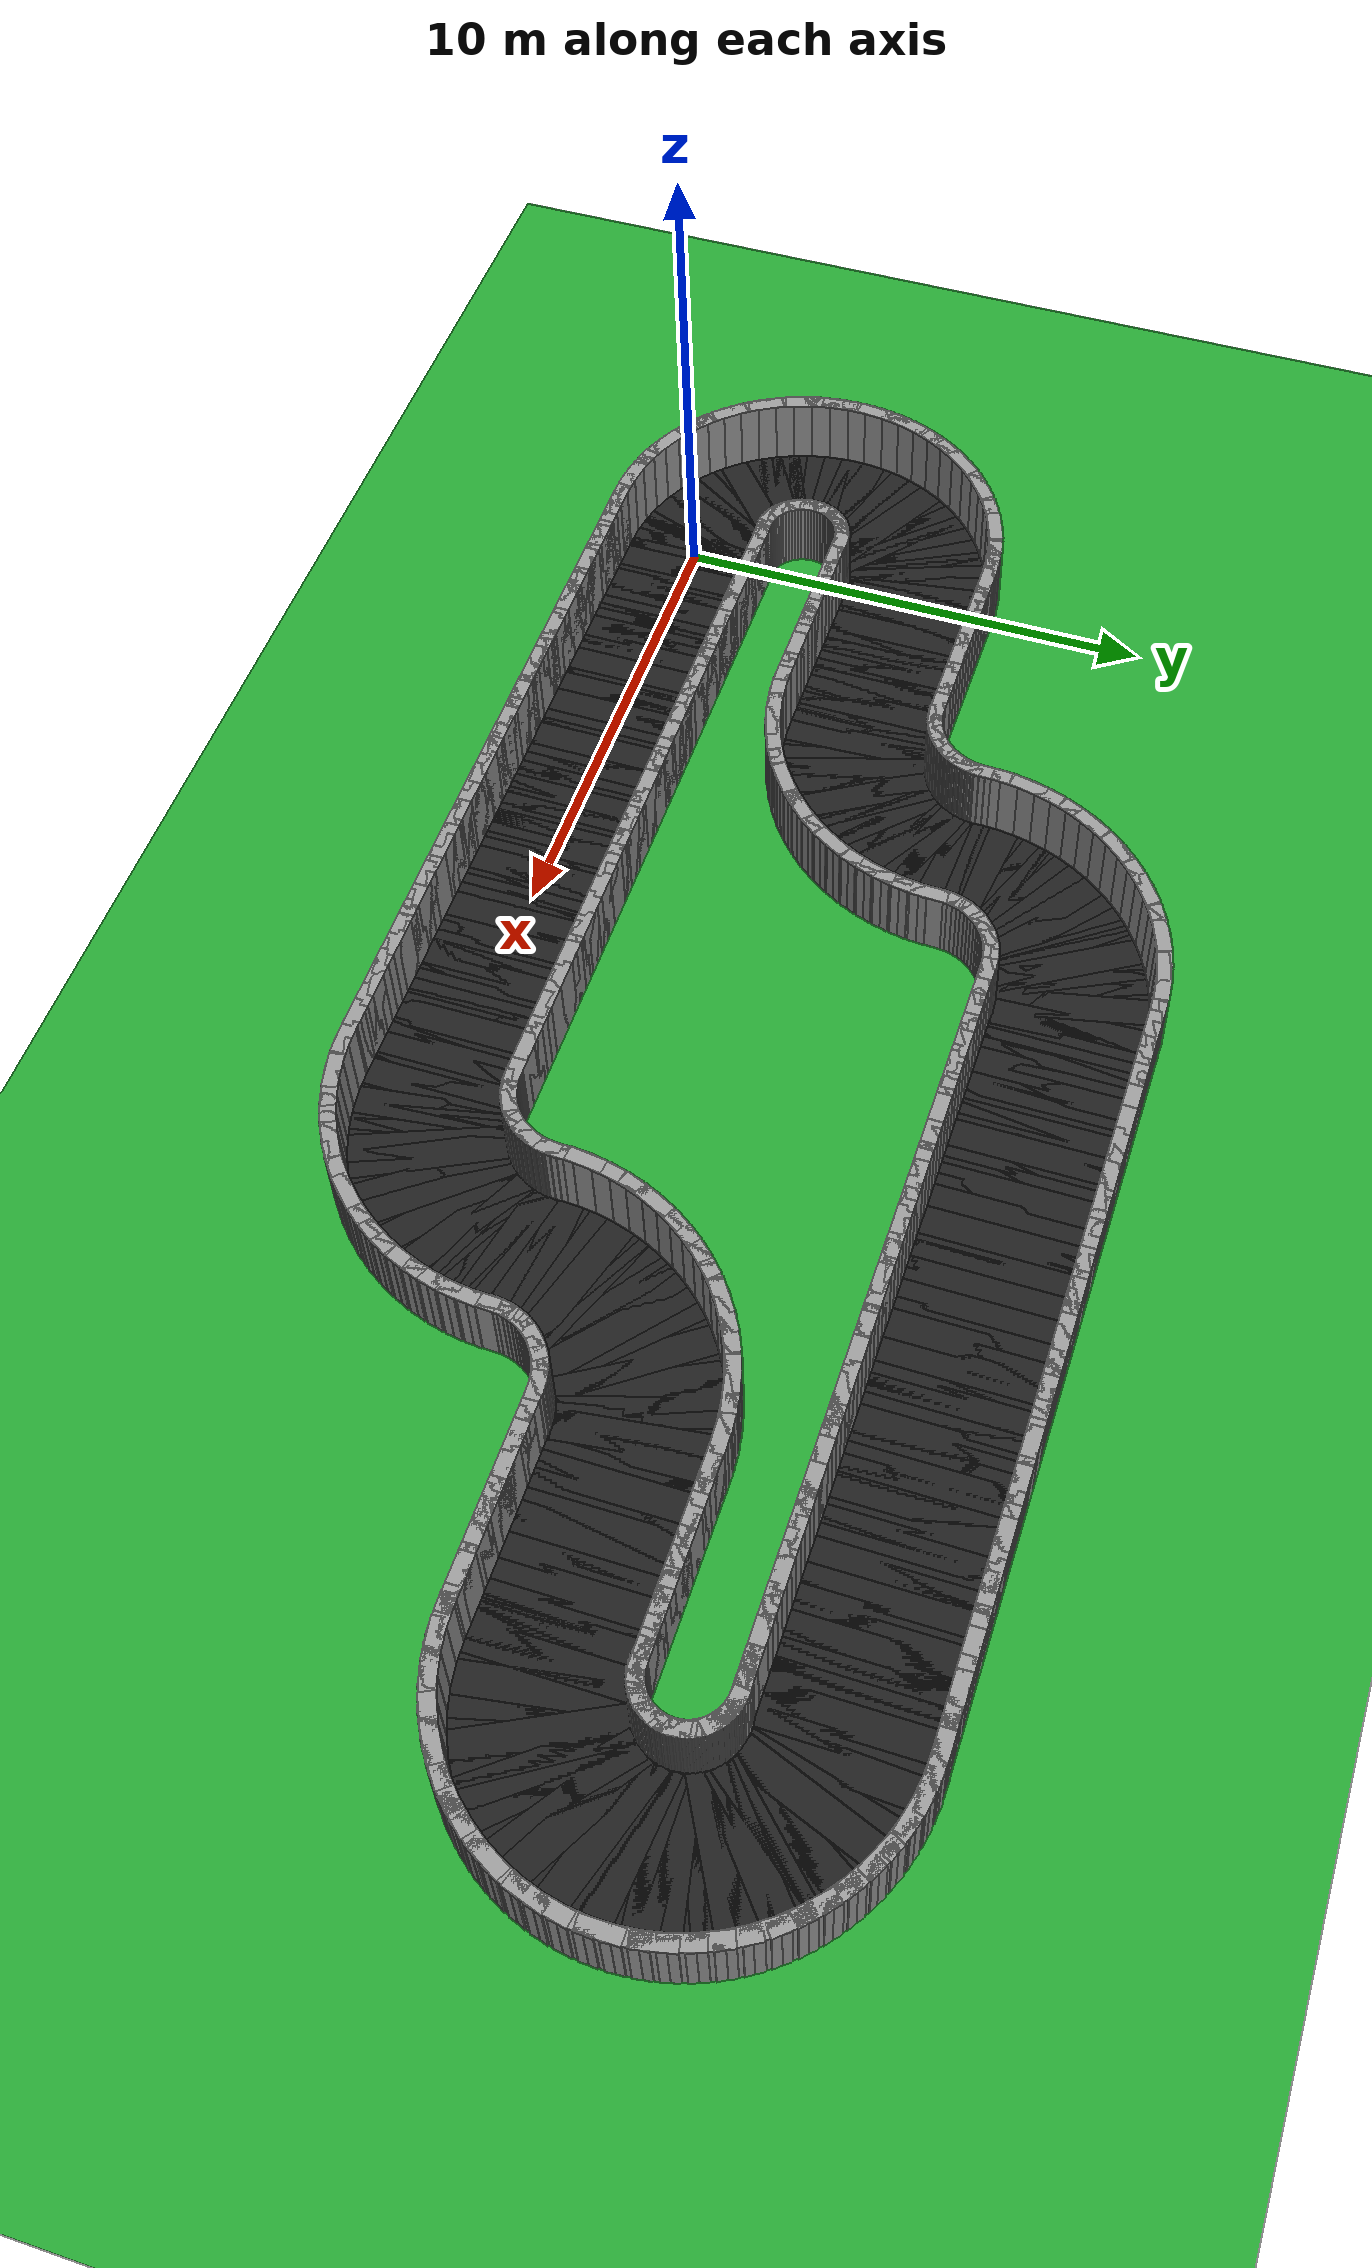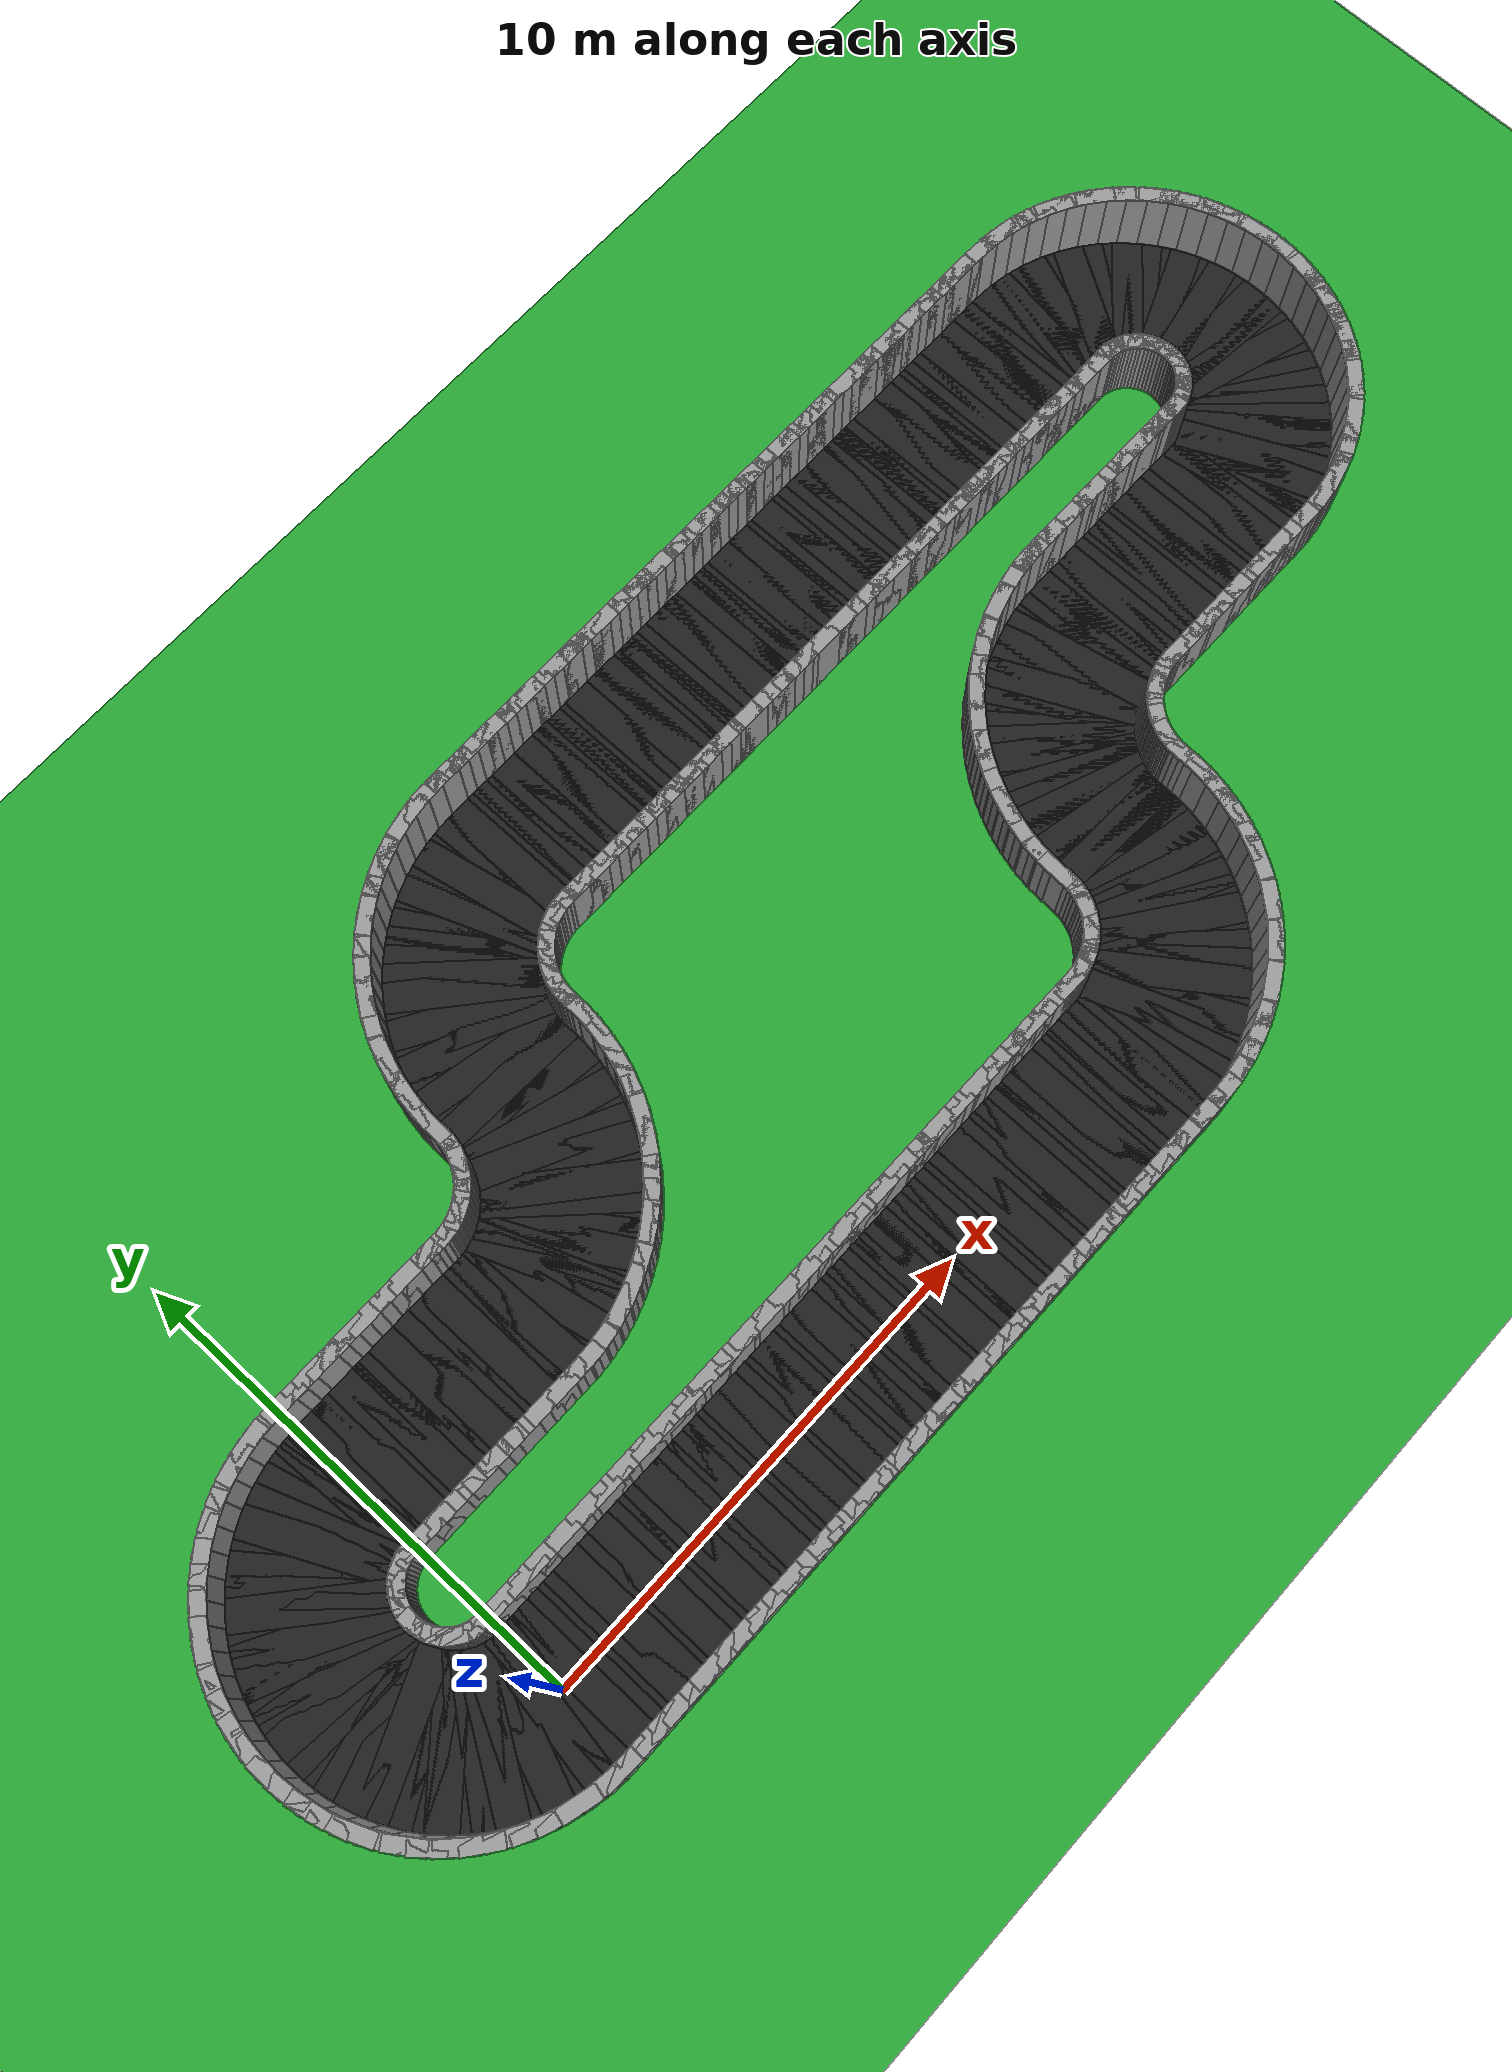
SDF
<?xml version="1.0" ?>
<sdf version="1.6">
  <world name="loop_extreme">
    <physics type="ode">
      <max_step_size>0.001</max_step_size>
      <real_time_factor>1.0</real_time_factor>
      <real_time_update_rate>1000</real_time_update_rate>
    </physics>
    <include><uri>model://sun</uri></include>

    <model name="ground_plane">
      <static>true</static>
      <link name="link">
        <collision name="collision">
          <surface><friction><ode><mu>100</mu><mu2>50</mu2></ode></friction></surface>
          <geometry><plane><normal>0 0 1</normal>
            <size>120 120</size></plane></geometry>
        </collision>
        <visual name="visual">
          <geometry><plane><normal>0 0 1</normal>
            <size>120 120</size></plane></geometry>
          <material><script>
            <uri>file://media/materials/scripts/gazebo.material</uri>
            <name>Gazebo/Green</name></script></material>
        </visual>
      </link>
    </model>

    <model name="asphalt_0">
      <static>true</static>
      <pose>0.125 0.000 0.005 0 0 0.00000</pose>
      <link name="link">
        <visual name="visual">
          <geometry><box><size>0.610 3.000 0.010</size></box></geometry>
          <material><script><uri>file://media/materials/scripts/gazebo.material</uri><name>Gazebo/Black</name></script></material>
        </visual>
      </link>
    </model>
    <model name="curbL_0">
      <static>true</static>
      <pose>0.125 1.650 0.750 0 0 0.00000</pose>
      <link name="link">
        <collision name="collision">
          <geometry><box><size>0.610 0.300 1.500</size></box></geometry>
        </collision>
        <visual name="visual">
          <geometry><box><size>0.610 0.300 1.500</size></box></geometry>
          <material><script><uri>file://media/materials/scripts/gazebo.material</uri><name>Gazebo/Grey</name></script></material>
        </visual>
      </link>
    </model>
    <model name="curbR_0">
      <static>true</static>
      <pose>0.125 -1.650 0.750 0 0 0.00000</pose>
      <link name="link">
        <collision name="collision">
          <geometry><box><size>0.610 0.300 1.500</size></box></geometry>
        </collision>
        <visual name="visual">
          <geometry><box><size>0.610 0.300 1.500</size></box></geometry>
          <material><script><uri>file://media/materials/scripts/gazebo.material</uri><name>Gazebo/Grey</name></script></material>
        </visual>
      </link>
    </model>
    <model name="asphalt_1">
      <static>true</static>
      <pose>0.375 0.000 0.005 0 0 0.00000</pose>
      <link name="link">
        <visual name="visual">
          <geometry><box><size>0.610 3.000 0.010</size></box></geometry>
          <material><script><uri>file://media/materials/scripts/gazebo.material</uri><name>Gazebo/Black</name></script></material>
        </visual>
      </link>
    </model>
    <model name="curbL_1">
      <static>true</static>
      <pose>0.375 1.650 0.750 0 0 0.00000</pose>
      <link name="link">
        <collision name="collision">
          <geometry><box><size>0.610 0.300 1.500</size></box></geometry>
        </collision>
        <visual name="visual">
          <geometry><box><size>0.610 0.300 1.500</size></box></geometry>
          <material><script><uri>file://media/materials/scripts/gazebo.material</uri><name>Gazebo/Grey</name></script></material>
        </visual>
      </link>
    </model>
    <model name="curbR_1">
      <static>true</static>
      <pose>0.375 -1.650 0.750 0 0 0.00000</pose>
      <link name="link">
        <collision name="collision">
          <geometry><box><size>0.610 0.300 1.500</size></box></geometry>
        </collision>
        <visual name="visual">
          <geometry><box><size>0.610 0.300 1.500</size></box></geometry>
          <material><script><uri>file://media/materials/scripts/gazebo.material</uri><name>Gazebo/Grey</name></script></material>
        </visual>
      </link>
    </model>
    <model name="asphalt_2">
      <static>true</static>
      <pose>0.625 0.000 0.005 0 0 0.00000</pose>
      <link name="link">
        <visual name="visual">
          <geometry><box><size>0.610 3.000 0.010</size></box></geometry>
          <material><script><uri>file://media/materials/scripts/gazebo.material</uri><name>Gazebo/Black</name></script></material>
        </visual>
      </link>
    </model>
    <model name="curbL_2">
      <static>true</static>
      <pose>0.625 1.650 0.750 0 0 0.00000</pose>
      <link name="link">
        <collision name="collision">
          <geometry><box><size>0.610 0.300 1.500</size></box></geometry>
        </collision>
        <visual name="visual">
          <geometry><box><size>0.610 0.300 1.500</size></box></geometry>
          <material><script><uri>file://media/materials/scripts/gazebo.material</uri><name>Gazebo/Grey</name></script></material>
        </visual>
      </link>
    </model>
    <model name="curbR_2">
      <static>true</static>
      <pose>0.625 -1.650 0.750 0 0 0.00000</pose>
      <link name="link">
        <collision name="collision">
          <geometry><box><size>0.610 0.300 1.500</size></box></geometry>
        </collision>
        <visual name="visual">
          <geometry><box><size>0.610 0.300 1.500</size></box></geometry>
          <material><script><uri>file://media/materials/scripts/gazebo.material</uri><name>Gazebo/Grey</name></script></material>
        </visual>
      </link>
    </model>
    <model name="asphalt_3">
      <static>true</static>
      <pose>0.875 0.000 0.005 0 0 0.00000</pose>
      <link name="link">
        <visual name="visual">
          <geometry><box><size>0.610 3.000 0.010</size></box></geometry>
          <material><script><uri>file://media/materials/scripts/gazebo.material</uri><name>Gazebo/Black</name></script></material>
        </visual>
      </link>
    </model>
    <model name="curbL_3">
      <static>true</static>
      <pose>0.875 1.650 0.750 0 0 0.00000</pose>
      <link name="link">
        <collision name="collision">
          <geometry><box><size>0.610 0.300 1.500</size></box></geometry>
        </collision>
        <visual name="visual">
          <geometry><box><size>0.610 0.300 1.500</size></box></geometry>
          <material><script><uri>file://media/materials/scripts/gazebo.material</uri><name>Gazebo/Grey</name></script></material>
        </visual>
      </link>
    </model>
    <model name="curbR_3">
      <static>true</static>
      <pose>0.875 -1.650 0.750 0 0 0.00000</pose>
      <link name="link">
        <collision name="collision">
          <geometry><box><size>0.610 0.300 1.500</size></box></geometry>
        </collision>
        <visual name="visual">
          <geometry><box><size>0.610 0.300 1.500</size></box></geometry>
          <material><script><uri>file://media/materials/scripts/gazebo.material</uri><name>Gazebo/Grey</name></script></material>
        </visual>
      </link>
    </model>
    <model name="asphalt_4">
      <static>true</static>
      <pose>1.125 0.000 0.005 0 0 0.00000</pose>
      <link name="link">
        <visual name="visual">
          <geometry><box><size>0.610 3.000 0.010</size></box></geometry>
          <material><script><uri>file://media/materials/scripts/gazebo.material</uri><name>Gazebo/Black</name></script></material>
        </visual>
      </link>
    </model>
    <model name="curbL_4">
      <static>true</static>
      <pose>1.125 1.650 0.750 0 0 0.00000</pose>
      <link name="link">
        <collision name="collision">
          <geometry><box><size>0.610 0.300 1.500</size></box></geometry>
        </collision>
        <visual name="visual">
          <geometry><box><size>0.610 0.300 1.500</size></box></geometry>
          <material><script><uri>file://media/materials/scripts/gazebo.material</uri><name>Gazebo/Grey</name></script></material>
        </visual>
      </link>
    </model>
    <model name="curbR_4">
      <static>true</static>
      <pose>1.125 -1.650 0.750 0 0 0.00000</pose>
      <link name="link">
        <collision name="collision">
          <geometry><box><size>0.610 0.300 1.500</size></box></geometry>
        </collision>
        <visual name="visual">
          <geometry><box><size>0.610 0.300 1.500</size></box></geometry>
          <material><script><uri>file://media/materials/scripts/gazebo.material</uri><name>Gazebo/Grey</name></script></material>
        </visual>
      </link>
    </model>
    <model name="asphalt_5">
      <static>true</static>
      <pose>1.375 0.000 0.005 0 0 0.00000</pose>
      <link name="link">
        <visual name="visual">
          <geometry><box><size>0.610 3.000 0.010</size></box></geometry>
          <material><script><uri>file://media/materials/scripts/gazebo.material</uri><name>Gazebo/Black</name></script></material>
        </visual>
      </link>
    </model>
    <model name="curbL_5">
      <static>true</static>
      <pose>1.375 1.650 0.750 0 0 0.00000</pose>
      <link name="link">
        <collision name="collision">
          <geometry><box><size>0.610 0.300 1.500</size></box></geometry>
        </collision>
        <visual name="visual">
          <geometry><box><size>0.610 0.300 1.500</size></box></geometry>
          <material><script><uri>file://media/materials/scripts/gazebo.material</uri><name>Gazebo/Grey</name></script></material>
        </visual>
      </link>
    </model>
    <model name="curbR_5">
      <static>true</static>
      <pose>1.375 -1.650 0.750 0 0 0.00000</pose>
      <link name="link">
        <collision name="collision">
          <geometry><box><size>0.610 0.300 1.500</size></box></geometry>
        </collision>
        <visual name="visual">
          <geometry><box><size>0.610 0.300 1.500</size></box></geometry>
          <material><script><uri>file://media/materials/scripts/gazebo.material</uri><name>Gazebo/Grey</name></script></material>
        </visual>
      </link>
    </model>
    <model name="asphalt_6">
      <static>true</static>
      <pose>1.625 0.000 0.005 0 0 0.00000</pose>
      <link name="link">
        <visual name="visual">
          <geometry><box><size>0.610 3.000 0.010</size></box></geometry>
          <material><script><uri>file://media/materials/scripts/gazebo.material</uri><name>Gazebo/Black</name></script></material>
        </visual>
      </link>
    </model>
    <model name="curbL_6">
      <static>true</static>
      <pose>1.625 1.650 0.750 0 0 0.00000</pose>
      <link name="link">
        <collision name="collision">
          <geometry><box><size>0.610 0.300 1.500</size></box></geometry>
        </collision>
        <visual name="visual">
          <geometry><box><size>0.610 0.300 1.500</size></box></geometry>
          <material><script><uri>file://media/materials/scripts/gazebo.material</uri><name>Gazebo/Grey</name></script></material>
        </visual>
      </link>
    </model>
    <model name="curbR_6">
      <static>true</static>
      <pose>1.625 -1.650 0.750 0 0 0.00000</pose>
      <link name="link">
        <collision name="collision">
          <geometry><box><size>0.610 0.300 1.500</size></box></geometry>
        </collision>
        <visual name="visual">
          <geometry><box><size>0.610 0.300 1.500</size></box></geometry>
          <material><script><uri>file://media/materials/scripts/gazebo.material</uri><name>Gazebo/Grey</name></script></material>
        </visual>
      </link>
    </model>
    <model name="asphalt_7">
      <static>true</static>
      <pose>1.875 0.000 0.005 0 0 0.00000</pose>
      <link name="link">
        <visual name="visual">
          <geometry><box><size>0.610 3.000 0.010</size></box></geometry>
          <material><script><uri>file://media/materials/scripts/gazebo.material</uri><name>Gazebo/Black</name></script></material>
        </visual>
      </link>
    </model>
    <model name="curbL_7">
      <static>true</static>
      <pose>1.875 1.650 0.750 0 0 0.00000</pose>
      <link name="link">
        <collision name="collision">
          <geometry><box><size>0.610 0.300 1.500</size></box></geometry>
        </collision>
        <visual name="visual">
          <geometry><box><size>0.610 0.300 1.500</size></box></geometry>
          <material><script><uri>file://media/materials/scripts/gazebo.material</uri><name>Gazebo/Grey</name></script></material>
        </visual>
      </link>
    </model>
    <model name="curbR_7">
      <static>true</static>
      <pose>1.875 -1.650 0.750 0 0 0.00000</pose>
      <link name="link">
        <collision name="collision">
          <geometry><box><size>0.610 0.300 1.500</size></box></geometry>
        </collision>
        <visual name="visual">
          <geometry><box><size>0.610 0.300 1.500</size></box></geometry>
          <material><script><uri>file://media/materials/scripts/gazebo.material</uri><name>Gazebo/Grey</name></script></material>
        </visual>
      </link>
    </model>
    <model name="asphalt_8">
      <static>true</static>
      <pose>2.125 0.000 0.005 0 0 0.00000</pose>
      <link name="link">
        <visual name="visual">
          <geometry><box><size>0.610 3.000 0.010</size></box></geometry>
          <material><script><uri>file://media/materials/scripts/gazebo.material</uri><name>Gazebo/Black</name></script></material>
        </visual>
      </link>
    </model>
    <model name="curbL_8">
      <static>true</static>
      <pose>2.125 1.650 0.750 0 0 0.00000</pose>
      <link name="link">
        <collision name="collision">
          <geometry><box><size>0.610 0.300 1.500</size></box></geometry>
        </collision>
        <visual name="visual">
          <geometry><box><size>0.610 0.300 1.500</size></box></geometry>
          <material><script><uri>file://media/materials/scripts/gazebo.material</uri><name>Gazebo/Grey</name></script></material>
        </visual>
      </link>
    </model>
    <model name="curbR_8">
      <static>true</static>
      <pose>2.125 -1.650 0.750 0 0 0.00000</pose>
      <link name="link">
        <collision name="collision">
          <geometry><box><size>0.610 0.300 1.500</size></box></geometry>
        </collision>
        <visual name="visual">
          <geometry><box><size>0.610 0.300 1.500</size></box></geometry>
          <material><script><uri>file://media/materials/scripts/gazebo.material</uri><name>Gazebo/Grey</name></script></material>
        </visual>
      </link>
    </model>
    <model name="asphalt_9">
      <static>true</static>
      <pose>2.375 0.000 0.005 0 0 0.00000</pose>
      <link name="link">
        <visual name="visual">
          <geometry><box><size>0.610 3.000 0.010</size></box></geometry>
          <material><script><uri>file://media/materials/scripts/gazebo.material</uri><name>Gazebo/Black</name></script></material>
        </visual>
      </link>
    </model>
    <model name="curbL_9">
      <static>true</static>
      <pose>2.375 1.650 0.750 0 0 0.00000</pose>
      <link name="link">
        <collision name="collision">
          <geometry><box><size>0.610 0.300 1.500</size></box></geometry>
        </collision>
        <visual name="visual">
          <geometry><box><size>0.610 0.300 1.500</size></box></geometry>
          <material><script><uri>file://media/materials/scripts/gazebo.material</uri><name>Gazebo/Grey</name></script></material>
        </visual>
      </link>
    </model>
    <model name="curbR_9">
      <static>true</static>
      <pose>2.375 -1.650 0.750 0 0 0.00000</pose>
      <link name="link">
        <collision name="collision">
          <geometry><box><size>0.610 0.300 1.500</size></box></geometry>
        </collision>
        <visual name="visual">
          <geometry><box><size>0.610 0.300 1.500</size></box></geometry>
          <material><script><uri>file://media/materials/scripts/gazebo.material</uri><name>Gazebo/Grey</name></script></material>
        </visual>
      </link>
    </model>
    <model name="asphalt_10">
      <static>true</static>
      <pose>2.625 0.000 0.005 0 0 0.00000</pose>
      <link name="link">
        <visual name="visual">
          <geometry><box><size>0.610 3.000 0.010</size></box></geometry>
          <material><script><uri>file://media/materials/scripts/gazebo.material</uri><name>Gazebo/Black</name></script></material>
        </visual>
      </link>
    </model>
    <model name="curbL_10">
      <static>true</static>
      <pose>2.625 1.650 0.750 0 0 0.00000</pose>
      <link name="link">
        <collision name="collision">
          <geometry><box><size>0.610 0.300 1.500</size></box></geometry>
        </collision>
        <visual name="visual">
          <geometry><box><size>0.610 0.300 1.500</size></box></geometry>
          <material><script><uri>file://media/materials/scripts/gazebo.material</uri><name>Gazebo/Grey</name></script></material>
        </visual>
      </link>
    </model>
    <model name="curbR_10">
      <static>true</static>
      <pose>2.625 -1.650 0.750 0 0 0.00000</pose>
      <link name="link">
        <collision name="collision">
          <geometry><box><size>0.610 0.300 1.500</size></box></geometry>
        </collision>
        <visual name="visual">
          <geometry><box><size>0.610 0.300 1.500</size></box></geometry>
          <material><script><uri>file://media/materials/scripts/gazebo.material</uri><name>Gazebo/Grey</name></script></material>
        </visual>
      </link>
    </model>
    <model name="asphalt_11">
      <static>true</static>
      <pose>2.875 0.000 0.005 0 0 0.00000</pose>
      <link name="link">
        <visual name="visual">
          <geometry><box><size>0.610 3.000 0.010</size></box></geometry>
          <material><script><uri>file://media/materials/scripts/gazebo.material</uri><name>Gazebo/Black</name></script></material>
        </visual>
      </link>
    </model>
    <model name="curbL_11">
      <static>true</static>
      <pose>2.875 1.650 0.750 0 0 0.00000</pose>
      <link name="link">
        <collision name="collision">
          <geometry><box><size>0.610 0.300 1.500</size></box></geometry>
        </collision>
        <visual name="visual">
          <geometry><box><size>0.610 0.300 1.500</size></box></geometry>
          <material><script><uri>file://media/materials/scripts/gazebo.material</uri><name>Gazebo/Grey</name></script></material>
        </visual>
      </link>
    </model>
    <model name="curbR_11">
      <static>true</static>
      <pose>2.875 -1.650 0.750 0 0 0.00000</pose>
      <link name="link">
        <collision name="collision">
          <geometry><box><size>0.610 0.300 1.500</size></box></geometry>
        </collision>
        <visual name="visual">
          <geometry><box><size>0.610 0.300 1.500</size></box></geometry>
          <material><script><uri>file://media/materials/scripts/gazebo.material</uri><name>Gazebo/Grey</name></script></material>
        </visual>
      </link>
    </model>
    <model name="asphalt_12">
      <static>true</static>
      <pose>3.125 0.000 0.005 0 0 0.00000</pose>
      <link name="link">
        <visual name="visual">
          <geometry><box><size>0.610 3.000 0.010</size></box></geometry>
          <material><script><uri>file://media/materials/scripts/gazebo.material</uri><name>Gazebo/Black</name></script></material>
        </visual>
      </link>
    </model>
    <model name="curbL_12">
      <static>true</static>
      <pose>3.125 1.650 0.750 0 0 0.00000</pose>
      <link name="link">
        <collision name="collision">
          <geometry><box><size>0.610 0.300 1.500</size></box></geometry>
        </collision>
        <visual name="visual">
          <geometry><box><size>0.610 0.300 1.500</size></box></geometry>
          <material><script><uri>file://media/materials/scripts/gazebo.material</uri><name>Gazebo/Grey</name></script></material>
        </visual>
      </link>
    </model>
    <model name="curbR_12">
      <static>true</static>
      <pose>3.125 -1.650 0.750 0 0 0.00000</pose>
      <link name="link">
        <collision name="collision">
          <geometry><box><size>0.610 0.300 1.500</size></box></geometry>
        </collision>
        <visual name="visual">
          <geometry><box><size>0.610 0.300 1.500</size></box></geometry>
          <material><script><uri>file://media/materials/scripts/gazebo.material</uri><name>Gazebo/Grey</name></script></material>
        </visual>
      </link>
    </model>
    <model name="asphalt_13">
      <static>true</static>
      <pose>3.375 0.000 0.005 0 0 0.00000</pose>
      <link name="link">
        <visual name="visual">
          <geometry><box><size>0.610 3.000 0.010</size></box></geometry>
          <material><script><uri>file://media/materials/scripts/gazebo.material</uri><name>Gazebo/Black</name></script></material>
        </visual>
      </link>
    </model>
    <model name="curbL_13">
      <static>true</static>
      <pose>3.375 1.650 0.750 0 0 0.00000</pose>
      <link name="link">
        <collision name="collision">
          <geometry><box><size>0.610 0.300 1.500</size></box></geometry>
        </collision>
        <visual name="visual">
          <geometry><box><size>0.610 0.300 1.500</size></box></geometry>
          <material><script><uri>file://media/materials/scripts/gazebo.material</uri><name>Gazebo/Grey</name></script></material>
        </visual>
      </link>
    </model>
    <model name="curbR_13">
      <static>true</static>
      <pose>3.375 -1.650 0.750 0 0 0.00000</pose>
      <link name="link">
        <collision name="collision">
          <geometry><box><size>0.610 0.300 1.500</size></box></geometry>
        </collision>
        <visual name="visual">
          <geometry><box><size>0.610 0.300 1.500</size></box></geometry>
          <material><script><uri>file://media/materials/scripts/gazebo.material</uri><name>Gazebo/Grey</name></script></material>
        </visual>
      </link>
    </model>
    <model name="asphalt_14">
      <static>true</static>
      <pose>3.625 0.000 0.005 0 0 0.00000</pose>
      <link name="link">
        <visual name="visual">
          <geometry><box><size>0.610 3.000 0.010</size></box></geometry>
          <material><script><uri>file://media/materials/scripts/gazebo.material</uri><name>Gazebo/Black</name></script></material>
        </visual>
      </link>
    </model>
    <model name="curbL_14">
      <static>true</static>
      <pose>3.625 1.650 0.750 0 0 0.00000</pose>
      <link name="link">
        <collision name="collision">
          <geometry><box><size>0.610 0.300 1.500</size></box></geometry>
        </collision>
        <visual name="visual">
          <geometry><box><size>0.610 0.300 1.500</size></box></geometry>
          <material><script><uri>file://media/materials/scripts/gazebo.material</uri><name>Gazebo/Grey</name></script></material>
        </visual>
      </link>
    </model>
    <model name="curbR_14">
      <static>true</static>
      <pose>3.625 -1.650 0.750 0 0 0.00000</pose>
      <link name="link">
        <collision name="collision">
          <geometry><box><size>0.610 0.300 1.500</size></box></geometry>
        </collision>
        <visual name="visual">
          <geometry><box><size>0.610 0.300 1.500</size></box></geometry>
          <material><script><uri>file://media/materials/scripts/gazebo.material</uri><name>Gazebo/Grey</name></script></material>
        </visual>
      </link>
    </model>
    <model name="asphalt_15">
      <static>true</static>
      <pose>3.875 0.000 0.005 0 0 0.00000</pose>
      <link name="link">
        <visual name="visual">
          <geometry><box><size>0.610 3.000 0.010</size></box></geometry>
          <material><script><uri>file://media/materials/scripts/gazebo.material</uri><name>Gazebo/Black</name></script></material>
        </visual>
      </link>
    </model>
    <model name="curbL_15">
      <static>true</static>
      <pose>3.875 1.650 0.750 0 0 0.00000</pose>
      <link name="link">
        <collision name="collision">
          <geometry><box><size>0.610 0.300 1.500</size></box></geometry>
        </collision>
        <visual name="visual">
          <geometry><box><size>0.610 0.300 1.500</size></box></geometry>
          <material><script><uri>file://media/materials/scripts/gazebo.material</uri><name>Gazebo/Grey</name></script></material>
        </visual>
      </link>
    </model>
    <model name="curbR_15">
      <static>true</static>
      <pose>3.875 -1.650 0.750 0 0 0.00000</pose>
      <link name="link">
        <collision name="collision">
          <geometry><box><size>0.610 0.300 1.500</size></box></geometry>
        </collision>
        <visual name="visual">
          <geometry><box><size>0.610 0.300 1.500</size></box></geometry>
          <material><script><uri>file://media/materials/scripts/gazebo.material</uri><name>Gazebo/Grey</name></script></material>
        </visual>
      </link>
    </model>
    <model name="asphalt_16">
      <static>true</static>
      <pose>4.125 0.000 0.005 0 0 0.00000</pose>
      <link name="link">
        <visual name="visual">
          <geometry><box><size>0.610 3.000 0.010</size></box></geometry>
          <material><script><uri>file://media/materials/scripts/gazebo.material</uri><name>Gazebo/Black</name></script></material>
        </visual>
      </link>
    </model>
    <model name="curbL_16">
      <static>true</static>
      <pose>4.125 1.650 0.750 0 0 0.00000</pose>
      <link name="link">
        <collision name="collision">
          <geometry><box><size>0.610 0.300 1.500</size></box></geometry>
        </collision>
        <visual name="visual">
          <geometry><box><size>0.610 0.300 1.500</size></box></geometry>
          <material><script><uri>file://media/materials/scripts/gazebo.material</uri><name>Gazebo/Grey</name></script></material>
        </visual>
      </link>
    </model>
    <model name="curbR_16">
      <static>true</static>
      <pose>4.125 -1.650 0.750 0 0 0.00000</pose>
      <link name="link">
        <collision name="collision">
          <geometry><box><size>0.610 0.300 1.500</size></box></geometry>
        </collision>
        <visual name="visual">
          <geometry><box><size>0.610 0.300 1.500</size></box></geometry>
          <material><script><uri>file://media/materials/scripts/gazebo.material</uri><name>Gazebo/Grey</name></script></material>
        </visual>
      </link>
    </model>
    <model name="asphalt_17">
      <static>true</static>
      <pose>4.375 0.000 0.005 0 0 0.00000</pose>
      <link name="link">
        <visual name="visual">
          <geometry><box><size>0.610 3.000 0.010</size></box></geometry>
          <material><script><uri>file://media/materials/scripts/gazebo.material</uri><name>Gazebo/Black</name></script></material>
        </visual>
      </link>
    </model>
    <model name="curbL_17">
      <static>true</static>
      <pose>4.375 1.650 0.750 0 0 0.00000</pose>
      <link name="link">
        <collision name="collision">
          <geometry><box><size>0.610 0.300 1.500</size></box></geometry>
        </collision>
        <visual name="visual">
          <geometry><box><size>0.610 0.300 1.500</size></box></geometry>
          <material><script><uri>file://media/materials/scripts/gazebo.material</uri><name>Gazebo/Grey</name></script></material>
        </visual>
      </link>
    </model>
    <model name="curbR_17">
      <static>true</static>
      <pose>4.375 -1.650 0.750 0 0 0.00000</pose>
      <link name="link">
        <collision name="collision">
          <geometry><box><size>0.610 0.300 1.500</size></box></geometry>
        </collision>
        <visual name="visual">
          <geometry><box><size>0.610 0.300 1.500</size></box></geometry>
          <material><script><uri>file://media/materials/scripts/gazebo.material</uri><name>Gazebo/Grey</name></script></material>
        </visual>
      </link>
    </model>
    <model name="asphalt_18">
      <static>true</static>
      <pose>4.625 0.000 0.005 0 0 0.00000</pose>
      <link name="link">
        <visual name="visual">
          <geometry><box><size>0.610 3.000 0.010</size></box></geometry>
          <material><script><uri>file://media/materials/scripts/gazebo.material</uri><name>Gazebo/Black</name></script></material>
        </visual>
      </link>
    </model>
    <model name="curbL_18">
      <static>true</static>
      <pose>4.625 1.650 0.750 0 0 0.00000</pose>
      <link name="link">
        <collision name="collision">
          <geometry><box><size>0.610 0.300 1.500</size></box></geometry>
        </collision>
        <visual name="visual">
          <geometry><box><size>0.610 0.300 1.500</size></box></geometry>
          <material><script><uri>file://media/materials/scripts/gazebo.material</uri><name>Gazebo/Grey</name></script></material>
        </visual>
      </link>
    </model>
    <model name="curbR_18">
      <static>true</static>
      <pose>4.625 -1.650 0.750 0 0 0.00000</pose>
      <link name="link">
        <collision name="collision">
          <geometry><box><size>0.610 0.300 1.500</size></box></geometry>
        </collision>
        <visual name="visual">
          <geometry><box><size>0.610 0.300 1.500</size></box></geometry>
          <material><script><uri>file://media/materials/scripts/gazebo.material</uri><name>Gazebo/Grey</name></script></material>
        </visual>
      </link>
    </model>
    <model name="asphalt_19">
      <static>true</static>
      <pose>4.875 0.000 0.005 0 0 0.00000</pose>
      <link name="link">
        <visual name="visual">
          <geometry><box><size>0.610 3.000 0.010</size></box></geometry>
          <material><script><uri>file://media/materials/scripts/gazebo.material</uri><name>Gazebo/Black</name></script></material>
        </visual>
      </link>
    </model>
    <model name="curbL_19">
      <static>true</static>
      <pose>4.875 1.650 0.750 0 0 0.00000</pose>
      <link name="link">
        <collision name="collision">
          <geometry><box><size>0.610 0.300 1.500</size></box></geometry>
        </collision>
        <visual name="visual">
          <geometry><box><size>0.610 0.300 1.500</size></box></geometry>
          <material><script><uri>file://media/materials/scripts/gazebo.material</uri><name>Gazebo/Grey</name></script></material>
        </visual>
      </link>
    </model>
    <model name="curbR_19">
      <static>true</static>
      <pose>4.875 -1.650 0.750 0 0 0.00000</pose>
      <link name="link">
        <collision name="collision">
          <geometry><box><size>0.610 0.300 1.500</size></box></geometry>
        </collision>
        <visual name="visual">
          <geometry><box><size>0.610 0.300 1.500</size></box></geometry>
          <material><script><uri>file://media/materials/scripts/gazebo.material</uri><name>Gazebo/Grey</name></script></material>
        </visual>
      </link>
    </model>
    <model name="asphalt_20">
      <static>true</static>
      <pose>5.125 0.000 0.005 0 0 0.00000</pose>
      <link name="link">
        <visual name="visual">
          <geometry><box><size>0.610 3.000 0.010</size></box></geometry>
          <material><script><uri>file://media/materials/scripts/gazebo.material</uri><name>Gazebo/Black</name></script></material>
        </visual>
      </link>
    </model>
    <model name="curbL_20">
      <static>true</static>
      <pose>5.125 1.650 0.750 0 0 0.00000</pose>
      <link name="link">
        <collision name="collision">
          <geometry><box><size>0.610 0.300 1.500</size></box></geometry>
        </collision>
        <visual name="visual">
          <geometry><box><size>0.610 0.300 1.500</size></box></geometry>
          <material><script><uri>file://media/materials/scripts/gazebo.material</uri><name>Gazebo/Grey</name></script></material>
        </visual>
      </link>
    </model>
    <model name="curbR_20">
      <static>true</static>
      <pose>5.125 -1.650 0.750 0 0 0.00000</pose>
      <link name="link">
        <collision name="collision">
          <geometry><box><size>0.610 0.300 1.500</size></box></geometry>
        </collision>
        <visual name="visual">
          <geometry><box><size>0.610 0.300 1.500</size></box></geometry>
          <material><script><uri>file://media/materials/scripts/gazebo.material</uri><name>Gazebo/Grey</name></script></material>
        </visual>
      </link>
    </model>
    <model name="asphalt_21">
      <static>true</static>
      <pose>5.375 0.000 0.005 0 0 0.00000</pose>
      <link name="link">
        <visual name="visual">
          <geometry><box><size>0.610 3.000 0.010</size></box></geometry>
          <material><script><uri>file://media/materials/scripts/gazebo.material</uri><name>Gazebo/Black</name></script></material>
        </visual>
      </link>
    </model>
    <model name="curbL_21">
      <static>true</static>
      <pose>5.375 1.650 0.750 0 0 0.00000</pose>
      <link name="link">
        <collision name="collision">
          <geometry><box><size>0.610 0.300 1.500</size></box></geometry>
        </collision>
        <visual name="visual">
          <geometry><box><size>0.610 0.300 1.500</size></box></geometry>
          <material><script><uri>file://media/materials/scripts/gazebo.material</uri><name>Gazebo/Grey</name></script></material>
        </visual>
      </link>
    </model>
    <model name="curbR_21">
      <static>true</static>
      <pose>5.375 -1.650 0.750 0 0 0.00000</pose>
      <link name="link">
        <collision name="collision">
          <geometry><box><size>0.610 0.300 1.500</size></box></geometry>
        </collision>
        <visual name="visual">
          <geometry><box><size>0.610 0.300 1.500</size></box></geometry>
          <material><script><uri>file://media/materials/scripts/gazebo.material</uri><name>Gazebo/Grey</name></script></material>
        </visual>
      </link>
    </model>
    <model name="asphalt_22">
      <static>true</static>
      <pose>5.625 0.000 0.005 0 0 0.00000</pose>
      <link name="link">
        <visual name="visual">
          <geometry><box><size>0.610 3.000 0.010</size></box></geometry>
          <material><script><uri>file://media/materials/scripts/gazebo.material</uri><name>Gazebo/Black</name></script></material>
        </visual>
      </link>
    </model>
    <model name="curbL_22">
      <static>true</static>
      <pose>5.625 1.650 0.750 0 0 0.00000</pose>
      <link name="link">
        <collision name="collision">
          <geometry><box><size>0.610 0.300 1.500</size></box></geometry>
        </collision>
        <visual name="visual">
          <geometry><box><size>0.610 0.300 1.500</size></box></geometry>
          <material><script><uri>file://media/materials/scripts/gazebo.material</uri><name>Gazebo/Grey</name></script></material>
        </visual>
      </link>
    </model>
    <model name="curbR_22">
      <static>true</static>
      <pose>5.625 -1.650 0.750 0 0 0.00000</pose>
      <link name="link">
        <collision name="collision">
          <geometry><box><size>0.610 0.300 1.500</size></box></geometry>
        </collision>
        <visual name="visual">
          <geometry><box><size>0.610 0.300 1.500</size></box></geometry>
          <material><script><uri>file://media/materials/scripts/gazebo.material</uri><name>Gazebo/Grey</name></script></material>
        </visual>
      </link>
    </model>
    <model name="asphalt_23">
      <static>true</static>
      <pose>5.875 0.000 0.005 0 0 0.00000</pose>
      <link name="link">
        <visual name="visual">
          <geometry><box><size>0.610 3.000 0.010</size></box></geometry>
          <material><script><uri>file://media/materials/scripts/gazebo.material</uri><name>Gazebo/Black</name></script></material>
        </visual>
      </link>
    </model>
    <model name="curbL_23">
      <static>true</static>
      <pose>5.875 1.650 0.750 0 0 0.00000</pose>
      <link name="link">
        <collision name="collision">
          <geometry><box><size>0.610 0.300 1.500</size></box></geometry>
        </collision>
        <visual name="visual">
          <geometry><box><size>0.610 0.300 1.500</size></box></geometry>
          <material><script><uri>file://media/materials/scripts/gazebo.material</uri><name>Gazebo/Grey</name></script></material>
        </visual>
      </link>
    </model>
    <model name="curbR_23">
      <static>true</static>
      <pose>5.875 -1.650 0.750 0 0 0.00000</pose>
      <link name="link">
        <collision name="collision">
          <geometry><box><size>0.610 0.300 1.500</size></box></geometry>
        </collision>
        <visual name="visual">
          <geometry><box><size>0.610 0.300 1.500</size></box></geometry>
          <material><script><uri>file://media/materials/scripts/gazebo.material</uri><name>Gazebo/Grey</name></script></material>
        </visual>
      </link>
    </model>
    <model name="asphalt_24">
      <static>true</static>
      <pose>6.125 0.000 0.005 0 0 0.00000</pose>
      <link name="link">
        <visual name="visual">
          <geometry><box><size>0.610 3.000 0.010</size></box></geometry>
          <material><script><uri>file://media/materials/scripts/gazebo.material</uri><name>Gazebo/Black</name></script></material>
        </visual>
      </link>
    </model>
    <model name="curbL_24">
      <static>true</static>
      <pose>6.125 1.650 0.750 0 0 0.00000</pose>
      <link name="link">
        <collision name="collision">
          <geometry><box><size>0.610 0.300 1.500</size></box></geometry>
        </collision>
        <visual name="visual">
          <geometry><box><size>0.610 0.300 1.500</size></box></geometry>
          <material><script><uri>file://media/materials/scripts/gazebo.material</uri><name>Gazebo/Grey</name></script></material>
        </visual>
      </link>
    </model>
    <model name="curbR_24">
      <static>true</static>
      <pose>6.125 -1.650 0.750 0 0 0.00000</pose>
      <link name="link">
        <collision name="collision">
          <geometry><box><size>0.610 0.300 1.500</size></box></geometry>
        </collision>
        <visual name="visual">
          <geometry><box><size>0.610 0.300 1.500</size></box></geometry>
          <material><script><uri>file://media/materials/scripts/gazebo.material</uri><name>Gazebo/Grey</name></script></material>
        </visual>
      </link>
    </model>
    <model name="asphalt_25">
      <static>true</static>
      <pose>6.375 0.000 0.005 0 0 0.00000</pose>
      <link name="link">
        <visual name="visual">
          <geometry><box><size>0.610 3.000 0.010</size></box></geometry>
          <material><script><uri>file://media/materials/scripts/gazebo.material</uri><name>Gazebo/Black</name></script></material>
        </visual>
      </link>
    </model>
    <model name="curbL_25">
      <static>true</static>
      <pose>6.375 1.650 0.750 0 0 0.00000</pose>
      <link name="link">
        <collision name="collision">
          <geometry><box><size>0.610 0.300 1.500</size></box></geometry>
        </collision>
        <visual name="visual">
          <geometry><box><size>0.610 0.300 1.500</size></box></geometry>
          <material><script><uri>file://media/materials/scripts/gazebo.material</uri><name>Gazebo/Grey</name></script></material>
        </visual>
      </link>
    </model>
    <model name="curbR_25">
      <static>true</static>
      <pose>6.375 -1.650 0.750 0 0 0.00000</pose>
      <link name="link">
        <collision name="collision">
          <geometry><box><size>0.610 0.300 1.500</size></box></geometry>
        </collision>
        <visual name="visual">
          <geometry><box><size>0.610 0.300 1.500</size></box></geometry>
          <material><script><uri>file://media/materials/scripts/gazebo.material</uri><name>Gazebo/Grey</name></script></material>
        </visual>
      </link>
    </model>
    <model name="asphalt_26">
      <static>true</static>
      <pose>6.625 0.000 0.005 0 0 0.00000</pose>
      <link name="link">
        <visual name="visual">
          <geometry><box><size>0.610 3.000 0.010</size></box></geometry>
          <material><script><uri>file://media/materials/scripts/gazebo.material</uri><name>Gazebo/Black</name></script></material>
        </visual>
      </link>
    </model>
    <model name="curbL_26">
      <static>true</static>
      <pose>6.625 1.650 0.750 0 0 0.00000</pose>
      <link name="link">
        <collision name="collision">
          <geometry><box><size>0.610 0.300 1.500</size></box></geometry>
        </collision>
        <visual name="visual">
          <geometry><box><size>0.610 0.300 1.500</size></box></geometry>
          <material><script><uri>file://media/materials/scripts/gazebo.material</uri><name>Gazebo/Grey</name></script></material>
        </visual>
      </link>
    </model>
    <model name="curbR_26">
      <static>true</static>
      <pose>6.625 -1.650 0.750 0 0 0.00000</pose>
      <link name="link">
        <collision name="collision">
          <geometry><box><size>0.610 0.300 1.500</size></box></geometry>
        </collision>
        <visual name="visual">
          <geometry><box><size>0.610 0.300 1.500</size></box></geometry>
          <material><script><uri>file://media/materials/scripts/gazebo.material</uri><name>Gazebo/Grey</name></script></material>
        </visual>
      </link>
    </model>
    <model name="asphalt_27">
      <static>true</static>
      <pose>6.875 0.000 0.005 0 0 0.00000</pose>
      <link name="link">
        <visual name="visual">
          <geometry><box><size>0.610 3.000 0.010</size></box></geometry>
          <material><script><uri>file://media/materials/scripts/gazebo.material</uri><name>Gazebo/Black</name></script></material>
        </visual>
      </link>
    </model>
    <model name="curbL_27">
      <static>true</static>
      <pose>6.875 1.650 0.750 0 0 0.00000</pose>
      <link name="link">
        <collision name="collision">
          <geometry><box><size>0.610 0.300 1.500</size></box></geometry>
        </collision>
        <visual name="visual">
          <geometry><box><size>0.610 0.300 1.500</size></box></geometry>
          <material><script><uri>file://media/materials/scripts/gazebo.material</uri><name>Gazebo/Grey</name></script></material>
        </visual>
      </link>
    </model>
    <model name="curbR_27">
      <static>true</static>
      <pose>6.875 -1.650 0.750 0 0 0.00000</pose>
      <link name="link">
        <collision name="collision">
          <geometry><box><size>0.610 0.300 1.500</size></box></geometry>
        </collision>
        <visual name="visual">
          <geometry><box><size>0.610 0.300 1.500</size></box></geometry>
          <material><script><uri>file://media/materials/scripts/gazebo.material</uri><name>Gazebo/Grey</name></script></material>
        </visual>
      </link>
    </model>
    <model name="asphalt_28">
      <static>true</static>
      <pose>7.125 0.000 0.005 0 0 0.00000</pose>
      <link name="link">
        <visual name="visual">
          <geometry><box><size>0.610 3.000 0.010</size></box></geometry>
          <material><script><uri>file://media/materials/scripts/gazebo.material</uri><name>Gazebo/Black</name></script></material>
        </visual>
      </link>
    </model>
    <model name="curbL_28">
      <static>true</static>
      <pose>7.125 1.650 0.750 0 0 0.00000</pose>
      <link name="link">
        <collision name="collision">
          <geometry><box><size>0.610 0.300 1.500</size></box></geometry>
        </collision>
        <visual name="visual">
          <geometry><box><size>0.610 0.300 1.500</size></box></geometry>
          <material><script><uri>file://media/materials/scripts/gazebo.material</uri><name>Gazebo/Grey</name></script></material>
        </visual>
      </link>
    </model>
    <model name="curbR_28">
      <static>true</static>
      <pose>7.125 -1.650 0.750 0 0 0.00000</pose>
      <link name="link">
        <collision name="collision">
          <geometry><box><size>0.610 0.300 1.500</size></box></geometry>
        </collision>
        <visual name="visual">
          <geometry><box><size>0.610 0.300 1.500</size></box></geometry>
          <material><script><uri>file://media/materials/scripts/gazebo.material</uri><name>Gazebo/Grey</name></script></material>
        </visual>
      </link>
    </model>
    <model name="asphalt_29">
      <static>true</static>
      <pose>7.375 0.000 0.005 0 0 0.00000</pose>
      <link name="link">
        <visual name="visual">
          <geometry><box><size>0.610 3.000 0.010</size></box></geometry>
          <material><script><uri>file://media/materials/scripts/gazebo.material</uri><name>Gazebo/Black</name></script></material>
        </visual>
      </link>
    </model>
    <model name="curbL_29">
      <static>true</static>
      <pose>7.375 1.650 0.750 0 0 0.00000</pose>
      <link name="link">
        <collision name="collision">
          <geometry><box><size>0.610 0.300 1.500</size></box></geometry>
        </collision>
        <visual name="visual">
          <geometry><box><size>0.610 0.300 1.500</size></box></geometry>
          <material><script><uri>file://media/materials/scripts/gazebo.material</uri><name>Gazebo/Grey</name></script></material>
        </visual>
      </link>
    </model>
    <model name="curbR_29">
      <static>true</static>
      <pose>7.375 -1.650 0.750 0 0 0.00000</pose>
      <link name="link">
        <collision name="collision">
          <geometry><box><size>0.610 0.300 1.500</size></box></geometry>
        </collision>
        <visual name="visual">
          <geometry><box><size>0.610 0.300 1.500</size></box></geometry>
          <material><script><uri>file://media/materials/scripts/gazebo.material</uri><name>Gazebo/Grey</name></script></material>
        </visual>
      </link>
    </model>
    <model name="asphalt_30">
      <static>true</static>
      <pose>7.625 0.000 0.005 0 0 0.00000</pose>
      <link name="link">
        <visual name="visual">
          <geometry><box><size>0.610 3.000 0.010</size></box></geometry>
          <material><script><uri>file://media/materials/scripts/gazebo.material</uri><name>Gazebo/Black</name></script></material>
        </visual>
      </link>
    </model>
    <model name="curbL_30">
      <static>true</static>
      <pose>7.625 1.650 0.750 0 0 0.00000</pose>
      <link name="link">
        <collision name="collision">
          <geometry><box><size>0.610 0.300 1.500</size></box></geometry>
        </collision>
        <visual name="visual">
          <geometry><box><size>0.610 0.300 1.500</size></box></geometry>
          <material><script><uri>file://media/materials/scripts/gazebo.material</uri><name>Gazebo/Grey</name></script></material>
        </visual>
      </link>
    </model>
    <model name="curbR_30">
      <static>true</static>
      <pose>7.625 -1.650 0.750 0 0 0.00000</pose>
      <link name="link">
        <collision name="collision">
          <geometry><box><size>0.610 0.300 1.500</size></box></geometry>
        </collision>
        <visual name="visual">
          <geometry><box><size>0.610 0.300 1.500</size></box></geometry>
          <material><script><uri>file://media/materials/scripts/gazebo.material</uri><name>Gazebo/Grey</name></script></material>
        </visual>
      </link>
    </model>
    <model name="asphalt_31">
      <static>true</static>
      <pose>7.875 0.000 0.005 0 0 0.00000</pose>
      <link name="link">
        <visual name="visual">
          <geometry><box><size>0.610 3.000 0.010</size></box></geometry>
          <material><script><uri>file://media/materials/scripts/gazebo.material</uri><name>Gazebo/Black</name></script></material>
        </visual>
      </link>
    </model>
    <model name="curbL_31">
      <static>true</static>
      <pose>7.875 1.650 0.750 0 0 0.00000</pose>
      <link name="link">
        <collision name="collision">
          <geometry><box><size>0.610 0.300 1.500</size></box></geometry>
        </collision>
        <visual name="visual">
          <geometry><box><size>0.610 0.300 1.500</size></box></geometry>
          <material><script><uri>file://media/materials/scripts/gazebo.material</uri><name>Gazebo/Grey</name></script></material>
        </visual>
      </link>
    </model>
    <model name="curbR_31">
      <static>true</static>
      <pose>7.875 -1.650 0.750 0 0 0.00000</pose>
      <link name="link">
        <collision name="collision">
          <geometry><box><size>0.610 0.300 1.500</size></box></geometry>
        </collision>
        <visual name="visual">
          <geometry><box><size>0.610 0.300 1.500</size></box></geometry>
          <material><script><uri>file://media/materials/scripts/gazebo.material</uri><name>Gazebo/Grey</name></script></material>
        </visual>
      </link>
    </model>
    <model name="asphalt_32">
      <static>true</static>
      <pose>8.125 0.000 0.005 0 0 0.00000</pose>
      <link name="link">
        <visual name="visual">
          <geometry><box><size>0.610 3.000 0.010</size></box></geometry>
          <material><script><uri>file://media/materials/scripts/gazebo.material</uri><name>Gazebo/Black</name></script></material>
        </visual>
      </link>
    </model>
    <model name="curbL_32">
      <static>true</static>
      <pose>8.125 1.650 0.750 0 0 0.00000</pose>
      <link name="link">
        <collision name="collision">
          <geometry><box><size>0.610 0.300 1.500</size></box></geometry>
        </collision>
        <visual name="visual">
          <geometry><box><size>0.610 0.300 1.500</size></box></geometry>
          <material><script><uri>file://media/materials/scripts/gazebo.material</uri><name>Gazebo/Grey</name></script></material>
        </visual>
      </link>
    </model>
    <model name="curbR_32">
      <static>true</static>
      <pose>8.125 -1.650 0.750 0 0 0.00000</pose>
      <link name="link">
        <collision name="collision">
          <geometry><box><size>0.610 0.300 1.500</size></box></geometry>
        </collision>
        <visual name="visual">
          <geometry><box><size>0.610 0.300 1.500</size></box></geometry>
          <material><script><uri>file://media/materials/scripts/gazebo.material</uri><name>Gazebo/Grey</name></script></material>
        </visual>
      </link>
    </model>
    <model name="asphalt_33">
      <static>true</static>
      <pose>8.375 0.000 0.005 0 0 0.00000</pose>
      <link name="link">
        <visual name="visual">
          <geometry><box><size>0.610 3.000 0.010</size></box></geometry>
          <material><script><uri>file://media/materials/scripts/gazebo.material</uri><name>Gazebo/Black</name></script></material>
        </visual>
      </link>
    </model>
    <model name="curbL_33">
      <static>true</static>
      <pose>8.375 1.650 0.750 0 0 0.00000</pose>
      <link name="link">
        <collision name="collision">
          <geometry><box><size>0.610 0.300 1.500</size></box></geometry>
        </collision>
        <visual name="visual">
          <geometry><box><size>0.610 0.300 1.500</size></box></geometry>
          <material><script><uri>file://media/materials/scripts/gazebo.material</uri><name>Gazebo/Grey</name></script></material>
        </visual>
      </link>
    </model>
    <model name="curbR_33">
      <static>true</static>
      <pose>8.375 -1.650 0.750 0 0 0.00000</pose>
      <link name="link">
        <collision name="collision">
          <geometry><box><size>0.610 0.300 1.500</size></box></geometry>
        </collision>
        <visual name="visual">
          <geometry><box><size>0.610 0.300 1.500</size></box></geometry>
          <material><script><uri>file://media/materials/scripts/gazebo.material</uri><name>Gazebo/Grey</name></script></material>
        </visual>
      </link>
    </model>
    <model name="asphalt_34">
      <static>true</static>
      <pose>8.625 0.000 0.005 0 0 0.00000</pose>
      <link name="link">
        <visual name="visual">
          <geometry><box><size>0.610 3.000 0.010</size></box></geometry>
          <material><script><uri>file://media/materials/scripts/gazebo.material</uri><name>Gazebo/Black</name></script></material>
        </visual>
      </link>
    </model>
    <model name="curbL_34">
      <static>true</static>
      <pose>8.625 1.650 0.750 0 0 0.00000</pose>
      <link name="link">
        <collision name="collision">
          <geometry><box><size>0.610 0.300 1.500</size></box></geometry>
        </collision>
        <visual name="visual">
          <geometry><box><size>0.610 0.300 1.500</size></box></geometry>
          <material><script><uri>file://media/materials/scripts/gazebo.material</uri><name>Gazebo/Grey</name></script></material>
        </visual>
      </link>
    </model>
    <model name="curbR_34">
      <static>true</static>
      <pose>8.625 -1.650 0.750 0 0 0.00000</pose>
      <link name="link">
        <collision name="collision">
          <geometry><box><size>0.610 0.300 1.500</size></box></geometry>
        </collision>
        <visual name="visual">
          <geometry><box><size>0.610 0.300 1.500</size></box></geometry>
          <material><script><uri>file://media/materials/scripts/gazebo.material</uri><name>Gazebo/Grey</name></script></material>
        </visual>
      </link>
    </model>
    <model name="asphalt_35">
      <static>true</static>
      <pose>8.875 0.000 0.005 0 0 0.00000</pose>
      <link name="link">
        <visual name="visual">
          <geometry><box><size>0.610 3.000 0.010</size></box></geometry>
          <material><script><uri>file://media/materials/scripts/gazebo.material</uri><name>Gazebo/Black</name></script></material>
        </visual>
      </link>
    </model>
    <model name="curbL_35">
      <static>true</static>
      <pose>8.875 1.650 0.750 0 0 0.00000</pose>
      <link name="link">
        <collision name="collision">
          <geometry><box><size>0.610 0.300 1.500</size></box></geometry>
        </collision>
        <visual name="visual">
          <geometry><box><size>0.610 0.300 1.500</size></box></geometry>
          <material><script><uri>file://media/materials/scripts/gazebo.material</uri><name>Gazebo/Grey</name></script></material>
        </visual>
      </link>
    </model>
    <model name="curbR_35">
      <static>true</static>
      <pose>8.875 -1.650 0.750 0 0 0.00000</pose>
      <link name="link">
        <collision name="collision">
          <geometry><box><size>0.610 0.300 1.500</size></box></geometry>
        </collision>
        <visual name="visual">
          <geometry><box><size>0.610 0.300 1.500</size></box></geometry>
          <material><script><uri>file://media/materials/scripts/gazebo.material</uri><name>Gazebo/Grey</name></script></material>
        </visual>
      </link>
    </model>
    <model name="asphalt_36">
      <static>true</static>
      <pose>9.125 0.000 0.005 0 0 0.00000</pose>
      <link name="link">
        <visual name="visual">
          <geometry><box><size>0.610 3.000 0.010</size></box></geometry>
          <material><script><uri>file://media/materials/scripts/gazebo.material</uri><name>Gazebo/Black</name></script></material>
        </visual>
      </link>
    </model>
    <model name="curbL_36">
      <static>true</static>
      <pose>9.125 1.650 0.750 0 0 0.00000</pose>
      <link name="link">
        <collision name="collision">
          <geometry><box><size>0.610 0.300 1.500</size></box></geometry>
        </collision>
        <visual name="visual">
          <geometry><box><size>0.610 0.300 1.500</size></box></geometry>
          <material><script><uri>file://media/materials/scripts/gazebo.material</uri><name>Gazebo/Grey</name></script></material>
        </visual>
      </link>
    </model>
    <model name="curbR_36">
      <static>true</static>
      <pose>9.125 -1.650 0.750 0 0 0.00000</pose>
      <link name="link">
        <collision name="collision">
          <geometry><box><size>0.610 0.300 1.500</size></box></geometry>
        </collision>
        <visual name="visual">
          <geometry><box><size>0.610 0.300 1.500</size></box></geometry>
          <material><script><uri>file://media/materials/scripts/gazebo.material</uri><name>Gazebo/Grey</name></script></material>
        </visual>
      </link>
    </model>
    <model name="asphalt_37">
      <static>true</static>
      <pose>9.375 0.000 0.005 0 0 0.00000</pose>
      <link name="link">
        <visual name="visual">
          <geometry><box><size>0.610 3.000 0.010</size></box></geometry>
          <material><script><uri>file://media/materials/scripts/gazebo.material</uri><name>Gazebo/Black</name></script></material>
        </visual>
      </link>
    </model>
    <model name="curbL_37">
      <static>true</static>
      <pose>9.375 1.650 0.750 0 0 0.00000</pose>
      <link name="link">
        <collision name="collision">
          <geometry><box><size>0.610 0.300 1.500</size></box></geometry>
        </collision>
        <visual name="visual">
          <geometry><box><size>0.610 0.300 1.500</size></box></geometry>
          <material><script><uri>file://media/materials/scripts/gazebo.material</uri><name>Gazebo/Grey</name></script></material>
        </visual>
      </link>
    </model>
    <model name="curbR_37">
      <static>true</static>
      <pose>9.375 -1.650 0.750 0 0 0.00000</pose>
      <link name="link">
        <collision name="collision">
          <geometry><box><size>0.610 0.300 1.500</size></box></geometry>
        </collision>
        <visual name="visual">
          <geometry><box><size>0.610 0.300 1.500</size></box></geometry>
          <material><script><uri>file://media/materials/scripts/gazebo.material</uri><name>Gazebo/Grey</name></script></material>
        </visual>
      </link>
    </model>
    <model name="asphalt_38">
      <static>true</static>
      <pose>9.625 0.000 0.005 0 0 0.00000</pose>
      <link name="link">
        <visual name="visual">
          <geometry><box><size>0.610 3.000 0.010</size></box></geometry>
          <material><script><uri>file://media/materials/scripts/gazebo.material</uri><name>Gazebo/Black</name></script></material>
        </visual>
      </link>
    </model>
    <model name="curbL_38">
      <static>true</static>
      <pose>9.625 1.650 0.750 0 0 0.00000</pose>
      <link name="link">
        <collision name="collision">
          <geometry><box><size>0.610 0.300 1.500</size></box></geometry>
        </collision>
        <visual name="visual">
          <geometry><box><size>0.610 0.300 1.500</size></box></geometry>
          <material><script><uri>file://media/materials/scripts/gazebo.material</uri><name>Gazebo/Grey</name></script></material>
        </visual>
      </link>
    </model>
    <model name="curbR_38">
      <static>true</static>
      <pose>9.625 -1.650 0.750 0 0 0.00000</pose>
      <link name="link">
        <collision name="collision">
          <geometry><box><size>0.610 0.300 1.500</size></box></geometry>
        </collision>
        <visual name="visual">
          <geometry><box><size>0.610 0.300 1.500</size></box></geometry>
          <material><script><uri>file://media/materials/scripts/gazebo.material</uri><name>Gazebo/Grey</name></script></material>
        </visual>
      </link>
    </model>
    <model name="asphalt_39">
      <static>true</static>
      <pose>9.875 0.000 0.005 0 0 0.00000</pose>
      <link name="link">
        <visual name="visual">
          <geometry><box><size>0.610 3.000 0.010</size></box></geometry>
          <material><script><uri>file://media/materials/scripts/gazebo.material</uri><name>Gazebo/Black</name></script></material>
        </visual>
      </link>
    </model>
    <model name="curbL_39">
      <static>true</static>
      <pose>9.875 1.650 0.750 0 0 0.00000</pose>
      <link name="link">
        <collision name="collision">
          <geometry><box><size>0.610 0.300 1.500</size></box></geometry>
        </collision>
        <visual name="visual">
          <geometry><box><size>0.610 0.300 1.500</size></box></geometry>
          <material><script><uri>file://media/materials/scripts/gazebo.material</uri><name>Gazebo/Grey</name></script></material>
        </visual>
      </link>
    </model>
    <model name="curbR_39">
      <static>true</static>
      <pose>9.875 -1.650 0.750 0 0 0.00000</pose>
      <link name="link">
        <collision name="collision">
          <geometry><box><size>0.610 0.300 1.500</size></box></geometry>
        </collision>
        <visual name="visual">
          <geometry><box><size>0.610 0.300 1.500</size></box></geometry>
          <material><script><uri>file://media/materials/scripts/gazebo.material</uri><name>Gazebo/Grey</name></script></material>
        </visual>
      </link>
    </model>
    <model name="asphalt_40">
      <static>true</static>
      <pose>10.125 0.000 0.005 0 0 0.00000</pose>
      <link name="link">
        <visual name="visual">
          <geometry><box><size>0.610 3.000 0.010</size></box></geometry>
          <material><script><uri>file://media/materials/scripts/gazebo.material</uri><name>Gazebo/Black</name></script></material>
        </visual>
      </link>
    </model>
    <model name="curbL_40">
      <static>true</static>
      <pose>10.125 1.650 0.750 0 0 0.00000</pose>
      <link name="link">
        <collision name="collision">
          <geometry><box><size>0.610 0.300 1.500</size></box></geometry>
        </collision>
        <visual name="visual">
          <geometry><box><size>0.610 0.300 1.500</size></box></geometry>
          <material><script><uri>file://media/materials/scripts/gazebo.material</uri><name>Gazebo/Grey</name></script></material>
        </visual>
      </link>
    </model>
    <model name="curbR_40">
      <static>true</static>
      <pose>10.125 -1.650 0.750 0 0 0.00000</pose>
      <link name="link">
        <collision name="collision">
          <geometry><box><size>0.610 0.300 1.500</size></box></geometry>
        </collision>
        <visual name="visual">
          <geometry><box><size>0.610 0.300 1.500</size></box></geometry>
          <material><script><uri>file://media/materials/scripts/gazebo.material</uri><name>Gazebo/Grey</name></script></material>
        </visual>
      </link>
    </model>
    <model name="asphalt_41">
      <static>true</static>
      <pose>10.375 0.000 0.005 0 0 0.00000</pose>
      <link name="link">
        <visual name="visual">
          <geometry><box><size>0.610 3.000 0.010</size></box></geometry>
          <material><script><uri>file://media/materials/scripts/gazebo.material</uri><name>Gazebo/Black</name></script></material>
        </visual>
      </link>
    </model>
    <model name="curbL_41">
      <static>true</static>
      <pose>10.375 1.650 0.750 0 0 0.00000</pose>
      <link name="link">
        <collision name="collision">
          <geometry><box><size>0.610 0.300 1.500</size></box></geometry>
        </collision>
        <visual name="visual">
          <geometry><box><size>0.610 0.300 1.500</size></box></geometry>
          <material><script><uri>file://media/materials/scripts/gazebo.material</uri><name>Gazebo/Grey</name></script></material>
        </visual>
      </link>
    </model>
    <model name="curbR_41">
      <static>true</static>
      <pose>10.375 -1.650 0.750 0 0 0.00000</pose>
      <link name="link">
        <collision name="collision">
          <geometry><box><size>0.610 0.300 1.500</size></box></geometry>
        </collision>
        <visual name="visual">
          <geometry><box><size>0.610 0.300 1.500</size></box></geometry>
          <material><script><uri>file://media/materials/scripts/gazebo.material</uri><name>Gazebo/Grey</name></script></material>
        </visual>
      </link>
    </model>
    <model name="asphalt_42">
      <static>true</static>
      <pose>10.625 0.000 0.005 0 0 0.00000</pose>
      <link name="link">
        <visual name="visual">
          <geometry><box><size>0.610 3.000 0.010</size></box></geometry>
          <material><script><uri>file://media/materials/scripts/gazebo.material</uri><name>Gazebo/Black</name></script></material>
        </visual>
      </link>
    </model>
    <model name="curbL_42">
      <static>true</static>
      <pose>10.625 1.650 0.750 0 0 0.00000</pose>
      <link name="link">
        <collision name="collision">
          <geometry><box><size>0.610 0.300 1.500</size></box></geometry>
        </collision>
        <visual name="visual">
          <geometry><box><size>0.610 0.300 1.500</size></box></geometry>
          <material><script><uri>file://media/materials/scripts/gazebo.material</uri><name>Gazebo/Grey</name></script></material>
        </visual>
      </link>
    </model>
    <model name="curbR_42">
      <static>true</static>
      <pose>10.625 -1.650 0.750 0 0 0.00000</pose>
      <link name="link">
        <collision name="collision">
          <geometry><box><size>0.610 0.300 1.500</size></box></geometry>
        </collision>
        <visual name="visual">
          <geometry><box><size>0.610 0.300 1.500</size></box></geometry>
          <material><script><uri>file://media/materials/scripts/gazebo.material</uri><name>Gazebo/Grey</name></script></material>
        </visual>
      </link>
    </model>
    <model name="asphalt_43">
      <static>true</static>
      <pose>10.875 0.000 0.005 0 0 0.00000</pose>
      <link name="link">
        <visual name="visual">
          <geometry><box><size>0.610 3.000 0.010</size></box></geometry>
          <material><script><uri>file://media/materials/scripts/gazebo.material</uri><name>Gazebo/Black</name></script></material>
        </visual>
      </link>
    </model>
    <model name="curbL_43">
      <static>true</static>
      <pose>10.875 1.650 0.750 0 0 0.00000</pose>
      <link name="link">
        <collision name="collision">
          <geometry><box><size>0.610 0.300 1.500</size></box></geometry>
        </collision>
        <visual name="visual">
          <geometry><box><size>0.610 0.300 1.500</size></box></geometry>
          <material><script><uri>file://media/materials/scripts/gazebo.material</uri><name>Gazebo/Grey</name></script></material>
        </visual>
      </link>
    </model>
    <model name="curbR_43">
      <static>true</static>
      <pose>10.875 -1.650 0.750 0 0 0.00000</pose>
      <link name="link">
        <collision name="collision">
          <geometry><box><size>0.610 0.300 1.500</size></box></geometry>
        </collision>
        <visual name="visual">
          <geometry><box><size>0.610 0.300 1.500</size></box></geometry>
          <material><script><uri>file://media/materials/scripts/gazebo.material</uri><name>Gazebo/Grey</name></script></material>
        </visual>
      </link>
    </model>
    <model name="asphalt_44">
      <static>true</static>
      <pose>11.125 0.000 0.005 0 0 0.00000</pose>
      <link name="link">
        <visual name="visual">
          <geometry><box><size>0.610 3.000 0.010</size></box></geometry>
          <material><script><uri>file://media/materials/scripts/gazebo.material</uri><name>Gazebo/Black</name></script></material>
        </visual>
      </link>
    </model>
    <model name="curbL_44">
      <static>true</static>
      <pose>11.125 1.650 0.750 0 0 0.00000</pose>
      <link name="link">
        <collision name="collision">
          <geometry><box><size>0.610 0.300 1.500</size></box></geometry>
        </collision>
        <visual name="visual">
          <geometry><box><size>0.610 0.300 1.500</size></box></geometry>
          <material><script><uri>file://media/materials/scripts/gazebo.material</uri><name>Gazebo/Grey</name></script></material>
        </visual>
      </link>
    </model>
    <model name="curbR_44">
      <static>true</static>
      <pose>11.125 -1.650 0.750 0 0 0.00000</pose>
      <link name="link">
        <collision name="collision">
          <geometry><box><size>0.610 0.300 1.500</size></box></geometry>
        </collision>
        <visual name="visual">
          <geometry><box><size>0.610 0.300 1.500</size></box></geometry>
          <material><script><uri>file://media/materials/scripts/gazebo.material</uri><name>Gazebo/Grey</name></script></material>
        </visual>
      </link>
    </model>
    <model name="asphalt_45">
      <static>true</static>
      <pose>11.375 0.000 0.005 0 0 0.00000</pose>
      <link name="link">
        <visual name="visual">
          <geometry><box><size>0.610 3.000 0.010</size></box></geometry>
          <material><script><uri>file://media/materials/scripts/gazebo.material</uri><name>Gazebo/Black</name></script></material>
        </visual>
      </link>
    </model>
    <model name="curbL_45">
      <static>true</static>
      <pose>11.375 1.650 0.750 0 0 0.00000</pose>
      <link name="link">
        <collision name="collision">
          <geometry><box><size>0.610 0.300 1.500</size></box></geometry>
        </collision>
        <visual name="visual">
          <geometry><box><size>0.610 0.300 1.500</size></box></geometry>
          <material><script><uri>file://media/materials/scripts/gazebo.material</uri><name>Gazebo/Grey</name></script></material>
        </visual>
      </link>
    </model>
    <model name="curbR_45">
      <static>true</static>
      <pose>11.375 -1.650 0.750 0 0 0.00000</pose>
      <link name="link">
        <collision name="collision">
          <geometry><box><size>0.610 0.300 1.500</size></box></geometry>
        </collision>
        <visual name="visual">
          <geometry><box><size>0.610 0.300 1.500</size></box></geometry>
          <material><script><uri>file://media/materials/scripts/gazebo.material</uri><name>Gazebo/Grey</name></script></material>
        </visual>
      </link>
    </model>
    <model name="asphalt_46">
      <static>true</static>
      <pose>11.625 0.000 0.005 0 0 0.00000</pose>
      <link name="link">
        <visual name="visual">
          <geometry><box><size>0.610 3.000 0.010</size></box></geometry>
          <material><script><uri>file://media/materials/scripts/gazebo.material</uri><name>Gazebo/Black</name></script></material>
        </visual>
      </link>
    </model>
    <model name="curbL_46">
      <static>true</static>
      <pose>11.625 1.650 0.750 0 0 0.00000</pose>
      <link name="link">
        <collision name="collision">
          <geometry><box><size>0.610 0.300 1.500</size></box></geometry>
        </collision>
        <visual name="visual">
          <geometry><box><size>0.610 0.300 1.500</size></box></geometry>
          <material><script><uri>file://media/materials/scripts/gazebo.material</uri><name>Gazebo/Grey</name></script></material>
        </visual>
      </link>
    </model>
    <model name="curbR_46">
      <static>true</static>
      <pose>11.625 -1.650 0.750 0 0 0.00000</pose>
      <link name="link">
        <collision name="collision">
          <geometry><box><size>0.610 0.300 1.500</size></box></geometry>
        </collision>
        <visual name="visual">
          <geometry><box><size>0.610 0.300 1.500</size></box></geometry>
          <material><script><uri>file://media/materials/scripts/gazebo.material</uri><name>Gazebo/Grey</name></script></material>
        </visual>
      </link>
    </model>
    <model name="asphalt_47">
      <static>true</static>
      <pose>11.875 0.000 0.005 0 0 0.00000</pose>
      <link name="link">
        <visual name="visual">
          <geometry><box><size>0.610 3.000 0.010</size></box></geometry>
          <material><script><uri>file://media/materials/scripts/gazebo.material</uri><name>Gazebo/Black</name></script></material>
        </visual>
      </link>
    </model>
    <model name="curbL_47">
      <static>true</static>
      <pose>11.875 1.650 0.750 0 0 0.00000</pose>
      <link name="link">
        <collision name="collision">
          <geometry><box><size>0.610 0.300 1.500</size></box></geometry>
        </collision>
        <visual name="visual">
          <geometry><box><size>0.610 0.300 1.500</size></box></geometry>
          <material><script><uri>file://media/materials/scripts/gazebo.material</uri><name>Gazebo/Grey</name></script></material>
        </visual>
      </link>
    </model>
    <model name="curbR_47">
      <static>true</static>
      <pose>11.875 -1.650 0.750 0 0 0.00000</pose>
      <link name="link">
        <collision name="collision">
          <geometry><box><size>0.610 0.300 1.500</size></box></geometry>
        </collision>
        <visual name="visual">
          <geometry><box><size>0.610 0.300 1.500</size></box></geometry>
          <material><script><uri>file://media/materials/scripts/gazebo.material</uri><name>Gazebo/Grey</name></script></material>
        </visual>
      </link>
    </model>
    <model name="asphalt_48">
      <static>true</static>
      <pose>12.125 0.000 0.005 0 0 0.00000</pose>
      <link name="link">
        <visual name="visual">
          <geometry><box><size>0.610 3.000 0.010</size></box></geometry>
          <material><script><uri>file://media/materials/scripts/gazebo.material</uri><name>Gazebo/Black</name></script></material>
        </visual>
      </link>
    </model>
    <model name="curbL_48">
      <static>true</static>
      <pose>12.125 1.650 0.750 0 0 0.00000</pose>
      <link name="link">
        <collision name="collision">
          <geometry><box><size>0.610 0.300 1.500</size></box></geometry>
        </collision>
        <visual name="visual">
          <geometry><box><size>0.610 0.300 1.500</size></box></geometry>
          <material><script><uri>file://media/materials/scripts/gazebo.material</uri><name>Gazebo/Grey</name></script></material>
        </visual>
      </link>
    </model>
    <model name="curbR_48">
      <static>true</static>
      <pose>12.125 -1.650 0.750 0 0 0.00000</pose>
      <link name="link">
        <collision name="collision">
          <geometry><box><size>0.610 0.300 1.500</size></box></geometry>
        </collision>
        <visual name="visual">
          <geometry><box><size>0.610 0.300 1.500</size></box></geometry>
          <material><script><uri>file://media/materials/scripts/gazebo.material</uri><name>Gazebo/Grey</name></script></material>
        </visual>
      </link>
    </model>
    <model name="asphalt_49">
      <static>true</static>
      <pose>12.375 0.000 0.005 0 0 0.00000</pose>
      <link name="link">
        <visual name="visual">
          <geometry><box><size>0.610 3.000 0.010</size></box></geometry>
          <material><script><uri>file://media/materials/scripts/gazebo.material</uri><name>Gazebo/Black</name></script></material>
        </visual>
      </link>
    </model>
    <model name="curbL_49">
      <static>true</static>
      <pose>12.375 1.650 0.750 0 0 0.00000</pose>
      <link name="link">
        <collision name="collision">
          <geometry><box><size>0.610 0.300 1.500</size></box></geometry>
        </collision>
        <visual name="visual">
          <geometry><box><size>0.610 0.300 1.500</size></box></geometry>
          <material><script><uri>file://media/materials/scripts/gazebo.material</uri><name>Gazebo/Grey</name></script></material>
        </visual>
      </link>
    </model>
    <model name="curbR_49">
      <static>true</static>
      <pose>12.375 -1.650 0.750 0 0 0.00000</pose>
      <link name="link">
        <collision name="collision">
          <geometry><box><size>0.610 0.300 1.500</size></box></geometry>
        </collision>
        <visual name="visual">
          <geometry><box><size>0.610 0.300 1.500</size></box></geometry>
          <material><script><uri>file://media/materials/scripts/gazebo.material</uri><name>Gazebo/Grey</name></script></material>
        </visual>
      </link>
    </model>
    <model name="asphalt_50">
      <static>true</static>
      <pose>12.625 0.000 0.005 0 0 0.00000</pose>
      <link name="link">
        <visual name="visual">
          <geometry><box><size>0.610 3.000 0.010</size></box></geometry>
          <material><script><uri>file://media/materials/scripts/gazebo.material</uri><name>Gazebo/Black</name></script></material>
        </visual>
      </link>
    </model>
    <model name="curbL_50">
      <static>true</static>
      <pose>12.625 1.650 0.750 0 0 0.00000</pose>
      <link name="link">
        <collision name="collision">
          <geometry><box><size>0.610 0.300 1.500</size></box></geometry>
        </collision>
        <visual name="visual">
          <geometry><box><size>0.610 0.300 1.500</size></box></geometry>
          <material><script><uri>file://media/materials/scripts/gazebo.material</uri><name>Gazebo/Grey</name></script></material>
        </visual>
      </link>
    </model>
    <model name="curbR_50">
      <static>true</static>
      <pose>12.625 -1.650 0.750 0 0 0.00000</pose>
      <link name="link">
        <collision name="collision">
          <geometry><box><size>0.610 0.300 1.500</size></box></geometry>
        </collision>
        <visual name="visual">
          <geometry><box><size>0.610 0.300 1.500</size></box></geometry>
          <material><script><uri>file://media/materials/scripts/gazebo.material</uri><name>Gazebo/Grey</name></script></material>
        </visual>
      </link>
    </model>
    <model name="asphalt_51">
      <static>true</static>
      <pose>12.875 0.000 0.005 0 0 0.00000</pose>
      <link name="link">
        <visual name="visual">
          <geometry><box><size>0.610 3.000 0.010</size></box></geometry>
          <material><script><uri>file://media/materials/scripts/gazebo.material</uri><name>Gazebo/Black</name></script></material>
        </visual>
      </link>
    </model>
    <model name="curbL_51">
      <static>true</static>
      <pose>12.875 1.650 0.750 0 0 0.00000</pose>
      <link name="link">
        <collision name="collision">
          <geometry><box><size>0.610 0.300 1.500</size></box></geometry>
        </collision>
        <visual name="visual">
          <geometry><box><size>0.610 0.300 1.500</size></box></geometry>
          <material><script><uri>file://media/materials/scripts/gazebo.material</uri><name>Gazebo/Grey</name></script></material>
        </visual>
      </link>
    </model>
    <model name="curbR_51">
      <static>true</static>
      <pose>12.875 -1.650 0.750 0 0 0.00000</pose>
      <link name="link">
        <collision name="collision">
          <geometry><box><size>0.610 0.300 1.500</size></box></geometry>
        </collision>
        <visual name="visual">
          <geometry><box><size>0.610 0.300 1.500</size></box></geometry>
          <material><script><uri>file://media/materials/scripts/gazebo.material</uri><name>Gazebo/Grey</name></script></material>
        </visual>
      </link>
    </model>
    <model name="asphalt_52">
      <static>true</static>
      <pose>13.125 0.000 0.005 0 0 0.00000</pose>
      <link name="link">
        <visual name="visual">
          <geometry><box><size>0.610 3.000 0.010</size></box></geometry>
          <material><script><uri>file://media/materials/scripts/gazebo.material</uri><name>Gazebo/Black</name></script></material>
        </visual>
      </link>
    </model>
    <model name="curbL_52">
      <static>true</static>
      <pose>13.125 1.650 0.750 0 0 0.00000</pose>
      <link name="link">
        <collision name="collision">
          <geometry><box><size>0.610 0.300 1.500</size></box></geometry>
        </collision>
        <visual name="visual">
          <geometry><box><size>0.610 0.300 1.500</size></box></geometry>
          <material><script><uri>file://media/materials/scripts/gazebo.material</uri><name>Gazebo/Grey</name></script></material>
        </visual>
      </link>
    </model>
    <model name="curbR_52">
      <static>true</static>
      <pose>13.125 -1.650 0.750 0 0 0.00000</pose>
      <link name="link">
        <collision name="collision">
          <geometry><box><size>0.610 0.300 1.500</size></box></geometry>
        </collision>
        <visual name="visual">
          <geometry><box><size>0.610 0.300 1.500</size></box></geometry>
          <material><script><uri>file://media/materials/scripts/gazebo.material</uri><name>Gazebo/Grey</name></script></material>
        </visual>
      </link>
    </model>
    <model name="asphalt_53">
      <static>true</static>
      <pose>13.375 0.000 0.005 0 0 0.00000</pose>
      <link name="link">
        <visual name="visual">
          <geometry><box><size>0.610 3.000 0.010</size></box></geometry>
          <material><script><uri>file://media/materials/scripts/gazebo.material</uri><name>Gazebo/Black</name></script></material>
        </visual>
      </link>
    </model>
    <model name="curbL_53">
      <static>true</static>
      <pose>13.375 1.650 0.750 0 0 0.00000</pose>
      <link name="link">
        <collision name="collision">
          <geometry><box><size>0.610 0.300 1.500</size></box></geometry>
        </collision>
        <visual name="visual">
          <geometry><box><size>0.610 0.300 1.500</size></box></geometry>
          <material><script><uri>file://media/materials/scripts/gazebo.material</uri><name>Gazebo/Grey</name></script></material>
        </visual>
      </link>
    </model>
    <model name="curbR_53">
      <static>true</static>
      <pose>13.375 -1.650 0.750 0 0 0.00000</pose>
      <link name="link">
        <collision name="collision">
          <geometry><box><size>0.610 0.300 1.500</size></box></geometry>
        </collision>
        <visual name="visual">
          <geometry><box><size>0.610 0.300 1.500</size></box></geometry>
          <material><script><uri>file://media/materials/scripts/gazebo.material</uri><name>Gazebo/Grey</name></script></material>
        </visual>
      </link>
    </model>
    <model name="asphalt_54">
      <static>true</static>
      <pose>13.625 0.000 0.005 0 0 0.00000</pose>
      <link name="link">
        <visual name="visual">
          <geometry><box><size>0.610 3.000 0.010</size></box></geometry>
          <material><script><uri>file://media/materials/scripts/gazebo.material</uri><name>Gazebo/Black</name></script></material>
        </visual>
      </link>
    </model>
    <model name="curbL_54">
      <static>true</static>
      <pose>13.625 1.650 0.750 0 0 0.00000</pose>
      <link name="link">
        <collision name="collision">
          <geometry><box><size>0.610 0.300 1.500</size></box></geometry>
        </collision>
        <visual name="visual">
          <geometry><box><size>0.610 0.300 1.500</size></box></geometry>
          <material><script><uri>file://media/materials/scripts/gazebo.material</uri><name>Gazebo/Grey</name></script></material>
        </visual>
      </link>
    </model>
    <model name="curbR_54">
      <static>true</static>
      <pose>13.625 -1.650 0.750 0 0 0.00000</pose>
      <link name="link">
        <collision name="collision">
          <geometry><box><size>0.610 0.300 1.500</size></box></geometry>
        </collision>
        <visual name="visual">
          <geometry><box><size>0.610 0.300 1.500</size></box></geometry>
          <material><script><uri>file://media/materials/scripts/gazebo.material</uri><name>Gazebo/Grey</name></script></material>
        </visual>
      </link>
    </model>
    <model name="asphalt_55">
      <static>true</static>
      <pose>13.875 0.000 0.005 0 0 0.00000</pose>
      <link name="link">
        <visual name="visual">
          <geometry><box><size>0.610 3.000 0.010</size></box></geometry>
          <material><script><uri>file://media/materials/scripts/gazebo.material</uri><name>Gazebo/Black</name></script></material>
        </visual>
      </link>
    </model>
    <model name="curbL_55">
      <static>true</static>
      <pose>13.875 1.650 0.750 0 0 0.00000</pose>
      <link name="link">
        <collision name="collision">
          <geometry><box><size>0.610 0.300 1.500</size></box></geometry>
        </collision>
        <visual name="visual">
          <geometry><box><size>0.610 0.300 1.500</size></box></geometry>
          <material><script><uri>file://media/materials/scripts/gazebo.material</uri><name>Gazebo/Grey</name></script></material>
        </visual>
      </link>
    </model>
    <model name="curbR_55">
      <static>true</static>
      <pose>13.875 -1.650 0.750 0 0 0.00000</pose>
      <link name="link">
        <collision name="collision">
          <geometry><box><size>0.610 0.300 1.500</size></box></geometry>
        </collision>
        <visual name="visual">
          <geometry><box><size>0.610 0.300 1.500</size></box></geometry>
          <material><script><uri>file://media/materials/scripts/gazebo.material</uri><name>Gazebo/Grey</name></script></material>
        </visual>
      </link>
    </model>
    <model name="asphalt_56">
      <static>true</static>
      <pose>14.125 0.000 0.005 0 0 0.00000</pose>
      <link name="link">
        <visual name="visual">
          <geometry><box><size>0.610 3.000 0.010</size></box></geometry>
          <material><script><uri>file://media/materials/scripts/gazebo.material</uri><name>Gazebo/Black</name></script></material>
        </visual>
      </link>
    </model>
    <model name="curbL_56">
      <static>true</static>
      <pose>14.125 1.650 0.750 0 0 0.00000</pose>
      <link name="link">
        <collision name="collision">
          <geometry><box><size>0.610 0.300 1.500</size></box></geometry>
        </collision>
        <visual name="visual">
          <geometry><box><size>0.610 0.300 1.500</size></box></geometry>
          <material><script><uri>file://media/materials/scripts/gazebo.material</uri><name>Gazebo/Grey</name></script></material>
        </visual>
      </link>
    </model>
    <model name="curbR_56">
      <static>true</static>
      <pose>14.125 -1.650 0.750 0 0 0.00000</pose>
      <link name="link">
        <collision name="collision">
          <geometry><box><size>0.610 0.300 1.500</size></box></geometry>
        </collision>
        <visual name="visual">
          <geometry><box><size>0.610 0.300 1.500</size></box></geometry>
          <material><script><uri>file://media/materials/scripts/gazebo.material</uri><name>Gazebo/Grey</name></script></material>
        </visual>
      </link>
    </model>
    <model name="asphalt_57">
      <static>true</static>
      <pose>14.375 0.000 0.005 0 0 0.00000</pose>
      <link name="link">
        <visual name="visual">
          <geometry><box><size>0.610 3.000 0.010</size></box></geometry>
          <material><script><uri>file://media/materials/scripts/gazebo.material</uri><name>Gazebo/Black</name></script></material>
        </visual>
      </link>
    </model>
    <model name="curbL_57">
      <static>true</static>
      <pose>14.375 1.650 0.750 0 0 0.00000</pose>
      <link name="link">
        <collision name="collision">
          <geometry><box><size>0.610 0.300 1.500</size></box></geometry>
        </collision>
        <visual name="visual">
          <geometry><box><size>0.610 0.300 1.500</size></box></geometry>
          <material><script><uri>file://media/materials/scripts/gazebo.material</uri><name>Gazebo/Grey</name></script></material>
        </visual>
      </link>
    </model>
    <model name="curbR_57">
      <static>true</static>
      <pose>14.375 -1.650 0.750 0 0 0.00000</pose>
      <link name="link">
        <collision name="collision">
          <geometry><box><size>0.610 0.300 1.500</size></box></geometry>
        </collision>
        <visual name="visual">
          <geometry><box><size>0.610 0.300 1.500</size></box></geometry>
          <material><script><uri>file://media/materials/scripts/gazebo.material</uri><name>Gazebo/Grey</name></script></material>
        </visual>
      </link>
    </model>
    <model name="asphalt_58">
      <static>true</static>
      <pose>14.625 0.000 0.005 0 0 0.00000</pose>
      <link name="link">
        <visual name="visual">
          <geometry><box><size>0.610 3.000 0.010</size></box></geometry>
          <material><script><uri>file://media/materials/scripts/gazebo.material</uri><name>Gazebo/Black</name></script></material>
        </visual>
      </link>
    </model>
    <model name="curbL_58">
      <static>true</static>
      <pose>14.625 1.650 0.750 0 0 0.00000</pose>
      <link name="link">
        <collision name="collision">
          <geometry><box><size>0.610 0.300 1.500</size></box></geometry>
        </collision>
        <visual name="visual">
          <geometry><box><size>0.610 0.300 1.500</size></box></geometry>
          <material><script><uri>file://media/materials/scripts/gazebo.material</uri><name>Gazebo/Grey</name></script></material>
        </visual>
      </link>
    </model>
    <model name="curbR_58">
      <static>true</static>
      <pose>14.625 -1.650 0.750 0 0 0.00000</pose>
      <link name="link">
        <collision name="collision">
          <geometry><box><size>0.610 0.300 1.500</size></box></geometry>
        </collision>
        <visual name="visual">
          <geometry><box><size>0.610 0.300 1.500</size></box></geometry>
          <material><script><uri>file://media/materials/scripts/gazebo.material</uri><name>Gazebo/Grey</name></script></material>
        </visual>
      </link>
    </model>
    <model name="asphalt_59">
      <static>true</static>
      <pose>14.875 0.000 0.005 0 0 0.00000</pose>
      <link name="link">
        <visual name="visual">
          <geometry><box><size>0.610 3.000 0.010</size></box></geometry>
          <material><script><uri>file://media/materials/scripts/gazebo.material</uri><name>Gazebo/Black</name></script></material>
        </visual>
      </link>
    </model>
    <model name="curbL_59">
      <static>true</static>
      <pose>14.875 1.650 0.750 0 0 0.00000</pose>
      <link name="link">
        <collision name="collision">
          <geometry><box><size>0.610 0.300 1.500</size></box></geometry>
        </collision>
        <visual name="visual">
          <geometry><box><size>0.610 0.300 1.500</size></box></geometry>
          <material><script><uri>file://media/materials/scripts/gazebo.material</uri><name>Gazebo/Grey</name></script></material>
        </visual>
      </link>
    </model>
    <model name="curbR_59">
      <static>true</static>
      <pose>14.875 -1.650 0.750 0 0 0.00000</pose>
      <link name="link">
        <collision name="collision">
          <geometry><box><size>0.610 0.300 1.500</size></box></geometry>
        </collision>
        <visual name="visual">
          <geometry><box><size>0.610 0.300 1.500</size></box></geometry>
          <material><script><uri>file://media/materials/scripts/gazebo.material</uri><name>Gazebo/Grey</name></script></material>
        </visual>
      </link>
    </model>
    <model name="asphalt_60">
      <static>true</static>
      <pose>15.124 0.005 0.005 0 0 0.04134</pose>
      <link name="link">
        <visual name="visual">
          <geometry><box><size>0.608 3.000 0.010</size></box></geometry>
          <material><script><uri>file://media/materials/scripts/gazebo.material</uri><name>Gazebo/Black</name></script></material>
        </visual>
      </link>
    </model>
    <model name="curbL_60">
      <static>true</static>
      <pose>15.056 1.652 0.750 0 0 0.04134</pose>
      <link name="link">
        <collision name="collision">
          <geometry><box><size>0.472 0.300 1.500</size></box></geometry>
        </collision>
        <visual name="visual">
          <geometry><box><size>0.472 0.300 1.500</size></box></geometry>
          <material><script><uri>file://media/materials/scripts/gazebo.material</uri><name>Gazebo/Grey</name></script></material>
        </visual>
      </link>
    </model>
    <model name="curbR_60">
      <static>true</static>
      <pose>15.192 -1.642 0.750 0 0 0.04134</pose>
      <link name="link">
        <collision name="collision">
          <geometry><box><size>0.744 0.300 1.500</size></box></geometry>
        </collision>
        <visual name="visual">
          <geometry><box><size>0.744 0.300 1.500</size></box></geometry>
          <material><script><uri>file://media/materials/scripts/gazebo.material</uri><name>Gazebo/Grey</name></script></material>
        </visual>
      </link>
    </model>
    <model name="asphalt_61">
      <static>true</static>
      <pose>15.371 0.026 0.005 0 0 0.12401</pose>
      <link name="link">
        <visual name="visual">
          <geometry><box><size>0.608 3.000 0.010</size></box></geometry>
          <material><script><uri>file://media/materials/scripts/gazebo.material</uri><name>Gazebo/Black</name></script></material>
        </visual>
      </link>
    </model>
    <model name="curbL_61">
      <static>true</static>
      <pose>15.167 1.662 0.750 0 0 0.12401</pose>
      <link name="link">
        <collision name="collision">
          <geometry><box><size>0.472 0.300 1.500</size></box></geometry>
        </collision>
        <visual name="visual">
          <geometry><box><size>0.472 0.300 1.500</size></box></geometry>
          <material><script><uri>file://media/materials/scripts/gazebo.material</uri><name>Gazebo/Grey</name></script></material>
        </visual>
      </link>
    </model>
    <model name="curbR_61">
      <static>true</static>
      <pose>15.575 -1.610 0.750 0 0 0.12401</pose>
      <link name="link">
        <collision name="collision">
          <geometry><box><size>0.744 0.300 1.500</size></box></geometry>
        </collision>
        <visual name="visual">
          <geometry><box><size>0.744 0.300 1.500</size></box></geometry>
          <material><script><uri>file://media/materials/scripts/gazebo.material</uri><name>Gazebo/Grey</name></script></material>
        </visual>
      </link>
    </model>
    <model name="asphalt_62">
      <static>true</static>
      <pose>15.615 0.066 0.005 0 0 0.20668</pose>
      <link name="link">
        <visual name="visual">
          <geometry><box><size>0.608 3.000 0.010</size></box></geometry>
          <material><script><uri>file://media/materials/scripts/gazebo.material</uri><name>Gazebo/Black</name></script></material>
        </visual>
      </link>
    </model>
    <model name="curbL_62">
      <static>true</static>
      <pose>15.277 1.680 0.750 0 0 0.20668</pose>
      <link name="link">
        <collision name="collision">
          <geometry><box><size>0.472 0.300 1.500</size></box></geometry>
        </collision>
        <visual name="visual">
          <geometry><box><size>0.472 0.300 1.500</size></box></geometry>
          <material><script><uri>file://media/materials/scripts/gazebo.material</uri><name>Gazebo/Grey</name></script></material>
        </visual>
      </link>
    </model>
    <model name="curbR_62">
      <static>true</static>
      <pose>15.954 -1.547 0.750 0 0 0.20668</pose>
      <link name="link">
        <collision name="collision">
          <geometry><box><size>0.744 0.300 1.500</size></box></geometry>
        </collision>
        <visual name="visual">
          <geometry><box><size>0.744 0.300 1.500</size></box></geometry>
          <material><script><uri>file://media/materials/scripts/gazebo.material</uri><name>Gazebo/Grey</name></script></material>
        </visual>
      </link>
    </model>
    <model name="asphalt_63">
      <static>true</static>
      <pose>15.856 0.127 0.005 0 0 0.28936</pose>
      <link name="link">
        <visual name="visual">
          <geometry><box><size>0.608 3.000 0.010</size></box></geometry>
          <material><script><uri>file://media/materials/scripts/gazebo.material</uri><name>Gazebo/Black</name></script></material>
        </visual>
      </link>
    </model>
    <model name="curbL_63">
      <static>true</static>
      <pose>15.385 1.707 0.750 0 0 0.28936</pose>
      <link name="link">
        <collision name="collision">
          <geometry><box><size>0.472 0.300 1.500</size></box></geometry>
        </collision>
        <visual name="visual">
          <geometry><box><size>0.472 0.300 1.500</size></box></geometry>
          <material><script><uri>file://media/materials/scripts/gazebo.material</uri><name>Gazebo/Grey</name></script></material>
        </visual>
      </link>
    </model>
    <model name="curbR_63">
      <static>true</static>
      <pose>16.326 -1.453 0.750 0 0 0.28936</pose>
      <link name="link">
        <collision name="collision">
          <geometry><box><size>0.744 0.300 1.500</size></box></geometry>
        </collision>
        <visual name="visual">
          <geometry><box><size>0.744 0.300 1.500</size></box></geometry>
          <material><script><uri>file://media/materials/scripts/gazebo.material</uri><name>Gazebo/Grey</name></script></material>
        </visual>
      </link>
    </model>
    <model name="asphalt_64">
      <static>true</static>
      <pose>16.090 0.208 0.005 0 0 0.37203</pose>
      <link name="link">
        <visual name="visual">
          <geometry><box><size>0.608 3.000 0.010</size></box></geometry>
          <material><script><uri>file://media/materials/scripts/gazebo.material</uri><name>Gazebo/Black</name></script></material>
        </visual>
      </link>
    </model>
    <model name="curbL_64">
      <static>true</static>
      <pose>15.491 1.743 0.750 0 0 0.37203</pose>
      <link name="link">
        <collision name="collision">
          <geometry><box><size>0.472 0.300 1.500</size></box></geometry>
        </collision>
        <visual name="visual">
          <geometry><box><size>0.472 0.300 1.500</size></box></geometry>
          <material><script><uri>file://media/materials/scripts/gazebo.material</uri><name>Gazebo/Grey</name></script></material>
        </visual>
      </link>
    </model>
    <model name="curbR_64">
      <static>true</static>
      <pose>16.689 -1.328 0.750 0 0 0.37203</pose>
      <link name="link">
        <collision name="collision">
          <geometry><box><size>0.744 0.300 1.500</size></box></geometry>
        </collision>
        <visual name="visual">
          <geometry><box><size>0.744 0.300 1.500</size></box></geometry>
          <material><script><uri>file://media/materials/scripts/gazebo.material</uri><name>Gazebo/Grey</name></script></material>
        </visual>
      </link>
    </model>
    <model name="asphalt_65">
      <static>true</static>
      <pose>16.317 0.307 0.005 0 0 0.45470</pose>
      <link name="link">
        <visual name="visual">
          <geometry><box><size>0.608 3.000 0.010</size></box></geometry>
          <material><script><uri>file://media/materials/scripts/gazebo.material</uri><name>Gazebo/Black</name></script></material>
        </visual>
      </link>
    </model>
    <model name="curbL_65">
      <static>true</static>
      <pose>15.593 1.788 0.750 0 0 0.45470</pose>
      <link name="link">
        <collision name="collision">
          <geometry><box><size>0.472 0.300 1.500</size></box></geometry>
        </collision>
        <visual name="visual">
          <geometry><box><size>0.472 0.300 1.500</size></box></geometry>
          <material><script><uri>file://media/materials/scripts/gazebo.material</uri><name>Gazebo/Grey</name></script></material>
        </visual>
      </link>
    </model>
    <model name="curbR_65">
      <static>true</static>
      <pose>17.041 -1.174 0.750 0 0 0.45470</pose>
      <link name="link">
        <collision name="collision">
          <geometry><box><size>0.744 0.300 1.500</size></box></geometry>
        </collision>
        <visual name="visual">
          <geometry><box><size>0.744 0.300 1.500</size></box></geometry>
          <material><script><uri>file://media/materials/scripts/gazebo.material</uri><name>Gazebo/Grey</name></script></material>
        </visual>
      </link>
    </model>
    <model name="asphalt_66">
      <static>true</static>
      <pose>16.535 0.425 0.005 0 0 0.53738</pose>
      <link name="link">
        <visual name="visual">
          <geometry><box><size>0.608 3.000 0.010</size></box></geometry>
          <material><script><uri>file://media/materials/scripts/gazebo.material</uri><name>Gazebo/Black</name></script></material>
        </visual>
      </link>
    </model>
    <model name="curbL_66">
      <static>true</static>
      <pose>15.691 1.841 0.750 0 0 0.53738</pose>
      <link name="link">
        <collision name="collision">
          <geometry><box><size>0.472 0.300 1.500</size></box></geometry>
        </collision>
        <visual name="visual">
          <geometry><box><size>0.472 0.300 1.500</size></box></geometry>
          <material><script><uri>file://media/materials/scripts/gazebo.material</uri><name>Gazebo/Grey</name></script></material>
        </visual>
      </link>
    </model>
    <model name="curbR_66">
      <static>true</static>
      <pose>17.379 -0.991 0.750 0 0 0.53738</pose>
      <link name="link">
        <collision name="collision">
          <geometry><box><size>0.744 0.300 1.500</size></box></geometry>
        </collision>
        <visual name="visual">
          <geometry><box><size>0.744 0.300 1.500</size></box></geometry>
          <material><script><uri>file://media/materials/scripts/gazebo.material</uri><name>Gazebo/Grey</name></script></material>
        </visual>
      </link>
    </model>
    <model name="asphalt_67">
      <static>true</static>
      <pose>16.742 0.561 0.005 0 0 0.62005</pose>
      <link name="link">
        <visual name="visual">
          <geometry><box><size>0.608 3.000 0.010</size></box></geometry>
          <material><script><uri>file://media/materials/scripts/gazebo.material</uri><name>Gazebo/Black</name></script></material>
        </visual>
      </link>
    </model>
    <model name="curbL_67">
      <static>true</static>
      <pose>15.784 1.902 0.750 0 0 0.62005</pose>
      <link name="link">
        <collision name="collision">
          <geometry><box><size>0.472 0.300 1.500</size></box></geometry>
        </collision>
        <visual name="visual">
          <geometry><box><size>0.472 0.300 1.500</size></box></geometry>
          <material><script><uri>file://media/materials/scripts/gazebo.material</uri><name>Gazebo/Grey</name></script></material>
        </visual>
      </link>
    </model>
    <model name="curbR_67">
      <static>true</static>
      <pose>17.700 -0.781 0.750 0 0 0.62005</pose>
      <link name="link">
        <collision name="collision">
          <geometry><box><size>0.744 0.300 1.500</size></box></geometry>
        </collision>
        <visual name="visual">
          <geometry><box><size>0.744 0.300 1.500</size></box></geometry>
          <material><script><uri>file://media/materials/scripts/gazebo.material</uri><name>Gazebo/Grey</name></script></material>
        </visual>
      </link>
    </model>
    <model name="asphalt_68">
      <static>true</static>
      <pose>16.938 0.713 0.005 0 0 0.70272</pose>
      <link name="link">
        <visual name="visual">
          <geometry><box><size>0.608 3.000 0.010</size></box></geometry>
          <material><script><uri>file://media/materials/scripts/gazebo.material</uri><name>Gazebo/Black</name></script></material>
        </visual>
      </link>
    </model>
    <model name="curbL_68">
      <static>true</static>
      <pose>15.872 1.971 0.750 0 0 0.70272</pose>
      <link name="link">
        <collision name="collision">
          <geometry><box><size>0.472 0.300 1.500</size></box></geometry>
        </collision>
        <visual name="visual">
          <geometry><box><size>0.472 0.300 1.500</size></box></geometry>
          <material><script><uri>file://media/materials/scripts/gazebo.material</uri><name>Gazebo/Grey</name></script></material>
        </visual>
      </link>
    </model>
    <model name="curbR_68">
      <static>true</static>
      <pose>18.003 -0.545 0.750 0 0 0.70272</pose>
      <link name="link">
        <collision name="collision">
          <geometry><box><size>0.744 0.300 1.500</size></box></geometry>
        </collision>
        <visual name="visual">
          <geometry><box><size>0.744 0.300 1.500</size></box></geometry>
          <material><script><uri>file://media/materials/scripts/gazebo.material</uri><name>Gazebo/Grey</name></script></material>
        </visual>
      </link>
    </model>
    <model name="asphalt_69">
      <static>true</static>
      <pose>17.120 0.881 0.005 0 0 0.78540</pose>
      <link name="link">
        <visual name="visual">
          <geometry><box><size>0.608 3.000 0.010</size></box></geometry>
          <material><script><uri>file://media/materials/scripts/gazebo.material</uri><name>Gazebo/Black</name></script></material>
        </visual>
      </link>
    </model>
    <model name="curbL_69">
      <static>true</static>
      <pose>15.954 2.046 0.750 0 0 0.78540</pose>
      <link name="link">
        <collision name="collision">
          <geometry><box><size>0.472 0.300 1.500</size></box></geometry>
        </collision>
        <visual name="visual">
          <geometry><box><size>0.472 0.300 1.500</size></box></geometry>
          <material><script><uri>file://media/materials/scripts/gazebo.material</uri><name>Gazebo/Grey</name></script></material>
        </visual>
      </link>
    </model>
    <model name="curbR_69">
      <static>true</static>
      <pose>18.286 -0.285 0.750 0 0 0.78540</pose>
      <link name="link">
        <collision name="collision">
          <geometry><box><size>0.744 0.300 1.500</size></box></geometry>
        </collision>
        <visual name="visual">
          <geometry><box><size>0.744 0.300 1.500</size></box></geometry>
          <material><script><uri>file://media/materials/scripts/gazebo.material</uri><name>Gazebo/Grey</name></script></material>
        </visual>
      </link>
    </model>
    <model name="asphalt_70">
      <static>true</static>
      <pose>17.288 1.063 0.005 0 0 0.86807</pose>
      <link name="link">
        <visual name="visual">
          <geometry><box><size>0.608 3.000 0.010</size></box></geometry>
          <material><script><uri>file://media/materials/scripts/gazebo.material</uri><name>Gazebo/Black</name></script></material>
        </visual>
      </link>
    </model>
    <model name="curbL_70">
      <static>true</static>
      <pose>16.030 2.129 0.750 0 0 0.86807</pose>
      <link name="link">
        <collision name="collision">
          <geometry><box><size>0.472 0.300 1.500</size></box></geometry>
        </collision>
        <visual name="visual">
          <geometry><box><size>0.472 0.300 1.500</size></box></geometry>
          <material><script><uri>file://media/materials/scripts/gazebo.material</uri><name>Gazebo/Grey</name></script></material>
        </visual>
      </link>
    </model>
    <model name="curbR_70">
      <static>true</static>
      <pose>18.546 -0.002 0.750 0 0 0.86807</pose>
      <link name="link">
        <collision name="collision">
          <geometry><box><size>0.744 0.300 1.500</size></box></geometry>
        </collision>
        <visual name="visual">
          <geometry><box><size>0.744 0.300 1.500</size></box></geometry>
          <material><script><uri>file://media/materials/scripts/gazebo.material</uri><name>Gazebo/Grey</name></script></material>
        </visual>
      </link>
    </model>
    <model name="asphalt_71">
      <static>true</static>
      <pose>17.440 1.259 0.005 0 0 0.95075</pose>
      <link name="link">
        <visual name="visual">
          <geometry><box><size>0.608 3.000 0.010</size></box></geometry>
          <material><script><uri>file://media/materials/scripts/gazebo.material</uri><name>Gazebo/Black</name></script></material>
        </visual>
      </link>
    </model>
    <model name="curbL_71">
      <static>true</static>
      <pose>16.098 2.217 0.750 0 0 0.95075</pose>
      <link name="link">
        <collision name="collision">
          <geometry><box><size>0.472 0.300 1.500</size></box></geometry>
        </collision>
        <visual name="visual">
          <geometry><box><size>0.472 0.300 1.500</size></box></geometry>
          <material><script><uri>file://media/materials/scripts/gazebo.material</uri><name>Gazebo/Grey</name></script></material>
        </visual>
      </link>
    </model>
    <model name="curbR_71">
      <static>true</static>
      <pose>18.782 0.301 0.750 0 0 0.95075</pose>
      <link name="link">
        <collision name="collision">
          <geometry><box><size>0.744 0.300 1.500</size></box></geometry>
        </collision>
        <visual name="visual">
          <geometry><box><size>0.744 0.300 1.500</size></box></geometry>
          <material><script><uri>file://media/materials/scripts/gazebo.material</uri><name>Gazebo/Grey</name></script></material>
        </visual>
      </link>
    </model>
    <model name="asphalt_72">
      <static>true</static>
      <pose>17.576 1.466 0.005 0 0 1.03342</pose>
      <link name="link">
        <visual name="visual">
          <geometry><box><size>0.608 3.000 0.010</size></box></geometry>
          <material><script><uri>file://media/materials/scripts/gazebo.material</uri><name>Gazebo/Black</name></script></material>
        </visual>
      </link>
    </model>
    <model name="curbL_72">
      <static>true</static>
      <pose>16.159 2.310 0.750 0 0 1.03342</pose>
      <link name="link">
        <collision name="collision">
          <geometry><box><size>0.472 0.300 1.500</size></box></geometry>
        </collision>
        <visual name="visual">
          <geometry><box><size>0.472 0.300 1.500</size></box></geometry>
          <material><script><uri>file://media/materials/scripts/gazebo.material</uri><name>Gazebo/Grey</name></script></material>
        </visual>
      </link>
    </model>
    <model name="curbR_72">
      <static>true</static>
      <pose>18.992 0.622 0.750 0 0 1.03342</pose>
      <link name="link">
        <collision name="collision">
          <geometry><box><size>0.744 0.300 1.500</size></box></geometry>
        </collision>
        <visual name="visual">
          <geometry><box><size>0.744 0.300 1.500</size></box></geometry>
          <material><script><uri>file://media/materials/scripts/gazebo.material</uri><name>Gazebo/Grey</name></script></material>
        </visual>
      </link>
    </model>
    <model name="asphalt_73">
      <static>true</static>
      <pose>17.694 1.684 0.005 0 0 1.11609</pose>
      <link name="link">
        <visual name="visual">
          <geometry><box><size>0.608 3.000 0.010</size></box></geometry>
          <material><script><uri>file://media/materials/scripts/gazebo.material</uri><name>Gazebo/Black</name></script></material>
        </visual>
      </link>
    </model>
    <model name="curbL_73">
      <static>true</static>
      <pose>16.213 2.408 0.750 0 0 1.11609</pose>
      <link name="link">
        <collision name="collision">
          <geometry><box><size>0.472 0.300 1.500</size></box></geometry>
        </collision>
        <visual name="visual">
          <geometry><box><size>0.472 0.300 1.500</size></box></geometry>
          <material><script><uri>file://media/materials/scripts/gazebo.material</uri><name>Gazebo/Grey</name></script></material>
        </visual>
      </link>
    </model>
    <model name="curbR_73">
      <static>true</static>
      <pose>19.175 0.960 0.750 0 0 1.11609</pose>
      <link name="link">
        <collision name="collision">
          <geometry><box><size>0.744 0.300 1.500</size></box></geometry>
        </collision>
        <visual name="visual">
          <geometry><box><size>0.744 0.300 1.500</size></box></geometry>
          <material><script><uri>file://media/materials/scripts/gazebo.material</uri><name>Gazebo/Grey</name></script></material>
        </visual>
      </link>
    </model>
    <model name="asphalt_74">
      <static>true</static>
      <pose>17.793 1.911 0.005 0 0 1.19877</pose>
      <link name="link">
        <visual name="visual">
          <geometry><box><size>0.608 3.000 0.010</size></box></geometry>
          <material><script><uri>file://media/materials/scripts/gazebo.material</uri><name>Gazebo/Black</name></script></material>
        </visual>
      </link>
    </model>
    <model name="curbL_74">
      <static>true</static>
      <pose>16.257 2.510 0.750 0 0 1.19877</pose>
      <link name="link">
        <collision name="collision">
          <geometry><box><size>0.472 0.300 1.500</size></box></geometry>
        </collision>
        <visual name="visual">
          <geometry><box><size>0.472 0.300 1.500</size></box></geometry>
          <material><script><uri>file://media/materials/scripts/gazebo.material</uri><name>Gazebo/Grey</name></script></material>
        </visual>
      </link>
    </model>
    <model name="curbR_74">
      <static>true</static>
      <pose>19.329 1.312 0.750 0 0 1.19877</pose>
      <link name="link">
        <collision name="collision">
          <geometry><box><size>0.744 0.300 1.500</size></box></geometry>
        </collision>
        <visual name="visual">
          <geometry><box><size>0.744 0.300 1.500</size></box></geometry>
          <material><script><uri>file://media/materials/scripts/gazebo.material</uri><name>Gazebo/Grey</name></script></material>
        </visual>
      </link>
    </model>
    <model name="asphalt_75">
      <static>true</static>
      <pose>17.874 2.145 0.005 0 0 1.28144</pose>
      <link name="link">
        <visual name="visual">
          <geometry><box><size>0.608 3.000 0.010</size></box></geometry>
          <material><script><uri>file://media/materials/scripts/gazebo.material</uri><name>Gazebo/Black</name></script></material>
        </visual>
      </link>
    </model>
    <model name="curbL_75">
      <static>true</static>
      <pose>16.294 2.616 0.750 0 0 1.28144</pose>
      <link name="link">
        <collision name="collision">
          <geometry><box><size>0.472 0.300 1.500</size></box></geometry>
        </collision>
        <visual name="visual">
          <geometry><box><size>0.472 0.300 1.500</size></box></geometry>
          <material><script><uri>file://media/materials/scripts/gazebo.material</uri><name>Gazebo/Grey</name></script></material>
        </visual>
      </link>
    </model>
    <model name="curbR_75">
      <static>true</static>
      <pose>19.454 1.675 0.750 0 0 1.28144</pose>
      <link name="link">
        <collision name="collision">
          <geometry><box><size>0.744 0.300 1.500</size></box></geometry>
        </collision>
        <visual name="visual">
          <geometry><box><size>0.744 0.300 1.500</size></box></geometry>
          <material><script><uri>file://media/materials/scripts/gazebo.material</uri><name>Gazebo/Grey</name></script></material>
        </visual>
      </link>
    </model>
    <model name="asphalt_76">
      <static>true</static>
      <pose>17.934 2.386 0.005 0 0 1.36411</pose>
      <link name="link">
        <visual name="visual">
          <geometry><box><size>0.608 3.000 0.010</size></box></geometry>
          <material><script><uri>file://media/materials/scripts/gazebo.material</uri><name>Gazebo/Black</name></script></material>
        </visual>
      </link>
    </model>
    <model name="curbL_76">
      <static>true</static>
      <pose>16.321 2.724 0.750 0 0 1.36411</pose>
      <link name="link">
        <collision name="collision">
          <geometry><box><size>0.472 0.300 1.500</size></box></geometry>
        </collision>
        <visual name="visual">
          <geometry><box><size>0.472 0.300 1.500</size></box></geometry>
          <material><script><uri>file://media/materials/scripts/gazebo.material</uri><name>Gazebo/Grey</name></script></material>
        </visual>
      </link>
    </model>
    <model name="curbR_76">
      <static>true</static>
      <pose>19.548 2.047 0.750 0 0 1.36411</pose>
      <link name="link">
        <collision name="collision">
          <geometry><box><size>0.744 0.300 1.500</size></box></geometry>
        </collision>
        <visual name="visual">
          <geometry><box><size>0.744 0.300 1.500</size></box></geometry>
          <material><script><uri>file://media/materials/scripts/gazebo.material</uri><name>Gazebo/Grey</name></script></material>
        </visual>
      </link>
    </model>
    <model name="asphalt_77">
      <static>true</static>
      <pose>17.975 2.630 0.005 0 0 1.44679</pose>
      <link name="link">
        <visual name="visual">
          <geometry><box><size>0.608 3.000 0.010</size></box></geometry>
          <material><script><uri>file://media/materials/scripts/gazebo.material</uri><name>Gazebo/Black</name></script></material>
        </visual>
      </link>
    </model>
    <model name="curbL_77">
      <static>true</static>
      <pose>16.339 2.834 0.750 0 0 1.44679</pose>
      <link name="link">
        <collision name="collision">
          <geometry><box><size>0.472 0.300 1.500</size></box></geometry>
        </collision>
        <visual name="visual">
          <geometry><box><size>0.472 0.300 1.500</size></box></geometry>
          <material><script><uri>file://media/materials/scripts/gazebo.material</uri><name>Gazebo/Grey</name></script></material>
        </visual>
      </link>
    </model>
    <model name="curbR_77">
      <static>true</static>
      <pose>19.611 2.426 0.750 0 0 1.44679</pose>
      <link name="link">
        <collision name="collision">
          <geometry><box><size>0.744 0.300 1.500</size></box></geometry>
        </collision>
        <visual name="visual">
          <geometry><box><size>0.744 0.300 1.500</size></box></geometry>
          <material><script><uri>file://media/materials/scripts/gazebo.material</uri><name>Gazebo/Grey</name></script></material>
        </visual>
      </link>
    </model>
    <model name="asphalt_78">
      <static>true</static>
      <pose>17.996 2.877 0.005 0 0 1.52946</pose>
      <link name="link">
        <visual name="visual">
          <geometry><box><size>0.608 3.000 0.010</size></box></geometry>
          <material><script><uri>file://media/materials/scripts/gazebo.material</uri><name>Gazebo/Black</name></script></material>
        </visual>
      </link>
    </model>
    <model name="curbL_78">
      <static>true</static>
      <pose>16.349 2.945 0.750 0 0 1.52946</pose>
      <link name="link">
        <collision name="collision">
          <geometry><box><size>0.472 0.300 1.500</size></box></geometry>
        </collision>
        <visual name="visual">
          <geometry><box><size>0.472 0.300 1.500</size></box></geometry>
          <material><script><uri>file://media/materials/scripts/gazebo.material</uri><name>Gazebo/Grey</name></script></material>
        </visual>
      </link>
    </model>
    <model name="curbR_78">
      <static>true</static>
      <pose>19.643 2.809 0.750 0 0 1.52946</pose>
      <link name="link">
        <collision name="collision">
          <geometry><box><size>0.744 0.300 1.500</size></box></geometry>
        </collision>
        <visual name="visual">
          <geometry><box><size>0.744 0.300 1.500</size></box></geometry>
          <material><script><uri>file://media/materials/scripts/gazebo.material</uri><name>Gazebo/Grey</name></script></material>
        </visual>
      </link>
    </model>
    <model name="asphalt_79">
      <static>true</static>
      <pose>18.006 3.125 0.005 0 0 1.52946</pose>
      <link name="link">
        <visual name="visual">
          <geometry><box><size>0.608 3.000 0.010</size></box></geometry>
          <material><script><uri>file://media/materials/scripts/gazebo.material</uri><name>Gazebo/Black</name></script></material>
        </visual>
      </link>
    </model>
    <model name="curbL_79">
      <static>true</static>
      <pose>16.359 3.193 0.750 0 0 1.52946</pose>
      <link name="link">
        <collision name="collision">
          <geometry><box><size>0.744 0.300 1.500</size></box></geometry>
        </collision>
        <visual name="visual">
          <geometry><box><size>0.744 0.300 1.500</size></box></geometry>
          <material><script><uri>file://media/materials/scripts/gazebo.material</uri><name>Gazebo/Grey</name></script></material>
        </visual>
      </link>
    </model>
    <model name="curbR_79">
      <static>true</static>
      <pose>19.653 3.057 0.750 0 0 1.52946</pose>
      <link name="link">
        <collision name="collision">
          <geometry><box><size>0.472 0.300 1.500</size></box></geometry>
        </collision>
        <visual name="visual">
          <geometry><box><size>0.472 0.300 1.500</size></box></geometry>
          <material><script><uri>file://media/materials/scripts/gazebo.material</uri><name>Gazebo/Grey</name></script></material>
        </visual>
      </link>
    </model>
    <model name="asphalt_80">
      <static>true</static>
      <pose>18.026 3.372 0.005 0 0 1.44679</pose>
      <link name="link">
        <visual name="visual">
          <geometry><box><size>0.608 3.000 0.010</size></box></geometry>
          <material><script><uri>file://media/materials/scripts/gazebo.material</uri><name>Gazebo/Black</name></script></material>
        </visual>
      </link>
    </model>
    <model name="curbL_80">
      <static>true</static>
      <pose>16.391 3.576 0.750 0 0 1.44679</pose>
      <link name="link">
        <collision name="collision">
          <geometry><box><size>0.744 0.300 1.500</size></box></geometry>
        </collision>
        <visual name="visual">
          <geometry><box><size>0.744 0.300 1.500</size></box></geometry>
          <material><script><uri>file://media/materials/scripts/gazebo.material</uri><name>Gazebo/Grey</name></script></material>
        </visual>
      </link>
    </model>
    <model name="curbR_80">
      <static>true</static>
      <pose>19.662 3.168 0.750 0 0 1.44679</pose>
      <link name="link">
        <collision name="collision">
          <geometry><box><size>0.472 0.300 1.500</size></box></geometry>
        </collision>
        <visual name="visual">
          <geometry><box><size>0.472 0.300 1.500</size></box></geometry>
          <material><script><uri>file://media/materials/scripts/gazebo.material</uri><name>Gazebo/Grey</name></script></material>
        </visual>
      </link>
    </model>
    <model name="asphalt_81">
      <static>true</static>
      <pose>18.067 3.616 0.005 0 0 1.36411</pose>
      <link name="link">
        <visual name="visual">
          <geometry><box><size>0.608 3.000 0.010</size></box></geometry>
          <material><script><uri>file://media/materials/scripts/gazebo.material</uri><name>Gazebo/Black</name></script></material>
        </visual>
      </link>
    </model>
    <model name="curbL_81">
      <static>true</static>
      <pose>16.454 3.954 0.750 0 0 1.36411</pose>
      <link name="link">
        <collision name="collision">
          <geometry><box><size>0.744 0.300 1.500</size></box></geometry>
        </collision>
        <visual name="visual">
          <geometry><box><size>0.744 0.300 1.500</size></box></geometry>
          <material><script><uri>file://media/materials/scripts/gazebo.material</uri><name>Gazebo/Grey</name></script></material>
        </visual>
      </link>
    </model>
    <model name="curbR_81">
      <static>true</static>
      <pose>19.681 3.278 0.750 0 0 1.36411</pose>
      <link name="link">
        <collision name="collision">
          <geometry><box><size>0.472 0.300 1.500</size></box></geometry>
        </collision>
        <visual name="visual">
          <geometry><box><size>0.472 0.300 1.500</size></box></geometry>
          <material><script><uri>file://media/materials/scripts/gazebo.material</uri><name>Gazebo/Grey</name></script></material>
        </visual>
      </link>
    </model>
    <model name="asphalt_82">
      <static>true</static>
      <pose>18.128 3.856 0.005 0 0 1.28144</pose>
      <link name="link">
        <visual name="visual">
          <geometry><box><size>0.608 3.000 0.010</size></box></geometry>
          <material><script><uri>file://media/materials/scripts/gazebo.material</uri><name>Gazebo/Black</name></script></material>
        </visual>
      </link>
    </model>
    <model name="curbL_82">
      <static>true</static>
      <pose>16.548 4.327 0.750 0 0 1.28144</pose>
      <link name="link">
        <collision name="collision">
          <geometry><box><size>0.744 0.300 1.500</size></box></geometry>
        </collision>
        <visual name="visual">
          <geometry><box><size>0.744 0.300 1.500</size></box></geometry>
          <material><script><uri>file://media/materials/scripts/gazebo.material</uri><name>Gazebo/Grey</name></script></material>
        </visual>
      </link>
    </model>
    <model name="curbR_82">
      <static>true</static>
      <pose>19.708 3.386 0.750 0 0 1.28144</pose>
      <link name="link">
        <collision name="collision">
          <geometry><box><size>0.472 0.300 1.500</size></box></geometry>
        </collision>
        <visual name="visual">
          <geometry><box><size>0.472 0.300 1.500</size></box></geometry>
          <material><script><uri>file://media/materials/scripts/gazebo.material</uri><name>Gazebo/Grey</name></script></material>
        </visual>
      </link>
    </model>
    <model name="asphalt_83">
      <static>true</static>
      <pose>18.209 4.091 0.005 0 0 1.19877</pose>
      <link name="link">
        <visual name="visual">
          <geometry><box><size>0.608 3.000 0.010</size></box></geometry>
          <material><script><uri>file://media/materials/scripts/gazebo.material</uri><name>Gazebo/Black</name></script></material>
        </visual>
      </link>
    </model>
    <model name="curbL_83">
      <static>true</static>
      <pose>16.673 4.690 0.750 0 0 1.19877</pose>
      <link name="link">
        <collision name="collision">
          <geometry><box><size>0.744 0.300 1.500</size></box></geometry>
        </collision>
        <visual name="visual">
          <geometry><box><size>0.744 0.300 1.500</size></box></geometry>
          <material><script><uri>file://media/materials/scripts/gazebo.material</uri><name>Gazebo/Grey</name></script></material>
        </visual>
      </link>
    </model>
    <model name="curbR_83">
      <static>true</static>
      <pose>19.744 3.491 0.750 0 0 1.19877</pose>
      <link name="link">
        <collision name="collision">
          <geometry><box><size>0.472 0.300 1.500</size></box></geometry>
        </collision>
        <visual name="visual">
          <geometry><box><size>0.472 0.300 1.500</size></box></geometry>
          <material><script><uri>file://media/materials/scripts/gazebo.material</uri><name>Gazebo/Grey</name></script></material>
        </visual>
      </link>
    </model>
    <model name="asphalt_84">
      <static>true</static>
      <pose>18.308 4.318 0.005 0 0 1.11609</pose>
      <link name="link">
        <visual name="visual">
          <geometry><box><size>0.608 3.000 0.010</size></box></geometry>
          <material><script><uri>file://media/materials/scripts/gazebo.material</uri><name>Gazebo/Black</name></script></material>
        </visual>
      </link>
    </model>
    <model name="curbL_84">
      <static>true</static>
      <pose>16.827 5.042 0.750 0 0 1.11609</pose>
      <link name="link">
        <collision name="collision">
          <geometry><box><size>0.744 0.300 1.500</size></box></geometry>
        </collision>
        <visual name="visual">
          <geometry><box><size>0.744 0.300 1.500</size></box></geometry>
          <material><script><uri>file://media/materials/scripts/gazebo.material</uri><name>Gazebo/Grey</name></script></material>
        </visual>
      </link>
    </model>
    <model name="curbR_84">
      <static>true</static>
      <pose>19.789 3.594 0.750 0 0 1.11609</pose>
      <link name="link">
        <collision name="collision">
          <geometry><box><size>0.472 0.300 1.500</size></box></geometry>
        </collision>
        <visual name="visual">
          <geometry><box><size>0.472 0.300 1.500</size></box></geometry>
          <material><script><uri>file://media/materials/scripts/gazebo.material</uri><name>Gazebo/Grey</name></script></material>
        </visual>
      </link>
    </model>
    <model name="asphalt_85">
      <static>true</static>
      <pose>18.426 4.536 0.005 0 0 1.03342</pose>
      <link name="link">
        <visual name="visual">
          <geometry><box><size>0.608 3.000 0.010</size></box></geometry>
          <material><script><uri>file://media/materials/scripts/gazebo.material</uri><name>Gazebo/Black</name></script></material>
        </visual>
      </link>
    </model>
    <model name="curbL_85">
      <static>true</static>
      <pose>17.010 5.380 0.750 0 0 1.03342</pose>
      <link name="link">
        <collision name="collision">
          <geometry><box><size>0.744 0.300 1.500</size></box></geometry>
        </collision>
        <visual name="visual">
          <geometry><box><size>0.744 0.300 1.500</size></box></geometry>
          <material><script><uri>file://media/materials/scripts/gazebo.material</uri><name>Gazebo/Grey</name></script></material>
        </visual>
      </link>
    </model>
    <model name="curbR_85">
      <static>true</static>
      <pose>19.842 3.692 0.750 0 0 1.03342</pose>
      <link name="link">
        <collision name="collision">
          <geometry><box><size>0.472 0.300 1.500</size></box></geometry>
        </collision>
        <visual name="visual">
          <geometry><box><size>0.472 0.300 1.500</size></box></geometry>
          <material><script><uri>file://media/materials/scripts/gazebo.material</uri><name>Gazebo/Grey</name></script></material>
        </visual>
      </link>
    </model>
    <model name="asphalt_86">
      <static>true</static>
      <pose>18.562 4.743 0.005 0 0 0.95075</pose>
      <link name="link">
        <visual name="visual">
          <geometry><box><size>0.608 3.000 0.010</size></box></geometry>
          <material><script><uri>file://media/materials/scripts/gazebo.material</uri><name>Gazebo/Black</name></script></material>
        </visual>
      </link>
    </model>
    <model name="curbL_86">
      <static>true</static>
      <pose>17.220 5.701 0.750 0 0 0.95075</pose>
      <link name="link">
        <collision name="collision">
          <geometry><box><size>0.744 0.300 1.500</size></box></geometry>
        </collision>
        <visual name="visual">
          <geometry><box><size>0.744 0.300 1.500</size></box></geometry>
          <material><script><uri>file://media/materials/scripts/gazebo.material</uri><name>Gazebo/Grey</name></script></material>
        </visual>
      </link>
    </model>
    <model name="curbR_86">
      <static>true</static>
      <pose>19.903 3.785 0.750 0 0 0.95075</pose>
      <link name="link">
        <collision name="collision">
          <geometry><box><size>0.472 0.300 1.500</size></box></geometry>
        </collision>
        <visual name="visual">
          <geometry><box><size>0.472 0.300 1.500</size></box></geometry>
          <material><script><uri>file://media/materials/scripts/gazebo.material</uri><name>Gazebo/Grey</name></script></material>
        </visual>
      </link>
    </model>
    <model name="asphalt_87">
      <static>true</static>
      <pose>18.714 4.939 0.005 0 0 0.86807</pose>
      <link name="link">
        <visual name="visual">
          <geometry><box><size>0.608 3.000 0.010</size></box></geometry>
          <material><script><uri>file://media/materials/scripts/gazebo.material</uri><name>Gazebo/Black</name></script></material>
        </visual>
      </link>
    </model>
    <model name="curbL_87">
      <static>true</static>
      <pose>17.456 6.004 0.750 0 0 0.86807</pose>
      <link name="link">
        <collision name="collision">
          <geometry><box><size>0.744 0.300 1.500</size></box></geometry>
        </collision>
        <visual name="visual">
          <geometry><box><size>0.744 0.300 1.500</size></box></geometry>
          <material><script><uri>file://media/materials/scripts/gazebo.material</uri><name>Gazebo/Grey</name></script></material>
        </visual>
      </link>
    </model>
    <model name="curbR_87">
      <static>true</static>
      <pose>19.972 3.873 0.750 0 0 0.86807</pose>
      <link name="link">
        <collision name="collision">
          <geometry><box><size>0.472 0.300 1.500</size></box></geometry>
        </collision>
        <visual name="visual">
          <geometry><box><size>0.472 0.300 1.500</size></box></geometry>
          <material><script><uri>file://media/materials/scripts/gazebo.material</uri><name>Gazebo/Grey</name></script></material>
        </visual>
      </link>
    </model>
    <model name="asphalt_88">
      <static>true</static>
      <pose>18.882 5.121 0.005 0 0 0.78540</pose>
      <link name="link">
        <visual name="visual">
          <geometry><box><size>0.608 3.000 0.010</size></box></geometry>
          <material><script><uri>file://media/materials/scripts/gazebo.material</uri><name>Gazebo/Black</name></script></material>
        </visual>
      </link>
    </model>
    <model name="curbL_88">
      <static>true</static>
      <pose>17.716 6.287 0.750 0 0 0.78540</pose>
      <link name="link">
        <collision name="collision">
          <geometry><box><size>0.744 0.300 1.500</size></box></geometry>
        </collision>
        <visual name="visual">
          <geometry><box><size>0.744 0.300 1.500</size></box></geometry>
          <material><script><uri>file://media/materials/scripts/gazebo.material</uri><name>Gazebo/Grey</name></script></material>
        </visual>
      </link>
    </model>
    <model name="curbR_88">
      <static>true</static>
      <pose>20.047 3.955 0.750 0 0 0.78540</pose>
      <link name="link">
        <collision name="collision">
          <geometry><box><size>0.472 0.300 1.500</size></box></geometry>
        </collision>
        <visual name="visual">
          <geometry><box><size>0.472 0.300 1.500</size></box></geometry>
          <material><script><uri>file://media/materials/scripts/gazebo.material</uri><name>Gazebo/Grey</name></script></material>
        </visual>
      </link>
    </model>
    <model name="asphalt_89">
      <static>true</static>
      <pose>19.064 5.289 0.005 0 0 0.70272</pose>
      <link name="link">
        <visual name="visual">
          <geometry><box><size>0.608 3.000 0.010</size></box></geometry>
          <material><script><uri>file://media/materials/scripts/gazebo.material</uri><name>Gazebo/Black</name></script></material>
        </visual>
      </link>
    </model>
    <model name="curbL_89">
      <static>true</static>
      <pose>17.998 6.547 0.750 0 0 0.70272</pose>
      <link name="link">
        <collision name="collision">
          <geometry><box><size>0.744 0.300 1.500</size></box></geometry>
        </collision>
        <visual name="visual">
          <geometry><box><size>0.744 0.300 1.500</size></box></geometry>
          <material><script><uri>file://media/materials/scripts/gazebo.material</uri><name>Gazebo/Grey</name></script></material>
        </visual>
      </link>
    </model>
    <model name="curbR_89">
      <static>true</static>
      <pose>20.129 4.031 0.750 0 0 0.70272</pose>
      <link name="link">
        <collision name="collision">
          <geometry><box><size>0.472 0.300 1.500</size></box></geometry>
        </collision>
        <visual name="visual">
          <geometry><box><size>0.472 0.300 1.500</size></box></geometry>
          <material><script><uri>file://media/materials/scripts/gazebo.material</uri><name>Gazebo/Grey</name></script></material>
        </visual>
      </link>
    </model>
    <model name="asphalt_90">
      <static>true</static>
      <pose>19.259 5.441 0.005 0 0 0.62005</pose>
      <link name="link">
        <visual name="visual">
          <geometry><box><size>0.608 3.000 0.010</size></box></geometry>
          <material><script><uri>file://media/materials/scripts/gazebo.material</uri><name>Gazebo/Black</name></script></material>
        </visual>
      </link>
    </model>
    <model name="curbL_90">
      <static>true</static>
      <pose>18.302 6.783 0.750 0 0 0.62005</pose>
      <link name="link">
        <collision name="collision">
          <geometry><box><size>0.744 0.300 1.500</size></box></geometry>
        </collision>
        <visual name="visual">
          <geometry><box><size>0.744 0.300 1.500</size></box></geometry>
          <material><script><uri>file://media/materials/scripts/gazebo.material</uri><name>Gazebo/Grey</name></script></material>
        </visual>
      </link>
    </model>
    <model name="curbR_90">
      <static>true</static>
      <pose>20.217 4.099 0.750 0 0 0.62005</pose>
      <link name="link">
        <collision name="collision">
          <geometry><box><size>0.472 0.300 1.500</size></box></geometry>
        </collision>
        <visual name="visual">
          <geometry><box><size>0.472 0.300 1.500</size></box></geometry>
          <material><script><uri>file://media/materials/scripts/gazebo.material</uri><name>Gazebo/Grey</name></script></material>
        </visual>
      </link>
    </model>
    <model name="asphalt_91">
      <static>true</static>
      <pose>19.467 5.577 0.005 0 0 0.53738</pose>
      <link name="link">
        <visual name="visual">
          <geometry><box><size>0.608 3.000 0.010</size></box></geometry>
          <material><script><uri>file://media/materials/scripts/gazebo.material</uri><name>Gazebo/Black</name></script></material>
        </visual>
      </link>
    </model>
    <model name="curbL_91">
      <static>true</static>
      <pose>18.623 6.993 0.750 0 0 0.53738</pose>
      <link name="link">
        <collision name="collision">
          <geometry><box><size>0.744 0.300 1.500</size></box></geometry>
        </collision>
        <visual name="visual">
          <geometry><box><size>0.744 0.300 1.500</size></box></geometry>
          <material><script><uri>file://media/materials/scripts/gazebo.material</uri><name>Gazebo/Grey</name></script></material>
        </visual>
      </link>
    </model>
    <model name="curbR_91">
      <static>true</static>
      <pose>20.311 4.160 0.750 0 0 0.53738</pose>
      <link name="link">
        <collision name="collision">
          <geometry><box><size>0.472 0.300 1.500</size></box></geometry>
        </collision>
        <visual name="visual">
          <geometry><box><size>0.472 0.300 1.500</size></box></geometry>
          <material><script><uri>file://media/materials/scripts/gazebo.material</uri><name>Gazebo/Grey</name></script></material>
        </visual>
      </link>
    </model>
    <model name="asphalt_92">
      <static>true</static>
      <pose>19.685 5.694 0.005 0 0 0.45470</pose>
      <link name="link">
        <visual name="visual">
          <geometry><box><size>0.608 3.000 0.010</size></box></geometry>
          <material><script><uri>file://media/materials/scripts/gazebo.material</uri><name>Gazebo/Black</name></script></material>
        </visual>
      </link>
    </model>
    <model name="curbL_92">
      <static>true</static>
      <pose>18.961 7.176 0.750 0 0 0.45470</pose>
      <link name="link">
        <collision name="collision">
          <geometry><box><size>0.744 0.300 1.500</size></box></geometry>
        </collision>
        <visual name="visual">
          <geometry><box><size>0.744 0.300 1.500</size></box></geometry>
          <material><script><uri>file://media/materials/scripts/gazebo.material</uri><name>Gazebo/Grey</name></script></material>
        </visual>
      </link>
    </model>
    <model name="curbR_92">
      <static>true</static>
      <pose>20.409 4.213 0.750 0 0 0.45470</pose>
      <link name="link">
        <collision name="collision">
          <geometry><box><size>0.472 0.300 1.500</size></box></geometry>
        </collision>
        <visual name="visual">
          <geometry><box><size>0.472 0.300 1.500</size></box></geometry>
          <material><script><uri>file://media/materials/scripts/gazebo.material</uri><name>Gazebo/Grey</name></script></material>
        </visual>
      </link>
    </model>
    <model name="asphalt_93">
      <static>true</static>
      <pose>19.912 5.794 0.005 0 0 0.37203</pose>
      <link name="link">
        <visual name="visual">
          <geometry><box><size>0.608 3.000 0.010</size></box></geometry>
          <material><script><uri>file://media/materials/scripts/gazebo.material</uri><name>Gazebo/Black</name></script></material>
        </visual>
      </link>
    </model>
    <model name="curbL_93">
      <static>true</static>
      <pose>19.313 7.330 0.750 0 0 0.37203</pose>
      <link name="link">
        <collision name="collision">
          <geometry><box><size>0.744 0.300 1.500</size></box></geometry>
        </collision>
        <visual name="visual">
          <geometry><box><size>0.744 0.300 1.500</size></box></geometry>
          <material><script><uri>file://media/materials/scripts/gazebo.material</uri><name>Gazebo/Grey</name></script></material>
        </visual>
      </link>
    </model>
    <model name="curbR_93">
      <static>true</static>
      <pose>20.511 4.258 0.750 0 0 0.37203</pose>
      <link name="link">
        <collision name="collision">
          <geometry><box><size>0.472 0.300 1.500</size></box></geometry>
        </collision>
        <visual name="visual">
          <geometry><box><size>0.472 0.300 1.500</size></box></geometry>
          <material><script><uri>file://media/materials/scripts/gazebo.material</uri><name>Gazebo/Grey</name></script></material>
        </visual>
      </link>
    </model>
    <model name="asphalt_94">
      <static>true</static>
      <pose>20.146 5.874 0.005 0 0 0.28936</pose>
      <link name="link">
        <visual name="visual">
          <geometry><box><size>0.608 3.000 0.010</size></box></geometry>
          <material><script><uri>file://media/materials/scripts/gazebo.material</uri><name>Gazebo/Black</name></script></material>
        </visual>
      </link>
    </model>
    <model name="curbL_94">
      <static>true</static>
      <pose>19.676 7.455 0.750 0 0 0.28936</pose>
      <link name="link">
        <collision name="collision">
          <geometry><box><size>0.744 0.300 1.500</size></box></geometry>
        </collision>
        <visual name="visual">
          <geometry><box><size>0.744 0.300 1.500</size></box></geometry>
          <material><script><uri>file://media/materials/scripts/gazebo.material</uri><name>Gazebo/Grey</name></script></material>
        </visual>
      </link>
    </model>
    <model name="curbR_94">
      <static>true</static>
      <pose>20.617 4.294 0.750 0 0 0.28936</pose>
      <link name="link">
        <collision name="collision">
          <geometry><box><size>0.472 0.300 1.500</size></box></geometry>
        </collision>
        <visual name="visual">
          <geometry><box><size>0.472 0.300 1.500</size></box></geometry>
          <material><script><uri>file://media/materials/scripts/gazebo.material</uri><name>Gazebo/Grey</name></script></material>
        </visual>
      </link>
    </model>
    <model name="asphalt_95">
      <static>true</static>
      <pose>20.386 5.935 0.005 0 0 0.20668</pose>
      <link name="link">
        <visual name="visual">
          <geometry><box><size>0.608 3.000 0.010</size></box></geometry>
          <material><script><uri>file://media/materials/scripts/gazebo.material</uri><name>Gazebo/Black</name></script></material>
        </visual>
      </link>
    </model>
    <model name="curbL_95">
      <static>true</static>
      <pose>20.048 7.549 0.750 0 0 0.20668</pose>
      <link name="link">
        <collision name="collision">
          <geometry><box><size>0.744 0.300 1.500</size></box></geometry>
        </collision>
        <visual name="visual">
          <geometry><box><size>0.744 0.300 1.500</size></box></geometry>
          <material><script><uri>file://media/materials/scripts/gazebo.material</uri><name>Gazebo/Grey</name></script></material>
        </visual>
      </link>
    </model>
    <model name="curbR_95">
      <static>true</static>
      <pose>20.725 4.322 0.750 0 0 0.20668</pose>
      <link name="link">
        <collision name="collision">
          <geometry><box><size>0.472 0.300 1.500</size></box></geometry>
        </collision>
        <visual name="visual">
          <geometry><box><size>0.472 0.300 1.500</size></box></geometry>
          <material><script><uri>file://media/materials/scripts/gazebo.material</uri><name>Gazebo/Grey</name></script></material>
        </visual>
      </link>
    </model>
    <model name="asphalt_96">
      <static>true</static>
      <pose>20.631 5.976 0.005 0 0 0.12401</pose>
      <link name="link">
        <visual name="visual">
          <geometry><box><size>0.608 3.000 0.010</size></box></geometry>
          <material><script><uri>file://media/materials/scripts/gazebo.material</uri><name>Gazebo/Black</name></script></material>
        </visual>
      </link>
    </model>
    <model name="curbL_96">
      <static>true</static>
      <pose>20.427 7.612 0.750 0 0 0.12401</pose>
      <link name="link">
        <collision name="collision">
          <geometry><box><size>0.744 0.300 1.500</size></box></geometry>
        </collision>
        <visual name="visual">
          <geometry><box><size>0.744 0.300 1.500</size></box></geometry>
          <material><script><uri>file://media/materials/scripts/gazebo.material</uri><name>Gazebo/Grey</name></script></material>
        </visual>
      </link>
    </model>
    <model name="curbR_96">
      <static>true</static>
      <pose>20.835 4.340 0.750 0 0 0.12401</pose>
      <link name="link">
        <collision name="collision">
          <geometry><box><size>0.472 0.300 1.500</size></box></geometry>
        </collision>
        <visual name="visual">
          <geometry><box><size>0.472 0.300 1.500</size></box></geometry>
          <material><script><uri>file://media/materials/scripts/gazebo.material</uri><name>Gazebo/Grey</name></script></material>
        </visual>
      </link>
    </model>
    <model name="asphalt_97">
      <static>true</static>
      <pose>20.878 5.997 0.005 0 0 0.04134</pose>
      <link name="link">
        <visual name="visual">
          <geometry><box><size>0.608 3.000 0.010</size></box></geometry>
          <material><script><uri>file://media/materials/scripts/gazebo.material</uri><name>Gazebo/Black</name></script></material>
        </visual>
      </link>
    </model>
    <model name="curbL_97">
      <static>true</static>
      <pose>20.810 7.644 0.750 0 0 0.04134</pose>
      <link name="link">
        <collision name="collision">
          <geometry><box><size>0.744 0.300 1.500</size></box></geometry>
        </collision>
        <visual name="visual">
          <geometry><box><size>0.744 0.300 1.500</size></box></geometry>
          <material><script><uri>file://media/materials/scripts/gazebo.material</uri><name>Gazebo/Grey</name></script></material>
        </visual>
      </link>
    </model>
    <model name="curbR_97">
      <static>true</static>
      <pose>20.946 4.349 0.750 0 0 0.04134</pose>
      <link name="link">
        <collision name="collision">
          <geometry><box><size>0.472 0.300 1.500</size></box></geometry>
        </collision>
        <visual name="visual">
          <geometry><box><size>0.472 0.300 1.500</size></box></geometry>
          <material><script><uri>file://media/materials/scripts/gazebo.material</uri><name>Gazebo/Grey</name></script></material>
        </visual>
      </link>
    </model>
    <model name="asphalt_98">
      <static>true</static>
      <pose>21.127 6.002 0.005 0 0 0.00000</pose>
      <link name="link">
        <visual name="visual">
          <geometry><box><size>0.610 3.000 0.010</size></box></geometry>
          <material><script><uri>file://media/materials/scripts/gazebo.material</uri><name>Gazebo/Black</name></script></material>
        </visual>
      </link>
    </model>
    <model name="curbL_98">
      <static>true</static>
      <pose>21.127 7.652 0.750 0 0 0.00000</pose>
      <link name="link">
        <collision name="collision">
          <geometry><box><size>0.610 0.300 1.500</size></box></geometry>
        </collision>
        <visual name="visual">
          <geometry><box><size>0.610 0.300 1.500</size></box></geometry>
          <material><script><uri>file://media/materials/scripts/gazebo.material</uri><name>Gazebo/Grey</name></script></material>
        </visual>
      </link>
    </model>
    <model name="curbR_98">
      <static>true</static>
      <pose>21.127 4.352 0.750 0 0 0.00000</pose>
      <link name="link">
        <collision name="collision">
          <geometry><box><size>0.610 0.300 1.500</size></box></geometry>
        </collision>
        <visual name="visual">
          <geometry><box><size>0.610 0.300 1.500</size></box></geometry>
          <material><script><uri>file://media/materials/scripts/gazebo.material</uri><name>Gazebo/Grey</name></script></material>
        </visual>
      </link>
    </model>
    <model name="asphalt_99">
      <static>true</static>
      <pose>21.377 6.002 0.005 0 0 0.00000</pose>
      <link name="link">
        <visual name="visual">
          <geometry><box><size>0.610 3.000 0.010</size></box></geometry>
          <material><script><uri>file://media/materials/scripts/gazebo.material</uri><name>Gazebo/Black</name></script></material>
        </visual>
      </link>
    </model>
    <model name="curbL_99">
      <static>true</static>
      <pose>21.377 7.652 0.750 0 0 0.00000</pose>
      <link name="link">
        <collision name="collision">
          <geometry><box><size>0.610 0.300 1.500</size></box></geometry>
        </collision>
        <visual name="visual">
          <geometry><box><size>0.610 0.300 1.500</size></box></geometry>
          <material><script><uri>file://media/materials/scripts/gazebo.material</uri><name>Gazebo/Grey</name></script></material>
        </visual>
      </link>
    </model>
    <model name="curbR_99">
      <static>true</static>
      <pose>21.377 4.352 0.750 0 0 0.00000</pose>
      <link name="link">
        <collision name="collision">
          <geometry><box><size>0.610 0.300 1.500</size></box></geometry>
        </collision>
        <visual name="visual">
          <geometry><box><size>0.610 0.300 1.500</size></box></geometry>
          <material><script><uri>file://media/materials/scripts/gazebo.material</uri><name>Gazebo/Grey</name></script></material>
        </visual>
      </link>
    </model>
    <model name="asphalt_100">
      <static>true</static>
      <pose>21.627 6.002 0.005 0 0 0.00000</pose>
      <link name="link">
        <visual name="visual">
          <geometry><box><size>0.610 3.000 0.010</size></box></geometry>
          <material><script><uri>file://media/materials/scripts/gazebo.material</uri><name>Gazebo/Black</name></script></material>
        </visual>
      </link>
    </model>
    <model name="curbL_100">
      <static>true</static>
      <pose>21.627 7.652 0.750 0 0 0.00000</pose>
      <link name="link">
        <collision name="collision">
          <geometry><box><size>0.610 0.300 1.500</size></box></geometry>
        </collision>
        <visual name="visual">
          <geometry><box><size>0.610 0.300 1.500</size></box></geometry>
          <material><script><uri>file://media/materials/scripts/gazebo.material</uri><name>Gazebo/Grey</name></script></material>
        </visual>
      </link>
    </model>
    <model name="curbR_100">
      <static>true</static>
      <pose>21.627 4.352 0.750 0 0 0.00000</pose>
      <link name="link">
        <collision name="collision">
          <geometry><box><size>0.610 0.300 1.500</size></box></geometry>
        </collision>
        <visual name="visual">
          <geometry><box><size>0.610 0.300 1.500</size></box></geometry>
          <material><script><uri>file://media/materials/scripts/gazebo.material</uri><name>Gazebo/Grey</name></script></material>
        </visual>
      </link>
    </model>
    <model name="asphalt_101">
      <static>true</static>
      <pose>21.877 6.002 0.005 0 0 0.00000</pose>
      <link name="link">
        <visual name="visual">
          <geometry><box><size>0.610 3.000 0.010</size></box></geometry>
          <material><script><uri>file://media/materials/scripts/gazebo.material</uri><name>Gazebo/Black</name></script></material>
        </visual>
      </link>
    </model>
    <model name="curbL_101">
      <static>true</static>
      <pose>21.877 7.652 0.750 0 0 0.00000</pose>
      <link name="link">
        <collision name="collision">
          <geometry><box><size>0.610 0.300 1.500</size></box></geometry>
        </collision>
        <visual name="visual">
          <geometry><box><size>0.610 0.300 1.500</size></box></geometry>
          <material><script><uri>file://media/materials/scripts/gazebo.material</uri><name>Gazebo/Grey</name></script></material>
        </visual>
      </link>
    </model>
    <model name="curbR_101">
      <static>true</static>
      <pose>21.877 4.352 0.750 0 0 0.00000</pose>
      <link name="link">
        <collision name="collision">
          <geometry><box><size>0.610 0.300 1.500</size></box></geometry>
        </collision>
        <visual name="visual">
          <geometry><box><size>0.610 0.300 1.500</size></box></geometry>
          <material><script><uri>file://media/materials/scripts/gazebo.material</uri><name>Gazebo/Grey</name></script></material>
        </visual>
      </link>
    </model>
    <model name="asphalt_102">
      <static>true</static>
      <pose>22.127 6.002 0.005 0 0 0.00000</pose>
      <link name="link">
        <visual name="visual">
          <geometry><box><size>0.610 3.000 0.010</size></box></geometry>
          <material><script><uri>file://media/materials/scripts/gazebo.material</uri><name>Gazebo/Black</name></script></material>
        </visual>
      </link>
    </model>
    <model name="curbL_102">
      <static>true</static>
      <pose>22.127 7.652 0.750 0 0 0.00000</pose>
      <link name="link">
        <collision name="collision">
          <geometry><box><size>0.610 0.300 1.500</size></box></geometry>
        </collision>
        <visual name="visual">
          <geometry><box><size>0.610 0.300 1.500</size></box></geometry>
          <material><script><uri>file://media/materials/scripts/gazebo.material</uri><name>Gazebo/Grey</name></script></material>
        </visual>
      </link>
    </model>
    <model name="curbR_102">
      <static>true</static>
      <pose>22.127 4.352 0.750 0 0 0.00000</pose>
      <link name="link">
        <collision name="collision">
          <geometry><box><size>0.610 0.300 1.500</size></box></geometry>
        </collision>
        <visual name="visual">
          <geometry><box><size>0.610 0.300 1.500</size></box></geometry>
          <material><script><uri>file://media/materials/scripts/gazebo.material</uri><name>Gazebo/Grey</name></script></material>
        </visual>
      </link>
    </model>
    <model name="asphalt_103">
      <static>true</static>
      <pose>22.377 6.002 0.005 0 0 0.00000</pose>
      <link name="link">
        <visual name="visual">
          <geometry><box><size>0.610 3.000 0.010</size></box></geometry>
          <material><script><uri>file://media/materials/scripts/gazebo.material</uri><name>Gazebo/Black</name></script></material>
        </visual>
      </link>
    </model>
    <model name="curbL_103">
      <static>true</static>
      <pose>22.377 7.652 0.750 0 0 0.00000</pose>
      <link name="link">
        <collision name="collision">
          <geometry><box><size>0.610 0.300 1.500</size></box></geometry>
        </collision>
        <visual name="visual">
          <geometry><box><size>0.610 0.300 1.500</size></box></geometry>
          <material><script><uri>file://media/materials/scripts/gazebo.material</uri><name>Gazebo/Grey</name></script></material>
        </visual>
      </link>
    </model>
    <model name="curbR_103">
      <static>true</static>
      <pose>22.377 4.352 0.750 0 0 0.00000</pose>
      <link name="link">
        <collision name="collision">
          <geometry><box><size>0.610 0.300 1.500</size></box></geometry>
        </collision>
        <visual name="visual">
          <geometry><box><size>0.610 0.300 1.500</size></box></geometry>
          <material><script><uri>file://media/materials/scripts/gazebo.material</uri><name>Gazebo/Grey</name></script></material>
        </visual>
      </link>
    </model>
    <model name="asphalt_104">
      <static>true</static>
      <pose>22.627 6.002 0.005 0 0 0.00000</pose>
      <link name="link">
        <visual name="visual">
          <geometry><box><size>0.610 3.000 0.010</size></box></geometry>
          <material><script><uri>file://media/materials/scripts/gazebo.material</uri><name>Gazebo/Black</name></script></material>
        </visual>
      </link>
    </model>
    <model name="curbL_104">
      <static>true</static>
      <pose>22.627 7.652 0.750 0 0 0.00000</pose>
      <link name="link">
        <collision name="collision">
          <geometry><box><size>0.610 0.300 1.500</size></box></geometry>
        </collision>
        <visual name="visual">
          <geometry><box><size>0.610 0.300 1.500</size></box></geometry>
          <material><script><uri>file://media/materials/scripts/gazebo.material</uri><name>Gazebo/Grey</name></script></material>
        </visual>
      </link>
    </model>
    <model name="curbR_104">
      <static>true</static>
      <pose>22.627 4.352 0.750 0 0 0.00000</pose>
      <link name="link">
        <collision name="collision">
          <geometry><box><size>0.610 0.300 1.500</size></box></geometry>
        </collision>
        <visual name="visual">
          <geometry><box><size>0.610 0.300 1.500</size></box></geometry>
          <material><script><uri>file://media/materials/scripts/gazebo.material</uri><name>Gazebo/Grey</name></script></material>
        </visual>
      </link>
    </model>
    <model name="asphalt_105">
      <static>true</static>
      <pose>22.877 6.002 0.005 0 0 0.00000</pose>
      <link name="link">
        <visual name="visual">
          <geometry><box><size>0.610 3.000 0.010</size></box></geometry>
          <material><script><uri>file://media/materials/scripts/gazebo.material</uri><name>Gazebo/Black</name></script></material>
        </visual>
      </link>
    </model>
    <model name="curbL_105">
      <static>true</static>
      <pose>22.877 7.652 0.750 0 0 0.00000</pose>
      <link name="link">
        <collision name="collision">
          <geometry><box><size>0.610 0.300 1.500</size></box></geometry>
        </collision>
        <visual name="visual">
          <geometry><box><size>0.610 0.300 1.500</size></box></geometry>
          <material><script><uri>file://media/materials/scripts/gazebo.material</uri><name>Gazebo/Grey</name></script></material>
        </visual>
      </link>
    </model>
    <model name="curbR_105">
      <static>true</static>
      <pose>22.877 4.352 0.750 0 0 0.00000</pose>
      <link name="link">
        <collision name="collision">
          <geometry><box><size>0.610 0.300 1.500</size></box></geometry>
        </collision>
        <visual name="visual">
          <geometry><box><size>0.610 0.300 1.500</size></box></geometry>
          <material><script><uri>file://media/materials/scripts/gazebo.material</uri><name>Gazebo/Grey</name></script></material>
        </visual>
      </link>
    </model>
    <model name="asphalt_106">
      <static>true</static>
      <pose>23.127 6.002 0.005 0 0 0.00000</pose>
      <link name="link">
        <visual name="visual">
          <geometry><box><size>0.610 3.000 0.010</size></box></geometry>
          <material><script><uri>file://media/materials/scripts/gazebo.material</uri><name>Gazebo/Black</name></script></material>
        </visual>
      </link>
    </model>
    <model name="curbL_106">
      <static>true</static>
      <pose>23.127 7.652 0.750 0 0 0.00000</pose>
      <link name="link">
        <collision name="collision">
          <geometry><box><size>0.610 0.300 1.500</size></box></geometry>
        </collision>
        <visual name="visual">
          <geometry><box><size>0.610 0.300 1.500</size></box></geometry>
          <material><script><uri>file://media/materials/scripts/gazebo.material</uri><name>Gazebo/Grey</name></script></material>
        </visual>
      </link>
    </model>
    <model name="curbR_106">
      <static>true</static>
      <pose>23.127 4.352 0.750 0 0 0.00000</pose>
      <link name="link">
        <collision name="collision">
          <geometry><box><size>0.610 0.300 1.500</size></box></geometry>
        </collision>
        <visual name="visual">
          <geometry><box><size>0.610 0.300 1.500</size></box></geometry>
          <material><script><uri>file://media/materials/scripts/gazebo.material</uri><name>Gazebo/Grey</name></script></material>
        </visual>
      </link>
    </model>
    <model name="asphalt_107">
      <static>true</static>
      <pose>23.377 6.002 0.005 0 0 0.00000</pose>
      <link name="link">
        <visual name="visual">
          <geometry><box><size>0.610 3.000 0.010</size></box></geometry>
          <material><script><uri>file://media/materials/scripts/gazebo.material</uri><name>Gazebo/Black</name></script></material>
        </visual>
      </link>
    </model>
    <model name="curbL_107">
      <static>true</static>
      <pose>23.377 7.652 0.750 0 0 0.00000</pose>
      <link name="link">
        <collision name="collision">
          <geometry><box><size>0.610 0.300 1.500</size></box></geometry>
        </collision>
        <visual name="visual">
          <geometry><box><size>0.610 0.300 1.500</size></box></geometry>
          <material><script><uri>file://media/materials/scripts/gazebo.material</uri><name>Gazebo/Grey</name></script></material>
        </visual>
      </link>
    </model>
    <model name="curbR_107">
      <static>true</static>
      <pose>23.377 4.352 0.750 0 0 0.00000</pose>
      <link name="link">
        <collision name="collision">
          <geometry><box><size>0.610 0.300 1.500</size></box></geometry>
        </collision>
        <visual name="visual">
          <geometry><box><size>0.610 0.300 1.500</size></box></geometry>
          <material><script><uri>file://media/materials/scripts/gazebo.material</uri><name>Gazebo/Grey</name></script></material>
        </visual>
      </link>
    </model>
    <model name="asphalt_108">
      <static>true</static>
      <pose>23.627 6.002 0.005 0 0 0.00000</pose>
      <link name="link">
        <visual name="visual">
          <geometry><box><size>0.610 3.000 0.010</size></box></geometry>
          <material><script><uri>file://media/materials/scripts/gazebo.material</uri><name>Gazebo/Black</name></script></material>
        </visual>
      </link>
    </model>
    <model name="curbL_108">
      <static>true</static>
      <pose>23.627 7.652 0.750 0 0 0.00000</pose>
      <link name="link">
        <collision name="collision">
          <geometry><box><size>0.610 0.300 1.500</size></box></geometry>
        </collision>
        <visual name="visual">
          <geometry><box><size>0.610 0.300 1.500</size></box></geometry>
          <material><script><uri>file://media/materials/scripts/gazebo.material</uri><name>Gazebo/Grey</name></script></material>
        </visual>
      </link>
    </model>
    <model name="curbR_108">
      <static>true</static>
      <pose>23.627 4.352 0.750 0 0 0.00000</pose>
      <link name="link">
        <collision name="collision">
          <geometry><box><size>0.610 0.300 1.500</size></box></geometry>
        </collision>
        <visual name="visual">
          <geometry><box><size>0.610 0.300 1.500</size></box></geometry>
          <material><script><uri>file://media/materials/scripts/gazebo.material</uri><name>Gazebo/Grey</name></script></material>
        </visual>
      </link>
    </model>
    <model name="asphalt_109">
      <static>true</static>
      <pose>23.877 6.002 0.005 0 0 0.00000</pose>
      <link name="link">
        <visual name="visual">
          <geometry><box><size>0.610 3.000 0.010</size></box></geometry>
          <material><script><uri>file://media/materials/scripts/gazebo.material</uri><name>Gazebo/Black</name></script></material>
        </visual>
      </link>
    </model>
    <model name="curbL_109">
      <static>true</static>
      <pose>23.877 7.652 0.750 0 0 0.00000</pose>
      <link name="link">
        <collision name="collision">
          <geometry><box><size>0.610 0.300 1.500</size></box></geometry>
        </collision>
        <visual name="visual">
          <geometry><box><size>0.610 0.300 1.500</size></box></geometry>
          <material><script><uri>file://media/materials/scripts/gazebo.material</uri><name>Gazebo/Grey</name></script></material>
        </visual>
      </link>
    </model>
    <model name="curbR_109">
      <static>true</static>
      <pose>23.877 4.352 0.750 0 0 0.00000</pose>
      <link name="link">
        <collision name="collision">
          <geometry><box><size>0.610 0.300 1.500</size></box></geometry>
        </collision>
        <visual name="visual">
          <geometry><box><size>0.610 0.300 1.500</size></box></geometry>
          <material><script><uri>file://media/materials/scripts/gazebo.material</uri><name>Gazebo/Grey</name></script></material>
        </visual>
      </link>
    </model>
    <model name="asphalt_110">
      <static>true</static>
      <pose>24.127 6.002 0.005 0 0 0.00000</pose>
      <link name="link">
        <visual name="visual">
          <geometry><box><size>0.610 3.000 0.010</size></box></geometry>
          <material><script><uri>file://media/materials/scripts/gazebo.material</uri><name>Gazebo/Black</name></script></material>
        </visual>
      </link>
    </model>
    <model name="curbL_110">
      <static>true</static>
      <pose>24.127 7.652 0.750 0 0 0.00000</pose>
      <link name="link">
        <collision name="collision">
          <geometry><box><size>0.610 0.300 1.500</size></box></geometry>
        </collision>
        <visual name="visual">
          <geometry><box><size>0.610 0.300 1.500</size></box></geometry>
          <material><script><uri>file://media/materials/scripts/gazebo.material</uri><name>Gazebo/Grey</name></script></material>
        </visual>
      </link>
    </model>
    <model name="curbR_110">
      <static>true</static>
      <pose>24.127 4.352 0.750 0 0 0.00000</pose>
      <link name="link">
        <collision name="collision">
          <geometry><box><size>0.610 0.300 1.500</size></box></geometry>
        </collision>
        <visual name="visual">
          <geometry><box><size>0.610 0.300 1.500</size></box></geometry>
          <material><script><uri>file://media/materials/scripts/gazebo.material</uri><name>Gazebo/Grey</name></script></material>
        </visual>
      </link>
    </model>
    <model name="asphalt_111">
      <static>true</static>
      <pose>24.377 6.002 0.005 0 0 0.00000</pose>
      <link name="link">
        <visual name="visual">
          <geometry><box><size>0.610 3.000 0.010</size></box></geometry>
          <material><script><uri>file://media/materials/scripts/gazebo.material</uri><name>Gazebo/Black</name></script></material>
        </visual>
      </link>
    </model>
    <model name="curbL_111">
      <static>true</static>
      <pose>24.377 7.652 0.750 0 0 0.00000</pose>
      <link name="link">
        <collision name="collision">
          <geometry><box><size>0.610 0.300 1.500</size></box></geometry>
        </collision>
        <visual name="visual">
          <geometry><box><size>0.610 0.300 1.500</size></box></geometry>
          <material><script><uri>file://media/materials/scripts/gazebo.material</uri><name>Gazebo/Grey</name></script></material>
        </visual>
      </link>
    </model>
    <model name="curbR_111">
      <static>true</static>
      <pose>24.377 4.352 0.750 0 0 0.00000</pose>
      <link name="link">
        <collision name="collision">
          <geometry><box><size>0.610 0.300 1.500</size></box></geometry>
        </collision>
        <visual name="visual">
          <geometry><box><size>0.610 0.300 1.500</size></box></geometry>
          <material><script><uri>file://media/materials/scripts/gazebo.material</uri><name>Gazebo/Grey</name></script></material>
        </visual>
      </link>
    </model>
    <model name="asphalt_112">
      <static>true</static>
      <pose>24.627 6.002 0.005 0 0 0.00000</pose>
      <link name="link">
        <visual name="visual">
          <geometry><box><size>0.610 3.000 0.010</size></box></geometry>
          <material><script><uri>file://media/materials/scripts/gazebo.material</uri><name>Gazebo/Black</name></script></material>
        </visual>
      </link>
    </model>
    <model name="curbL_112">
      <static>true</static>
      <pose>24.627 7.652 0.750 0 0 0.00000</pose>
      <link name="link">
        <collision name="collision">
          <geometry><box><size>0.610 0.300 1.500</size></box></geometry>
        </collision>
        <visual name="visual">
          <geometry><box><size>0.610 0.300 1.500</size></box></geometry>
          <material><script><uri>file://media/materials/scripts/gazebo.material</uri><name>Gazebo/Grey</name></script></material>
        </visual>
      </link>
    </model>
    <model name="curbR_112">
      <static>true</static>
      <pose>24.627 4.352 0.750 0 0 0.00000</pose>
      <link name="link">
        <collision name="collision">
          <geometry><box><size>0.610 0.300 1.500</size></box></geometry>
        </collision>
        <visual name="visual">
          <geometry><box><size>0.610 0.300 1.500</size></box></geometry>
          <material><script><uri>file://media/materials/scripts/gazebo.material</uri><name>Gazebo/Grey</name></script></material>
        </visual>
      </link>
    </model>
    <model name="asphalt_113">
      <static>true</static>
      <pose>24.877 6.002 0.005 0 0 0.00000</pose>
      <link name="link">
        <visual name="visual">
          <geometry><box><size>0.610 3.000 0.010</size></box></geometry>
          <material><script><uri>file://media/materials/scripts/gazebo.material</uri><name>Gazebo/Black</name></script></material>
        </visual>
      </link>
    </model>
    <model name="curbL_113">
      <static>true</static>
      <pose>24.877 7.652 0.750 0 0 0.00000</pose>
      <link name="link">
        <collision name="collision">
          <geometry><box><size>0.610 0.300 1.500</size></box></geometry>
        </collision>
        <visual name="visual">
          <geometry><box><size>0.610 0.300 1.500</size></box></geometry>
          <material><script><uri>file://media/materials/scripts/gazebo.material</uri><name>Gazebo/Grey</name></script></material>
        </visual>
      </link>
    </model>
    <model name="curbR_113">
      <static>true</static>
      <pose>24.877 4.352 0.750 0 0 0.00000</pose>
      <link name="link">
        <collision name="collision">
          <geometry><box><size>0.610 0.300 1.500</size></box></geometry>
        </collision>
        <visual name="visual">
          <geometry><box><size>0.610 0.300 1.500</size></box></geometry>
          <material><script><uri>file://media/materials/scripts/gazebo.material</uri><name>Gazebo/Grey</name></script></material>
        </visual>
      </link>
    </model>
    <model name="asphalt_114">
      <static>true</static>
      <pose>25.128 6.008 0.005 0 0 0.05067</pose>
      <link name="link">
        <visual name="visual">
          <geometry><box><size>0.613 3.000 0.010</size></box></geometry>
          <material><script><uri>file://media/materials/scripts/gazebo.material</uri><name>Gazebo/Black</name></script></material>
        </visual>
      </link>
    </model>
    <model name="curbL_114">
      <static>true</static>
      <pose>25.045 7.654 0.750 0 0 0.05067</pose>
      <link name="link">
        <collision name="collision">
          <geometry><box><size>0.446 0.300 1.500</size></box></geometry>
        </collision>
        <visual name="visual">
          <geometry><box><size>0.446 0.300 1.500</size></box></geometry>
          <material><script><uri>file://media/materials/scripts/gazebo.material</uri><name>Gazebo/Grey</name></script></material>
        </visual>
      </link>
    </model>
    <model name="curbR_114">
      <static>true</static>
      <pose>25.212 4.362 0.750 0 0 0.05067</pose>
      <link name="link">
        <collision name="collision">
          <geometry><box><size>0.780 0.300 1.500</size></box></geometry>
        </collision>
        <visual name="visual">
          <geometry><box><size>0.780 0.300 1.500</size></box></geometry>
          <material><script><uri>file://media/materials/scripts/gazebo.material</uri><name>Gazebo/Grey</name></script></material>
        </visual>
      </link>
    </model>
    <model name="asphalt_115">
      <static>true</static>
      <pose>25.380 6.034 0.005 0 0 0.15201</pose>
      <link name="link">
        <visual name="visual">
          <geometry><box><size>0.613 3.000 0.010</size></box></geometry>
          <material><script><uri>file://media/materials/scripts/gazebo.material</uri><name>Gazebo/Black</name></script></material>
        </visual>
      </link>
    </model>
    <model name="curbL_115">
      <static>true</static>
      <pose>25.130 7.663 0.750 0 0 0.15201</pose>
      <link name="link">
        <collision name="collision">
          <geometry><box><size>0.446 0.300 1.500</size></box></geometry>
        </collision>
        <visual name="visual">
          <geometry><box><size>0.446 0.300 1.500</size></box></geometry>
          <material><script><uri>file://media/materials/scripts/gazebo.material</uri><name>Gazebo/Grey</name></script></material>
        </visual>
      </link>
    </model>
    <model name="curbR_115">
      <static>true</static>
      <pose>25.629 4.405 0.750 0 0 0.15201</pose>
      <link name="link">
        <collision name="collision">
          <geometry><box><size>0.780 0.300 1.500</size></box></geometry>
        </collision>
        <visual name="visual">
          <geometry><box><size>0.780 0.300 1.500</size></box></geometry>
          <material><script><uri>file://media/materials/scripts/gazebo.material</uri><name>Gazebo/Grey</name></script></material>
        </visual>
      </link>
    </model>
    <model name="asphalt_116">
      <static>true</static>
      <pose>25.628 6.085 0.005 0 0 0.25335</pose>
      <link name="link">
        <visual name="visual">
          <geometry><box><size>0.613 3.000 0.010</size></box></geometry>
          <material><script><uri>file://media/materials/scripts/gazebo.material</uri><name>Gazebo/Black</name></script></material>
        </visual>
      </link>
    </model>
    <model name="curbL_116">
      <static>true</static>
      <pose>25.215 7.680 0.750 0 0 0.25335</pose>
      <link name="link">
        <collision name="collision">
          <geometry><box><size>0.446 0.300 1.500</size></box></geometry>
        </collision>
        <visual name="visual">
          <geometry><box><size>0.446 0.300 1.500</size></box></geometry>
          <material><script><uri>file://media/materials/scripts/gazebo.material</uri><name>Gazebo/Grey</name></script></material>
        </visual>
      </link>
    </model>
    <model name="curbR_116">
      <static>true</static>
      <pose>26.041 4.489 0.750 0 0 0.25335</pose>
      <link name="link">
        <collision name="collision">
          <geometry><box><size>0.780 0.300 1.500</size></box></geometry>
        </collision>
        <visual name="visual">
          <geometry><box><size>0.780 0.300 1.500</size></box></geometry>
          <material><script><uri>file://media/materials/scripts/gazebo.material</uri><name>Gazebo/Grey</name></script></material>
        </visual>
      </link>
    </model>
    <model name="asphalt_117">
      <static>true</static>
      <pose>25.869 6.160 0.005 0 0 0.35470</pose>
      <link name="link">
        <visual name="visual">
          <geometry><box><size>0.613 3.000 0.010</size></box></geometry>
          <material><script><uri>file://media/materials/scripts/gazebo.material</uri><name>Gazebo/Black</name></script></material>
        </visual>
      </link>
    </model>
    <model name="curbL_117">
      <static>true</static>
      <pose>25.297 7.706 0.750 0 0 0.35470</pose>
      <link name="link">
        <collision name="collision">
          <geometry><box><size>0.446 0.300 1.500</size></box></geometry>
        </collision>
        <visual name="visual">
          <geometry><box><size>0.446 0.300 1.500</size></box></geometry>
          <material><script><uri>file://media/materials/scripts/gazebo.material</uri><name>Gazebo/Grey</name></script></material>
        </visual>
      </link>
    </model>
    <model name="curbR_117">
      <static>true</static>
      <pose>26.442 4.615 0.750 0 0 0.35470</pose>
      <link name="link">
        <collision name="collision">
          <geometry><box><size>0.780 0.300 1.500</size></box></geometry>
        </collision>
        <visual name="visual">
          <geometry><box><size>0.780 0.300 1.500</size></box></geometry>
          <material><script><uri>file://media/materials/scripts/gazebo.material</uri><name>Gazebo/Grey</name></script></material>
        </visual>
      </link>
    </model>
    <model name="asphalt_118">
      <static>true</static>
      <pose>26.102 6.260 0.005 0 0 0.45604</pose>
      <link name="link">
        <visual name="visual">
          <geometry><box><size>0.613 3.000 0.010</size></box></geometry>
          <material><script><uri>file://media/materials/scripts/gazebo.material</uri><name>Gazebo/Black</name></script></material>
        </visual>
      </link>
    </model>
    <model name="curbL_118">
      <static>true</static>
      <pose>25.376 7.740 0.750 0 0 0.45604</pose>
      <link name="link">
        <collision name="collision">
          <geometry><box><size>0.446 0.300 1.500</size></box></geometry>
        </collision>
        <visual name="visual">
          <geometry><box><size>0.446 0.300 1.500</size></box></geometry>
          <material><script><uri>file://media/materials/scripts/gazebo.material</uri><name>Gazebo/Grey</name></script></material>
        </visual>
      </link>
    </model>
    <model name="curbR_118">
      <static>true</static>
      <pose>26.827 4.781 0.750 0 0 0.45604</pose>
      <link name="link">
        <collision name="collision">
          <geometry><box><size>0.780 0.300 1.500</size></box></geometry>
        </collision>
        <visual name="visual">
          <geometry><box><size>0.780 0.300 1.500</size></box></geometry>
          <material><script><uri>file://media/materials/scripts/gazebo.material</uri><name>Gazebo/Grey</name></script></material>
        </visual>
      </link>
    </model>
    <model name="asphalt_119">
      <static>true</static>
      <pose>26.323 6.383 0.005 0 0 0.55738</pose>
      <link name="link">
        <visual name="visual">
          <geometry><box><size>0.613 3.000 0.010</size></box></geometry>
          <material><script><uri>file://media/materials/scripts/gazebo.material</uri><name>Gazebo/Black</name></script></material>
        </visual>
      </link>
    </model>
    <model name="curbL_119">
      <static>true</static>
      <pose>25.451 7.781 0.750 0 0 0.55738</pose>
      <link name="link">
        <collision name="collision">
          <geometry><box><size>0.446 0.300 1.500</size></box></geometry>
        </collision>
        <visual name="visual">
          <geometry><box><size>0.446 0.300 1.500</size></box></geometry>
          <material><script><uri>file://media/materials/scripts/gazebo.material</uri><name>Gazebo/Grey</name></script></material>
        </visual>
      </link>
    </model>
    <model name="curbR_119">
      <static>true</static>
      <pose>27.195 4.985 0.750 0 0 0.55738</pose>
      <link name="link">
        <collision name="collision">
          <geometry><box><size>0.780 0.300 1.500</size></box></geometry>
        </collision>
        <visual name="visual">
          <geometry><box><size>0.780 0.300 1.500</size></box></geometry>
          <material><script><uri>file://media/materials/scripts/gazebo.material</uri><name>Gazebo/Grey</name></script></material>
        </visual>
      </link>
    </model>
    <model name="asphalt_120">
      <static>true</static>
      <pose>26.531 6.528 0.005 0 0 0.65872</pose>
      <link name="link">
        <visual name="visual">
          <geometry><box><size>0.613 3.000 0.010</size></box></geometry>
          <material><script><uri>file://media/materials/scripts/gazebo.material</uri><name>Gazebo/Black</name></script></material>
        </visual>
      </link>
    </model>
    <model name="curbL_120">
      <static>true</static>
      <pose>25.522 7.831 0.750 0 0 0.65872</pose>
      <link name="link">
        <collision name="collision">
          <geometry><box><size>0.446 0.300 1.500</size></box></geometry>
        </collision>
        <visual name="visual">
          <geometry><box><size>0.446 0.300 1.500</size></box></geometry>
          <material><script><uri>file://media/materials/scripts/gazebo.material</uri><name>Gazebo/Grey</name></script></material>
        </visual>
      </link>
    </model>
    <model name="curbR_120">
      <static>true</static>
      <pose>27.539 5.224 0.750 0 0 0.65872</pose>
      <link name="link">
        <collision name="collision">
          <geometry><box><size>0.780 0.300 1.500</size></box></geometry>
        </collision>
        <visual name="visual">
          <geometry><box><size>0.780 0.300 1.500</size></box></geometry>
          <material><script><uri>file://media/materials/scripts/gazebo.material</uri><name>Gazebo/Grey</name></script></material>
        </visual>
      </link>
    </model>
    <model name="asphalt_121">
      <static>true</static>
      <pose>26.723 6.692 0.005 0 0 0.76006</pose>
      <link name="link">
        <visual name="visual">
          <geometry><box><size>0.613 3.000 0.010</size></box></geometry>
          <material><script><uri>file://media/materials/scripts/gazebo.material</uri><name>Gazebo/Black</name></script></material>
        </visual>
      </link>
    </model>
    <model name="curbL_121">
      <static>true</static>
      <pose>25.587 7.887 0.750 0 0 0.76006</pose>
      <link name="link">
        <collision name="collision">
          <geometry><box><size>0.446 0.300 1.500</size></box></geometry>
        </collision>
        <visual name="visual">
          <geometry><box><size>0.446 0.300 1.500</size></box></geometry>
          <material><script><uri>file://media/materials/scripts/gazebo.material</uri><name>Gazebo/Grey</name></script></material>
        </visual>
      </link>
    </model>
    <model name="curbR_121">
      <static>true</static>
      <pose>27.858 5.498 0.750 0 0 0.76006</pose>
      <link name="link">
        <collision name="collision">
          <geometry><box><size>0.780 0.300 1.500</size></box></geometry>
        </collision>
        <visual name="visual">
          <geometry><box><size>0.780 0.300 1.500</size></box></geometry>
          <material><script><uri>file://media/materials/scripts/gazebo.material</uri><name>Gazebo/Grey</name></script></material>
        </visual>
      </link>
    </model>
    <model name="asphalt_122">
      <static>true</static>
      <pose>26.897 6.876 0.005 0 0 0.86140</pose>
      <link name="link">
        <visual name="visual">
          <geometry><box><size>0.613 3.000 0.010</size></box></geometry>
          <material><script><uri>file://media/materials/scripts/gazebo.material</uri><name>Gazebo/Black</name></script></material>
        </visual>
      </link>
    </model>
    <model name="curbL_122">
      <static>true</static>
      <pose>25.647 7.949 0.750 0 0 0.86140</pose>
      <link name="link">
        <collision name="collision">
          <geometry><box><size>0.446 0.300 1.500</size></box></geometry>
        </collision>
        <visual name="visual">
          <geometry><box><size>0.446 0.300 1.500</size></box></geometry>
          <material><script><uri>file://media/materials/scripts/gazebo.material</uri><name>Gazebo/Grey</name></script></material>
        </visual>
      </link>
    </model>
    <model name="curbR_122">
      <static>true</static>
      <pose>28.147 5.802 0.750 0 0 0.86140</pose>
      <link name="link">
        <collision name="collision">
          <geometry><box><size>0.780 0.300 1.500</size></box></geometry>
        </collision>
        <visual name="visual">
          <geometry><box><size>0.780 0.300 1.500</size></box></geometry>
          <material><script><uri>file://media/materials/scripts/gazebo.material</uri><name>Gazebo/Grey</name></script></material>
        </visual>
      </link>
    </model>
    <model name="asphalt_123">
      <static>true</static>
      <pose>27.052 7.076 0.005 0 0 0.96275</pose>
      <link name="link">
        <visual name="visual">
          <geometry><box><size>0.613 3.000 0.010</size></box></geometry>
          <material><script><uri>file://media/materials/scripts/gazebo.material</uri><name>Gazebo/Black</name></script></material>
        </visual>
      </link>
    </model>
    <model name="curbL_123">
      <static>true</static>
      <pose>25.699 8.017 0.750 0 0 0.96275</pose>
      <link name="link">
        <collision name="collision">
          <geometry><box><size>0.446 0.300 1.500</size></box></geometry>
        </collision>
        <visual name="visual">
          <geometry><box><size>0.446 0.300 1.500</size></box></geometry>
          <material><script><uri>file://media/materials/scripts/gazebo.material</uri><name>Gazebo/Grey</name></script></material>
        </visual>
      </link>
    </model>
    <model name="curbR_123">
      <static>true</static>
      <pose>28.404 6.134 0.750 0 0 0.96275</pose>
      <link name="link">
        <collision name="collision">
          <geometry><box><size>0.780 0.300 1.500</size></box></geometry>
        </collision>
        <visual name="visual">
          <geometry><box><size>0.780 0.300 1.500</size></box></geometry>
          <material><script><uri>file://media/materials/scripts/gazebo.material</uri><name>Gazebo/Grey</name></script></material>
        </visual>
      </link>
    </model>
    <model name="asphalt_124">
      <static>true</static>
      <pose>27.186 7.291 0.005 0 0 1.06409</pose>
      <link name="link">
        <visual name="visual">
          <geometry><box><size>0.613 3.000 0.010</size></box></geometry>
          <material><script><uri>file://media/materials/scripts/gazebo.material</uri><name>Gazebo/Black</name></script></material>
        </visual>
      </link>
    </model>
    <model name="curbL_124">
      <static>true</static>
      <pose>25.745 8.090 0.750 0 0 1.06409</pose>
      <link name="link">
        <collision name="collision">
          <geometry><box><size>0.446 0.300 1.500</size></box></geometry>
        </collision>
        <visual name="visual">
          <geometry><box><size>0.446 0.300 1.500</size></box></geometry>
          <material><script><uri>file://media/materials/scripts/gazebo.material</uri><name>Gazebo/Grey</name></script></material>
        </visual>
      </link>
    </model>
    <model name="curbR_124">
      <static>true</static>
      <pose>28.627 6.491 0.750 0 0 1.06409</pose>
      <link name="link">
        <collision name="collision">
          <geometry><box><size>0.780 0.300 1.500</size></box></geometry>
        </collision>
        <visual name="visual">
          <geometry><box><size>0.780 0.300 1.500</size></box></geometry>
          <material><script><uri>file://media/materials/scripts/gazebo.material</uri><name>Gazebo/Grey</name></script></material>
        </visual>
      </link>
    </model>
    <model name="asphalt_125">
      <static>true</static>
      <pose>27.297 7.518 0.005 0 0 1.16543</pose>
      <link name="link">
        <visual name="visual">
          <geometry><box><size>0.613 3.000 0.010</size></box></geometry>
          <material><script><uri>file://media/materials/scripts/gazebo.material</uri><name>Gazebo/Black</name></script></material>
        </visual>
      </link>
    </model>
    <model name="curbL_125">
      <static>true</static>
      <pose>25.783 8.168 0.750 0 0 1.16543</pose>
      <link name="link">
        <collision name="collision">
          <geometry><box><size>0.446 0.300 1.500</size></box></geometry>
        </collision>
        <visual name="visual">
          <geometry><box><size>0.446 0.300 1.500</size></box></geometry>
          <material><script><uri>file://media/materials/scripts/gazebo.material</uri><name>Gazebo/Grey</name></script></material>
        </visual>
      </link>
    </model>
    <model name="curbR_125">
      <static>true</static>
      <pose>28.811 6.868 0.750 0 0 1.16543</pose>
      <link name="link">
        <collision name="collision">
          <geometry><box><size>0.780 0.300 1.500</size></box></geometry>
        </collision>
        <visual name="visual">
          <geometry><box><size>0.780 0.300 1.500</size></box></geometry>
          <material><script><uri>file://media/materials/scripts/gazebo.material</uri><name>Gazebo/Grey</name></script></material>
        </visual>
      </link>
    </model>
    <model name="asphalt_126">
      <static>true</static>
      <pose>27.385 7.755 0.005 0 0 1.26677</pose>
      <link name="link">
        <visual name="visual">
          <geometry><box><size>0.613 3.000 0.010</size></box></geometry>
          <material><script><uri>file://media/materials/scripts/gazebo.material</uri><name>Gazebo/Black</name></script></material>
        </visual>
      </link>
    </model>
    <model name="curbL_126">
      <static>true</static>
      <pose>25.813 8.248 0.750 0 0 1.26677</pose>
      <link name="link">
        <collision name="collision">
          <geometry><box><size>0.446 0.300 1.500</size></box></geometry>
        </collision>
        <visual name="visual">
          <geometry><box><size>0.446 0.300 1.500</size></box></geometry>
          <material><script><uri>file://media/materials/scripts/gazebo.material</uri><name>Gazebo/Grey</name></script></material>
        </visual>
      </link>
    </model>
    <model name="curbR_126">
      <static>true</static>
      <pose>28.957 7.262 0.750 0 0 1.26677</pose>
      <link name="link">
        <collision name="collision">
          <geometry><box><size>0.780 0.300 1.500</size></box></geometry>
        </collision>
        <visual name="visual">
          <geometry><box><size>0.780 0.300 1.500</size></box></geometry>
          <material><script><uri>file://media/materials/scripts/gazebo.material</uri><name>Gazebo/Grey</name></script></material>
        </visual>
      </link>
    </model>
    <model name="asphalt_127">
      <static>true</static>
      <pose>27.448 8.000 0.005 0 0 1.36811</pose>
      <link name="link">
        <visual name="visual">
          <geometry><box><size>0.613 3.000 0.010</size></box></geometry>
          <material><script><uri>file://media/materials/scripts/gazebo.material</uri><name>Gazebo/Black</name></script></material>
        </visual>
      </link>
    </model>
    <model name="curbL_127">
      <static>true</static>
      <pose>25.834 8.332 0.750 0 0 1.36811</pose>
      <link name="link">
        <collision name="collision">
          <geometry><box><size>0.446 0.300 1.500</size></box></geometry>
        </collision>
        <visual name="visual">
          <geometry><box><size>0.446 0.300 1.500</size></box></geometry>
          <material><script><uri>file://media/materials/scripts/gazebo.material</uri><name>Gazebo/Grey</name></script></material>
        </visual>
      </link>
    </model>
    <model name="curbR_127">
      <static>true</static>
      <pose>29.063 7.668 0.750 0 0 1.36811</pose>
      <link name="link">
        <collision name="collision">
          <geometry><box><size>0.780 0.300 1.500</size></box></geometry>
        </collision>
        <visual name="visual">
          <geometry><box><size>0.780 0.300 1.500</size></box></geometry>
          <material><script><uri>file://media/materials/scripts/gazebo.material</uri><name>Gazebo/Grey</name></script></material>
        </visual>
      </link>
    </model>
    <model name="asphalt_128">
      <static>true</static>
      <pose>27.487 8.250 0.005 0 0 1.46945</pose>
      <link name="link">
        <visual name="visual">
          <geometry><box><size>0.613 3.000 0.010</size></box></geometry>
          <material><script><uri>file://media/materials/scripts/gazebo.material</uri><name>Gazebo/Black</name></script></material>
        </visual>
      </link>
    </model>
    <model name="curbL_128">
      <static>true</static>
      <pose>25.847 8.417 0.750 0 0 1.46945</pose>
      <link name="link">
        <collision name="collision">
          <geometry><box><size>0.446 0.300 1.500</size></box></geometry>
        </collision>
        <visual name="visual">
          <geometry><box><size>0.446 0.300 1.500</size></box></geometry>
          <material><script><uri>file://media/materials/scripts/gazebo.material</uri><name>Gazebo/Grey</name></script></material>
        </visual>
      </link>
    </model>
    <model name="curbR_128">
      <static>true</static>
      <pose>29.126 8.083 0.750 0 0 1.46945</pose>
      <link name="link">
        <collision name="collision">
          <geometry><box><size>0.780 0.300 1.500</size></box></geometry>
        </collision>
        <visual name="visual">
          <geometry><box><size>0.780 0.300 1.500</size></box></geometry>
          <material><script><uri>file://media/materials/scripts/gazebo.material</uri><name>Gazebo/Grey</name></script></material>
        </visual>
      </link>
    </model>
    <model name="asphalt_129">
      <static>true</static>
      <pose>27.500 8.503 0.005 0 0 1.57080</pose>
      <link name="link">
        <visual name="visual">
          <geometry><box><size>0.613 3.000 0.010</size></box></geometry>
          <material><script><uri>file://media/materials/scripts/gazebo.material</uri><name>Gazebo/Black</name></script></material>
        </visual>
      </link>
    </model>
    <model name="curbL_129">
      <static>true</static>
      <pose>25.852 8.503 0.750 0 0 1.57080</pose>
      <link name="link">
        <collision name="collision">
          <geometry><box><size>0.446 0.300 1.500</size></box></geometry>
        </collision>
        <visual name="visual">
          <geometry><box><size>0.446 0.300 1.500</size></box></geometry>
          <material><script><uri>file://media/materials/scripts/gazebo.material</uri><name>Gazebo/Grey</name></script></material>
        </visual>
      </link>
    </model>
    <model name="curbR_129">
      <static>true</static>
      <pose>29.147 8.503 0.750 0 0 1.57080</pose>
      <link name="link">
        <collision name="collision">
          <geometry><box><size>0.780 0.300 1.500</size></box></geometry>
        </collision>
        <visual name="visual">
          <geometry><box><size>0.780 0.300 1.500</size></box></geometry>
          <material><script><uri>file://media/materials/scripts/gazebo.material</uri><name>Gazebo/Grey</name></script></material>
        </visual>
      </link>
    </model>
    <model name="asphalt_130">
      <static>true</static>
      <pose>27.487 8.755 0.005 0 0 1.67214</pose>
      <link name="link">
        <visual name="visual">
          <geometry><box><size>0.613 3.000 0.010</size></box></geometry>
          <material><script><uri>file://media/materials/scripts/gazebo.material</uri><name>Gazebo/Black</name></script></material>
        </visual>
      </link>
    </model>
    <model name="curbL_130">
      <static>true</static>
      <pose>25.847 8.589 0.750 0 0 1.67214</pose>
      <link name="link">
        <collision name="collision">
          <geometry><box><size>0.446 0.300 1.500</size></box></geometry>
        </collision>
        <visual name="visual">
          <geometry><box><size>0.446 0.300 1.500</size></box></geometry>
          <material><script><uri>file://media/materials/scripts/gazebo.material</uri><name>Gazebo/Grey</name></script></material>
        </visual>
      </link>
    </model>
    <model name="curbR_130">
      <static>true</static>
      <pose>29.126 8.922 0.750 0 0 1.67214</pose>
      <link name="link">
        <collision name="collision">
          <geometry><box><size>0.780 0.300 1.500</size></box></geometry>
        </collision>
        <visual name="visual">
          <geometry><box><size>0.780 0.300 1.500</size></box></geometry>
          <material><script><uri>file://media/materials/scripts/gazebo.material</uri><name>Gazebo/Grey</name></script></material>
        </visual>
      </link>
    </model>
    <model name="asphalt_131">
      <static>true</static>
      <pose>27.448 9.006 0.005 0 0 1.77348</pose>
      <link name="link">
        <visual name="visual">
          <geometry><box><size>0.613 3.000 0.010</size></box></geometry>
          <material><script><uri>file://media/materials/scripts/gazebo.material</uri><name>Gazebo/Black</name></script></material>
        </visual>
      </link>
    </model>
    <model name="curbL_131">
      <static>true</static>
      <pose>25.834 8.674 0.750 0 0 1.77348</pose>
      <link name="link">
        <collision name="collision">
          <geometry><box><size>0.446 0.300 1.500</size></box></geometry>
        </collision>
        <visual name="visual">
          <geometry><box><size>0.446 0.300 1.500</size></box></geometry>
          <material><script><uri>file://media/materials/scripts/gazebo.material</uri><name>Gazebo/Grey</name></script></material>
        </visual>
      </link>
    </model>
    <model name="curbR_131">
      <static>true</static>
      <pose>29.063 9.337 0.750 0 0 1.77348</pose>
      <link name="link">
        <collision name="collision">
          <geometry><box><size>0.780 0.300 1.500</size></box></geometry>
        </collision>
        <visual name="visual">
          <geometry><box><size>0.780 0.300 1.500</size></box></geometry>
          <material><script><uri>file://media/materials/scripts/gazebo.material</uri><name>Gazebo/Grey</name></script></material>
        </visual>
      </link>
    </model>
    <model name="asphalt_132">
      <static>true</static>
      <pose>27.385 9.251 0.005 0 0 1.87482</pose>
      <link name="link">
        <visual name="visual">
          <geometry><box><size>0.613 3.000 0.010</size></box></geometry>
          <material><script><uri>file://media/materials/scripts/gazebo.material</uri><name>Gazebo/Black</name></script></material>
        </visual>
      </link>
    </model>
    <model name="curbL_132">
      <static>true</static>
      <pose>25.813 8.757 0.750 0 0 1.87482</pose>
      <link name="link">
        <collision name="collision">
          <geometry><box><size>0.446 0.300 1.500</size></box></geometry>
        </collision>
        <visual name="visual">
          <geometry><box><size>0.446 0.300 1.500</size></box></geometry>
          <material><script><uri>file://media/materials/scripts/gazebo.material</uri><name>Gazebo/Grey</name></script></material>
        </visual>
      </link>
    </model>
    <model name="curbR_132">
      <static>true</static>
      <pose>28.957 9.744 0.750 0 0 1.87482</pose>
      <link name="link">
        <collision name="collision">
          <geometry><box><size>0.780 0.300 1.500</size></box></geometry>
        </collision>
        <visual name="visual">
          <geometry><box><size>0.780 0.300 1.500</size></box></geometry>
          <material><script><uri>file://media/materials/scripts/gazebo.material</uri><name>Gazebo/Grey</name></script></material>
        </visual>
      </link>
    </model>
    <model name="asphalt_133">
      <static>true</static>
      <pose>27.297 9.488 0.005 0 0 1.97616</pose>
      <link name="link">
        <visual name="visual">
          <geometry><box><size>0.613 3.000 0.010</size></box></geometry>
          <material><script><uri>file://media/materials/scripts/gazebo.material</uri><name>Gazebo/Black</name></script></material>
        </visual>
      </link>
    </model>
    <model name="curbL_133">
      <static>true</static>
      <pose>25.783 8.838 0.750 0 0 1.97616</pose>
      <link name="link">
        <collision name="collision">
          <geometry><box><size>0.446 0.300 1.500</size></box></geometry>
        </collision>
        <visual name="visual">
          <geometry><box><size>0.446 0.300 1.500</size></box></geometry>
          <material><script><uri>file://media/materials/scripts/gazebo.material</uri><name>Gazebo/Grey</name></script></material>
        </visual>
      </link>
    </model>
    <model name="curbR_133">
      <static>true</static>
      <pose>28.811 10.138 0.750 0 0 1.97616</pose>
      <link name="link">
        <collision name="collision">
          <geometry><box><size>0.780 0.300 1.500</size></box></geometry>
        </collision>
        <visual name="visual">
          <geometry><box><size>0.780 0.300 1.500</size></box></geometry>
          <material><script><uri>file://media/materials/scripts/gazebo.material</uri><name>Gazebo/Grey</name></script></material>
        </visual>
      </link>
    </model>
    <model name="asphalt_134">
      <static>true</static>
      <pose>27.186 9.715 0.005 0 0 2.07750</pose>
      <link name="link">
        <visual name="visual">
          <geometry><box><size>0.613 3.000 0.010</size></box></geometry>
          <material><script><uri>file://media/materials/scripts/gazebo.material</uri><name>Gazebo/Black</name></script></material>
        </visual>
      </link>
    </model>
    <model name="curbL_134">
      <static>true</static>
      <pose>25.745 8.915 0.750 0 0 2.07750</pose>
      <link name="link">
        <collision name="collision">
          <geometry><box><size>0.446 0.300 1.500</size></box></geometry>
        </collision>
        <visual name="visual">
          <geometry><box><size>0.446 0.300 1.500</size></box></geometry>
          <material><script><uri>file://media/materials/scripts/gazebo.material</uri><name>Gazebo/Grey</name></script></material>
        </visual>
      </link>
    </model>
    <model name="curbR_134">
      <static>true</static>
      <pose>28.627 10.515 0.750 0 0 2.07750</pose>
      <link name="link">
        <collision name="collision">
          <geometry><box><size>0.780 0.300 1.500</size></box></geometry>
        </collision>
        <visual name="visual">
          <geometry><box><size>0.780 0.300 1.500</size></box></geometry>
          <material><script><uri>file://media/materials/scripts/gazebo.material</uri><name>Gazebo/Grey</name></script></material>
        </visual>
      </link>
    </model>
    <model name="asphalt_135">
      <static>true</static>
      <pose>27.052 9.930 0.005 0 0 2.17885</pose>
      <link name="link">
        <visual name="visual">
          <geometry><box><size>0.613 3.000 0.010</size></box></geometry>
          <material><script><uri>file://media/materials/scripts/gazebo.material</uri><name>Gazebo/Black</name></script></material>
        </visual>
      </link>
    </model>
    <model name="curbL_135">
      <static>true</static>
      <pose>25.699 8.988 0.750 0 0 2.17885</pose>
      <link name="link">
        <collision name="collision">
          <geometry><box><size>0.446 0.300 1.500</size></box></geometry>
        </collision>
        <visual name="visual">
          <geometry><box><size>0.446 0.300 1.500</size></box></geometry>
          <material><script><uri>file://media/materials/scripts/gazebo.material</uri><name>Gazebo/Grey</name></script></material>
        </visual>
      </link>
    </model>
    <model name="curbR_135">
      <static>true</static>
      <pose>28.404 10.871 0.750 0 0 2.17885</pose>
      <link name="link">
        <collision name="collision">
          <geometry><box><size>0.780 0.300 1.500</size></box></geometry>
        </collision>
        <visual name="visual">
          <geometry><box><size>0.780 0.300 1.500</size></box></geometry>
          <material><script><uri>file://media/materials/scripts/gazebo.material</uri><name>Gazebo/Grey</name></script></material>
        </visual>
      </link>
    </model>
    <model name="asphalt_136">
      <static>true</static>
      <pose>26.897 10.130 0.005 0 0 2.28019</pose>
      <link name="link">
        <visual name="visual">
          <geometry><box><size>0.613 3.000 0.010</size></box></geometry>
          <material><script><uri>file://media/materials/scripts/gazebo.material</uri><name>Gazebo/Black</name></script></material>
        </visual>
      </link>
    </model>
    <model name="curbL_136">
      <static>true</static>
      <pose>25.647 9.056 0.750 0 0 2.28019</pose>
      <link name="link">
        <collision name="collision">
          <geometry><box><size>0.446 0.300 1.500</size></box></geometry>
        </collision>
        <visual name="visual">
          <geometry><box><size>0.446 0.300 1.500</size></box></geometry>
          <material><script><uri>file://media/materials/scripts/gazebo.material</uri><name>Gazebo/Grey</name></script></material>
        </visual>
      </link>
    </model>
    <model name="curbR_136">
      <static>true</static>
      <pose>28.147 11.203 0.750 0 0 2.28019</pose>
      <link name="link">
        <collision name="collision">
          <geometry><box><size>0.780 0.300 1.500</size></box></geometry>
        </collision>
        <visual name="visual">
          <geometry><box><size>0.780 0.300 1.500</size></box></geometry>
          <material><script><uri>file://media/materials/scripts/gazebo.material</uri><name>Gazebo/Grey</name></script></material>
        </visual>
      </link>
    </model>
    <model name="asphalt_137">
      <static>true</static>
      <pose>26.723 10.313 0.005 0 0 2.38153</pose>
      <link name="link">
        <visual name="visual">
          <geometry><box><size>0.613 3.000 0.010</size></box></geometry>
          <material><script><uri>file://media/materials/scripts/gazebo.material</uri><name>Gazebo/Black</name></script></material>
        </visual>
      </link>
    </model>
    <model name="curbL_137">
      <static>true</static>
      <pose>25.587 9.119 0.750 0 0 2.38153</pose>
      <link name="link">
        <collision name="collision">
          <geometry><box><size>0.446 0.300 1.500</size></box></geometry>
        </collision>
        <visual name="visual">
          <geometry><box><size>0.446 0.300 1.500</size></box></geometry>
          <material><script><uri>file://media/materials/scripts/gazebo.material</uri><name>Gazebo/Grey</name></script></material>
        </visual>
      </link>
    </model>
    <model name="curbR_137">
      <static>true</static>
      <pose>27.858 11.508 0.750 0 0 2.38153</pose>
      <link name="link">
        <collision name="collision">
          <geometry><box><size>0.780 0.300 1.500</size></box></geometry>
        </collision>
        <visual name="visual">
          <geometry><box><size>0.780 0.300 1.500</size></box></geometry>
          <material><script><uri>file://media/materials/scripts/gazebo.material</uri><name>Gazebo/Grey</name></script></material>
        </visual>
      </link>
    </model>
    <model name="asphalt_138">
      <static>true</static>
      <pose>26.531 10.478 0.005 0 0 2.48287</pose>
      <link name="link">
        <visual name="visual">
          <geometry><box><size>0.613 3.000 0.010</size></box></geometry>
          <material><script><uri>file://media/materials/scripts/gazebo.material</uri><name>Gazebo/Black</name></script></material>
        </visual>
      </link>
    </model>
    <model name="curbL_138">
      <static>true</static>
      <pose>25.522 9.175 0.750 0 0 2.48287</pose>
      <link name="link">
        <collision name="collision">
          <geometry><box><size>0.446 0.300 1.500</size></box></geometry>
        </collision>
        <visual name="visual">
          <geometry><box><size>0.446 0.300 1.500</size></box></geometry>
          <material><script><uri>file://media/materials/scripts/gazebo.material</uri><name>Gazebo/Grey</name></script></material>
        </visual>
      </link>
    </model>
    <model name="curbR_138">
      <static>true</static>
      <pose>27.539 11.781 0.750 0 0 2.48287</pose>
      <link name="link">
        <collision name="collision">
          <geometry><box><size>0.780 0.300 1.500</size></box></geometry>
        </collision>
        <visual name="visual">
          <geometry><box><size>0.780 0.300 1.500</size></box></geometry>
          <material><script><uri>file://media/materials/scripts/gazebo.material</uri><name>Gazebo/Grey</name></script></material>
        </visual>
      </link>
    </model>
    <model name="asphalt_139">
      <static>true</static>
      <pose>26.323 10.623 0.005 0 0 2.58421</pose>
      <link name="link">
        <visual name="visual">
          <geometry><box><size>0.613 3.000 0.010</size></box></geometry>
          <material><script><uri>file://media/materials/scripts/gazebo.material</uri><name>Gazebo/Black</name></script></material>
        </visual>
      </link>
    </model>
    <model name="curbL_139">
      <static>true</static>
      <pose>25.451 9.224 0.750 0 0 2.58421</pose>
      <link name="link">
        <collision name="collision">
          <geometry><box><size>0.446 0.300 1.500</size></box></geometry>
        </collision>
        <visual name="visual">
          <geometry><box><size>0.446 0.300 1.500</size></box></geometry>
          <material><script><uri>file://media/materials/scripts/gazebo.material</uri><name>Gazebo/Grey</name></script></material>
        </visual>
      </link>
    </model>
    <model name="curbR_139">
      <static>true</static>
      <pose>27.195 12.021 0.750 0 0 2.58421</pose>
      <link name="link">
        <collision name="collision">
          <geometry><box><size>0.780 0.300 1.500</size></box></geometry>
        </collision>
        <visual name="visual">
          <geometry><box><size>0.780 0.300 1.500</size></box></geometry>
          <material><script><uri>file://media/materials/scripts/gazebo.material</uri><name>Gazebo/Grey</name></script></material>
        </visual>
      </link>
    </model>
    <model name="asphalt_140">
      <static>true</static>
      <pose>26.102 10.745 0.005 0 0 2.68556</pose>
      <link name="link">
        <visual name="visual">
          <geometry><box><size>0.613 3.000 0.010</size></box></geometry>
          <material><script><uri>file://media/materials/scripts/gazebo.material</uri><name>Gazebo/Black</name></script></material>
        </visual>
      </link>
    </model>
    <model name="curbL_140">
      <static>true</static>
      <pose>25.376 9.266 0.750 0 0 2.68556</pose>
      <link name="link">
        <collision name="collision">
          <geometry><box><size>0.446 0.300 1.500</size></box></geometry>
        </collision>
        <visual name="visual">
          <geometry><box><size>0.446 0.300 1.500</size></box></geometry>
          <material><script><uri>file://media/materials/scripts/gazebo.material</uri><name>Gazebo/Grey</name></script></material>
        </visual>
      </link>
    </model>
    <model name="curbR_140">
      <static>true</static>
      <pose>26.827 12.225 0.750 0 0 2.68556</pose>
      <link name="link">
        <collision name="collision">
          <geometry><box><size>0.780 0.300 1.500</size></box></geometry>
        </collision>
        <visual name="visual">
          <geometry><box><size>0.780 0.300 1.500</size></box></geometry>
          <material><script><uri>file://media/materials/scripts/gazebo.material</uri><name>Gazebo/Grey</name></script></material>
        </visual>
      </link>
    </model>
    <model name="asphalt_141">
      <static>true</static>
      <pose>25.869 10.845 0.005 0 0 2.78690</pose>
      <link name="link">
        <visual name="visual">
          <geometry><box><size>0.613 3.000 0.010</size></box></geometry>
          <material><script><uri>file://media/materials/scripts/gazebo.material</uri><name>Gazebo/Black</name></script></material>
        </visual>
      </link>
    </model>
    <model name="curbL_141">
      <static>true</static>
      <pose>25.297 9.300 0.750 0 0 2.78690</pose>
      <link name="link">
        <collision name="collision">
          <geometry><box><size>0.446 0.300 1.500</size></box></geometry>
        </collision>
        <visual name="visual">
          <geometry><box><size>0.446 0.300 1.500</size></box></geometry>
          <material><script><uri>file://media/materials/scripts/gazebo.material</uri><name>Gazebo/Grey</name></script></material>
        </visual>
      </link>
    </model>
    <model name="curbR_141">
      <static>true</static>
      <pose>26.442 12.390 0.750 0 0 2.78690</pose>
      <link name="link">
        <collision name="collision">
          <geometry><box><size>0.780 0.300 1.500</size></box></geometry>
        </collision>
        <visual name="visual">
          <geometry><box><size>0.780 0.300 1.500</size></box></geometry>
          <material><script><uri>file://media/materials/scripts/gazebo.material</uri><name>Gazebo/Grey</name></script></material>
        </visual>
      </link>
    </model>
    <model name="asphalt_142">
      <static>true</static>
      <pose>25.628 10.921 0.005 0 0 2.88824</pose>
      <link name="link">
        <visual name="visual">
          <geometry><box><size>0.613 3.000 0.010</size></box></geometry>
          <material><script><uri>file://media/materials/scripts/gazebo.material</uri><name>Gazebo/Black</name></script></material>
        </visual>
      </link>
    </model>
    <model name="curbL_142">
      <static>true</static>
      <pose>25.215 9.326 0.750 0 0 2.88824</pose>
      <link name="link">
        <collision name="collision">
          <geometry><box><size>0.446 0.300 1.500</size></box></geometry>
        </collision>
        <visual name="visual">
          <geometry><box><size>0.446 0.300 1.500</size></box></geometry>
          <material><script><uri>file://media/materials/scripts/gazebo.material</uri><name>Gazebo/Grey</name></script></material>
        </visual>
      </link>
    </model>
    <model name="curbR_142">
      <static>true</static>
      <pose>26.041 12.516 0.750 0 0 2.88824</pose>
      <link name="link">
        <collision name="collision">
          <geometry><box><size>0.780 0.300 1.500</size></box></geometry>
        </collision>
        <visual name="visual">
          <geometry><box><size>0.780 0.300 1.500</size></box></geometry>
          <material><script><uri>file://media/materials/scripts/gazebo.material</uri><name>Gazebo/Grey</name></script></material>
        </visual>
      </link>
    </model>
    <model name="asphalt_143">
      <static>true</static>
      <pose>25.380 10.972 0.005 0 0 2.98958</pose>
      <link name="link">
        <visual name="visual">
          <geometry><box><size>0.613 3.000 0.010</size></box></geometry>
          <material><script><uri>file://media/materials/scripts/gazebo.material</uri><name>Gazebo/Black</name></script></material>
        </visual>
      </link>
    </model>
    <model name="curbL_143">
      <static>true</static>
      <pose>25.130 9.343 0.750 0 0 2.98958</pose>
      <link name="link">
        <collision name="collision">
          <geometry><box><size>0.446 0.300 1.500</size></box></geometry>
        </collision>
        <visual name="visual">
          <geometry><box><size>0.446 0.300 1.500</size></box></geometry>
          <material><script><uri>file://media/materials/scripts/gazebo.material</uri><name>Gazebo/Grey</name></script></material>
        </visual>
      </link>
    </model>
    <model name="curbR_143">
      <static>true</static>
      <pose>25.629 12.601 0.750 0 0 2.98958</pose>
      <link name="link">
        <collision name="collision">
          <geometry><box><size>0.780 0.300 1.500</size></box></geometry>
        </collision>
        <visual name="visual">
          <geometry><box><size>0.780 0.300 1.500</size></box></geometry>
          <material><script><uri>file://media/materials/scripts/gazebo.material</uri><name>Gazebo/Grey</name></script></material>
        </visual>
      </link>
    </model>
    <model name="asphalt_144">
      <static>true</static>
      <pose>25.128 10.997 0.005 0 0 3.09092</pose>
      <link name="link">
        <visual name="visual">
          <geometry><box><size>0.613 3.000 0.010</size></box></geometry>
          <material><script><uri>file://media/materials/scripts/gazebo.material</uri><name>Gazebo/Black</name></script></material>
        </visual>
      </link>
    </model>
    <model name="curbL_144">
      <static>true</static>
      <pose>25.045 9.352 0.750 0 0 3.09092</pose>
      <link name="link">
        <collision name="collision">
          <geometry><box><size>0.446 0.300 1.500</size></box></geometry>
        </collision>
        <visual name="visual">
          <geometry><box><size>0.446 0.300 1.500</size></box></geometry>
          <material><script><uri>file://media/materials/scripts/gazebo.material</uri><name>Gazebo/Grey</name></script></material>
        </visual>
      </link>
    </model>
    <model name="curbR_144">
      <static>true</static>
      <pose>25.212 12.643 0.750 0 0 3.09092</pose>
      <link name="link">
        <collision name="collision">
          <geometry><box><size>0.780 0.300 1.500</size></box></geometry>
        </collision>
        <visual name="visual">
          <geometry><box><size>0.780 0.300 1.500</size></box></geometry>
          <material><script><uri>file://media/materials/scripts/gazebo.material</uri><name>Gazebo/Grey</name></script></material>
        </visual>
      </link>
    </model>
    <model name="asphalt_145">
      <static>true</static>
      <pose>24.877 11.004 0.005 0 0 3.14159</pose>
      <link name="link">
        <visual name="visual">
          <geometry><box><size>0.610 3.000 0.010</size></box></geometry>
          <material><script><uri>file://media/materials/scripts/gazebo.material</uri><name>Gazebo/Black</name></script></material>
        </visual>
      </link>
    </model>
    <model name="curbL_145">
      <static>true</static>
      <pose>24.877 9.354 0.750 0 0 3.14159</pose>
      <link name="link">
        <collision name="collision">
          <geometry><box><size>0.610 0.300 1.500</size></box></geometry>
        </collision>
        <visual name="visual">
          <geometry><box><size>0.610 0.300 1.500</size></box></geometry>
          <material><script><uri>file://media/materials/scripts/gazebo.material</uri><name>Gazebo/Grey</name></script></material>
        </visual>
      </link>
    </model>
    <model name="curbR_145">
      <static>true</static>
      <pose>24.877 12.654 0.750 0 0 3.14159</pose>
      <link name="link">
        <collision name="collision">
          <geometry><box><size>0.610 0.300 1.500</size></box></geometry>
        </collision>
        <visual name="visual">
          <geometry><box><size>0.610 0.300 1.500</size></box></geometry>
          <material><script><uri>file://media/materials/scripts/gazebo.material</uri><name>Gazebo/Grey</name></script></material>
        </visual>
      </link>
    </model>
    <model name="asphalt_146">
      <static>true</static>
      <pose>24.627 11.004 0.005 0 0 3.14159</pose>
      <link name="link">
        <visual name="visual">
          <geometry><box><size>0.610 3.000 0.010</size></box></geometry>
          <material><script><uri>file://media/materials/scripts/gazebo.material</uri><name>Gazebo/Black</name></script></material>
        </visual>
      </link>
    </model>
    <model name="curbL_146">
      <static>true</static>
      <pose>24.627 9.354 0.750 0 0 3.14159</pose>
      <link name="link">
        <collision name="collision">
          <geometry><box><size>0.610 0.300 1.500</size></box></geometry>
        </collision>
        <visual name="visual">
          <geometry><box><size>0.610 0.300 1.500</size></box></geometry>
          <material><script><uri>file://media/materials/scripts/gazebo.material</uri><name>Gazebo/Grey</name></script></material>
        </visual>
      </link>
    </model>
    <model name="curbR_146">
      <static>true</static>
      <pose>24.627 12.654 0.750 0 0 3.14159</pose>
      <link name="link">
        <collision name="collision">
          <geometry><box><size>0.610 0.300 1.500</size></box></geometry>
        </collision>
        <visual name="visual">
          <geometry><box><size>0.610 0.300 1.500</size></box></geometry>
          <material><script><uri>file://media/materials/scripts/gazebo.material</uri><name>Gazebo/Grey</name></script></material>
        </visual>
      </link>
    </model>
    <model name="asphalt_147">
      <static>true</static>
      <pose>24.377 11.004 0.005 0 0 3.14159</pose>
      <link name="link">
        <visual name="visual">
          <geometry><box><size>0.610 3.000 0.010</size></box></geometry>
          <material><script><uri>file://media/materials/scripts/gazebo.material</uri><name>Gazebo/Black</name></script></material>
        </visual>
      </link>
    </model>
    <model name="curbL_147">
      <static>true</static>
      <pose>24.377 9.354 0.750 0 0 3.14159</pose>
      <link name="link">
        <collision name="collision">
          <geometry><box><size>0.610 0.300 1.500</size></box></geometry>
        </collision>
        <visual name="visual">
          <geometry><box><size>0.610 0.300 1.500</size></box></geometry>
          <material><script><uri>file://media/materials/scripts/gazebo.material</uri><name>Gazebo/Grey</name></script></material>
        </visual>
      </link>
    </model>
    <model name="curbR_147">
      <static>true</static>
      <pose>24.377 12.654 0.750 0 0 3.14159</pose>
      <link name="link">
        <collision name="collision">
          <geometry><box><size>0.610 0.300 1.500</size></box></geometry>
        </collision>
        <visual name="visual">
          <geometry><box><size>0.610 0.300 1.500</size></box></geometry>
          <material><script><uri>file://media/materials/scripts/gazebo.material</uri><name>Gazebo/Grey</name></script></material>
        </visual>
      </link>
    </model>
    <model name="asphalt_148">
      <static>true</static>
      <pose>24.127 11.004 0.005 0 0 3.14159</pose>
      <link name="link">
        <visual name="visual">
          <geometry><box><size>0.610 3.000 0.010</size></box></geometry>
          <material><script><uri>file://media/materials/scripts/gazebo.material</uri><name>Gazebo/Black</name></script></material>
        </visual>
      </link>
    </model>
    <model name="curbL_148">
      <static>true</static>
      <pose>24.127 9.354 0.750 0 0 3.14159</pose>
      <link name="link">
        <collision name="collision">
          <geometry><box><size>0.610 0.300 1.500</size></box></geometry>
        </collision>
        <visual name="visual">
          <geometry><box><size>0.610 0.300 1.500</size></box></geometry>
          <material><script><uri>file://media/materials/scripts/gazebo.material</uri><name>Gazebo/Grey</name></script></material>
        </visual>
      </link>
    </model>
    <model name="curbR_148">
      <static>true</static>
      <pose>24.127 12.654 0.750 0 0 3.14159</pose>
      <link name="link">
        <collision name="collision">
          <geometry><box><size>0.610 0.300 1.500</size></box></geometry>
        </collision>
        <visual name="visual">
          <geometry><box><size>0.610 0.300 1.500</size></box></geometry>
          <material><script><uri>file://media/materials/scripts/gazebo.material</uri><name>Gazebo/Grey</name></script></material>
        </visual>
      </link>
    </model>
    <model name="asphalt_149">
      <static>true</static>
      <pose>23.877 11.004 0.005 0 0 3.14159</pose>
      <link name="link">
        <visual name="visual">
          <geometry><box><size>0.610 3.000 0.010</size></box></geometry>
          <material><script><uri>file://media/materials/scripts/gazebo.material</uri><name>Gazebo/Black</name></script></material>
        </visual>
      </link>
    </model>
    <model name="curbL_149">
      <static>true</static>
      <pose>23.877 9.354 0.750 0 0 3.14159</pose>
      <link name="link">
        <collision name="collision">
          <geometry><box><size>0.610 0.300 1.500</size></box></geometry>
        </collision>
        <visual name="visual">
          <geometry><box><size>0.610 0.300 1.500</size></box></geometry>
          <material><script><uri>file://media/materials/scripts/gazebo.material</uri><name>Gazebo/Grey</name></script></material>
        </visual>
      </link>
    </model>
    <model name="curbR_149">
      <static>true</static>
      <pose>23.877 12.654 0.750 0 0 3.14159</pose>
      <link name="link">
        <collision name="collision">
          <geometry><box><size>0.610 0.300 1.500</size></box></geometry>
        </collision>
        <visual name="visual">
          <geometry><box><size>0.610 0.300 1.500</size></box></geometry>
          <material><script><uri>file://media/materials/scripts/gazebo.material</uri><name>Gazebo/Grey</name></script></material>
        </visual>
      </link>
    </model>
    <model name="asphalt_150">
      <static>true</static>
      <pose>23.627 11.004 0.005 0 0 3.14159</pose>
      <link name="link">
        <visual name="visual">
          <geometry><box><size>0.610 3.000 0.010</size></box></geometry>
          <material><script><uri>file://media/materials/scripts/gazebo.material</uri><name>Gazebo/Black</name></script></material>
        </visual>
      </link>
    </model>
    <model name="curbL_150">
      <static>true</static>
      <pose>23.627 9.354 0.750 0 0 3.14159</pose>
      <link name="link">
        <collision name="collision">
          <geometry><box><size>0.610 0.300 1.500</size></box></geometry>
        </collision>
        <visual name="visual">
          <geometry><box><size>0.610 0.300 1.500</size></box></geometry>
          <material><script><uri>file://media/materials/scripts/gazebo.material</uri><name>Gazebo/Grey</name></script></material>
        </visual>
      </link>
    </model>
    <model name="curbR_150">
      <static>true</static>
      <pose>23.627 12.654 0.750 0 0 3.14159</pose>
      <link name="link">
        <collision name="collision">
          <geometry><box><size>0.610 0.300 1.500</size></box></geometry>
        </collision>
        <visual name="visual">
          <geometry><box><size>0.610 0.300 1.500</size></box></geometry>
          <material><script><uri>file://media/materials/scripts/gazebo.material</uri><name>Gazebo/Grey</name></script></material>
        </visual>
      </link>
    </model>
    <model name="asphalt_151">
      <static>true</static>
      <pose>23.377 11.004 0.005 0 0 3.14159</pose>
      <link name="link">
        <visual name="visual">
          <geometry><box><size>0.610 3.000 0.010</size></box></geometry>
          <material><script><uri>file://media/materials/scripts/gazebo.material</uri><name>Gazebo/Black</name></script></material>
        </visual>
      </link>
    </model>
    <model name="curbL_151">
      <static>true</static>
      <pose>23.377 9.354 0.750 0 0 3.14159</pose>
      <link name="link">
        <collision name="collision">
          <geometry><box><size>0.610 0.300 1.500</size></box></geometry>
        </collision>
        <visual name="visual">
          <geometry><box><size>0.610 0.300 1.500</size></box></geometry>
          <material><script><uri>file://media/materials/scripts/gazebo.material</uri><name>Gazebo/Grey</name></script></material>
        </visual>
      </link>
    </model>
    <model name="curbR_151">
      <static>true</static>
      <pose>23.377 12.654 0.750 0 0 3.14159</pose>
      <link name="link">
        <collision name="collision">
          <geometry><box><size>0.610 0.300 1.500</size></box></geometry>
        </collision>
        <visual name="visual">
          <geometry><box><size>0.610 0.300 1.500</size></box></geometry>
          <material><script><uri>file://media/materials/scripts/gazebo.material</uri><name>Gazebo/Grey</name></script></material>
        </visual>
      </link>
    </model>
    <model name="asphalt_152">
      <static>true</static>
      <pose>23.127 11.004 0.005 0 0 3.14159</pose>
      <link name="link">
        <visual name="visual">
          <geometry><box><size>0.610 3.000 0.010</size></box></geometry>
          <material><script><uri>file://media/materials/scripts/gazebo.material</uri><name>Gazebo/Black</name></script></material>
        </visual>
      </link>
    </model>
    <model name="curbL_152">
      <static>true</static>
      <pose>23.127 9.354 0.750 0 0 3.14159</pose>
      <link name="link">
        <collision name="collision">
          <geometry><box><size>0.610 0.300 1.500</size></box></geometry>
        </collision>
        <visual name="visual">
          <geometry><box><size>0.610 0.300 1.500</size></box></geometry>
          <material><script><uri>file://media/materials/scripts/gazebo.material</uri><name>Gazebo/Grey</name></script></material>
        </visual>
      </link>
    </model>
    <model name="curbR_152">
      <static>true</static>
      <pose>23.127 12.654 0.750 0 0 3.14159</pose>
      <link name="link">
        <collision name="collision">
          <geometry><box><size>0.610 0.300 1.500</size></box></geometry>
        </collision>
        <visual name="visual">
          <geometry><box><size>0.610 0.300 1.500</size></box></geometry>
          <material><script><uri>file://media/materials/scripts/gazebo.material</uri><name>Gazebo/Grey</name></script></material>
        </visual>
      </link>
    </model>
    <model name="asphalt_153">
      <static>true</static>
      <pose>22.877 11.004 0.005 0 0 3.14159</pose>
      <link name="link">
        <visual name="visual">
          <geometry><box><size>0.610 3.000 0.010</size></box></geometry>
          <material><script><uri>file://media/materials/scripts/gazebo.material</uri><name>Gazebo/Black</name></script></material>
        </visual>
      </link>
    </model>
    <model name="curbL_153">
      <static>true</static>
      <pose>22.877 9.354 0.750 0 0 3.14159</pose>
      <link name="link">
        <collision name="collision">
          <geometry><box><size>0.610 0.300 1.500</size></box></geometry>
        </collision>
        <visual name="visual">
          <geometry><box><size>0.610 0.300 1.500</size></box></geometry>
          <material><script><uri>file://media/materials/scripts/gazebo.material</uri><name>Gazebo/Grey</name></script></material>
        </visual>
      </link>
    </model>
    <model name="curbR_153">
      <static>true</static>
      <pose>22.877 12.654 0.750 0 0 3.14159</pose>
      <link name="link">
        <collision name="collision">
          <geometry><box><size>0.610 0.300 1.500</size></box></geometry>
        </collision>
        <visual name="visual">
          <geometry><box><size>0.610 0.300 1.500</size></box></geometry>
          <material><script><uri>file://media/materials/scripts/gazebo.material</uri><name>Gazebo/Grey</name></script></material>
        </visual>
      </link>
    </model>
    <model name="asphalt_154">
      <static>true</static>
      <pose>22.627 11.004 0.005 0 0 3.14159</pose>
      <link name="link">
        <visual name="visual">
          <geometry><box><size>0.610 3.000 0.010</size></box></geometry>
          <material><script><uri>file://media/materials/scripts/gazebo.material</uri><name>Gazebo/Black</name></script></material>
        </visual>
      </link>
    </model>
    <model name="curbL_154">
      <static>true</static>
      <pose>22.627 9.354 0.750 0 0 3.14159</pose>
      <link name="link">
        <collision name="collision">
          <geometry><box><size>0.610 0.300 1.500</size></box></geometry>
        </collision>
        <visual name="visual">
          <geometry><box><size>0.610 0.300 1.500</size></box></geometry>
          <material><script><uri>file://media/materials/scripts/gazebo.material</uri><name>Gazebo/Grey</name></script></material>
        </visual>
      </link>
    </model>
    <model name="curbR_154">
      <static>true</static>
      <pose>22.627 12.654 0.750 0 0 3.14159</pose>
      <link name="link">
        <collision name="collision">
          <geometry><box><size>0.610 0.300 1.500</size></box></geometry>
        </collision>
        <visual name="visual">
          <geometry><box><size>0.610 0.300 1.500</size></box></geometry>
          <material><script><uri>file://media/materials/scripts/gazebo.material</uri><name>Gazebo/Grey</name></script></material>
        </visual>
      </link>
    </model>
    <model name="asphalt_155">
      <static>true</static>
      <pose>22.377 11.004 0.005 0 0 3.14159</pose>
      <link name="link">
        <visual name="visual">
          <geometry><box><size>0.610 3.000 0.010</size></box></geometry>
          <material><script><uri>file://media/materials/scripts/gazebo.material</uri><name>Gazebo/Black</name></script></material>
        </visual>
      </link>
    </model>
    <model name="curbL_155">
      <static>true</static>
      <pose>22.377 9.354 0.750 0 0 3.14159</pose>
      <link name="link">
        <collision name="collision">
          <geometry><box><size>0.610 0.300 1.500</size></box></geometry>
        </collision>
        <visual name="visual">
          <geometry><box><size>0.610 0.300 1.500</size></box></geometry>
          <material><script><uri>file://media/materials/scripts/gazebo.material</uri><name>Gazebo/Grey</name></script></material>
        </visual>
      </link>
    </model>
    <model name="curbR_155">
      <static>true</static>
      <pose>22.377 12.654 0.750 0 0 3.14159</pose>
      <link name="link">
        <collision name="collision">
          <geometry><box><size>0.610 0.300 1.500</size></box></geometry>
        </collision>
        <visual name="visual">
          <geometry><box><size>0.610 0.300 1.500</size></box></geometry>
          <material><script><uri>file://media/materials/scripts/gazebo.material</uri><name>Gazebo/Grey</name></script></material>
        </visual>
      </link>
    </model>
    <model name="asphalt_156">
      <static>true</static>
      <pose>22.127 11.004 0.005 0 0 3.14159</pose>
      <link name="link">
        <visual name="visual">
          <geometry><box><size>0.610 3.000 0.010</size></box></geometry>
          <material><script><uri>file://media/materials/scripts/gazebo.material</uri><name>Gazebo/Black</name></script></material>
        </visual>
      </link>
    </model>
    <model name="curbL_156">
      <static>true</static>
      <pose>22.127 9.354 0.750 0 0 3.14159</pose>
      <link name="link">
        <collision name="collision">
          <geometry><box><size>0.610 0.300 1.500</size></box></geometry>
        </collision>
        <visual name="visual">
          <geometry><box><size>0.610 0.300 1.500</size></box></geometry>
          <material><script><uri>file://media/materials/scripts/gazebo.material</uri><name>Gazebo/Grey</name></script></material>
        </visual>
      </link>
    </model>
    <model name="curbR_156">
      <static>true</static>
      <pose>22.127 12.654 0.750 0 0 3.14159</pose>
      <link name="link">
        <collision name="collision">
          <geometry><box><size>0.610 0.300 1.500</size></box></geometry>
        </collision>
        <visual name="visual">
          <geometry><box><size>0.610 0.300 1.500</size></box></geometry>
          <material><script><uri>file://media/materials/scripts/gazebo.material</uri><name>Gazebo/Grey</name></script></material>
        </visual>
      </link>
    </model>
    <model name="asphalt_157">
      <static>true</static>
      <pose>21.877 11.004 0.005 0 0 3.14159</pose>
      <link name="link">
        <visual name="visual">
          <geometry><box><size>0.610 3.000 0.010</size></box></geometry>
          <material><script><uri>file://media/materials/scripts/gazebo.material</uri><name>Gazebo/Black</name></script></material>
        </visual>
      </link>
    </model>
    <model name="curbL_157">
      <static>true</static>
      <pose>21.877 9.354 0.750 0 0 3.14159</pose>
      <link name="link">
        <collision name="collision">
          <geometry><box><size>0.610 0.300 1.500</size></box></geometry>
        </collision>
        <visual name="visual">
          <geometry><box><size>0.610 0.300 1.500</size></box></geometry>
          <material><script><uri>file://media/materials/scripts/gazebo.material</uri><name>Gazebo/Grey</name></script></material>
        </visual>
      </link>
    </model>
    <model name="curbR_157">
      <static>true</static>
      <pose>21.877 12.654 0.750 0 0 3.14159</pose>
      <link name="link">
        <collision name="collision">
          <geometry><box><size>0.610 0.300 1.500</size></box></geometry>
        </collision>
        <visual name="visual">
          <geometry><box><size>0.610 0.300 1.500</size></box></geometry>
          <material><script><uri>file://media/materials/scripts/gazebo.material</uri><name>Gazebo/Grey</name></script></material>
        </visual>
      </link>
    </model>
    <model name="asphalt_158">
      <static>true</static>
      <pose>21.627 11.004 0.005 0 0 3.14159</pose>
      <link name="link">
        <visual name="visual">
          <geometry><box><size>0.610 3.000 0.010</size></box></geometry>
          <material><script><uri>file://media/materials/scripts/gazebo.material</uri><name>Gazebo/Black</name></script></material>
        </visual>
      </link>
    </model>
    <model name="curbL_158">
      <static>true</static>
      <pose>21.627 9.354 0.750 0 0 3.14159</pose>
      <link name="link">
        <collision name="collision">
          <geometry><box><size>0.610 0.300 1.500</size></box></geometry>
        </collision>
        <visual name="visual">
          <geometry><box><size>0.610 0.300 1.500</size></box></geometry>
          <material><script><uri>file://media/materials/scripts/gazebo.material</uri><name>Gazebo/Grey</name></script></material>
        </visual>
      </link>
    </model>
    <model name="curbR_158">
      <static>true</static>
      <pose>21.627 12.654 0.750 0 0 3.14159</pose>
      <link name="link">
        <collision name="collision">
          <geometry><box><size>0.610 0.300 1.500</size></box></geometry>
        </collision>
        <visual name="visual">
          <geometry><box><size>0.610 0.300 1.500</size></box></geometry>
          <material><script><uri>file://media/materials/scripts/gazebo.material</uri><name>Gazebo/Grey</name></script></material>
        </visual>
      </link>
    </model>
    <model name="asphalt_159">
      <static>true</static>
      <pose>21.377 11.004 0.005 0 0 3.14159</pose>
      <link name="link">
        <visual name="visual">
          <geometry><box><size>0.610 3.000 0.010</size></box></geometry>
          <material><script><uri>file://media/materials/scripts/gazebo.material</uri><name>Gazebo/Black</name></script></material>
        </visual>
      </link>
    </model>
    <model name="curbL_159">
      <static>true</static>
      <pose>21.377 9.354 0.750 0 0 3.14159</pose>
      <link name="link">
        <collision name="collision">
          <geometry><box><size>0.610 0.300 1.500</size></box></geometry>
        </collision>
        <visual name="visual">
          <geometry><box><size>0.610 0.300 1.500</size></box></geometry>
          <material><script><uri>file://media/materials/scripts/gazebo.material</uri><name>Gazebo/Grey</name></script></material>
        </visual>
      </link>
    </model>
    <model name="curbR_159">
      <static>true</static>
      <pose>21.377 12.654 0.750 0 0 3.14159</pose>
      <link name="link">
        <collision name="collision">
          <geometry><box><size>0.610 0.300 1.500</size></box></geometry>
        </collision>
        <visual name="visual">
          <geometry><box><size>0.610 0.300 1.500</size></box></geometry>
          <material><script><uri>file://media/materials/scripts/gazebo.material</uri><name>Gazebo/Grey</name></script></material>
        </visual>
      </link>
    </model>
    <model name="asphalt_160">
      <static>true</static>
      <pose>21.127 11.004 0.005 0 0 3.14159</pose>
      <link name="link">
        <visual name="visual">
          <geometry><box><size>0.610 3.000 0.010</size></box></geometry>
          <material><script><uri>file://media/materials/scripts/gazebo.material</uri><name>Gazebo/Black</name></script></material>
        </visual>
      </link>
    </model>
    <model name="curbL_160">
      <static>true</static>
      <pose>21.127 9.354 0.750 0 0 3.14159</pose>
      <link name="link">
        <collision name="collision">
          <geometry><box><size>0.610 0.300 1.500</size></box></geometry>
        </collision>
        <visual name="visual">
          <geometry><box><size>0.610 0.300 1.500</size></box></geometry>
          <material><script><uri>file://media/materials/scripts/gazebo.material</uri><name>Gazebo/Grey</name></script></material>
        </visual>
      </link>
    </model>
    <model name="curbR_160">
      <static>true</static>
      <pose>21.127 12.654 0.750 0 0 3.14159</pose>
      <link name="link">
        <collision name="collision">
          <geometry><box><size>0.610 0.300 1.500</size></box></geometry>
        </collision>
        <visual name="visual">
          <geometry><box><size>0.610 0.300 1.500</size></box></geometry>
          <material><script><uri>file://media/materials/scripts/gazebo.material</uri><name>Gazebo/Grey</name></script></material>
        </visual>
      </link>
    </model>
    <model name="asphalt_161">
      <static>true</static>
      <pose>20.877 11.004 0.005 0 0 3.14159</pose>
      <link name="link">
        <visual name="visual">
          <geometry><box><size>0.610 3.000 0.010</size></box></geometry>
          <material><script><uri>file://media/materials/scripts/gazebo.material</uri><name>Gazebo/Black</name></script></material>
        </visual>
      </link>
    </model>
    <model name="curbL_161">
      <static>true</static>
      <pose>20.877 9.354 0.750 0 0 3.14159</pose>
      <link name="link">
        <collision name="collision">
          <geometry><box><size>0.610 0.300 1.500</size></box></geometry>
        </collision>
        <visual name="visual">
          <geometry><box><size>0.610 0.300 1.500</size></box></geometry>
          <material><script><uri>file://media/materials/scripts/gazebo.material</uri><name>Gazebo/Grey</name></script></material>
        </visual>
      </link>
    </model>
    <model name="curbR_161">
      <static>true</static>
      <pose>20.877 12.654 0.750 0 0 3.14159</pose>
      <link name="link">
        <collision name="collision">
          <geometry><box><size>0.610 0.300 1.500</size></box></geometry>
        </collision>
        <visual name="visual">
          <geometry><box><size>0.610 0.300 1.500</size></box></geometry>
          <material><script><uri>file://media/materials/scripts/gazebo.material</uri><name>Gazebo/Grey</name></script></material>
        </visual>
      </link>
    </model>
    <model name="asphalt_162">
      <static>true</static>
      <pose>20.627 11.004 0.005 0 0 3.14159</pose>
      <link name="link">
        <visual name="visual">
          <geometry><box><size>0.610 3.000 0.010</size></box></geometry>
          <material><script><uri>file://media/materials/scripts/gazebo.material</uri><name>Gazebo/Black</name></script></material>
        </visual>
      </link>
    </model>
    <model name="curbL_162">
      <static>true</static>
      <pose>20.627 9.354 0.750 0 0 3.14159</pose>
      <link name="link">
        <collision name="collision">
          <geometry><box><size>0.610 0.300 1.500</size></box></geometry>
        </collision>
        <visual name="visual">
          <geometry><box><size>0.610 0.300 1.500</size></box></geometry>
          <material><script><uri>file://media/materials/scripts/gazebo.material</uri><name>Gazebo/Grey</name></script></material>
        </visual>
      </link>
    </model>
    <model name="curbR_162">
      <static>true</static>
      <pose>20.627 12.654 0.750 0 0 3.14159</pose>
      <link name="link">
        <collision name="collision">
          <geometry><box><size>0.610 0.300 1.500</size></box></geometry>
        </collision>
        <visual name="visual">
          <geometry><box><size>0.610 0.300 1.500</size></box></geometry>
          <material><script><uri>file://media/materials/scripts/gazebo.material</uri><name>Gazebo/Grey</name></script></material>
        </visual>
      </link>
    </model>
    <model name="asphalt_163">
      <static>true</static>
      <pose>20.377 11.004 0.005 0 0 3.14159</pose>
      <link name="link">
        <visual name="visual">
          <geometry><box><size>0.610 3.000 0.010</size></box></geometry>
          <material><script><uri>file://media/materials/scripts/gazebo.material</uri><name>Gazebo/Black</name></script></material>
        </visual>
      </link>
    </model>
    <model name="curbL_163">
      <static>true</static>
      <pose>20.377 9.354 0.750 0 0 3.14159</pose>
      <link name="link">
        <collision name="collision">
          <geometry><box><size>0.610 0.300 1.500</size></box></geometry>
        </collision>
        <visual name="visual">
          <geometry><box><size>0.610 0.300 1.500</size></box></geometry>
          <material><script><uri>file://media/materials/scripts/gazebo.material</uri><name>Gazebo/Grey</name></script></material>
        </visual>
      </link>
    </model>
    <model name="curbR_163">
      <static>true</static>
      <pose>20.377 12.654 0.750 0 0 3.14159</pose>
      <link name="link">
        <collision name="collision">
          <geometry><box><size>0.610 0.300 1.500</size></box></geometry>
        </collision>
        <visual name="visual">
          <geometry><box><size>0.610 0.300 1.500</size></box></geometry>
          <material><script><uri>file://media/materials/scripts/gazebo.material</uri><name>Gazebo/Grey</name></script></material>
        </visual>
      </link>
    </model>
    <model name="asphalt_164">
      <static>true</static>
      <pose>20.127 11.004 0.005 0 0 3.14159</pose>
      <link name="link">
        <visual name="visual">
          <geometry><box><size>0.610 3.000 0.010</size></box></geometry>
          <material><script><uri>file://media/materials/scripts/gazebo.material</uri><name>Gazebo/Black</name></script></material>
        </visual>
      </link>
    </model>
    <model name="curbL_164">
      <static>true</static>
      <pose>20.127 9.354 0.750 0 0 3.14159</pose>
      <link name="link">
        <collision name="collision">
          <geometry><box><size>0.610 0.300 1.500</size></box></geometry>
        </collision>
        <visual name="visual">
          <geometry><box><size>0.610 0.300 1.500</size></box></geometry>
          <material><script><uri>file://media/materials/scripts/gazebo.material</uri><name>Gazebo/Grey</name></script></material>
        </visual>
      </link>
    </model>
    <model name="curbR_164">
      <static>true</static>
      <pose>20.127 12.654 0.750 0 0 3.14159</pose>
      <link name="link">
        <collision name="collision">
          <geometry><box><size>0.610 0.300 1.500</size></box></geometry>
        </collision>
        <visual name="visual">
          <geometry><box><size>0.610 0.300 1.500</size></box></geometry>
          <material><script><uri>file://media/materials/scripts/gazebo.material</uri><name>Gazebo/Grey</name></script></material>
        </visual>
      </link>
    </model>
    <model name="asphalt_165">
      <static>true</static>
      <pose>19.877 11.004 0.005 0 0 3.14159</pose>
      <link name="link">
        <visual name="visual">
          <geometry><box><size>0.610 3.000 0.010</size></box></geometry>
          <material><script><uri>file://media/materials/scripts/gazebo.material</uri><name>Gazebo/Black</name></script></material>
        </visual>
      </link>
    </model>
    <model name="curbL_165">
      <static>true</static>
      <pose>19.877 9.354 0.750 0 0 3.14159</pose>
      <link name="link">
        <collision name="collision">
          <geometry><box><size>0.610 0.300 1.500</size></box></geometry>
        </collision>
        <visual name="visual">
          <geometry><box><size>0.610 0.300 1.500</size></box></geometry>
          <material><script><uri>file://media/materials/scripts/gazebo.material</uri><name>Gazebo/Grey</name></script></material>
        </visual>
      </link>
    </model>
    <model name="curbR_165">
      <static>true</static>
      <pose>19.877 12.654 0.750 0 0 3.14159</pose>
      <link name="link">
        <collision name="collision">
          <geometry><box><size>0.610 0.300 1.500</size></box></geometry>
        </collision>
        <visual name="visual">
          <geometry><box><size>0.610 0.300 1.500</size></box></geometry>
          <material><script><uri>file://media/materials/scripts/gazebo.material</uri><name>Gazebo/Grey</name></script></material>
        </visual>
      </link>
    </model>
    <model name="asphalt_166">
      <static>true</static>
      <pose>19.627 11.004 0.005 0 0 3.14159</pose>
      <link name="link">
        <visual name="visual">
          <geometry><box><size>0.610 3.000 0.010</size></box></geometry>
          <material><script><uri>file://media/materials/scripts/gazebo.material</uri><name>Gazebo/Black</name></script></material>
        </visual>
      </link>
    </model>
    <model name="curbL_166">
      <static>true</static>
      <pose>19.627 9.354 0.750 0 0 3.14159</pose>
      <link name="link">
        <collision name="collision">
          <geometry><box><size>0.610 0.300 1.500</size></box></geometry>
        </collision>
        <visual name="visual">
          <geometry><box><size>0.610 0.300 1.500</size></box></geometry>
          <material><script><uri>file://media/materials/scripts/gazebo.material</uri><name>Gazebo/Grey</name></script></material>
        </visual>
      </link>
    </model>
    <model name="curbR_166">
      <static>true</static>
      <pose>19.627 12.654 0.750 0 0 3.14159</pose>
      <link name="link">
        <collision name="collision">
          <geometry><box><size>0.610 0.300 1.500</size></box></geometry>
        </collision>
        <visual name="visual">
          <geometry><box><size>0.610 0.300 1.500</size></box></geometry>
          <material><script><uri>file://media/materials/scripts/gazebo.material</uri><name>Gazebo/Grey</name></script></material>
        </visual>
      </link>
    </model>
    <model name="asphalt_167">
      <static>true</static>
      <pose>19.377 11.004 0.005 0 0 3.14159</pose>
      <link name="link">
        <visual name="visual">
          <geometry><box><size>0.610 3.000 0.010</size></box></geometry>
          <material><script><uri>file://media/materials/scripts/gazebo.material</uri><name>Gazebo/Black</name></script></material>
        </visual>
      </link>
    </model>
    <model name="curbL_167">
      <static>true</static>
      <pose>19.377 9.354 0.750 0 0 3.14159</pose>
      <link name="link">
        <collision name="collision">
          <geometry><box><size>0.610 0.300 1.500</size></box></geometry>
        </collision>
        <visual name="visual">
          <geometry><box><size>0.610 0.300 1.500</size></box></geometry>
          <material><script><uri>file://media/materials/scripts/gazebo.material</uri><name>Gazebo/Grey</name></script></material>
        </visual>
      </link>
    </model>
    <model name="curbR_167">
      <static>true</static>
      <pose>19.377 12.654 0.750 0 0 3.14159</pose>
      <link name="link">
        <collision name="collision">
          <geometry><box><size>0.610 0.300 1.500</size></box></geometry>
        </collision>
        <visual name="visual">
          <geometry><box><size>0.610 0.300 1.500</size></box></geometry>
          <material><script><uri>file://media/materials/scripts/gazebo.material</uri><name>Gazebo/Grey</name></script></material>
        </visual>
      </link>
    </model>
    <model name="asphalt_168">
      <static>true</static>
      <pose>19.127 11.004 0.005 0 0 3.14159</pose>
      <link name="link">
        <visual name="visual">
          <geometry><box><size>0.610 3.000 0.010</size></box></geometry>
          <material><script><uri>file://media/materials/scripts/gazebo.material</uri><name>Gazebo/Black</name></script></material>
        </visual>
      </link>
    </model>
    <model name="curbL_168">
      <static>true</static>
      <pose>19.127 9.354 0.750 0 0 3.14159</pose>
      <link name="link">
        <collision name="collision">
          <geometry><box><size>0.610 0.300 1.500</size></box></geometry>
        </collision>
        <visual name="visual">
          <geometry><box><size>0.610 0.300 1.500</size></box></geometry>
          <material><script><uri>file://media/materials/scripts/gazebo.material</uri><name>Gazebo/Grey</name></script></material>
        </visual>
      </link>
    </model>
    <model name="curbR_168">
      <static>true</static>
      <pose>19.127 12.654 0.750 0 0 3.14159</pose>
      <link name="link">
        <collision name="collision">
          <geometry><box><size>0.610 0.300 1.500</size></box></geometry>
        </collision>
        <visual name="visual">
          <geometry><box><size>0.610 0.300 1.500</size></box></geometry>
          <material><script><uri>file://media/materials/scripts/gazebo.material</uri><name>Gazebo/Grey</name></script></material>
        </visual>
      </link>
    </model>
    <model name="asphalt_169">
      <static>true</static>
      <pose>18.877 11.004 0.005 0 0 3.14159</pose>
      <link name="link">
        <visual name="visual">
          <geometry><box><size>0.610 3.000 0.010</size></box></geometry>
          <material><script><uri>file://media/materials/scripts/gazebo.material</uri><name>Gazebo/Black</name></script></material>
        </visual>
      </link>
    </model>
    <model name="curbL_169">
      <static>true</static>
      <pose>18.877 9.354 0.750 0 0 3.14159</pose>
      <link name="link">
        <collision name="collision">
          <geometry><box><size>0.610 0.300 1.500</size></box></geometry>
        </collision>
        <visual name="visual">
          <geometry><box><size>0.610 0.300 1.500</size></box></geometry>
          <material><script><uri>file://media/materials/scripts/gazebo.material</uri><name>Gazebo/Grey</name></script></material>
        </visual>
      </link>
    </model>
    <model name="curbR_169">
      <static>true</static>
      <pose>18.877 12.654 0.750 0 0 3.14159</pose>
      <link name="link">
        <collision name="collision">
          <geometry><box><size>0.610 0.300 1.500</size></box></geometry>
        </collision>
        <visual name="visual">
          <geometry><box><size>0.610 0.300 1.500</size></box></geometry>
          <material><script><uri>file://media/materials/scripts/gazebo.material</uri><name>Gazebo/Grey</name></script></material>
        </visual>
      </link>
    </model>
    <model name="asphalt_170">
      <static>true</static>
      <pose>18.627 11.004 0.005 0 0 3.14159</pose>
      <link name="link">
        <visual name="visual">
          <geometry><box><size>0.610 3.000 0.010</size></box></geometry>
          <material><script><uri>file://media/materials/scripts/gazebo.material</uri><name>Gazebo/Black</name></script></material>
        </visual>
      </link>
    </model>
    <model name="curbL_170">
      <static>true</static>
      <pose>18.627 9.354 0.750 0 0 3.14159</pose>
      <link name="link">
        <collision name="collision">
          <geometry><box><size>0.610 0.300 1.500</size></box></geometry>
        </collision>
        <visual name="visual">
          <geometry><box><size>0.610 0.300 1.500</size></box></geometry>
          <material><script><uri>file://media/materials/scripts/gazebo.material</uri><name>Gazebo/Grey</name></script></material>
        </visual>
      </link>
    </model>
    <model name="curbR_170">
      <static>true</static>
      <pose>18.627 12.654 0.750 0 0 3.14159</pose>
      <link name="link">
        <collision name="collision">
          <geometry><box><size>0.610 0.300 1.500</size></box></geometry>
        </collision>
        <visual name="visual">
          <geometry><box><size>0.610 0.300 1.500</size></box></geometry>
          <material><script><uri>file://media/materials/scripts/gazebo.material</uri><name>Gazebo/Grey</name></script></material>
        </visual>
      </link>
    </model>
    <model name="asphalt_171">
      <static>true</static>
      <pose>18.377 11.004 0.005 0 0 3.14159</pose>
      <link name="link">
        <visual name="visual">
          <geometry><box><size>0.610 3.000 0.010</size></box></geometry>
          <material><script><uri>file://media/materials/scripts/gazebo.material</uri><name>Gazebo/Black</name></script></material>
        </visual>
      </link>
    </model>
    <model name="curbL_171">
      <static>true</static>
      <pose>18.377 9.354 0.750 0 0 3.14159</pose>
      <link name="link">
        <collision name="collision">
          <geometry><box><size>0.610 0.300 1.500</size></box></geometry>
        </collision>
        <visual name="visual">
          <geometry><box><size>0.610 0.300 1.500</size></box></geometry>
          <material><script><uri>file://media/materials/scripts/gazebo.material</uri><name>Gazebo/Grey</name></script></material>
        </visual>
      </link>
    </model>
    <model name="curbR_171">
      <static>true</static>
      <pose>18.377 12.654 0.750 0 0 3.14159</pose>
      <link name="link">
        <collision name="collision">
          <geometry><box><size>0.610 0.300 1.500</size></box></geometry>
        </collision>
        <visual name="visual">
          <geometry><box><size>0.610 0.300 1.500</size></box></geometry>
          <material><script><uri>file://media/materials/scripts/gazebo.material</uri><name>Gazebo/Grey</name></script></material>
        </visual>
      </link>
    </model>
    <model name="asphalt_172">
      <static>true</static>
      <pose>18.127 11.004 0.005 0 0 3.14159</pose>
      <link name="link">
        <visual name="visual">
          <geometry><box><size>0.610 3.000 0.010</size></box></geometry>
          <material><script><uri>file://media/materials/scripts/gazebo.material</uri><name>Gazebo/Black</name></script></material>
        </visual>
      </link>
    </model>
    <model name="curbL_172">
      <static>true</static>
      <pose>18.127 9.354 0.750 0 0 3.14159</pose>
      <link name="link">
        <collision name="collision">
          <geometry><box><size>0.610 0.300 1.500</size></box></geometry>
        </collision>
        <visual name="visual">
          <geometry><box><size>0.610 0.300 1.500</size></box></geometry>
          <material><script><uri>file://media/materials/scripts/gazebo.material</uri><name>Gazebo/Grey</name></script></material>
        </visual>
      </link>
    </model>
    <model name="curbR_172">
      <static>true</static>
      <pose>18.127 12.654 0.750 0 0 3.14159</pose>
      <link name="link">
        <collision name="collision">
          <geometry><box><size>0.610 0.300 1.500</size></box></geometry>
        </collision>
        <visual name="visual">
          <geometry><box><size>0.610 0.300 1.500</size></box></geometry>
          <material><script><uri>file://media/materials/scripts/gazebo.material</uri><name>Gazebo/Grey</name></script></material>
        </visual>
      </link>
    </model>
    <model name="asphalt_173">
      <static>true</static>
      <pose>17.877 11.004 0.005 0 0 3.14159</pose>
      <link name="link">
        <visual name="visual">
          <geometry><box><size>0.610 3.000 0.010</size></box></geometry>
          <material><script><uri>file://media/materials/scripts/gazebo.material</uri><name>Gazebo/Black</name></script></material>
        </visual>
      </link>
    </model>
    <model name="curbL_173">
      <static>true</static>
      <pose>17.877 9.354 0.750 0 0 3.14159</pose>
      <link name="link">
        <collision name="collision">
          <geometry><box><size>0.610 0.300 1.500</size></box></geometry>
        </collision>
        <visual name="visual">
          <geometry><box><size>0.610 0.300 1.500</size></box></geometry>
          <material><script><uri>file://media/materials/scripts/gazebo.material</uri><name>Gazebo/Grey</name></script></material>
        </visual>
      </link>
    </model>
    <model name="curbR_173">
      <static>true</static>
      <pose>17.877 12.654 0.750 0 0 3.14159</pose>
      <link name="link">
        <collision name="collision">
          <geometry><box><size>0.610 0.300 1.500</size></box></geometry>
        </collision>
        <visual name="visual">
          <geometry><box><size>0.610 0.300 1.500</size></box></geometry>
          <material><script><uri>file://media/materials/scripts/gazebo.material</uri><name>Gazebo/Grey</name></script></material>
        </visual>
      </link>
    </model>
    <model name="asphalt_174">
      <static>true</static>
      <pose>17.627 11.004 0.005 0 0 3.14159</pose>
      <link name="link">
        <visual name="visual">
          <geometry><box><size>0.610 3.000 0.010</size></box></geometry>
          <material><script><uri>file://media/materials/scripts/gazebo.material</uri><name>Gazebo/Black</name></script></material>
        </visual>
      </link>
    </model>
    <model name="curbL_174">
      <static>true</static>
      <pose>17.627 9.354 0.750 0 0 3.14159</pose>
      <link name="link">
        <collision name="collision">
          <geometry><box><size>0.610 0.300 1.500</size></box></geometry>
        </collision>
        <visual name="visual">
          <geometry><box><size>0.610 0.300 1.500</size></box></geometry>
          <material><script><uri>file://media/materials/scripts/gazebo.material</uri><name>Gazebo/Grey</name></script></material>
        </visual>
      </link>
    </model>
    <model name="curbR_174">
      <static>true</static>
      <pose>17.627 12.654 0.750 0 0 3.14159</pose>
      <link name="link">
        <collision name="collision">
          <geometry><box><size>0.610 0.300 1.500</size></box></geometry>
        </collision>
        <visual name="visual">
          <geometry><box><size>0.610 0.300 1.500</size></box></geometry>
          <material><script><uri>file://media/materials/scripts/gazebo.material</uri><name>Gazebo/Grey</name></script></material>
        </visual>
      </link>
    </model>
    <model name="asphalt_175">
      <static>true</static>
      <pose>17.377 11.004 0.005 0 0 3.14159</pose>
      <link name="link">
        <visual name="visual">
          <geometry><box><size>0.610 3.000 0.010</size></box></geometry>
          <material><script><uri>file://media/materials/scripts/gazebo.material</uri><name>Gazebo/Black</name></script></material>
        </visual>
      </link>
    </model>
    <model name="curbL_175">
      <static>true</static>
      <pose>17.377 9.354 0.750 0 0 3.14159</pose>
      <link name="link">
        <collision name="collision">
          <geometry><box><size>0.610 0.300 1.500</size></box></geometry>
        </collision>
        <visual name="visual">
          <geometry><box><size>0.610 0.300 1.500</size></box></geometry>
          <material><script><uri>file://media/materials/scripts/gazebo.material</uri><name>Gazebo/Grey</name></script></material>
        </visual>
      </link>
    </model>
    <model name="curbR_175">
      <static>true</static>
      <pose>17.377 12.654 0.750 0 0 3.14159</pose>
      <link name="link">
        <collision name="collision">
          <geometry><box><size>0.610 0.300 1.500</size></box></geometry>
        </collision>
        <visual name="visual">
          <geometry><box><size>0.610 0.300 1.500</size></box></geometry>
          <material><script><uri>file://media/materials/scripts/gazebo.material</uri><name>Gazebo/Grey</name></script></material>
        </visual>
      </link>
    </model>
    <model name="asphalt_176">
      <static>true</static>
      <pose>17.127 11.004 0.005 0 0 3.14159</pose>
      <link name="link">
        <visual name="visual">
          <geometry><box><size>0.610 3.000 0.010</size></box></geometry>
          <material><script><uri>file://media/materials/scripts/gazebo.material</uri><name>Gazebo/Black</name></script></material>
        </visual>
      </link>
    </model>
    <model name="curbL_176">
      <static>true</static>
      <pose>17.127 9.354 0.750 0 0 3.14159</pose>
      <link name="link">
        <collision name="collision">
          <geometry><box><size>0.610 0.300 1.500</size></box></geometry>
        </collision>
        <visual name="visual">
          <geometry><box><size>0.610 0.300 1.500</size></box></geometry>
          <material><script><uri>file://media/materials/scripts/gazebo.material</uri><name>Gazebo/Grey</name></script></material>
        </visual>
      </link>
    </model>
    <model name="curbR_176">
      <static>true</static>
      <pose>17.127 12.654 0.750 0 0 3.14159</pose>
      <link name="link">
        <collision name="collision">
          <geometry><box><size>0.610 0.300 1.500</size></box></geometry>
        </collision>
        <visual name="visual">
          <geometry><box><size>0.610 0.300 1.500</size></box></geometry>
          <material><script><uri>file://media/materials/scripts/gazebo.material</uri><name>Gazebo/Grey</name></script></material>
        </visual>
      </link>
    </model>
    <model name="asphalt_177">
      <static>true</static>
      <pose>16.877 11.004 0.005 0 0 3.14159</pose>
      <link name="link">
        <visual name="visual">
          <geometry><box><size>0.610 3.000 0.010</size></box></geometry>
          <material><script><uri>file://media/materials/scripts/gazebo.material</uri><name>Gazebo/Black</name></script></material>
        </visual>
      </link>
    </model>
    <model name="curbL_177">
      <static>true</static>
      <pose>16.877 9.354 0.750 0 0 3.14159</pose>
      <link name="link">
        <collision name="collision">
          <geometry><box><size>0.610 0.300 1.500</size></box></geometry>
        </collision>
        <visual name="visual">
          <geometry><box><size>0.610 0.300 1.500</size></box></geometry>
          <material><script><uri>file://media/materials/scripts/gazebo.material</uri><name>Gazebo/Grey</name></script></material>
        </visual>
      </link>
    </model>
    <model name="curbR_177">
      <static>true</static>
      <pose>16.877 12.654 0.750 0 0 3.14159</pose>
      <link name="link">
        <collision name="collision">
          <geometry><box><size>0.610 0.300 1.500</size></box></geometry>
        </collision>
        <visual name="visual">
          <geometry><box><size>0.610 0.300 1.500</size></box></geometry>
          <material><script><uri>file://media/materials/scripts/gazebo.material</uri><name>Gazebo/Grey</name></script></material>
        </visual>
      </link>
    </model>
    <model name="asphalt_178">
      <static>true</static>
      <pose>16.627 11.004 0.005 0 0 3.14159</pose>
      <link name="link">
        <visual name="visual">
          <geometry><box><size>0.610 3.000 0.010</size></box></geometry>
          <material><script><uri>file://media/materials/scripts/gazebo.material</uri><name>Gazebo/Black</name></script></material>
        </visual>
      </link>
    </model>
    <model name="curbL_178">
      <static>true</static>
      <pose>16.627 9.354 0.750 0 0 3.14159</pose>
      <link name="link">
        <collision name="collision">
          <geometry><box><size>0.610 0.300 1.500</size></box></geometry>
        </collision>
        <visual name="visual">
          <geometry><box><size>0.610 0.300 1.500</size></box></geometry>
          <material><script><uri>file://media/materials/scripts/gazebo.material</uri><name>Gazebo/Grey</name></script></material>
        </visual>
      </link>
    </model>
    <model name="curbR_178">
      <static>true</static>
      <pose>16.627 12.654 0.750 0 0 3.14159</pose>
      <link name="link">
        <collision name="collision">
          <geometry><box><size>0.610 0.300 1.500</size></box></geometry>
        </collision>
        <visual name="visual">
          <geometry><box><size>0.610 0.300 1.500</size></box></geometry>
          <material><script><uri>file://media/materials/scripts/gazebo.material</uri><name>Gazebo/Grey</name></script></material>
        </visual>
      </link>
    </model>
    <model name="asphalt_179">
      <static>true</static>
      <pose>16.377 11.004 0.005 0 0 3.14159</pose>
      <link name="link">
        <visual name="visual">
          <geometry><box><size>0.610 3.000 0.010</size></box></geometry>
          <material><script><uri>file://media/materials/scripts/gazebo.material</uri><name>Gazebo/Black</name></script></material>
        </visual>
      </link>
    </model>
    <model name="curbL_179">
      <static>true</static>
      <pose>16.377 9.354 0.750 0 0 3.14159</pose>
      <link name="link">
        <collision name="collision">
          <geometry><box><size>0.610 0.300 1.500</size></box></geometry>
        </collision>
        <visual name="visual">
          <geometry><box><size>0.610 0.300 1.500</size></box></geometry>
          <material><script><uri>file://media/materials/scripts/gazebo.material</uri><name>Gazebo/Grey</name></script></material>
        </visual>
      </link>
    </model>
    <model name="curbR_179">
      <static>true</static>
      <pose>16.377 12.654 0.750 0 0 3.14159</pose>
      <link name="link">
        <collision name="collision">
          <geometry><box><size>0.610 0.300 1.500</size></box></geometry>
        </collision>
        <visual name="visual">
          <geometry><box><size>0.610 0.300 1.500</size></box></geometry>
          <material><script><uri>file://media/materials/scripts/gazebo.material</uri><name>Gazebo/Grey</name></script></material>
        </visual>
      </link>
    </model>
    <model name="asphalt_180">
      <static>true</static>
      <pose>16.127 11.004 0.005 0 0 3.14159</pose>
      <link name="link">
        <visual name="visual">
          <geometry><box><size>0.610 3.000 0.010</size></box></geometry>
          <material><script><uri>file://media/materials/scripts/gazebo.material</uri><name>Gazebo/Black</name></script></material>
        </visual>
      </link>
    </model>
    <model name="curbL_180">
      <static>true</static>
      <pose>16.127 9.354 0.750 0 0 3.14159</pose>
      <link name="link">
        <collision name="collision">
          <geometry><box><size>0.610 0.300 1.500</size></box></geometry>
        </collision>
        <visual name="visual">
          <geometry><box><size>0.610 0.300 1.500</size></box></geometry>
          <material><script><uri>file://media/materials/scripts/gazebo.material</uri><name>Gazebo/Grey</name></script></material>
        </visual>
      </link>
    </model>
    <model name="curbR_180">
      <static>true</static>
      <pose>16.127 12.654 0.750 0 0 3.14159</pose>
      <link name="link">
        <collision name="collision">
          <geometry><box><size>0.610 0.300 1.500</size></box></geometry>
        </collision>
        <visual name="visual">
          <geometry><box><size>0.610 0.300 1.500</size></box></geometry>
          <material><script><uri>file://media/materials/scripts/gazebo.material</uri><name>Gazebo/Grey</name></script></material>
        </visual>
      </link>
    </model>
    <model name="asphalt_181">
      <static>true</static>
      <pose>15.877 11.004 0.005 0 0 3.14159</pose>
      <link name="link">
        <visual name="visual">
          <geometry><box><size>0.610 3.000 0.010</size></box></geometry>
          <material><script><uri>file://media/materials/scripts/gazebo.material</uri><name>Gazebo/Black</name></script></material>
        </visual>
      </link>
    </model>
    <model name="curbL_181">
      <static>true</static>
      <pose>15.877 9.354 0.750 0 0 3.14159</pose>
      <link name="link">
        <collision name="collision">
          <geometry><box><size>0.610 0.300 1.500</size></box></geometry>
        </collision>
        <visual name="visual">
          <geometry><box><size>0.610 0.300 1.500</size></box></geometry>
          <material><script><uri>file://media/materials/scripts/gazebo.material</uri><name>Gazebo/Grey</name></script></material>
        </visual>
      </link>
    </model>
    <model name="curbR_181">
      <static>true</static>
      <pose>15.877 12.654 0.750 0 0 3.14159</pose>
      <link name="link">
        <collision name="collision">
          <geometry><box><size>0.610 0.300 1.500</size></box></geometry>
        </collision>
        <visual name="visual">
          <geometry><box><size>0.610 0.300 1.500</size></box></geometry>
          <material><script><uri>file://media/materials/scripts/gazebo.material</uri><name>Gazebo/Grey</name></script></material>
        </visual>
      </link>
    </model>
    <model name="asphalt_182">
      <static>true</static>
      <pose>15.627 11.004 0.005 0 0 3.14159</pose>
      <link name="link">
        <visual name="visual">
          <geometry><box><size>0.610 3.000 0.010</size></box></geometry>
          <material><script><uri>file://media/materials/scripts/gazebo.material</uri><name>Gazebo/Black</name></script></material>
        </visual>
      </link>
    </model>
    <model name="curbL_182">
      <static>true</static>
      <pose>15.627 9.354 0.750 0 0 3.14159</pose>
      <link name="link">
        <collision name="collision">
          <geometry><box><size>0.610 0.300 1.500</size></box></geometry>
        </collision>
        <visual name="visual">
          <geometry><box><size>0.610 0.300 1.500</size></box></geometry>
          <material><script><uri>file://media/materials/scripts/gazebo.material</uri><name>Gazebo/Grey</name></script></material>
        </visual>
      </link>
    </model>
    <model name="curbR_182">
      <static>true</static>
      <pose>15.627 12.654 0.750 0 0 3.14159</pose>
      <link name="link">
        <collision name="collision">
          <geometry><box><size>0.610 0.300 1.500</size></box></geometry>
        </collision>
        <visual name="visual">
          <geometry><box><size>0.610 0.300 1.500</size></box></geometry>
          <material><script><uri>file://media/materials/scripts/gazebo.material</uri><name>Gazebo/Grey</name></script></material>
        </visual>
      </link>
    </model>
    <model name="asphalt_183">
      <static>true</static>
      <pose>15.377 11.004 0.005 0 0 3.14159</pose>
      <link name="link">
        <visual name="visual">
          <geometry><box><size>0.610 3.000 0.010</size></box></geometry>
          <material><script><uri>file://media/materials/scripts/gazebo.material</uri><name>Gazebo/Black</name></script></material>
        </visual>
      </link>
    </model>
    <model name="curbL_183">
      <static>true</static>
      <pose>15.377 9.354 0.750 0 0 3.14159</pose>
      <link name="link">
        <collision name="collision">
          <geometry><box><size>0.610 0.300 1.500</size></box></geometry>
        </collision>
        <visual name="visual">
          <geometry><box><size>0.610 0.300 1.500</size></box></geometry>
          <material><script><uri>file://media/materials/scripts/gazebo.material</uri><name>Gazebo/Grey</name></script></material>
        </visual>
      </link>
    </model>
    <model name="curbR_183">
      <static>true</static>
      <pose>15.377 12.654 0.750 0 0 3.14159</pose>
      <link name="link">
        <collision name="collision">
          <geometry><box><size>0.610 0.300 1.500</size></box></geometry>
        </collision>
        <visual name="visual">
          <geometry><box><size>0.610 0.300 1.500</size></box></geometry>
          <material><script><uri>file://media/materials/scripts/gazebo.material</uri><name>Gazebo/Grey</name></script></material>
        </visual>
      </link>
    </model>
    <model name="asphalt_184">
      <static>true</static>
      <pose>15.127 11.004 0.005 0 0 3.14159</pose>
      <link name="link">
        <visual name="visual">
          <geometry><box><size>0.610 3.000 0.010</size></box></geometry>
          <material><script><uri>file://media/materials/scripts/gazebo.material</uri><name>Gazebo/Black</name></script></material>
        </visual>
      </link>
    </model>
    <model name="curbL_184">
      <static>true</static>
      <pose>15.127 9.354 0.750 0 0 3.14159</pose>
      <link name="link">
        <collision name="collision">
          <geometry><box><size>0.610 0.300 1.500</size></box></geometry>
        </collision>
        <visual name="visual">
          <geometry><box><size>0.610 0.300 1.500</size></box></geometry>
          <material><script><uri>file://media/materials/scripts/gazebo.material</uri><name>Gazebo/Grey</name></script></material>
        </visual>
      </link>
    </model>
    <model name="curbR_184">
      <static>true</static>
      <pose>15.127 12.654 0.750 0 0 3.14159</pose>
      <link name="link">
        <collision name="collision">
          <geometry><box><size>0.610 0.300 1.500</size></box></geometry>
        </collision>
        <visual name="visual">
          <geometry><box><size>0.610 0.300 1.500</size></box></geometry>
          <material><script><uri>file://media/materials/scripts/gazebo.material</uri><name>Gazebo/Grey</name></script></material>
        </visual>
      </link>
    </model>
    <model name="asphalt_185">
      <static>true</static>
      <pose>14.877 11.004 0.005 0 0 3.14159</pose>
      <link name="link">
        <visual name="visual">
          <geometry><box><size>0.610 3.000 0.010</size></box></geometry>
          <material><script><uri>file://media/materials/scripts/gazebo.material</uri><name>Gazebo/Black</name></script></material>
        </visual>
      </link>
    </model>
    <model name="curbL_185">
      <static>true</static>
      <pose>14.877 9.354 0.750 0 0 3.14159</pose>
      <link name="link">
        <collision name="collision">
          <geometry><box><size>0.610 0.300 1.500</size></box></geometry>
        </collision>
        <visual name="visual">
          <geometry><box><size>0.610 0.300 1.500</size></box></geometry>
          <material><script><uri>file://media/materials/scripts/gazebo.material</uri><name>Gazebo/Grey</name></script></material>
        </visual>
      </link>
    </model>
    <model name="curbR_185">
      <static>true</static>
      <pose>14.877 12.654 0.750 0 0 3.14159</pose>
      <link name="link">
        <collision name="collision">
          <geometry><box><size>0.610 0.300 1.500</size></box></geometry>
        </collision>
        <visual name="visual">
          <geometry><box><size>0.610 0.300 1.500</size></box></geometry>
          <material><script><uri>file://media/materials/scripts/gazebo.material</uri><name>Gazebo/Grey</name></script></material>
        </visual>
      </link>
    </model>
    <model name="asphalt_186">
      <static>true</static>
      <pose>14.627 11.004 0.005 0 0 3.14159</pose>
      <link name="link">
        <visual name="visual">
          <geometry><box><size>0.610 3.000 0.010</size></box></geometry>
          <material><script><uri>file://media/materials/scripts/gazebo.material</uri><name>Gazebo/Black</name></script></material>
        </visual>
      </link>
    </model>
    <model name="curbL_186">
      <static>true</static>
      <pose>14.627 9.354 0.750 0 0 3.14159</pose>
      <link name="link">
        <collision name="collision">
          <geometry><box><size>0.610 0.300 1.500</size></box></geometry>
        </collision>
        <visual name="visual">
          <geometry><box><size>0.610 0.300 1.500</size></box></geometry>
          <material><script><uri>file://media/materials/scripts/gazebo.material</uri><name>Gazebo/Grey</name></script></material>
        </visual>
      </link>
    </model>
    <model name="curbR_186">
      <static>true</static>
      <pose>14.627 12.654 0.750 0 0 3.14159</pose>
      <link name="link">
        <collision name="collision">
          <geometry><box><size>0.610 0.300 1.500</size></box></geometry>
        </collision>
        <visual name="visual">
          <geometry><box><size>0.610 0.300 1.500</size></box></geometry>
          <material><script><uri>file://media/materials/scripts/gazebo.material</uri><name>Gazebo/Grey</name></script></material>
        </visual>
      </link>
    </model>
    <model name="asphalt_187">
      <static>true</static>
      <pose>14.377 11.004 0.005 0 0 3.14159</pose>
      <link name="link">
        <visual name="visual">
          <geometry><box><size>0.610 3.000 0.010</size></box></geometry>
          <material><script><uri>file://media/materials/scripts/gazebo.material</uri><name>Gazebo/Black</name></script></material>
        </visual>
      </link>
    </model>
    <model name="curbL_187">
      <static>true</static>
      <pose>14.377 9.354 0.750 0 0 3.14159</pose>
      <link name="link">
        <collision name="collision">
          <geometry><box><size>0.610 0.300 1.500</size></box></geometry>
        </collision>
        <visual name="visual">
          <geometry><box><size>0.610 0.300 1.500</size></box></geometry>
          <material><script><uri>file://media/materials/scripts/gazebo.material</uri><name>Gazebo/Grey</name></script></material>
        </visual>
      </link>
    </model>
    <model name="curbR_187">
      <static>true</static>
      <pose>14.377 12.654 0.750 0 0 3.14159</pose>
      <link name="link">
        <collision name="collision">
          <geometry><box><size>0.610 0.300 1.500</size></box></geometry>
        </collision>
        <visual name="visual">
          <geometry><box><size>0.610 0.300 1.500</size></box></geometry>
          <material><script><uri>file://media/materials/scripts/gazebo.material</uri><name>Gazebo/Grey</name></script></material>
        </visual>
      </link>
    </model>
    <model name="asphalt_188">
      <static>true</static>
      <pose>14.127 11.004 0.005 0 0 3.14159</pose>
      <link name="link">
        <visual name="visual">
          <geometry><box><size>0.610 3.000 0.010</size></box></geometry>
          <material><script><uri>file://media/materials/scripts/gazebo.material</uri><name>Gazebo/Black</name></script></material>
        </visual>
      </link>
    </model>
    <model name="curbL_188">
      <static>true</static>
      <pose>14.127 9.354 0.750 0 0 3.14159</pose>
      <link name="link">
        <collision name="collision">
          <geometry><box><size>0.610 0.300 1.500</size></box></geometry>
        </collision>
        <visual name="visual">
          <geometry><box><size>0.610 0.300 1.500</size></box></geometry>
          <material><script><uri>file://media/materials/scripts/gazebo.material</uri><name>Gazebo/Grey</name></script></material>
        </visual>
      </link>
    </model>
    <model name="curbR_188">
      <static>true</static>
      <pose>14.127 12.654 0.750 0 0 3.14159</pose>
      <link name="link">
        <collision name="collision">
          <geometry><box><size>0.610 0.300 1.500</size></box></geometry>
        </collision>
        <visual name="visual">
          <geometry><box><size>0.610 0.300 1.500</size></box></geometry>
          <material><script><uri>file://media/materials/scripts/gazebo.material</uri><name>Gazebo/Grey</name></script></material>
        </visual>
      </link>
    </model>
    <model name="asphalt_189">
      <static>true</static>
      <pose>13.877 11.004 0.005 0 0 3.14159</pose>
      <link name="link">
        <visual name="visual">
          <geometry><box><size>0.610 3.000 0.010</size></box></geometry>
          <material><script><uri>file://media/materials/scripts/gazebo.material</uri><name>Gazebo/Black</name></script></material>
        </visual>
      </link>
    </model>
    <model name="curbL_189">
      <static>true</static>
      <pose>13.877 9.354 0.750 0 0 3.14159</pose>
      <link name="link">
        <collision name="collision">
          <geometry><box><size>0.610 0.300 1.500</size></box></geometry>
        </collision>
        <visual name="visual">
          <geometry><box><size>0.610 0.300 1.500</size></box></geometry>
          <material><script><uri>file://media/materials/scripts/gazebo.material</uri><name>Gazebo/Grey</name></script></material>
        </visual>
      </link>
    </model>
    <model name="curbR_189">
      <static>true</static>
      <pose>13.877 12.654 0.750 0 0 3.14159</pose>
      <link name="link">
        <collision name="collision">
          <geometry><box><size>0.610 0.300 1.500</size></box></geometry>
        </collision>
        <visual name="visual">
          <geometry><box><size>0.610 0.300 1.500</size></box></geometry>
          <material><script><uri>file://media/materials/scripts/gazebo.material</uri><name>Gazebo/Grey</name></script></material>
        </visual>
      </link>
    </model>
    <model name="asphalt_190">
      <static>true</static>
      <pose>13.627 11.004 0.005 0 0 3.14159</pose>
      <link name="link">
        <visual name="visual">
          <geometry><box><size>0.610 3.000 0.010</size></box></geometry>
          <material><script><uri>file://media/materials/scripts/gazebo.material</uri><name>Gazebo/Black</name></script></material>
        </visual>
      </link>
    </model>
    <model name="curbL_190">
      <static>true</static>
      <pose>13.627 9.354 0.750 0 0 3.14159</pose>
      <link name="link">
        <collision name="collision">
          <geometry><box><size>0.610 0.300 1.500</size></box></geometry>
        </collision>
        <visual name="visual">
          <geometry><box><size>0.610 0.300 1.500</size></box></geometry>
          <material><script><uri>file://media/materials/scripts/gazebo.material</uri><name>Gazebo/Grey</name></script></material>
        </visual>
      </link>
    </model>
    <model name="curbR_190">
      <static>true</static>
      <pose>13.627 12.654 0.750 0 0 3.14159</pose>
      <link name="link">
        <collision name="collision">
          <geometry><box><size>0.610 0.300 1.500</size></box></geometry>
        </collision>
        <visual name="visual">
          <geometry><box><size>0.610 0.300 1.500</size></box></geometry>
          <material><script><uri>file://media/materials/scripts/gazebo.material</uri><name>Gazebo/Grey</name></script></material>
        </visual>
      </link>
    </model>
    <model name="asphalt_191">
      <static>true</static>
      <pose>13.377 11.004 0.005 0 0 3.14159</pose>
      <link name="link">
        <visual name="visual">
          <geometry><box><size>0.610 3.000 0.010</size></box></geometry>
          <material><script><uri>file://media/materials/scripts/gazebo.material</uri><name>Gazebo/Black</name></script></material>
        </visual>
      </link>
    </model>
    <model name="curbL_191">
      <static>true</static>
      <pose>13.377 9.354 0.750 0 0 3.14159</pose>
      <link name="link">
        <collision name="collision">
          <geometry><box><size>0.610 0.300 1.500</size></box></geometry>
        </collision>
        <visual name="visual">
          <geometry><box><size>0.610 0.300 1.500</size></box></geometry>
          <material><script><uri>file://media/materials/scripts/gazebo.material</uri><name>Gazebo/Grey</name></script></material>
        </visual>
      </link>
    </model>
    <model name="curbR_191">
      <static>true</static>
      <pose>13.377 12.654 0.750 0 0 3.14159</pose>
      <link name="link">
        <collision name="collision">
          <geometry><box><size>0.610 0.300 1.500</size></box></geometry>
        </collision>
        <visual name="visual">
          <geometry><box><size>0.610 0.300 1.500</size></box></geometry>
          <material><script><uri>file://media/materials/scripts/gazebo.material</uri><name>Gazebo/Grey</name></script></material>
        </visual>
      </link>
    </model>
    <model name="asphalt_192">
      <static>true</static>
      <pose>13.127 11.004 0.005 0 0 3.14159</pose>
      <link name="link">
        <visual name="visual">
          <geometry><box><size>0.610 3.000 0.010</size></box></geometry>
          <material><script><uri>file://media/materials/scripts/gazebo.material</uri><name>Gazebo/Black</name></script></material>
        </visual>
      </link>
    </model>
    <model name="curbL_192">
      <static>true</static>
      <pose>13.127 9.354 0.750 0 0 3.14159</pose>
      <link name="link">
        <collision name="collision">
          <geometry><box><size>0.610 0.300 1.500</size></box></geometry>
        </collision>
        <visual name="visual">
          <geometry><box><size>0.610 0.300 1.500</size></box></geometry>
          <material><script><uri>file://media/materials/scripts/gazebo.material</uri><name>Gazebo/Grey</name></script></material>
        </visual>
      </link>
    </model>
    <model name="curbR_192">
      <static>true</static>
      <pose>13.127 12.654 0.750 0 0 3.14159</pose>
      <link name="link">
        <collision name="collision">
          <geometry><box><size>0.610 0.300 1.500</size></box></geometry>
        </collision>
        <visual name="visual">
          <geometry><box><size>0.610 0.300 1.500</size></box></geometry>
          <material><script><uri>file://media/materials/scripts/gazebo.material</uri><name>Gazebo/Grey</name></script></material>
        </visual>
      </link>
    </model>
    <model name="asphalt_193">
      <static>true</static>
      <pose>12.877 11.004 0.005 0 0 3.14159</pose>
      <link name="link">
        <visual name="visual">
          <geometry><box><size>0.610 3.000 0.010</size></box></geometry>
          <material><script><uri>file://media/materials/scripts/gazebo.material</uri><name>Gazebo/Black</name></script></material>
        </visual>
      </link>
    </model>
    <model name="curbL_193">
      <static>true</static>
      <pose>12.877 9.354 0.750 0 0 3.14159</pose>
      <link name="link">
        <collision name="collision">
          <geometry><box><size>0.610 0.300 1.500</size></box></geometry>
        </collision>
        <visual name="visual">
          <geometry><box><size>0.610 0.300 1.500</size></box></geometry>
          <material><script><uri>file://media/materials/scripts/gazebo.material</uri><name>Gazebo/Grey</name></script></material>
        </visual>
      </link>
    </model>
    <model name="curbR_193">
      <static>true</static>
      <pose>12.877 12.654 0.750 0 0 3.14159</pose>
      <link name="link">
        <collision name="collision">
          <geometry><box><size>0.610 0.300 1.500</size></box></geometry>
        </collision>
        <visual name="visual">
          <geometry><box><size>0.610 0.300 1.500</size></box></geometry>
          <material><script><uri>file://media/materials/scripts/gazebo.material</uri><name>Gazebo/Grey</name></script></material>
        </visual>
      </link>
    </model>
    <model name="asphalt_194">
      <static>true</static>
      <pose>12.627 11.004 0.005 0 0 3.14159</pose>
      <link name="link">
        <visual name="visual">
          <geometry><box><size>0.610 3.000 0.010</size></box></geometry>
          <material><script><uri>file://media/materials/scripts/gazebo.material</uri><name>Gazebo/Black</name></script></material>
        </visual>
      </link>
    </model>
    <model name="curbL_194">
      <static>true</static>
      <pose>12.627 9.354 0.750 0 0 3.14159</pose>
      <link name="link">
        <collision name="collision">
          <geometry><box><size>0.610 0.300 1.500</size></box></geometry>
        </collision>
        <visual name="visual">
          <geometry><box><size>0.610 0.300 1.500</size></box></geometry>
          <material><script><uri>file://media/materials/scripts/gazebo.material</uri><name>Gazebo/Grey</name></script></material>
        </visual>
      </link>
    </model>
    <model name="curbR_194">
      <static>true</static>
      <pose>12.627 12.654 0.750 0 0 3.14159</pose>
      <link name="link">
        <collision name="collision">
          <geometry><box><size>0.610 0.300 1.500</size></box></geometry>
        </collision>
        <visual name="visual">
          <geometry><box><size>0.610 0.300 1.500</size></box></geometry>
          <material><script><uri>file://media/materials/scripts/gazebo.material</uri><name>Gazebo/Grey</name></script></material>
        </visual>
      </link>
    </model>
    <model name="asphalt_195">
      <static>true</static>
      <pose>12.377 11.004 0.005 0 0 3.14159</pose>
      <link name="link">
        <visual name="visual">
          <geometry><box><size>0.610 3.000 0.010</size></box></geometry>
          <material><script><uri>file://media/materials/scripts/gazebo.material</uri><name>Gazebo/Black</name></script></material>
        </visual>
      </link>
    </model>
    <model name="curbL_195">
      <static>true</static>
      <pose>12.377 9.354 0.750 0 0 3.14159</pose>
      <link name="link">
        <collision name="collision">
          <geometry><box><size>0.610 0.300 1.500</size></box></geometry>
        </collision>
        <visual name="visual">
          <geometry><box><size>0.610 0.300 1.500</size></box></geometry>
          <material><script><uri>file://media/materials/scripts/gazebo.material</uri><name>Gazebo/Grey</name></script></material>
        </visual>
      </link>
    </model>
    <model name="curbR_195">
      <static>true</static>
      <pose>12.377 12.654 0.750 0 0 3.14159</pose>
      <link name="link">
        <collision name="collision">
          <geometry><box><size>0.610 0.300 1.500</size></box></geometry>
        </collision>
        <visual name="visual">
          <geometry><box><size>0.610 0.300 1.500</size></box></geometry>
          <material><script><uri>file://media/materials/scripts/gazebo.material</uri><name>Gazebo/Grey</name></script></material>
        </visual>
      </link>
    </model>
    <model name="asphalt_196">
      <static>true</static>
      <pose>12.127 11.004 0.005 0 0 3.14159</pose>
      <link name="link">
        <visual name="visual">
          <geometry><box><size>0.610 3.000 0.010</size></box></geometry>
          <material><script><uri>file://media/materials/scripts/gazebo.material</uri><name>Gazebo/Black</name></script></material>
        </visual>
      </link>
    </model>
    <model name="curbL_196">
      <static>true</static>
      <pose>12.127 9.354 0.750 0 0 3.14159</pose>
      <link name="link">
        <collision name="collision">
          <geometry><box><size>0.610 0.300 1.500</size></box></geometry>
        </collision>
        <visual name="visual">
          <geometry><box><size>0.610 0.300 1.500</size></box></geometry>
          <material><script><uri>file://media/materials/scripts/gazebo.material</uri><name>Gazebo/Grey</name></script></material>
        </visual>
      </link>
    </model>
    <model name="curbR_196">
      <static>true</static>
      <pose>12.127 12.654 0.750 0 0 3.14159</pose>
      <link name="link">
        <collision name="collision">
          <geometry><box><size>0.610 0.300 1.500</size></box></geometry>
        </collision>
        <visual name="visual">
          <geometry><box><size>0.610 0.300 1.500</size></box></geometry>
          <material><script><uri>file://media/materials/scripts/gazebo.material</uri><name>Gazebo/Grey</name></script></material>
        </visual>
      </link>
    </model>
    <model name="asphalt_197">
      <static>true</static>
      <pose>11.877 11.004 0.005 0 0 3.14159</pose>
      <link name="link">
        <visual name="visual">
          <geometry><box><size>0.610 3.000 0.010</size></box></geometry>
          <material><script><uri>file://media/materials/scripts/gazebo.material</uri><name>Gazebo/Black</name></script></material>
        </visual>
      </link>
    </model>
    <model name="curbL_197">
      <static>true</static>
      <pose>11.877 9.354 0.750 0 0 3.14159</pose>
      <link name="link">
        <collision name="collision">
          <geometry><box><size>0.610 0.300 1.500</size></box></geometry>
        </collision>
        <visual name="visual">
          <geometry><box><size>0.610 0.300 1.500</size></box></geometry>
          <material><script><uri>file://media/materials/scripts/gazebo.material</uri><name>Gazebo/Grey</name></script></material>
        </visual>
      </link>
    </model>
    <model name="curbR_197">
      <static>true</static>
      <pose>11.877 12.654 0.750 0 0 3.14159</pose>
      <link name="link">
        <collision name="collision">
          <geometry><box><size>0.610 0.300 1.500</size></box></geometry>
        </collision>
        <visual name="visual">
          <geometry><box><size>0.610 0.300 1.500</size></box></geometry>
          <material><script><uri>file://media/materials/scripts/gazebo.material</uri><name>Gazebo/Grey</name></script></material>
        </visual>
      </link>
    </model>
    <model name="asphalt_198">
      <static>true</static>
      <pose>11.627 11.004 0.005 0 0 3.14159</pose>
      <link name="link">
        <visual name="visual">
          <geometry><box><size>0.610 3.000 0.010</size></box></geometry>
          <material><script><uri>file://media/materials/scripts/gazebo.material</uri><name>Gazebo/Black</name></script></material>
        </visual>
      </link>
    </model>
    <model name="curbL_198">
      <static>true</static>
      <pose>11.627 9.354 0.750 0 0 3.14159</pose>
      <link name="link">
        <collision name="collision">
          <geometry><box><size>0.610 0.300 1.500</size></box></geometry>
        </collision>
        <visual name="visual">
          <geometry><box><size>0.610 0.300 1.500</size></box></geometry>
          <material><script><uri>file://media/materials/scripts/gazebo.material</uri><name>Gazebo/Grey</name></script></material>
        </visual>
      </link>
    </model>
    <model name="curbR_198">
      <static>true</static>
      <pose>11.627 12.654 0.750 0 0 3.14159</pose>
      <link name="link">
        <collision name="collision">
          <geometry><box><size>0.610 0.300 1.500</size></box></geometry>
        </collision>
        <visual name="visual">
          <geometry><box><size>0.610 0.300 1.500</size></box></geometry>
          <material><script><uri>file://media/materials/scripts/gazebo.material</uri><name>Gazebo/Grey</name></script></material>
        </visual>
      </link>
    </model>
    <model name="asphalt_199">
      <static>true</static>
      <pose>11.377 11.004 0.005 0 0 3.14159</pose>
      <link name="link">
        <visual name="visual">
          <geometry><box><size>0.610 3.000 0.010</size></box></geometry>
          <material><script><uri>file://media/materials/scripts/gazebo.material</uri><name>Gazebo/Black</name></script></material>
        </visual>
      </link>
    </model>
    <model name="curbL_199">
      <static>true</static>
      <pose>11.377 9.354 0.750 0 0 3.14159</pose>
      <link name="link">
        <collision name="collision">
          <geometry><box><size>0.610 0.300 1.500</size></box></geometry>
        </collision>
        <visual name="visual">
          <geometry><box><size>0.610 0.300 1.500</size></box></geometry>
          <material><script><uri>file://media/materials/scripts/gazebo.material</uri><name>Gazebo/Grey</name></script></material>
        </visual>
      </link>
    </model>
    <model name="curbR_199">
      <static>true</static>
      <pose>11.377 12.654 0.750 0 0 3.14159</pose>
      <link name="link">
        <collision name="collision">
          <geometry><box><size>0.610 0.300 1.500</size></box></geometry>
        </collision>
        <visual name="visual">
          <geometry><box><size>0.610 0.300 1.500</size></box></geometry>
          <material><script><uri>file://media/materials/scripts/gazebo.material</uri><name>Gazebo/Grey</name></script></material>
        </visual>
      </link>
    </model>
    <model name="asphalt_200">
      <static>true</static>
      <pose>11.127 11.004 0.005 0 0 3.14159</pose>
      <link name="link">
        <visual name="visual">
          <geometry><box><size>0.610 3.000 0.010</size></box></geometry>
          <material><script><uri>file://media/materials/scripts/gazebo.material</uri><name>Gazebo/Black</name></script></material>
        </visual>
      </link>
    </model>
    <model name="curbL_200">
      <static>true</static>
      <pose>11.127 9.354 0.750 0 0 3.14159</pose>
      <link name="link">
        <collision name="collision">
          <geometry><box><size>0.610 0.300 1.500</size></box></geometry>
        </collision>
        <visual name="visual">
          <geometry><box><size>0.610 0.300 1.500</size></box></geometry>
          <material><script><uri>file://media/materials/scripts/gazebo.material</uri><name>Gazebo/Grey</name></script></material>
        </visual>
      </link>
    </model>
    <model name="curbR_200">
      <static>true</static>
      <pose>11.127 12.654 0.750 0 0 3.14159</pose>
      <link name="link">
        <collision name="collision">
          <geometry><box><size>0.610 0.300 1.500</size></box></geometry>
        </collision>
        <visual name="visual">
          <geometry><box><size>0.610 0.300 1.500</size></box></geometry>
          <material><script><uri>file://media/materials/scripts/gazebo.material</uri><name>Gazebo/Grey</name></script></material>
        </visual>
      </link>
    </model>
    <model name="asphalt_201">
      <static>true</static>
      <pose>10.877 11.004 0.005 0 0 3.14159</pose>
      <link name="link">
        <visual name="visual">
          <geometry><box><size>0.610 3.000 0.010</size></box></geometry>
          <material><script><uri>file://media/materials/scripts/gazebo.material</uri><name>Gazebo/Black</name></script></material>
        </visual>
      </link>
    </model>
    <model name="curbL_201">
      <static>true</static>
      <pose>10.877 9.354 0.750 0 0 3.14159</pose>
      <link name="link">
        <collision name="collision">
          <geometry><box><size>0.610 0.300 1.500</size></box></geometry>
        </collision>
        <visual name="visual">
          <geometry><box><size>0.610 0.300 1.500</size></box></geometry>
          <material><script><uri>file://media/materials/scripts/gazebo.material</uri><name>Gazebo/Grey</name></script></material>
        </visual>
      </link>
    </model>
    <model name="curbR_201">
      <static>true</static>
      <pose>10.877 12.654 0.750 0 0 3.14159</pose>
      <link name="link">
        <collision name="collision">
          <geometry><box><size>0.610 0.300 1.500</size></box></geometry>
        </collision>
        <visual name="visual">
          <geometry><box><size>0.610 0.300 1.500</size></box></geometry>
          <material><script><uri>file://media/materials/scripts/gazebo.material</uri><name>Gazebo/Grey</name></script></material>
        </visual>
      </link>
    </model>
    <model name="asphalt_202">
      <static>true</static>
      <pose>10.627 11.004 0.005 0 0 3.14159</pose>
      <link name="link">
        <visual name="visual">
          <geometry><box><size>0.610 3.000 0.010</size></box></geometry>
          <material><script><uri>file://media/materials/scripts/gazebo.material</uri><name>Gazebo/Black</name></script></material>
        </visual>
      </link>
    </model>
    <model name="curbL_202">
      <static>true</static>
      <pose>10.627 9.354 0.750 0 0 3.14159</pose>
      <link name="link">
        <collision name="collision">
          <geometry><box><size>0.610 0.300 1.500</size></box></geometry>
        </collision>
        <visual name="visual">
          <geometry><box><size>0.610 0.300 1.500</size></box></geometry>
          <material><script><uri>file://media/materials/scripts/gazebo.material</uri><name>Gazebo/Grey</name></script></material>
        </visual>
      </link>
    </model>
    <model name="curbR_202">
      <static>true</static>
      <pose>10.627 12.654 0.750 0 0 3.14159</pose>
      <link name="link">
        <collision name="collision">
          <geometry><box><size>0.610 0.300 1.500</size></box></geometry>
        </collision>
        <visual name="visual">
          <geometry><box><size>0.610 0.300 1.500</size></box></geometry>
          <material><script><uri>file://media/materials/scripts/gazebo.material</uri><name>Gazebo/Grey</name></script></material>
        </visual>
      </link>
    </model>
    <model name="asphalt_203">
      <static>true</static>
      <pose>10.377 11.004 0.005 0 0 3.14159</pose>
      <link name="link">
        <visual name="visual">
          <geometry><box><size>0.610 3.000 0.010</size></box></geometry>
          <material><script><uri>file://media/materials/scripts/gazebo.material</uri><name>Gazebo/Black</name></script></material>
        </visual>
      </link>
    </model>
    <model name="curbL_203">
      <static>true</static>
      <pose>10.377 9.354 0.750 0 0 3.14159</pose>
      <link name="link">
        <collision name="collision">
          <geometry><box><size>0.610 0.300 1.500</size></box></geometry>
        </collision>
        <visual name="visual">
          <geometry><box><size>0.610 0.300 1.500</size></box></geometry>
          <material><script><uri>file://media/materials/scripts/gazebo.material</uri><name>Gazebo/Grey</name></script></material>
        </visual>
      </link>
    </model>
    <model name="curbR_203">
      <static>true</static>
      <pose>10.377 12.654 0.750 0 0 3.14159</pose>
      <link name="link">
        <collision name="collision">
          <geometry><box><size>0.610 0.300 1.500</size></box></geometry>
        </collision>
        <visual name="visual">
          <geometry><box><size>0.610 0.300 1.500</size></box></geometry>
          <material><script><uri>file://media/materials/scripts/gazebo.material</uri><name>Gazebo/Grey</name></script></material>
        </visual>
      </link>
    </model>
    <model name="asphalt_204">
      <static>true</static>
      <pose>10.127 11.004 0.005 0 0 3.14159</pose>
      <link name="link">
        <visual name="visual">
          <geometry><box><size>0.610 3.000 0.010</size></box></geometry>
          <material><script><uri>file://media/materials/scripts/gazebo.material</uri><name>Gazebo/Black</name></script></material>
        </visual>
      </link>
    </model>
    <model name="curbL_204">
      <static>true</static>
      <pose>10.127 9.354 0.750 0 0 3.14159</pose>
      <link name="link">
        <collision name="collision">
          <geometry><box><size>0.610 0.300 1.500</size></box></geometry>
        </collision>
        <visual name="visual">
          <geometry><box><size>0.610 0.300 1.500</size></box></geometry>
          <material><script><uri>file://media/materials/scripts/gazebo.material</uri><name>Gazebo/Grey</name></script></material>
        </visual>
      </link>
    </model>
    <model name="curbR_204">
      <static>true</static>
      <pose>10.127 12.654 0.750 0 0 3.14159</pose>
      <link name="link">
        <collision name="collision">
          <geometry><box><size>0.610 0.300 1.500</size></box></geometry>
        </collision>
        <visual name="visual">
          <geometry><box><size>0.610 0.300 1.500</size></box></geometry>
          <material><script><uri>file://media/materials/scripts/gazebo.material</uri><name>Gazebo/Grey</name></script></material>
        </visual>
      </link>
    </model>
    <model name="asphalt_205">
      <static>true</static>
      <pose>9.878 10.999 0.005 0 0 -3.10026</pose>
      <link name="link">
        <visual name="visual">
          <geometry><box><size>0.608 3.000 0.010</size></box></geometry>
          <material><script><uri>file://media/materials/scripts/gazebo.material</uri><name>Gazebo/Black</name></script></material>
        </visual>
      </link>
    </model>
    <model name="curbL_205">
      <static>true</static>
      <pose>9.946 9.352 0.750 0 0 -3.10026</pose>
      <link name="link">
        <collision name="collision">
          <geometry><box><size>0.472 0.300 1.500</size></box></geometry>
        </collision>
        <visual name="visual">
          <geometry><box><size>0.472 0.300 1.500</size></box></geometry>
          <material><script><uri>file://media/materials/scripts/gazebo.material</uri><name>Gazebo/Grey</name></script></material>
        </visual>
      </link>
    </model>
    <model name="curbR_205">
      <static>true</static>
      <pose>9.810 12.646 0.750 0 0 -3.10026</pose>
      <link name="link">
        <collision name="collision">
          <geometry><box><size>0.744 0.300 1.500</size></box></geometry>
        </collision>
        <visual name="visual">
          <geometry><box><size>0.744 0.300 1.500</size></box></geometry>
          <material><script><uri>file://media/materials/scripts/gazebo.material</uri><name>Gazebo/Grey</name></script></material>
        </visual>
      </link>
    </model>
    <model name="asphalt_206">
      <static>true</static>
      <pose>9.631 10.978 0.005 0 0 -3.01758</pose>
      <link name="link">
        <visual name="visual">
          <geometry><box><size>0.608 3.000 0.010</size></box></geometry>
          <material><script><uri>file://media/materials/scripts/gazebo.material</uri><name>Gazebo/Black</name></script></material>
        </visual>
      </link>
    </model>
    <model name="curbL_206">
      <static>true</static>
      <pose>9.835 9.342 0.750 0 0 -3.01758</pose>
      <link name="link">
        <collision name="collision">
          <geometry><box><size>0.472 0.300 1.500</size></box></geometry>
        </collision>
        <visual name="visual">
          <geometry><box><size>0.472 0.300 1.500</size></box></geometry>
          <material><script><uri>file://media/materials/scripts/gazebo.material</uri><name>Gazebo/Grey</name></script></material>
        </visual>
      </link>
    </model>
    <model name="curbR_206">
      <static>true</static>
      <pose>9.427 12.614 0.750 0 0 -3.01758</pose>
      <link name="link">
        <collision name="collision">
          <geometry><box><size>0.744 0.300 1.500</size></box></geometry>
        </collision>
        <visual name="visual">
          <geometry><box><size>0.744 0.300 1.500</size></box></geometry>
          <material><script><uri>file://media/materials/scripts/gazebo.material</uri><name>Gazebo/Grey</name></script></material>
        </visual>
      </link>
    </model>
    <model name="asphalt_207">
      <static>true</static>
      <pose>9.386 10.937 0.005 0 0 -2.93491</pose>
      <link name="link">
        <visual name="visual">
          <geometry><box><size>0.608 3.000 0.010</size></box></geometry>
          <material><script><uri>file://media/materials/scripts/gazebo.material</uri><name>Gazebo/Black</name></script></material>
        </visual>
      </link>
    </model>
    <model name="curbL_207">
      <static>true</static>
      <pose>9.725 9.324 0.750 0 0 -2.93491</pose>
      <link name="link">
        <collision name="collision">
          <geometry><box><size>0.472 0.300 1.500</size></box></geometry>
        </collision>
        <visual name="visual">
          <geometry><box><size>0.472 0.300 1.500</size></box></geometry>
          <material><script><uri>file://media/materials/scripts/gazebo.material</uri><name>Gazebo/Grey</name></script></material>
        </visual>
      </link>
    </model>
    <model name="curbR_207">
      <static>true</static>
      <pose>9.048 12.551 0.750 0 0 -2.93491</pose>
      <link name="link">
        <collision name="collision">
          <geometry><box><size>0.744 0.300 1.500</size></box></geometry>
        </collision>
        <visual name="visual">
          <geometry><box><size>0.744 0.300 1.500</size></box></geometry>
          <material><script><uri>file://media/materials/scripts/gazebo.material</uri><name>Gazebo/Grey</name></script></material>
        </visual>
      </link>
    </model>
    <model name="asphalt_208">
      <static>true</static>
      <pose>9.146 10.877 0.005 0 0 -2.85224</pose>
      <link name="link">
        <visual name="visual">
          <geometry><box><size>0.608 3.000 0.010</size></box></geometry>
          <material><script><uri>file://media/materials/scripts/gazebo.material</uri><name>Gazebo/Black</name></script></material>
        </visual>
      </link>
    </model>
    <model name="curbL_208">
      <static>true</static>
      <pose>9.617 9.297 0.750 0 0 -2.85224</pose>
      <link name="link">
        <collision name="collision">
          <geometry><box><size>0.472 0.300 1.500</size></box></geometry>
        </collision>
        <visual name="visual">
          <geometry><box><size>0.472 0.300 1.500</size></box></geometry>
          <material><script><uri>file://media/materials/scripts/gazebo.material</uri><name>Gazebo/Grey</name></script></material>
        </visual>
      </link>
    </model>
    <model name="curbR_208">
      <static>true</static>
      <pose>8.676 12.457 0.750 0 0 -2.85224</pose>
      <link name="link">
        <collision name="collision">
          <geometry><box><size>0.744 0.300 1.500</size></box></geometry>
        </collision>
        <visual name="visual">
          <geometry><box><size>0.744 0.300 1.500</size></box></geometry>
          <material><script><uri>file://media/materials/scripts/gazebo.material</uri><name>Gazebo/Grey</name></script></material>
        </visual>
      </link>
    </model>
    <model name="asphalt_209">
      <static>true</static>
      <pose>8.912 10.796 0.005 0 0 -2.76956</pose>
      <link name="link">
        <visual name="visual">
          <geometry><box><size>0.608 3.000 0.010</size></box></geometry>
          <material><script><uri>file://media/materials/scripts/gazebo.material</uri><name>Gazebo/Black</name></script></material>
        </visual>
      </link>
    </model>
    <model name="curbL_209">
      <static>true</static>
      <pose>9.511 9.260 0.750 0 0 -2.76956</pose>
      <link name="link">
        <collision name="collision">
          <geometry><box><size>0.472 0.300 1.500</size></box></geometry>
        </collision>
        <visual name="visual">
          <geometry><box><size>0.472 0.300 1.500</size></box></geometry>
          <material><script><uri>file://media/materials/scripts/gazebo.material</uri><name>Gazebo/Grey</name></script></material>
        </visual>
      </link>
    </model>
    <model name="curbR_209">
      <static>true</static>
      <pose>8.313 12.332 0.750 0 0 -2.76956</pose>
      <link name="link">
        <collision name="collision">
          <geometry><box><size>0.744 0.300 1.500</size></box></geometry>
        </collision>
        <visual name="visual">
          <geometry><box><size>0.744 0.300 1.500</size></box></geometry>
          <material><script><uri>file://media/materials/scripts/gazebo.material</uri><name>Gazebo/Grey</name></script></material>
        </visual>
      </link>
    </model>
    <model name="asphalt_210">
      <static>true</static>
      <pose>8.685 10.697 0.005 0 0 -2.68689</pose>
      <link name="link">
        <visual name="visual">
          <geometry><box><size>0.608 3.000 0.010</size></box></geometry>
          <material><script><uri>file://media/materials/scripts/gazebo.material</uri><name>Gazebo/Black</name></script></material>
        </visual>
      </link>
    </model>
    <model name="curbL_210">
      <static>true</static>
      <pose>9.409 9.216 0.750 0 0 -2.68689</pose>
      <link name="link">
        <collision name="collision">
          <geometry><box><size>0.472 0.300 1.500</size></box></geometry>
        </collision>
        <visual name="visual">
          <geometry><box><size>0.472 0.300 1.500</size></box></geometry>
          <material><script><uri>file://media/materials/scripts/gazebo.material</uri><name>Gazebo/Grey</name></script></material>
        </visual>
      </link>
    </model>
    <model name="curbR_210">
      <static>true</static>
      <pose>7.961 12.178 0.750 0 0 -2.68689</pose>
      <link name="link">
        <collision name="collision">
          <geometry><box><size>0.744 0.300 1.500</size></box></geometry>
        </collision>
        <visual name="visual">
          <geometry><box><size>0.744 0.300 1.500</size></box></geometry>
          <material><script><uri>file://media/materials/scripts/gazebo.material</uri><name>Gazebo/Grey</name></script></material>
        </visual>
      </link>
    </model>
    <model name="asphalt_211">
      <static>true</static>
      <pose>8.467 10.579 0.005 0 0 -2.60421</pose>
      <link name="link">
        <visual name="visual">
          <geometry><box><size>0.608 3.000 0.010</size></box></geometry>
          <material><script><uri>file://media/materials/scripts/gazebo.material</uri><name>Gazebo/Black</name></script></material>
        </visual>
      </link>
    </model>
    <model name="curbL_211">
      <static>true</static>
      <pose>9.311 9.162 0.750 0 0 -2.60421</pose>
      <link name="link">
        <collision name="collision">
          <geometry><box><size>0.472 0.300 1.500</size></box></geometry>
        </collision>
        <visual name="visual">
          <geometry><box><size>0.472 0.300 1.500</size></box></geometry>
          <material><script><uri>file://media/materials/scripts/gazebo.material</uri><name>Gazebo/Grey</name></script></material>
        </visual>
      </link>
    </model>
    <model name="curbR_211">
      <static>true</static>
      <pose>7.623 11.995 0.750 0 0 -2.60421</pose>
      <link name="link">
        <collision name="collision">
          <geometry><box><size>0.744 0.300 1.500</size></box></geometry>
        </collision>
        <visual name="visual">
          <geometry><box><size>0.744 0.300 1.500</size></box></geometry>
          <material><script><uri>file://media/materials/scripts/gazebo.material</uri><name>Gazebo/Grey</name></script></material>
        </visual>
      </link>
    </model>
    <model name="asphalt_212">
      <static>true</static>
      <pose>8.259 10.443 0.005 0 0 -2.52154</pose>
      <link name="link">
        <visual name="visual">
          <geometry><box><size>0.608 3.000 0.010</size></box></geometry>
          <material><script><uri>file://media/materials/scripts/gazebo.material</uri><name>Gazebo/Black</name></script></material>
        </visual>
      </link>
    </model>
    <model name="curbL_212">
      <static>true</static>
      <pose>9.217 9.101 0.750 0 0 -2.52154</pose>
      <link name="link">
        <collision name="collision">
          <geometry><box><size>0.472 0.300 1.500</size></box></geometry>
        </collision>
        <visual name="visual">
          <geometry><box><size>0.472 0.300 1.500</size></box></geometry>
          <material><script><uri>file://media/materials/scripts/gazebo.material</uri><name>Gazebo/Grey</name></script></material>
        </visual>
      </link>
    </model>
    <model name="curbR_212">
      <static>true</static>
      <pose>7.302 11.785 0.750 0 0 -2.52154</pose>
      <link name="link">
        <collision name="collision">
          <geometry><box><size>0.744 0.300 1.500</size></box></geometry>
        </collision>
        <visual name="visual">
          <geometry><box><size>0.744 0.300 1.500</size></box></geometry>
          <material><script><uri>file://media/materials/scripts/gazebo.material</uri><name>Gazebo/Grey</name></script></material>
        </visual>
      </link>
    </model>
    <model name="asphalt_213">
      <static>true</static>
      <pose>8.064 10.291 0.005 0 0 -2.43887</pose>
      <link name="link">
        <visual name="visual">
          <geometry><box><size>0.608 3.000 0.010</size></box></geometry>
          <material><script><uri>file://media/materials/scripts/gazebo.material</uri><name>Gazebo/Black</name></script></material>
        </visual>
      </link>
    </model>
    <model name="curbL_213">
      <static>true</static>
      <pose>9.129 9.033 0.750 0 0 -2.43887</pose>
      <link name="link">
        <collision name="collision">
          <geometry><box><size>0.472 0.300 1.500</size></box></geometry>
        </collision>
        <visual name="visual">
          <geometry><box><size>0.472 0.300 1.500</size></box></geometry>
          <material><script><uri>file://media/materials/scripts/gazebo.material</uri><name>Gazebo/Grey</name></script></material>
        </visual>
      </link>
    </model>
    <model name="curbR_213">
      <static>true</static>
      <pose>6.998 11.549 0.750 0 0 -2.43887</pose>
      <link name="link">
        <collision name="collision">
          <geometry><box><size>0.744 0.300 1.500</size></box></geometry>
        </collision>
        <visual name="visual">
          <geometry><box><size>0.744 0.300 1.500</size></box></geometry>
          <material><script><uri>file://media/materials/scripts/gazebo.material</uri><name>Gazebo/Grey</name></script></material>
        </visual>
      </link>
    </model>
    <model name="asphalt_214">
      <static>true</static>
      <pose>7.882 10.123 0.005 0 0 -2.35619</pose>
      <link name="link">
        <visual name="visual">
          <geometry><box><size>0.608 3.000 0.010</size></box></geometry>
          <material><script><uri>file://media/materials/scripts/gazebo.material</uri><name>Gazebo/Black</name></script></material>
        </visual>
      </link>
    </model>
    <model name="curbL_214">
      <static>true</static>
      <pose>9.047 8.957 0.750 0 0 -2.35619</pose>
      <link name="link">
        <collision name="collision">
          <geometry><box><size>0.472 0.300 1.500</size></box></geometry>
        </collision>
        <visual name="visual">
          <geometry><box><size>0.472 0.300 1.500</size></box></geometry>
          <material><script><uri>file://media/materials/scripts/gazebo.material</uri><name>Gazebo/Grey</name></script></material>
        </visual>
      </link>
    </model>
    <model name="curbR_214">
      <static>true</static>
      <pose>6.716 11.289 0.750 0 0 -2.35619</pose>
      <link name="link">
        <collision name="collision">
          <geometry><box><size>0.744 0.300 1.500</size></box></geometry>
        </collision>
        <visual name="visual">
          <geometry><box><size>0.744 0.300 1.500</size></box></geometry>
          <material><script><uri>file://media/materials/scripts/gazebo.material</uri><name>Gazebo/Grey</name></script></material>
        </visual>
      </link>
    </model>
    <model name="asphalt_215">
      <static>true</static>
      <pose>7.714 9.941 0.005 0 0 -2.27352</pose>
      <link name="link">
        <visual name="visual">
          <geometry><box><size>0.608 3.000 0.010</size></box></geometry>
          <material><script><uri>file://media/materials/scripts/gazebo.material</uri><name>Gazebo/Black</name></script></material>
        </visual>
      </link>
    </model>
    <model name="curbL_215">
      <static>true</static>
      <pose>8.972 8.875 0.750 0 0 -2.27352</pose>
      <link name="link">
        <collision name="collision">
          <geometry><box><size>0.472 0.300 1.500</size></box></geometry>
        </collision>
        <visual name="visual">
          <geometry><box><size>0.472 0.300 1.500</size></box></geometry>
          <material><script><uri>file://media/materials/scripts/gazebo.material</uri><name>Gazebo/Grey</name></script></material>
        </visual>
      </link>
    </model>
    <model name="curbR_215">
      <static>true</static>
      <pose>6.456 11.006 0.750 0 0 -2.27352</pose>
      <link name="link">
        <collision name="collision">
          <geometry><box><size>0.744 0.300 1.500</size></box></geometry>
        </collision>
        <visual name="visual">
          <geometry><box><size>0.744 0.300 1.500</size></box></geometry>
          <material><script><uri>file://media/materials/scripts/gazebo.material</uri><name>Gazebo/Grey</name></script></material>
        </visual>
      </link>
    </model>
    <model name="asphalt_216">
      <static>true</static>
      <pose>7.562 9.745 0.005 0 0 -2.19085</pose>
      <link name="link">
        <visual name="visual">
          <geometry><box><size>0.608 3.000 0.010</size></box></geometry>
          <material><script><uri>file://media/materials/scripts/gazebo.material</uri><name>Gazebo/Black</name></script></material>
        </visual>
      </link>
    </model>
    <model name="curbL_216">
      <static>true</static>
      <pose>8.903 8.787 0.750 0 0 -2.19085</pose>
      <link name="link">
        <collision name="collision">
          <geometry><box><size>0.472 0.300 1.500</size></box></geometry>
        </collision>
        <visual name="visual">
          <geometry><box><size>0.472 0.300 1.500</size></box></geometry>
          <material><script><uri>file://media/materials/scripts/gazebo.material</uri><name>Gazebo/Grey</name></script></material>
        </visual>
      </link>
    </model>
    <model name="curbR_216">
      <static>true</static>
      <pose>6.220 10.703 0.750 0 0 -2.19085</pose>
      <link name="link">
        <collision name="collision">
          <geometry><box><size>0.744 0.300 1.500</size></box></geometry>
        </collision>
        <visual name="visual">
          <geometry><box><size>0.744 0.300 1.500</size></box></geometry>
          <material><script><uri>file://media/materials/scripts/gazebo.material</uri><name>Gazebo/Grey</name></script></material>
        </visual>
      </link>
    </model>
    <model name="asphalt_217">
      <static>true</static>
      <pose>7.426 9.538 0.005 0 0 -2.10817</pose>
      <link name="link">
        <visual name="visual">
          <geometry><box><size>0.608 3.000 0.010</size></box></geometry>
          <material><script><uri>file://media/materials/scripts/gazebo.material</uri><name>Gazebo/Black</name></script></material>
        </visual>
      </link>
    </model>
    <model name="curbL_217">
      <static>true</static>
      <pose>8.842 8.694 0.750 0 0 -2.10817</pose>
      <link name="link">
        <collision name="collision">
          <geometry><box><size>0.472 0.300 1.500</size></box></geometry>
        </collision>
        <visual name="visual">
          <geometry><box><size>0.472 0.300 1.500</size></box></geometry>
          <material><script><uri>file://media/materials/scripts/gazebo.material</uri><name>Gazebo/Grey</name></script></material>
        </visual>
      </link>
    </model>
    <model name="curbR_217">
      <static>true</static>
      <pose>6.010 10.382 0.750 0 0 -2.10817</pose>
      <link name="link">
        <collision name="collision">
          <geometry><box><size>0.744 0.300 1.500</size></box></geometry>
        </collision>
        <visual name="visual">
          <geometry><box><size>0.744 0.300 1.500</size></box></geometry>
          <material><script><uri>file://media/materials/scripts/gazebo.material</uri><name>Gazebo/Grey</name></script></material>
        </visual>
      </link>
    </model>
    <model name="asphalt_218">
      <static>true</static>
      <pose>7.308 9.320 0.005 0 0 -2.02550</pose>
      <link name="link">
        <visual name="visual">
          <geometry><box><size>0.608 3.000 0.010</size></box></geometry>
          <material><script><uri>file://media/materials/scripts/gazebo.material</uri><name>Gazebo/Black</name></script></material>
        </visual>
      </link>
    </model>
    <model name="curbL_218">
      <static>true</static>
      <pose>8.789 8.596 0.750 0 0 -2.02550</pose>
      <link name="link">
        <collision name="collision">
          <geometry><box><size>0.472 0.300 1.500</size></box></geometry>
        </collision>
        <visual name="visual">
          <geometry><box><size>0.472 0.300 1.500</size></box></geometry>
          <material><script><uri>file://media/materials/scripts/gazebo.material</uri><name>Gazebo/Grey</name></script></material>
        </visual>
      </link>
    </model>
    <model name="curbR_218">
      <static>true</static>
      <pose>5.827 10.044 0.750 0 0 -2.02550</pose>
      <link name="link">
        <collision name="collision">
          <geometry><box><size>0.744 0.300 1.500</size></box></geometry>
        </collision>
        <visual name="visual">
          <geometry><box><size>0.744 0.300 1.500</size></box></geometry>
          <material><script><uri>file://media/materials/scripts/gazebo.material</uri><name>Gazebo/Grey</name></script></material>
        </visual>
      </link>
    </model>
    <model name="asphalt_219">
      <static>true</static>
      <pose>7.209 9.093 0.005 0 0 -1.94283</pose>
      <link name="link">
        <visual name="visual">
          <geometry><box><size>0.608 3.000 0.010</size></box></geometry>
          <material><script><uri>file://media/materials/scripts/gazebo.material</uri><name>Gazebo/Black</name></script></material>
        </visual>
      </link>
    </model>
    <model name="curbL_219">
      <static>true</static>
      <pose>8.744 8.494 0.750 0 0 -1.94283</pose>
      <link name="link">
        <collision name="collision">
          <geometry><box><size>0.472 0.300 1.500</size></box></geometry>
        </collision>
        <visual name="visual">
          <geometry><box><size>0.472 0.300 1.500</size></box></geometry>
          <material><script><uri>file://media/materials/scripts/gazebo.material</uri><name>Gazebo/Grey</name></script></material>
        </visual>
      </link>
    </model>
    <model name="curbR_219">
      <static>true</static>
      <pose>5.673 9.692 0.750 0 0 -1.94283</pose>
      <link name="link">
        <collision name="collision">
          <geometry><box><size>0.744 0.300 1.500</size></box></geometry>
        </collision>
        <visual name="visual">
          <geometry><box><size>0.744 0.300 1.500</size></box></geometry>
          <material><script><uri>file://media/materials/scripts/gazebo.material</uri><name>Gazebo/Grey</name></script></material>
        </visual>
      </link>
    </model>
    <model name="asphalt_220">
      <static>true</static>
      <pose>7.128 8.859 0.005 0 0 -1.86015</pose>
      <link name="link">
        <visual name="visual">
          <geometry><box><size>0.608 3.000 0.010</size></box></geometry>
          <material><script><uri>file://media/materials/scripts/gazebo.material</uri><name>Gazebo/Black</name></script></material>
        </visual>
      </link>
    </model>
    <model name="curbL_220">
      <static>true</static>
      <pose>8.708 8.388 0.750 0 0 -1.86015</pose>
      <link name="link">
        <collision name="collision">
          <geometry><box><size>0.472 0.300 1.500</size></box></geometry>
        </collision>
        <visual name="visual">
          <geometry><box><size>0.472 0.300 1.500</size></box></geometry>
          <material><script><uri>file://media/materials/scripts/gazebo.material</uri><name>Gazebo/Grey</name></script></material>
        </visual>
      </link>
    </model>
    <model name="curbR_220">
      <static>true</static>
      <pose>5.548 9.329 0.750 0 0 -1.86015</pose>
      <link name="link">
        <collision name="collision">
          <geometry><box><size>0.744 0.300 1.500</size></box></geometry>
        </collision>
        <visual name="visual">
          <geometry><box><size>0.744 0.300 1.500</size></box></geometry>
          <material><script><uri>file://media/materials/scripts/gazebo.material</uri><name>Gazebo/Grey</name></script></material>
        </visual>
      </link>
    </model>
    <model name="asphalt_221">
      <static>true</static>
      <pose>7.067 8.618 0.005 0 0 -1.77748</pose>
      <link name="link">
        <visual name="visual">
          <geometry><box><size>0.608 3.000 0.010</size></box></geometry>
          <material><script><uri>file://media/materials/scripts/gazebo.material</uri><name>Gazebo/Black</name></script></material>
        </visual>
      </link>
    </model>
    <model name="curbL_221">
      <static>true</static>
      <pose>8.681 8.280 0.750 0 0 -1.77748</pose>
      <link name="link">
        <collision name="collision">
          <geometry><box><size>0.472 0.300 1.500</size></box></geometry>
        </collision>
        <visual name="visual">
          <geometry><box><size>0.472 0.300 1.500</size></box></geometry>
          <material><script><uri>file://media/materials/scripts/gazebo.material</uri><name>Gazebo/Grey</name></script></material>
        </visual>
      </link>
    </model>
    <model name="curbR_221">
      <static>true</static>
      <pose>5.454 8.957 0.750 0 0 -1.77748</pose>
      <link name="link">
        <collision name="collision">
          <geometry><box><size>0.744 0.300 1.500</size></box></geometry>
        </collision>
        <visual name="visual">
          <geometry><box><size>0.744 0.300 1.500</size></box></geometry>
          <material><script><uri>file://media/materials/scripts/gazebo.material</uri><name>Gazebo/Grey</name></script></material>
        </visual>
      </link>
    </model>
    <model name="asphalt_222">
      <static>true</static>
      <pose>7.026 8.374 0.005 0 0 -1.69481</pose>
      <link name="link">
        <visual name="visual">
          <geometry><box><size>0.608 3.000 0.010</size></box></geometry>
          <material><script><uri>file://media/materials/scripts/gazebo.material</uri><name>Gazebo/Black</name></script></material>
        </visual>
      </link>
    </model>
    <model name="curbL_222">
      <static>true</static>
      <pose>8.662 8.170 0.750 0 0 -1.69481</pose>
      <link name="link">
        <collision name="collision">
          <geometry><box><size>0.472 0.300 1.500</size></box></geometry>
        </collision>
        <visual name="visual">
          <geometry><box><size>0.472 0.300 1.500</size></box></geometry>
          <material><script><uri>file://media/materials/scripts/gazebo.material</uri><name>Gazebo/Grey</name></script></material>
        </visual>
      </link>
    </model>
    <model name="curbR_222">
      <static>true</static>
      <pose>5.391 8.578 0.750 0 0 -1.69481</pose>
      <link name="link">
        <collision name="collision">
          <geometry><box><size>0.744 0.300 1.500</size></box></geometry>
        </collision>
        <visual name="visual">
          <geometry><box><size>0.744 0.300 1.500</size></box></geometry>
          <material><script><uri>file://media/materials/scripts/gazebo.material</uri><name>Gazebo/Grey</name></script></material>
        </visual>
      </link>
    </model>
    <model name="asphalt_223">
      <static>true</static>
      <pose>7.006 8.127 0.005 0 0 -1.61213</pose>
      <link name="link">
        <visual name="visual">
          <geometry><box><size>0.608 3.000 0.010</size></box></geometry>
          <material><script><uri>file://media/materials/scripts/gazebo.material</uri><name>Gazebo/Black</name></script></material>
        </visual>
      </link>
    </model>
    <model name="curbL_223">
      <static>true</static>
      <pose>8.653 8.059 0.750 0 0 -1.61213</pose>
      <link name="link">
        <collision name="collision">
          <geometry><box><size>0.472 0.300 1.500</size></box></geometry>
        </collision>
        <visual name="visual">
          <geometry><box><size>0.472 0.300 1.500</size></box></geometry>
          <material><script><uri>file://media/materials/scripts/gazebo.material</uri><name>Gazebo/Grey</name></script></material>
        </visual>
      </link>
    </model>
    <model name="curbR_223">
      <static>true</static>
      <pose>5.359 8.195 0.750 0 0 -1.61213</pose>
      <link name="link">
        <collision name="collision">
          <geometry><box><size>0.744 0.300 1.500</size></box></geometry>
        </collision>
        <visual name="visual">
          <geometry><box><size>0.744 0.300 1.500</size></box></geometry>
          <material><script><uri>file://media/materials/scripts/gazebo.material</uri><name>Gazebo/Grey</name></script></material>
        </visual>
      </link>
    </model>
    <model name="asphalt_224">
      <static>true</static>
      <pose>6.996 7.879 0.005 0 0 -1.61213</pose>
      <link name="link">
        <visual name="visual">
          <geometry><box><size>0.608 3.000 0.010</size></box></geometry>
          <material><script><uri>file://media/materials/scripts/gazebo.material</uri><name>Gazebo/Black</name></script></material>
        </visual>
      </link>
    </model>
    <model name="curbL_224">
      <static>true</static>
      <pose>8.643 7.811 0.750 0 0 -1.61213</pose>
      <link name="link">
        <collision name="collision">
          <geometry><box><size>0.744 0.300 1.500</size></box></geometry>
        </collision>
        <visual name="visual">
          <geometry><box><size>0.744 0.300 1.500</size></box></geometry>
          <material><script><uri>file://media/materials/scripts/gazebo.material</uri><name>Gazebo/Grey</name></script></material>
        </visual>
      </link>
    </model>
    <model name="curbR_224">
      <static>true</static>
      <pose>5.349 7.947 0.750 0 0 -1.61213</pose>
      <link name="link">
        <collision name="collision">
          <geometry><box><size>0.472 0.300 1.500</size></box></geometry>
        </collision>
        <visual name="visual">
          <geometry><box><size>0.472 0.300 1.500</size></box></geometry>
          <material><script><uri>file://media/materials/scripts/gazebo.material</uri><name>Gazebo/Grey</name></script></material>
        </visual>
      </link>
    </model>
    <model name="asphalt_225">
      <static>true</static>
      <pose>6.975 7.632 0.005 0 0 -1.69481</pose>
      <link name="link">
        <visual name="visual">
          <geometry><box><size>0.608 3.000 0.010</size></box></geometry>
          <material><script><uri>file://media/materials/scripts/gazebo.material</uri><name>Gazebo/Black</name></script></material>
        </visual>
      </link>
    </model>
    <model name="curbL_225">
      <static>true</static>
      <pose>8.611 7.428 0.750 0 0 -1.69481</pose>
      <link name="link">
        <collision name="collision">
          <geometry><box><size>0.744 0.300 1.500</size></box></geometry>
        </collision>
        <visual name="visual">
          <geometry><box><size>0.744 0.300 1.500</size></box></geometry>
          <material><script><uri>file://media/materials/scripts/gazebo.material</uri><name>Gazebo/Grey</name></script></material>
        </visual>
      </link>
    </model>
    <model name="curbR_225">
      <static>true</static>
      <pose>5.339 7.836 0.750 0 0 -1.69481</pose>
      <link name="link">
        <collision name="collision">
          <geometry><box><size>0.472 0.300 1.500</size></box></geometry>
        </collision>
        <visual name="visual">
          <geometry><box><size>0.472 0.300 1.500</size></box></geometry>
          <material><script><uri>file://media/materials/scripts/gazebo.material</uri><name>Gazebo/Grey</name></script></material>
        </visual>
      </link>
    </model>
    <model name="asphalt_226">
      <static>true</static>
      <pose>6.934 7.388 0.005 0 0 -1.77748</pose>
      <link name="link">
        <visual name="visual">
          <geometry><box><size>0.608 3.000 0.010</size></box></geometry>
          <material><script><uri>file://media/materials/scripts/gazebo.material</uri><name>Gazebo/Black</name></script></material>
        </visual>
      </link>
    </model>
    <model name="curbL_226">
      <static>true</static>
      <pose>8.548 7.049 0.750 0 0 -1.77748</pose>
      <link name="link">
        <collision name="collision">
          <geometry><box><size>0.744 0.300 1.500</size></box></geometry>
        </collision>
        <visual name="visual">
          <geometry><box><size>0.744 0.300 1.500</size></box></geometry>
          <material><script><uri>file://media/materials/scripts/gazebo.material</uri><name>Gazebo/Grey</name></script></material>
        </visual>
      </link>
    </model>
    <model name="curbR_226">
      <static>true</static>
      <pose>5.321 7.726 0.750 0 0 -1.77748</pose>
      <link name="link">
        <collision name="collision">
          <geometry><box><size>0.472 0.300 1.500</size></box></geometry>
        </collision>
        <visual name="visual">
          <geometry><box><size>0.472 0.300 1.500</size></box></geometry>
          <material><script><uri>file://media/materials/scripts/gazebo.material</uri><name>Gazebo/Grey</name></script></material>
        </visual>
      </link>
    </model>
    <model name="asphalt_227">
      <static>true</static>
      <pose>6.874 7.147 0.005 0 0 -1.86015</pose>
      <link name="link">
        <visual name="visual">
          <geometry><box><size>0.608 3.000 0.010</size></box></geometry>
          <material><script><uri>file://media/materials/scripts/gazebo.material</uri><name>Gazebo/Black</name></script></material>
        </visual>
      </link>
    </model>
    <model name="curbL_227">
      <static>true</static>
      <pose>8.454 6.677 0.750 0 0 -1.86015</pose>
      <link name="link">
        <collision name="collision">
          <geometry><box><size>0.744 0.300 1.500</size></box></geometry>
        </collision>
        <visual name="visual">
          <geometry><box><size>0.744 0.300 1.500</size></box></geometry>
          <material><script><uri>file://media/materials/scripts/gazebo.material</uri><name>Gazebo/Grey</name></script></material>
        </visual>
      </link>
    </model>
    <model name="curbR_227">
      <static>true</static>
      <pose>5.294 7.618 0.750 0 0 -1.86015</pose>
      <link name="link">
        <collision name="collision">
          <geometry><box><size>0.472 0.300 1.500</size></box></geometry>
        </collision>
        <visual name="visual">
          <geometry><box><size>0.472 0.300 1.500</size></box></geometry>
          <material><script><uri>file://media/materials/scripts/gazebo.material</uri><name>Gazebo/Grey</name></script></material>
        </visual>
      </link>
    </model>
    <model name="asphalt_228">
      <static>true</static>
      <pose>6.793 6.913 0.005 0 0 -1.94283</pose>
      <link name="link">
        <visual name="visual">
          <geometry><box><size>0.608 3.000 0.010</size></box></geometry>
          <material><script><uri>file://media/materials/scripts/gazebo.material</uri><name>Gazebo/Black</name></script></material>
        </visual>
      </link>
    </model>
    <model name="curbL_228">
      <static>true</static>
      <pose>8.329 6.314 0.750 0 0 -1.94283</pose>
      <link name="link">
        <collision name="collision">
          <geometry><box><size>0.744 0.300 1.500</size></box></geometry>
        </collision>
        <visual name="visual">
          <geometry><box><size>0.744 0.300 1.500</size></box></geometry>
          <material><script><uri>file://media/materials/scripts/gazebo.material</uri><name>Gazebo/Grey</name></script></material>
        </visual>
      </link>
    </model>
    <model name="curbR_228">
      <static>true</static>
      <pose>5.257 7.512 0.750 0 0 -1.94283</pose>
      <link name="link">
        <collision name="collision">
          <geometry><box><size>0.472 0.300 1.500</size></box></geometry>
        </collision>
        <visual name="visual">
          <geometry><box><size>0.472 0.300 1.500</size></box></geometry>
          <material><script><uri>file://media/materials/scripts/gazebo.material</uri><name>Gazebo/Grey</name></script></material>
        </visual>
      </link>
    </model>
    <model name="asphalt_229">
      <static>true</static>
      <pose>6.694 6.686 0.005 0 0 -2.02550</pose>
      <link name="link">
        <visual name="visual">
          <geometry><box><size>0.608 3.000 0.010</size></box></geometry>
          <material><script><uri>file://media/materials/scripts/gazebo.material</uri><name>Gazebo/Black</name></script></material>
        </visual>
      </link>
    </model>
    <model name="curbL_229">
      <static>true</static>
      <pose>8.175 5.962 0.750 0 0 -2.02550</pose>
      <link name="link">
        <collision name="collision">
          <geometry><box><size>0.744 0.300 1.500</size></box></geometry>
        </collision>
        <visual name="visual">
          <geometry><box><size>0.744 0.300 1.500</size></box></geometry>
          <material><script><uri>file://media/materials/scripts/gazebo.material</uri><name>Gazebo/Grey</name></script></material>
        </visual>
      </link>
    </model>
    <model name="curbR_229">
      <static>true</static>
      <pose>5.213 7.410 0.750 0 0 -2.02550</pose>
      <link name="link">
        <collision name="collision">
          <geometry><box><size>0.472 0.300 1.500</size></box></geometry>
        </collision>
        <visual name="visual">
          <geometry><box><size>0.472 0.300 1.500</size></box></geometry>
          <material><script><uri>file://media/materials/scripts/gazebo.material</uri><name>Gazebo/Grey</name></script></material>
        </visual>
      </link>
    </model>
    <model name="asphalt_230">
      <static>true</static>
      <pose>6.576 6.468 0.005 0 0 -2.10817</pose>
      <link name="link">
        <visual name="visual">
          <geometry><box><size>0.608 3.000 0.010</size></box></geometry>
          <material><script><uri>file://media/materials/scripts/gazebo.material</uri><name>Gazebo/Black</name></script></material>
        </visual>
      </link>
    </model>
    <model name="curbL_230">
      <static>true</static>
      <pose>7.992 5.624 0.750 0 0 -2.10817</pose>
      <link name="link">
        <collision name="collision">
          <geometry><box><size>0.744 0.300 1.500</size></box></geometry>
        </collision>
        <visual name="visual">
          <geometry><box><size>0.744 0.300 1.500</size></box></geometry>
          <material><script><uri>file://media/materials/scripts/gazebo.material</uri><name>Gazebo/Grey</name></script></material>
        </visual>
      </link>
    </model>
    <model name="curbR_230">
      <static>true</static>
      <pose>5.159 7.312 0.750 0 0 -2.10817</pose>
      <link name="link">
        <collision name="collision">
          <geometry><box><size>0.472 0.300 1.500</size></box></geometry>
        </collision>
        <visual name="visual">
          <geometry><box><size>0.472 0.300 1.500</size></box></geometry>
          <material><script><uri>file://media/materials/scripts/gazebo.material</uri><name>Gazebo/Grey</name></script></material>
        </visual>
      </link>
    </model>
    <model name="asphalt_231">
      <static>true</static>
      <pose>6.440 6.261 0.005 0 0 -2.19085</pose>
      <link name="link">
        <visual name="visual">
          <geometry><box><size>0.608 3.000 0.010</size></box></geometry>
          <material><script><uri>file://media/materials/scripts/gazebo.material</uri><name>Gazebo/Black</name></script></material>
        </visual>
      </link>
    </model>
    <model name="curbL_231">
      <static>true</static>
      <pose>7.782 5.303 0.750 0 0 -2.19085</pose>
      <link name="link">
        <collision name="collision">
          <geometry><box><size>0.744 0.300 1.500</size></box></geometry>
        </collision>
        <visual name="visual">
          <geometry><box><size>0.744 0.300 1.500</size></box></geometry>
          <material><script><uri>file://media/materials/scripts/gazebo.material</uri><name>Gazebo/Grey</name></script></material>
        </visual>
      </link>
    </model>
    <model name="curbR_231">
      <static>true</static>
      <pose>5.098 7.219 0.750 0 0 -2.19085</pose>
      <link name="link">
        <collision name="collision">
          <geometry><box><size>0.472 0.300 1.500</size></box></geometry>
        </collision>
        <visual name="visual">
          <geometry><box><size>0.472 0.300 1.500</size></box></geometry>
          <material><script><uri>file://media/materials/scripts/gazebo.material</uri><name>Gazebo/Grey</name></script></material>
        </visual>
      </link>
    </model>
    <model name="asphalt_232">
      <static>true</static>
      <pose>6.288 6.065 0.005 0 0 -2.27352</pose>
      <link name="link">
        <visual name="visual">
          <geometry><box><size>0.608 3.000 0.010</size></box></geometry>
          <material><script><uri>file://media/materials/scripts/gazebo.material</uri><name>Gazebo/Black</name></script></material>
        </visual>
      </link>
    </model>
    <model name="curbL_232">
      <static>true</static>
      <pose>7.546 5.000 0.750 0 0 -2.27352</pose>
      <link name="link">
        <collision name="collision">
          <geometry><box><size>0.744 0.300 1.500</size></box></geometry>
        </collision>
        <visual name="visual">
          <geometry><box><size>0.744 0.300 1.500</size></box></geometry>
          <material><script><uri>file://media/materials/scripts/gazebo.material</uri><name>Gazebo/Grey</name></script></material>
        </visual>
      </link>
    </model>
    <model name="curbR_232">
      <static>true</static>
      <pose>5.030 7.131 0.750 0 0 -2.27352</pose>
      <link name="link">
        <collision name="collision">
          <geometry><box><size>0.472 0.300 1.500</size></box></geometry>
        </collision>
        <visual name="visual">
          <geometry><box><size>0.472 0.300 1.500</size></box></geometry>
          <material><script><uri>file://media/materials/scripts/gazebo.material</uri><name>Gazebo/Grey</name></script></material>
        </visual>
      </link>
    </model>
    <model name="asphalt_233">
      <static>true</static>
      <pose>6.120 5.883 0.005 0 0 -2.35619</pose>
      <link name="link">
        <visual name="visual">
          <geometry><box><size>0.608 3.000 0.010</size></box></geometry>
          <material><script><uri>file://media/materials/scripts/gazebo.material</uri><name>Gazebo/Black</name></script></material>
        </visual>
      </link>
    </model>
    <model name="curbL_233">
      <static>true</static>
      <pose>7.286 4.717 0.750 0 0 -2.35619</pose>
      <link name="link">
        <collision name="collision">
          <geometry><box><size>0.744 0.300 1.500</size></box></geometry>
        </collision>
        <visual name="visual">
          <geometry><box><size>0.744 0.300 1.500</size></box></geometry>
          <material><script><uri>file://media/materials/scripts/gazebo.material</uri><name>Gazebo/Grey</name></script></material>
        </visual>
      </link>
    </model>
    <model name="curbR_233">
      <static>true</static>
      <pose>4.954 7.049 0.750 0 0 -2.35619</pose>
      <link name="link">
        <collision name="collision">
          <geometry><box><size>0.472 0.300 1.500</size></box></geometry>
        </collision>
        <visual name="visual">
          <geometry><box><size>0.472 0.300 1.500</size></box></geometry>
          <material><script><uri>file://media/materials/scripts/gazebo.material</uri><name>Gazebo/Grey</name></script></material>
        </visual>
      </link>
    </model>
    <model name="asphalt_234">
      <static>true</static>
      <pose>5.938 5.715 0.005 0 0 -2.43887</pose>
      <link name="link">
        <visual name="visual">
          <geometry><box><size>0.608 3.000 0.010</size></box></geometry>
          <material><script><uri>file://media/materials/scripts/gazebo.material</uri><name>Gazebo/Black</name></script></material>
        </visual>
      </link>
    </model>
    <model name="curbL_234">
      <static>true</static>
      <pose>7.003 4.457 0.750 0 0 -2.43887</pose>
      <link name="link">
        <collision name="collision">
          <geometry><box><size>0.744 0.300 1.500</size></box></geometry>
        </collision>
        <visual name="visual">
          <geometry><box><size>0.744 0.300 1.500</size></box></geometry>
          <material><script><uri>file://media/materials/scripts/gazebo.material</uri><name>Gazebo/Grey</name></script></material>
        </visual>
      </link>
    </model>
    <model name="curbR_234">
      <static>true</static>
      <pose>4.872 6.973 0.750 0 0 -2.43887</pose>
      <link name="link">
        <collision name="collision">
          <geometry><box><size>0.472 0.300 1.500</size></box></geometry>
        </collision>
        <visual name="visual">
          <geometry><box><size>0.472 0.300 1.500</size></box></geometry>
          <material><script><uri>file://media/materials/scripts/gazebo.material</uri><name>Gazebo/Grey</name></script></material>
        </visual>
      </link>
    </model>
    <model name="asphalt_235">
      <static>true</static>
      <pose>5.742 5.563 0.005 0 0 -2.52154</pose>
      <link name="link">
        <visual name="visual">
          <geometry><box><size>0.608 3.000 0.010</size></box></geometry>
          <material><script><uri>file://media/materials/scripts/gazebo.material</uri><name>Gazebo/Black</name></script></material>
        </visual>
      </link>
    </model>
    <model name="curbL_235">
      <static>true</static>
      <pose>6.700 4.221 0.750 0 0 -2.52154</pose>
      <link name="link">
        <collision name="collision">
          <geometry><box><size>0.744 0.300 1.500</size></box></geometry>
        </collision>
        <visual name="visual">
          <geometry><box><size>0.744 0.300 1.500</size></box></geometry>
          <material><script><uri>file://media/materials/scripts/gazebo.material</uri><name>Gazebo/Grey</name></script></material>
        </visual>
      </link>
    </model>
    <model name="curbR_235">
      <static>true</static>
      <pose>4.784 6.905 0.750 0 0 -2.52154</pose>
      <link name="link">
        <collision name="collision">
          <geometry><box><size>0.472 0.300 1.500</size></box></geometry>
        </collision>
        <visual name="visual">
          <geometry><box><size>0.472 0.300 1.500</size></box></geometry>
          <material><script><uri>file://media/materials/scripts/gazebo.material</uri><name>Gazebo/Grey</name></script></material>
        </visual>
      </link>
    </model>
    <model name="asphalt_236">
      <static>true</static>
      <pose>5.535 5.427 0.005 0 0 -2.60421</pose>
      <link name="link">
        <visual name="visual">
          <geometry><box><size>0.608 3.000 0.010</size></box></geometry>
          <material><script><uri>file://media/materials/scripts/gazebo.material</uri><name>Gazebo/Black</name></script></material>
        </visual>
      </link>
    </model>
    <model name="curbL_236">
      <static>true</static>
      <pose>6.379 4.011 0.750 0 0 -2.60421</pose>
      <link name="link">
        <collision name="collision">
          <geometry><box><size>0.744 0.300 1.500</size></box></geometry>
        </collision>
        <visual name="visual">
          <geometry><box><size>0.744 0.300 1.500</size></box></geometry>
          <material><script><uri>file://media/materials/scripts/gazebo.material</uri><name>Gazebo/Grey</name></script></material>
        </visual>
      </link>
    </model>
    <model name="curbR_236">
      <static>true</static>
      <pose>4.691 6.844 0.750 0 0 -2.60421</pose>
      <link name="link">
        <collision name="collision">
          <geometry><box><size>0.472 0.300 1.500</size></box></geometry>
        </collision>
        <visual name="visual">
          <geometry><box><size>0.472 0.300 1.500</size></box></geometry>
          <material><script><uri>file://media/materials/scripts/gazebo.material</uri><name>Gazebo/Grey</name></script></material>
        </visual>
      </link>
    </model>
    <model name="asphalt_237">
      <static>true</static>
      <pose>5.317 5.309 0.005 0 0 -2.68689</pose>
      <link name="link">
        <visual name="visual">
          <geometry><box><size>0.608 3.000 0.010</size></box></geometry>
          <material><script><uri>file://media/materials/scripts/gazebo.material</uri><name>Gazebo/Black</name></script></material>
        </visual>
      </link>
    </model>
    <model name="curbL_237">
      <static>true</static>
      <pose>6.041 3.828 0.750 0 0 -2.68689</pose>
      <link name="link">
        <collision name="collision">
          <geometry><box><size>0.744 0.300 1.500</size></box></geometry>
        </collision>
        <visual name="visual">
          <geometry><box><size>0.744 0.300 1.500</size></box></geometry>
          <material><script><uri>file://media/materials/scripts/gazebo.material</uri><name>Gazebo/Grey</name></script></material>
        </visual>
      </link>
    </model>
    <model name="curbR_237">
      <static>true</static>
      <pose>4.593 6.790 0.750 0 0 -2.68689</pose>
      <link name="link">
        <collision name="collision">
          <geometry><box><size>0.472 0.300 1.500</size></box></geometry>
        </collision>
        <visual name="visual">
          <geometry><box><size>0.472 0.300 1.500</size></box></geometry>
          <material><script><uri>file://media/materials/scripts/gazebo.material</uri><name>Gazebo/Grey</name></script></material>
        </visual>
      </link>
    </model>
    <model name="asphalt_238">
      <static>true</static>
      <pose>5.090 5.210 0.005 0 0 -2.76956</pose>
      <link name="link">
        <visual name="visual">
          <geometry><box><size>0.608 3.000 0.010</size></box></geometry>
          <material><script><uri>file://media/materials/scripts/gazebo.material</uri><name>Gazebo/Black</name></script></material>
        </visual>
      </link>
    </model>
    <model name="curbL_238">
      <static>true</static>
      <pose>5.689 3.674 0.750 0 0 -2.76956</pose>
      <link name="link">
        <collision name="collision">
          <geometry><box><size>0.744 0.300 1.500</size></box></geometry>
        </collision>
        <visual name="visual">
          <geometry><box><size>0.744 0.300 1.500</size></box></geometry>
          <material><script><uri>file://media/materials/scripts/gazebo.material</uri><name>Gazebo/Grey</name></script></material>
        </visual>
      </link>
    </model>
    <model name="curbR_238">
      <static>true</static>
      <pose>4.491 6.746 0.750 0 0 -2.76956</pose>
      <link name="link">
        <collision name="collision">
          <geometry><box><size>0.472 0.300 1.500</size></box></geometry>
        </collision>
        <visual name="visual">
          <geometry><box><size>0.472 0.300 1.500</size></box></geometry>
          <material><script><uri>file://media/materials/scripts/gazebo.material</uri><name>Gazebo/Grey</name></script></material>
        </visual>
      </link>
    </model>
    <model name="asphalt_239">
      <static>true</static>
      <pose>4.856 5.129 0.005 0 0 -2.85224</pose>
      <link name="link">
        <visual name="visual">
          <geometry><box><size>0.608 3.000 0.010</size></box></geometry>
          <material><script><uri>file://media/materials/scripts/gazebo.material</uri><name>Gazebo/Black</name></script></material>
        </visual>
      </link>
    </model>
    <model name="curbL_239">
      <static>true</static>
      <pose>5.326 3.549 0.750 0 0 -2.85224</pose>
      <link name="link">
        <collision name="collision">
          <geometry><box><size>0.744 0.300 1.500</size></box></geometry>
        </collision>
        <visual name="visual">
          <geometry><box><size>0.744 0.300 1.500</size></box></geometry>
          <material><script><uri>file://media/materials/scripts/gazebo.material</uri><name>Gazebo/Grey</name></script></material>
        </visual>
      </link>
    </model>
    <model name="curbR_239">
      <static>true</static>
      <pose>4.385 6.709 0.750 0 0 -2.85224</pose>
      <link name="link">
        <collision name="collision">
          <geometry><box><size>0.472 0.300 1.500</size></box></geometry>
        </collision>
        <visual name="visual">
          <geometry><box><size>0.472 0.300 1.500</size></box></geometry>
          <material><script><uri>file://media/materials/scripts/gazebo.material</uri><name>Gazebo/Grey</name></script></material>
        </visual>
      </link>
    </model>
    <model name="asphalt_240">
      <static>true</static>
      <pose>4.615 5.069 0.005 0 0 -2.93491</pose>
      <link name="link">
        <visual name="visual">
          <geometry><box><size>0.608 3.000 0.010</size></box></geometry>
          <material><script><uri>file://media/materials/scripts/gazebo.material</uri><name>Gazebo/Black</name></script></material>
        </visual>
      </link>
    </model>
    <model name="curbL_240">
      <static>true</static>
      <pose>4.954 3.455 0.750 0 0 -2.93491</pose>
      <link name="link">
        <collision name="collision">
          <geometry><box><size>0.744 0.300 1.500</size></box></geometry>
        </collision>
        <visual name="visual">
          <geometry><box><size>0.744 0.300 1.500</size></box></geometry>
          <material><script><uri>file://media/materials/scripts/gazebo.material</uri><name>Gazebo/Grey</name></script></material>
        </visual>
      </link>
    </model>
    <model name="curbR_240">
      <static>true</static>
      <pose>4.277 6.682 0.750 0 0 -2.93491</pose>
      <link name="link">
        <collision name="collision">
          <geometry><box><size>0.472 0.300 1.500</size></box></geometry>
        </collision>
        <visual name="visual">
          <geometry><box><size>0.472 0.300 1.500</size></box></geometry>
          <material><script><uri>file://media/materials/scripts/gazebo.material</uri><name>Gazebo/Grey</name></script></material>
        </visual>
      </link>
    </model>
    <model name="asphalt_241">
      <static>true</static>
      <pose>4.371 5.028 0.005 0 0 -3.01758</pose>
      <link name="link">
        <visual name="visual">
          <geometry><box><size>0.608 3.000 0.010</size></box></geometry>
          <material><script><uri>file://media/materials/scripts/gazebo.material</uri><name>Gazebo/Black</name></script></material>
        </visual>
      </link>
    </model>
    <model name="curbL_241">
      <static>true</static>
      <pose>4.575 3.392 0.750 0 0 -3.01758</pose>
      <link name="link">
        <collision name="collision">
          <geometry><box><size>0.744 0.300 1.500</size></box></geometry>
        </collision>
        <visual name="visual">
          <geometry><box><size>0.744 0.300 1.500</size></box></geometry>
          <material><script><uri>file://media/materials/scripts/gazebo.material</uri><name>Gazebo/Grey</name></script></material>
        </visual>
      </link>
    </model>
    <model name="curbR_241">
      <static>true</static>
      <pose>4.167 6.664 0.750 0 0 -3.01758</pose>
      <link name="link">
        <collision name="collision">
          <geometry><box><size>0.472 0.300 1.500</size></box></geometry>
        </collision>
        <visual name="visual">
          <geometry><box><size>0.472 0.300 1.500</size></box></geometry>
          <material><script><uri>file://media/materials/scripts/gazebo.material</uri><name>Gazebo/Grey</name></script></material>
        </visual>
      </link>
    </model>
    <model name="asphalt_242">
      <static>true</static>
      <pose>4.124 5.007 0.005 0 0 -3.10026</pose>
      <link name="link">
        <visual name="visual">
          <geometry><box><size>0.608 3.000 0.010</size></box></geometry>
          <material><script><uri>file://media/materials/scripts/gazebo.material</uri><name>Gazebo/Black</name></script></material>
        </visual>
      </link>
    </model>
    <model name="curbL_242">
      <static>true</static>
      <pose>4.192 3.360 0.750 0 0 -3.10026</pose>
      <link name="link">
        <collision name="collision">
          <geometry><box><size>0.744 0.300 1.500</size></box></geometry>
        </collision>
        <visual name="visual">
          <geometry><box><size>0.744 0.300 1.500</size></box></geometry>
          <material><script><uri>file://media/materials/scripts/gazebo.material</uri><name>Gazebo/Grey</name></script></material>
        </visual>
      </link>
    </model>
    <model name="curbR_242">
      <static>true</static>
      <pose>4.056 6.654 0.750 0 0 -3.10026</pose>
      <link name="link">
        <collision name="collision">
          <geometry><box><size>0.472 0.300 1.500</size></box></geometry>
        </collision>
        <visual name="visual">
          <geometry><box><size>0.472 0.300 1.500</size></box></geometry>
          <material><script><uri>file://media/materials/scripts/gazebo.material</uri><name>Gazebo/Grey</name></script></material>
        </visual>
      </link>
    </model>
    <model name="asphalt_243">
      <static>true</static>
      <pose>3.875 5.002 0.005 0 0 3.14159</pose>
      <link name="link">
        <visual name="visual">
          <geometry><box><size>0.610 3.000 0.010</size></box></geometry>
          <material><script><uri>file://media/materials/scripts/gazebo.material</uri><name>Gazebo/Black</name></script></material>
        </visual>
      </link>
    </model>
    <model name="curbL_243">
      <static>true</static>
      <pose>3.875 3.352 0.750 0 0 3.14159</pose>
      <link name="link">
        <collision name="collision">
          <geometry><box><size>0.610 0.300 1.500</size></box></geometry>
        </collision>
        <visual name="visual">
          <geometry><box><size>0.610 0.300 1.500</size></box></geometry>
          <material><script><uri>file://media/materials/scripts/gazebo.material</uri><name>Gazebo/Grey</name></script></material>
        </visual>
      </link>
    </model>
    <model name="curbR_243">
      <static>true</static>
      <pose>3.875 6.652 0.750 0 0 3.14159</pose>
      <link name="link">
        <collision name="collision">
          <geometry><box><size>0.610 0.300 1.500</size></box></geometry>
        </collision>
        <visual name="visual">
          <geometry><box><size>0.610 0.300 1.500</size></box></geometry>
          <material><script><uri>file://media/materials/scripts/gazebo.material</uri><name>Gazebo/Grey</name></script></material>
        </visual>
      </link>
    </model>
    <model name="asphalt_244">
      <static>true</static>
      <pose>3.625 5.002 0.005 0 0 3.14159</pose>
      <link name="link">
        <visual name="visual">
          <geometry><box><size>0.610 3.000 0.010</size></box></geometry>
          <material><script><uri>file://media/materials/scripts/gazebo.material</uri><name>Gazebo/Black</name></script></material>
        </visual>
      </link>
    </model>
    <model name="curbL_244">
      <static>true</static>
      <pose>3.625 3.352 0.750 0 0 3.14159</pose>
      <link name="link">
        <collision name="collision">
          <geometry><box><size>0.610 0.300 1.500</size></box></geometry>
        </collision>
        <visual name="visual">
          <geometry><box><size>0.610 0.300 1.500</size></box></geometry>
          <material><script><uri>file://media/materials/scripts/gazebo.material</uri><name>Gazebo/Grey</name></script></material>
        </visual>
      </link>
    </model>
    <model name="curbR_244">
      <static>true</static>
      <pose>3.625 6.652 0.750 0 0 3.14159</pose>
      <link name="link">
        <collision name="collision">
          <geometry><box><size>0.610 0.300 1.500</size></box></geometry>
        </collision>
        <visual name="visual">
          <geometry><box><size>0.610 0.300 1.500</size></box></geometry>
          <material><script><uri>file://media/materials/scripts/gazebo.material</uri><name>Gazebo/Grey</name></script></material>
        </visual>
      </link>
    </model>
    <model name="asphalt_245">
      <static>true</static>
      <pose>3.375 5.002 0.005 0 0 3.14159</pose>
      <link name="link">
        <visual name="visual">
          <geometry><box><size>0.610 3.000 0.010</size></box></geometry>
          <material><script><uri>file://media/materials/scripts/gazebo.material</uri><name>Gazebo/Black</name></script></material>
        </visual>
      </link>
    </model>
    <model name="curbL_245">
      <static>true</static>
      <pose>3.375 3.352 0.750 0 0 3.14159</pose>
      <link name="link">
        <collision name="collision">
          <geometry><box><size>0.610 0.300 1.500</size></box></geometry>
        </collision>
        <visual name="visual">
          <geometry><box><size>0.610 0.300 1.500</size></box></geometry>
          <material><script><uri>file://media/materials/scripts/gazebo.material</uri><name>Gazebo/Grey</name></script></material>
        </visual>
      </link>
    </model>
    <model name="curbR_245">
      <static>true</static>
      <pose>3.375 6.652 0.750 0 0 3.14159</pose>
      <link name="link">
        <collision name="collision">
          <geometry><box><size>0.610 0.300 1.500</size></box></geometry>
        </collision>
        <visual name="visual">
          <geometry><box><size>0.610 0.300 1.500</size></box></geometry>
          <material><script><uri>file://media/materials/scripts/gazebo.material</uri><name>Gazebo/Grey</name></script></material>
        </visual>
      </link>
    </model>
    <model name="asphalt_246">
      <static>true</static>
      <pose>3.125 5.002 0.005 0 0 3.14159</pose>
      <link name="link">
        <visual name="visual">
          <geometry><box><size>0.610 3.000 0.010</size></box></geometry>
          <material><script><uri>file://media/materials/scripts/gazebo.material</uri><name>Gazebo/Black</name></script></material>
        </visual>
      </link>
    </model>
    <model name="curbL_246">
      <static>true</static>
      <pose>3.125 3.352 0.750 0 0 3.14159</pose>
      <link name="link">
        <collision name="collision">
          <geometry><box><size>0.610 0.300 1.500</size></box></geometry>
        </collision>
        <visual name="visual">
          <geometry><box><size>0.610 0.300 1.500</size></box></geometry>
          <material><script><uri>file://media/materials/scripts/gazebo.material</uri><name>Gazebo/Grey</name></script></material>
        </visual>
      </link>
    </model>
    <model name="curbR_246">
      <static>true</static>
      <pose>3.125 6.652 0.750 0 0 3.14159</pose>
      <link name="link">
        <collision name="collision">
          <geometry><box><size>0.610 0.300 1.500</size></box></geometry>
        </collision>
        <visual name="visual">
          <geometry><box><size>0.610 0.300 1.500</size></box></geometry>
          <material><script><uri>file://media/materials/scripts/gazebo.material</uri><name>Gazebo/Grey</name></script></material>
        </visual>
      </link>
    </model>
    <model name="asphalt_247">
      <static>true</static>
      <pose>2.875 5.002 0.005 0 0 3.14159</pose>
      <link name="link">
        <visual name="visual">
          <geometry><box><size>0.610 3.000 0.010</size></box></geometry>
          <material><script><uri>file://media/materials/scripts/gazebo.material</uri><name>Gazebo/Black</name></script></material>
        </visual>
      </link>
    </model>
    <model name="curbL_247">
      <static>true</static>
      <pose>2.875 3.352 0.750 0 0 3.14159</pose>
      <link name="link">
        <collision name="collision">
          <geometry><box><size>0.610 0.300 1.500</size></box></geometry>
        </collision>
        <visual name="visual">
          <geometry><box><size>0.610 0.300 1.500</size></box></geometry>
          <material><script><uri>file://media/materials/scripts/gazebo.material</uri><name>Gazebo/Grey</name></script></material>
        </visual>
      </link>
    </model>
    <model name="curbR_247">
      <static>true</static>
      <pose>2.875 6.652 0.750 0 0 3.14159</pose>
      <link name="link">
        <collision name="collision">
          <geometry><box><size>0.610 0.300 1.500</size></box></geometry>
        </collision>
        <visual name="visual">
          <geometry><box><size>0.610 0.300 1.500</size></box></geometry>
          <material><script><uri>file://media/materials/scripts/gazebo.material</uri><name>Gazebo/Grey</name></script></material>
        </visual>
      </link>
    </model>
    <model name="asphalt_248">
      <static>true</static>
      <pose>2.625 5.002 0.005 0 0 3.14159</pose>
      <link name="link">
        <visual name="visual">
          <geometry><box><size>0.610 3.000 0.010</size></box></geometry>
          <material><script><uri>file://media/materials/scripts/gazebo.material</uri><name>Gazebo/Black</name></script></material>
        </visual>
      </link>
    </model>
    <model name="curbL_248">
      <static>true</static>
      <pose>2.625 3.352 0.750 0 0 3.14159</pose>
      <link name="link">
        <collision name="collision">
          <geometry><box><size>0.610 0.300 1.500</size></box></geometry>
        </collision>
        <visual name="visual">
          <geometry><box><size>0.610 0.300 1.500</size></box></geometry>
          <material><script><uri>file://media/materials/scripts/gazebo.material</uri><name>Gazebo/Grey</name></script></material>
        </visual>
      </link>
    </model>
    <model name="curbR_248">
      <static>true</static>
      <pose>2.625 6.652 0.750 0 0 3.14159</pose>
      <link name="link">
        <collision name="collision">
          <geometry><box><size>0.610 0.300 1.500</size></box></geometry>
        </collision>
        <visual name="visual">
          <geometry><box><size>0.610 0.300 1.500</size></box></geometry>
          <material><script><uri>file://media/materials/scripts/gazebo.material</uri><name>Gazebo/Grey</name></script></material>
        </visual>
      </link>
    </model>
    <model name="asphalt_249">
      <static>true</static>
      <pose>2.375 5.002 0.005 0 0 3.14159</pose>
      <link name="link">
        <visual name="visual">
          <geometry><box><size>0.610 3.000 0.010</size></box></geometry>
          <material><script><uri>file://media/materials/scripts/gazebo.material</uri><name>Gazebo/Black</name></script></material>
        </visual>
      </link>
    </model>
    <model name="curbL_249">
      <static>true</static>
      <pose>2.375 3.352 0.750 0 0 3.14159</pose>
      <link name="link">
        <collision name="collision">
          <geometry><box><size>0.610 0.300 1.500</size></box></geometry>
        </collision>
        <visual name="visual">
          <geometry><box><size>0.610 0.300 1.500</size></box></geometry>
          <material><script><uri>file://media/materials/scripts/gazebo.material</uri><name>Gazebo/Grey</name></script></material>
        </visual>
      </link>
    </model>
    <model name="curbR_249">
      <static>true</static>
      <pose>2.375 6.652 0.750 0 0 3.14159</pose>
      <link name="link">
        <collision name="collision">
          <geometry><box><size>0.610 0.300 1.500</size></box></geometry>
        </collision>
        <visual name="visual">
          <geometry><box><size>0.610 0.300 1.500</size></box></geometry>
          <material><script><uri>file://media/materials/scripts/gazebo.material</uri><name>Gazebo/Grey</name></script></material>
        </visual>
      </link>
    </model>
    <model name="asphalt_250">
      <static>true</static>
      <pose>2.125 5.002 0.005 0 0 3.14159</pose>
      <link name="link">
        <visual name="visual">
          <geometry><box><size>0.610 3.000 0.010</size></box></geometry>
          <material><script><uri>file://media/materials/scripts/gazebo.material</uri><name>Gazebo/Black</name></script></material>
        </visual>
      </link>
    </model>
    <model name="curbL_250">
      <static>true</static>
      <pose>2.125 3.352 0.750 0 0 3.14159</pose>
      <link name="link">
        <collision name="collision">
          <geometry><box><size>0.610 0.300 1.500</size></box></geometry>
        </collision>
        <visual name="visual">
          <geometry><box><size>0.610 0.300 1.500</size></box></geometry>
          <material><script><uri>file://media/materials/scripts/gazebo.material</uri><name>Gazebo/Grey</name></script></material>
        </visual>
      </link>
    </model>
    <model name="curbR_250">
      <static>true</static>
      <pose>2.125 6.652 0.750 0 0 3.14159</pose>
      <link name="link">
        <collision name="collision">
          <geometry><box><size>0.610 0.300 1.500</size></box></geometry>
        </collision>
        <visual name="visual">
          <geometry><box><size>0.610 0.300 1.500</size></box></geometry>
          <material><script><uri>file://media/materials/scripts/gazebo.material</uri><name>Gazebo/Grey</name></script></material>
        </visual>
      </link>
    </model>
    <model name="asphalt_251">
      <static>true</static>
      <pose>1.875 5.002 0.005 0 0 3.14159</pose>
      <link name="link">
        <visual name="visual">
          <geometry><box><size>0.610 3.000 0.010</size></box></geometry>
          <material><script><uri>file://media/materials/scripts/gazebo.material</uri><name>Gazebo/Black</name></script></material>
        </visual>
      </link>
    </model>
    <model name="curbL_251">
      <static>true</static>
      <pose>1.875 3.352 0.750 0 0 3.14159</pose>
      <link name="link">
        <collision name="collision">
          <geometry><box><size>0.610 0.300 1.500</size></box></geometry>
        </collision>
        <visual name="visual">
          <geometry><box><size>0.610 0.300 1.500</size></box></geometry>
          <material><script><uri>file://media/materials/scripts/gazebo.material</uri><name>Gazebo/Grey</name></script></material>
        </visual>
      </link>
    </model>
    <model name="curbR_251">
      <static>true</static>
      <pose>1.875 6.652 0.750 0 0 3.14159</pose>
      <link name="link">
        <collision name="collision">
          <geometry><box><size>0.610 0.300 1.500</size></box></geometry>
        </collision>
        <visual name="visual">
          <geometry><box><size>0.610 0.300 1.500</size></box></geometry>
          <material><script><uri>file://media/materials/scripts/gazebo.material</uri><name>Gazebo/Grey</name></script></material>
        </visual>
      </link>
    </model>
    <model name="asphalt_252">
      <static>true</static>
      <pose>1.625 5.002 0.005 0 0 3.14159</pose>
      <link name="link">
        <visual name="visual">
          <geometry><box><size>0.610 3.000 0.010</size></box></geometry>
          <material><script><uri>file://media/materials/scripts/gazebo.material</uri><name>Gazebo/Black</name></script></material>
        </visual>
      </link>
    </model>
    <model name="curbL_252">
      <static>true</static>
      <pose>1.625 3.352 0.750 0 0 3.14159</pose>
      <link name="link">
        <collision name="collision">
          <geometry><box><size>0.610 0.300 1.500</size></box></geometry>
        </collision>
        <visual name="visual">
          <geometry><box><size>0.610 0.300 1.500</size></box></geometry>
          <material><script><uri>file://media/materials/scripts/gazebo.material</uri><name>Gazebo/Grey</name></script></material>
        </visual>
      </link>
    </model>
    <model name="curbR_252">
      <static>true</static>
      <pose>1.625 6.652 0.750 0 0 3.14159</pose>
      <link name="link">
        <collision name="collision">
          <geometry><box><size>0.610 0.300 1.500</size></box></geometry>
        </collision>
        <visual name="visual">
          <geometry><box><size>0.610 0.300 1.500</size></box></geometry>
          <material><script><uri>file://media/materials/scripts/gazebo.material</uri><name>Gazebo/Grey</name></script></material>
        </visual>
      </link>
    </model>
    <model name="asphalt_253">
      <static>true</static>
      <pose>1.375 5.002 0.005 0 0 3.14159</pose>
      <link name="link">
        <visual name="visual">
          <geometry><box><size>0.610 3.000 0.010</size></box></geometry>
          <material><script><uri>file://media/materials/scripts/gazebo.material</uri><name>Gazebo/Black</name></script></material>
        </visual>
      </link>
    </model>
    <model name="curbL_253">
      <static>true</static>
      <pose>1.375 3.352 0.750 0 0 3.14159</pose>
      <link name="link">
        <collision name="collision">
          <geometry><box><size>0.610 0.300 1.500</size></box></geometry>
        </collision>
        <visual name="visual">
          <geometry><box><size>0.610 0.300 1.500</size></box></geometry>
          <material><script><uri>file://media/materials/scripts/gazebo.material</uri><name>Gazebo/Grey</name></script></material>
        </visual>
      </link>
    </model>
    <model name="curbR_253">
      <static>true</static>
      <pose>1.375 6.652 0.750 0 0 3.14159</pose>
      <link name="link">
        <collision name="collision">
          <geometry><box><size>0.610 0.300 1.500</size></box></geometry>
        </collision>
        <visual name="visual">
          <geometry><box><size>0.610 0.300 1.500</size></box></geometry>
          <material><script><uri>file://media/materials/scripts/gazebo.material</uri><name>Gazebo/Grey</name></script></material>
        </visual>
      </link>
    </model>
    <model name="asphalt_254">
      <static>true</static>
      <pose>1.125 5.002 0.005 0 0 3.14159</pose>
      <link name="link">
        <visual name="visual">
          <geometry><box><size>0.610 3.000 0.010</size></box></geometry>
          <material><script><uri>file://media/materials/scripts/gazebo.material</uri><name>Gazebo/Black</name></script></material>
        </visual>
      </link>
    </model>
    <model name="curbL_254">
      <static>true</static>
      <pose>1.125 3.352 0.750 0 0 3.14159</pose>
      <link name="link">
        <collision name="collision">
          <geometry><box><size>0.610 0.300 1.500</size></box></geometry>
        </collision>
        <visual name="visual">
          <geometry><box><size>0.610 0.300 1.500</size></box></geometry>
          <material><script><uri>file://media/materials/scripts/gazebo.material</uri><name>Gazebo/Grey</name></script></material>
        </visual>
      </link>
    </model>
    <model name="curbR_254">
      <static>true</static>
      <pose>1.125 6.652 0.750 0 0 3.14159</pose>
      <link name="link">
        <collision name="collision">
          <geometry><box><size>0.610 0.300 1.500</size></box></geometry>
        </collision>
        <visual name="visual">
          <geometry><box><size>0.610 0.300 1.500</size></box></geometry>
          <material><script><uri>file://media/materials/scripts/gazebo.material</uri><name>Gazebo/Grey</name></script></material>
        </visual>
      </link>
    </model>
    <model name="asphalt_255">
      <static>true</static>
      <pose>0.875 5.002 0.005 0 0 3.14159</pose>
      <link name="link">
        <visual name="visual">
          <geometry><box><size>0.610 3.000 0.010</size></box></geometry>
          <material><script><uri>file://media/materials/scripts/gazebo.material</uri><name>Gazebo/Black</name></script></material>
        </visual>
      </link>
    </model>
    <model name="curbL_255">
      <static>true</static>
      <pose>0.875 3.352 0.750 0 0 3.14159</pose>
      <link name="link">
        <collision name="collision">
          <geometry><box><size>0.610 0.300 1.500</size></box></geometry>
        </collision>
        <visual name="visual">
          <geometry><box><size>0.610 0.300 1.500</size></box></geometry>
          <material><script><uri>file://media/materials/scripts/gazebo.material</uri><name>Gazebo/Grey</name></script></material>
        </visual>
      </link>
    </model>
    <model name="curbR_255">
      <static>true</static>
      <pose>0.875 6.652 0.750 0 0 3.14159</pose>
      <link name="link">
        <collision name="collision">
          <geometry><box><size>0.610 0.300 1.500</size></box></geometry>
        </collision>
        <visual name="visual">
          <geometry><box><size>0.610 0.300 1.500</size></box></geometry>
          <material><script><uri>file://media/materials/scripts/gazebo.material</uri><name>Gazebo/Grey</name></script></material>
        </visual>
      </link>
    </model>
    <model name="asphalt_256">
      <static>true</static>
      <pose>0.625 5.002 0.005 0 0 3.14159</pose>
      <link name="link">
        <visual name="visual">
          <geometry><box><size>0.610 3.000 0.010</size></box></geometry>
          <material><script><uri>file://media/materials/scripts/gazebo.material</uri><name>Gazebo/Black</name></script></material>
        </visual>
      </link>
    </model>
    <model name="curbL_256">
      <static>true</static>
      <pose>0.625 3.352 0.750 0 0 3.14159</pose>
      <link name="link">
        <collision name="collision">
          <geometry><box><size>0.610 0.300 1.500</size></box></geometry>
        </collision>
        <visual name="visual">
          <geometry><box><size>0.610 0.300 1.500</size></box></geometry>
          <material><script><uri>file://media/materials/scripts/gazebo.material</uri><name>Gazebo/Grey</name></script></material>
        </visual>
      </link>
    </model>
    <model name="curbR_256">
      <static>true</static>
      <pose>0.625 6.652 0.750 0 0 3.14159</pose>
      <link name="link">
        <collision name="collision">
          <geometry><box><size>0.610 0.300 1.500</size></box></geometry>
        </collision>
        <visual name="visual">
          <geometry><box><size>0.610 0.300 1.500</size></box></geometry>
          <material><script><uri>file://media/materials/scripts/gazebo.material</uri><name>Gazebo/Grey</name></script></material>
        </visual>
      </link>
    </model>
    <model name="asphalt_257">
      <static>true</static>
      <pose>0.375 5.002 0.005 0 0 3.14159</pose>
      <link name="link">
        <visual name="visual">
          <geometry><box><size>0.610 3.000 0.010</size></box></geometry>
          <material><script><uri>file://media/materials/scripts/gazebo.material</uri><name>Gazebo/Black</name></script></material>
        </visual>
      </link>
    </model>
    <model name="curbL_257">
      <static>true</static>
      <pose>0.375 3.352 0.750 0 0 3.14159</pose>
      <link name="link">
        <collision name="collision">
          <geometry><box><size>0.610 0.300 1.500</size></box></geometry>
        </collision>
        <visual name="visual">
          <geometry><box><size>0.610 0.300 1.500</size></box></geometry>
          <material><script><uri>file://media/materials/scripts/gazebo.material</uri><name>Gazebo/Grey</name></script></material>
        </visual>
      </link>
    </model>
    <model name="curbR_257">
      <static>true</static>
      <pose>0.375 6.652 0.750 0 0 3.14159</pose>
      <link name="link">
        <collision name="collision">
          <geometry><box><size>0.610 0.300 1.500</size></box></geometry>
        </collision>
        <visual name="visual">
          <geometry><box><size>0.610 0.300 1.500</size></box></geometry>
          <material><script><uri>file://media/materials/scripts/gazebo.material</uri><name>Gazebo/Grey</name></script></material>
        </visual>
      </link>
    </model>
    <model name="asphalt_258">
      <static>true</static>
      <pose>0.125 5.002 0.005 0 0 3.14159</pose>
      <link name="link">
        <visual name="visual">
          <geometry><box><size>0.610 3.000 0.010</size></box></geometry>
          <material><script><uri>file://media/materials/scripts/gazebo.material</uri><name>Gazebo/Black</name></script></material>
        </visual>
      </link>
    </model>
    <model name="curbL_258">
      <static>true</static>
      <pose>0.125 3.352 0.750 0 0 3.14159</pose>
      <link name="link">
        <collision name="collision">
          <geometry><box><size>0.610 0.300 1.500</size></box></geometry>
        </collision>
        <visual name="visual">
          <geometry><box><size>0.610 0.300 1.500</size></box></geometry>
          <material><script><uri>file://media/materials/scripts/gazebo.material</uri><name>Gazebo/Grey</name></script></material>
        </visual>
      </link>
    </model>
    <model name="curbR_258">
      <static>true</static>
      <pose>0.125 6.652 0.750 0 0 3.14159</pose>
      <link name="link">
        <collision name="collision">
          <geometry><box><size>0.610 0.300 1.500</size></box></geometry>
        </collision>
        <visual name="visual">
          <geometry><box><size>0.610 0.300 1.500</size></box></geometry>
          <material><script><uri>file://media/materials/scripts/gazebo.material</uri><name>Gazebo/Grey</name></script></material>
        </visual>
      </link>
    </model>
    <model name="asphalt_259">
      <static>true</static>
      <pose>-0.127 4.996 0.005 0 0 -3.09092</pose>
      <link name="link">
        <visual name="visual">
          <geometry><box><size>0.613 3.000 0.010</size></box></geometry>
          <material><script><uri>file://media/materials/scripts/gazebo.material</uri><name>Gazebo/Black</name></script></material>
        </visual>
      </link>
    </model>
    <model name="curbL_259">
      <static>true</static>
      <pose>-0.043 3.350 0.750 0 0 -3.09092</pose>
      <link name="link">
        <collision name="collision">
          <geometry><box><size>0.446 0.300 1.500</size></box></geometry>
        </collision>
        <visual name="visual">
          <geometry><box><size>0.446 0.300 1.500</size></box></geometry>
          <material><script><uri>file://media/materials/scripts/gazebo.material</uri><name>Gazebo/Grey</name></script></material>
        </visual>
      </link>
    </model>
    <model name="curbR_259">
      <static>true</static>
      <pose>-0.210 6.641 0.750 0 0 -3.09092</pose>
      <link name="link">
        <collision name="collision">
          <geometry><box><size>0.780 0.300 1.500</size></box></geometry>
        </collision>
        <visual name="visual">
          <geometry><box><size>0.780 0.300 1.500</size></box></geometry>
          <material><script><uri>file://media/materials/scripts/gazebo.material</uri><name>Gazebo/Grey</name></script></material>
        </visual>
      </link>
    </model>
    <model name="asphalt_260">
      <static>true</static>
      <pose>-0.378 4.970 0.005 0 0 -2.98958</pose>
      <link name="link">
        <visual name="visual">
          <geometry><box><size>0.613 3.000 0.010</size></box></geometry>
          <material><script><uri>file://media/materials/scripts/gazebo.material</uri><name>Gazebo/Black</name></script></material>
        </visual>
      </link>
    </model>
    <model name="curbL_260">
      <static>true</static>
      <pose>-0.129 3.341 0.750 0 0 -2.98958</pose>
      <link name="link">
        <collision name="collision">
          <geometry><box><size>0.446 0.300 1.500</size></box></geometry>
        </collision>
        <visual name="visual">
          <geometry><box><size>0.446 0.300 1.500</size></box></geometry>
          <material><script><uri>file://media/materials/scripts/gazebo.material</uri><name>Gazebo/Grey</name></script></material>
        </visual>
      </link>
    </model>
    <model name="curbR_260">
      <static>true</static>
      <pose>-0.628 6.599 0.750 0 0 -2.98958</pose>
      <link name="link">
        <collision name="collision">
          <geometry><box><size>0.780 0.300 1.500</size></box></geometry>
        </collision>
        <visual name="visual">
          <geometry><box><size>0.780 0.300 1.500</size></box></geometry>
          <material><script><uri>file://media/materials/scripts/gazebo.material</uri><name>Gazebo/Grey</name></script></material>
        </visual>
      </link>
    </model>
    <model name="asphalt_261">
      <static>true</static>
      <pose>-0.626 4.919 0.005 0 0 -2.88824</pose>
      <link name="link">
        <visual name="visual">
          <geometry><box><size>0.613 3.000 0.010</size></box></geometry>
          <material><script><uri>file://media/materials/scripts/gazebo.material</uri><name>Gazebo/Black</name></script></material>
        </visual>
      </link>
    </model>
    <model name="curbL_261">
      <static>true</static>
      <pose>-0.213 3.324 0.750 0 0 -2.88824</pose>
      <link name="link">
        <collision name="collision">
          <geometry><box><size>0.446 0.300 1.500</size></box></geometry>
        </collision>
        <visual name="visual">
          <geometry><box><size>0.446 0.300 1.500</size></box></geometry>
          <material><script><uri>file://media/materials/scripts/gazebo.material</uri><name>Gazebo/Grey</name></script></material>
        </visual>
      </link>
    </model>
    <model name="curbR_261">
      <static>true</static>
      <pose>-1.039 6.514 0.750 0 0 -2.88824</pose>
      <link name="link">
        <collision name="collision">
          <geometry><box><size>0.780 0.300 1.500</size></box></geometry>
        </collision>
        <visual name="visual">
          <geometry><box><size>0.780 0.300 1.500</size></box></geometry>
          <material><script><uri>file://media/materials/scripts/gazebo.material</uri><name>Gazebo/Grey</name></script></material>
        </visual>
      </link>
    </model>
    <model name="asphalt_262">
      <static>true</static>
      <pose>-0.868 4.843 0.005 0 0 -2.78690</pose>
      <link name="link">
        <visual name="visual">
          <geometry><box><size>0.613 3.000 0.010</size></box></geometry>
          <material><script><uri>file://media/materials/scripts/gazebo.material</uri><name>Gazebo/Black</name></script></material>
        </visual>
      </link>
    </model>
    <model name="curbL_262">
      <static>true</static>
      <pose>-0.295 3.298 0.750 0 0 -2.78690</pose>
      <link name="link">
        <collision name="collision">
          <geometry><box><size>0.446 0.300 1.500</size></box></geometry>
        </collision>
        <visual name="visual">
          <geometry><box><size>0.446 0.300 1.500</size></box></geometry>
          <material><script><uri>file://media/materials/scripts/gazebo.material</uri><name>Gazebo/Grey</name></script></material>
        </visual>
      </link>
    </model>
    <model name="curbR_262">
      <static>true</static>
      <pose>-1.440 6.389 0.750 0 0 -2.78690</pose>
      <link name="link">
        <collision name="collision">
          <geometry><box><size>0.780 0.300 1.500</size></box></geometry>
        </collision>
        <visual name="visual">
          <geometry><box><size>0.780 0.300 1.500</size></box></geometry>
          <material><script><uri>file://media/materials/scripts/gazebo.material</uri><name>Gazebo/Grey</name></script></material>
        </visual>
      </link>
    </model>
    <model name="asphalt_263">
      <static>true</static>
      <pose>-1.100 4.744 0.005 0 0 -2.68556</pose>
      <link name="link">
        <visual name="visual">
          <geometry><box><size>0.613 3.000 0.010</size></box></geometry>
          <material><script><uri>file://media/materials/scripts/gazebo.material</uri><name>Gazebo/Black</name></script></material>
        </visual>
      </link>
    </model>
    <model name="curbL_263">
      <static>true</static>
      <pose>-0.374 3.264 0.750 0 0 -2.68556</pose>
      <link name="link">
        <collision name="collision">
          <geometry><box><size>0.446 0.300 1.500</size></box></geometry>
        </collision>
        <visual name="visual">
          <geometry><box><size>0.446 0.300 1.500</size></box></geometry>
          <material><script><uri>file://media/materials/scripts/gazebo.material</uri><name>Gazebo/Grey</name></script></material>
        </visual>
      </link>
    </model>
    <model name="curbR_263">
      <static>true</static>
      <pose>-1.826 6.223 0.750 0 0 -2.68556</pose>
      <link name="link">
        <collision name="collision">
          <geometry><box><size>0.780 0.300 1.500</size></box></geometry>
        </collision>
        <visual name="visual">
          <geometry><box><size>0.780 0.300 1.500</size></box></geometry>
          <material><script><uri>file://media/materials/scripts/gazebo.material</uri><name>Gazebo/Grey</name></script></material>
        </visual>
      </link>
    </model>
    <model name="asphalt_264">
      <static>true</static>
      <pose>-1.321 4.621 0.005 0 0 -2.58421</pose>
      <link name="link">
        <visual name="visual">
          <geometry><box><size>0.613 3.000 0.010</size></box></geometry>
          <material><script><uri>file://media/materials/scripts/gazebo.material</uri><name>Gazebo/Black</name></script></material>
        </visual>
      </link>
    </model>
    <model name="curbL_264">
      <static>true</static>
      <pose>-0.450 3.222 0.750 0 0 -2.58421</pose>
      <link name="link">
        <collision name="collision">
          <geometry><box><size>0.446 0.300 1.500</size></box></geometry>
        </collision>
        <visual name="visual">
          <geometry><box><size>0.446 0.300 1.500</size></box></geometry>
          <material><script><uri>file://media/materials/scripts/gazebo.material</uri><name>Gazebo/Grey</name></script></material>
        </visual>
      </link>
    </model>
    <model name="curbR_264">
      <static>true</static>
      <pose>-2.193 6.019 0.750 0 0 -2.58421</pose>
      <link name="link">
        <collision name="collision">
          <geometry><box><size>0.780 0.300 1.500</size></box></geometry>
        </collision>
        <visual name="visual">
          <geometry><box><size>0.780 0.300 1.500</size></box></geometry>
          <material><script><uri>file://media/materials/scripts/gazebo.material</uri><name>Gazebo/Grey</name></script></material>
        </visual>
      </link>
    </model>
    <model name="asphalt_265">
      <static>true</static>
      <pose>-1.529 4.476 0.005 0 0 -2.48287</pose>
      <link name="link">
        <visual name="visual">
          <geometry><box><size>0.613 3.000 0.010</size></box></geometry>
          <material><script><uri>file://media/materials/scripts/gazebo.material</uri><name>Gazebo/Black</name></script></material>
        </visual>
      </link>
    </model>
    <model name="curbL_265">
      <static>true</static>
      <pose>-0.520 3.173 0.750 0 0 -2.48287</pose>
      <link name="link">
        <collision name="collision">
          <geometry><box><size>0.446 0.300 1.500</size></box></geometry>
        </collision>
        <visual name="visual">
          <geometry><box><size>0.446 0.300 1.500</size></box></geometry>
          <material><script><uri>file://media/materials/scripts/gazebo.material</uri><name>Gazebo/Grey</name></script></material>
        </visual>
      </link>
    </model>
    <model name="curbR_265">
      <static>true</static>
      <pose>-2.538 5.779 0.750 0 0 -2.48287</pose>
      <link name="link">
        <collision name="collision">
          <geometry><box><size>0.780 0.300 1.500</size></box></geometry>
        </collision>
        <visual name="visual">
          <geometry><box><size>0.780 0.300 1.500</size></box></geometry>
          <material><script><uri>file://media/materials/scripts/gazebo.material</uri><name>Gazebo/Grey</name></script></material>
        </visual>
      </link>
    </model>
    <model name="asphalt_266">
      <static>true</static>
      <pose>-1.721 4.312 0.005 0 0 -2.38153</pose>
      <link name="link">
        <visual name="visual">
          <geometry><box><size>0.613 3.000 0.010</size></box></geometry>
          <material><script><uri>file://media/materials/scripts/gazebo.material</uri><name>Gazebo/Black</name></script></material>
        </visual>
      </link>
    </model>
    <model name="curbL_266">
      <static>true</static>
      <pose>-0.586 3.117 0.750 0 0 -2.38153</pose>
      <link name="link">
        <collision name="collision">
          <geometry><box><size>0.446 0.300 1.500</size></box></geometry>
        </collision>
        <visual name="visual">
          <geometry><box><size>0.446 0.300 1.500</size></box></geometry>
          <material><script><uri>file://media/materials/scripts/gazebo.material</uri><name>Gazebo/Grey</name></script></material>
        </visual>
      </link>
    </model>
    <model name="curbR_266">
      <static>true</static>
      <pose>-2.856 5.506 0.750 0 0 -2.38153</pose>
      <link name="link">
        <collision name="collision">
          <geometry><box><size>0.780 0.300 1.500</size></box></geometry>
        </collision>
        <visual name="visual">
          <geometry><box><size>0.780 0.300 1.500</size></box></geometry>
          <material><script><uri>file://media/materials/scripts/gazebo.material</uri><name>Gazebo/Grey</name></script></material>
        </visual>
      </link>
    </model>
    <model name="asphalt_267">
      <static>true</static>
      <pose>-1.895 4.128 0.005 0 0 -2.28019</pose>
      <link name="link">
        <visual name="visual">
          <geometry><box><size>0.613 3.000 0.010</size></box></geometry>
          <material><script><uri>file://media/materials/scripts/gazebo.material</uri><name>Gazebo/Black</name></script></material>
        </visual>
      </link>
    </model>
    <model name="curbL_267">
      <static>true</static>
      <pose>-0.645 3.055 0.750 0 0 -2.28019</pose>
      <link name="link">
        <collision name="collision">
          <geometry><box><size>0.446 0.300 1.500</size></box></geometry>
        </collision>
        <visual name="visual">
          <geometry><box><size>0.446 0.300 1.500</size></box></geometry>
          <material><script><uri>file://media/materials/scripts/gazebo.material</uri><name>Gazebo/Grey</name></script></material>
        </visual>
      </link>
    </model>
    <model name="curbR_267">
      <static>true</static>
      <pose>-3.146 5.201 0.750 0 0 -2.28019</pose>
      <link name="link">
        <collision name="collision">
          <geometry><box><size>0.780 0.300 1.500</size></box></geometry>
        </collision>
        <visual name="visual">
          <geometry><box><size>0.780 0.300 1.500</size></box></geometry>
          <material><script><uri>file://media/materials/scripts/gazebo.material</uri><name>Gazebo/Grey</name></script></material>
        </visual>
      </link>
    </model>
    <model name="asphalt_268">
      <static>true</static>
      <pose>-2.050 3.928 0.005 0 0 -2.17885</pose>
      <link name="link">
        <visual name="visual">
          <geometry><box><size>0.613 3.000 0.010</size></box></geometry>
          <material><script><uri>file://media/materials/scripts/gazebo.material</uri><name>Gazebo/Black</name></script></material>
        </visual>
      </link>
    </model>
    <model name="curbL_268">
      <static>true</static>
      <pose>-0.698 2.987 0.750 0 0 -2.17885</pose>
      <link name="link">
        <collision name="collision">
          <geometry><box><size>0.446 0.300 1.500</size></box></geometry>
        </collision>
        <visual name="visual">
          <geometry><box><size>0.446 0.300 1.500</size></box></geometry>
          <material><script><uri>file://media/materials/scripts/gazebo.material</uri><name>Gazebo/Grey</name></script></material>
        </visual>
      </link>
    </model>
    <model name="curbR_268">
      <static>true</static>
      <pose>-3.403 4.869 0.750 0 0 -2.17885</pose>
      <link name="link">
        <collision name="collision">
          <geometry><box><size>0.780 0.300 1.500</size></box></geometry>
        </collision>
        <visual name="visual">
          <geometry><box><size>0.780 0.300 1.500</size></box></geometry>
          <material><script><uri>file://media/materials/scripts/gazebo.material</uri><name>Gazebo/Grey</name></script></material>
        </visual>
      </link>
    </model>
    <model name="asphalt_269">
      <static>true</static>
      <pose>-2.184 3.713 0.005 0 0 -2.07750</pose>
      <link name="link">
        <visual name="visual">
          <geometry><box><size>0.613 3.000 0.010</size></box></geometry>
          <material><script><uri>file://media/materials/scripts/gazebo.material</uri><name>Gazebo/Black</name></script></material>
        </visual>
      </link>
    </model>
    <model name="curbL_269">
      <static>true</static>
      <pose>-0.743 2.914 0.750 0 0 -2.07750</pose>
      <link name="link">
        <collision name="collision">
          <geometry><box><size>0.446 0.300 1.500</size></box></geometry>
        </collision>
        <visual name="visual">
          <geometry><box><size>0.446 0.300 1.500</size></box></geometry>
          <material><script><uri>file://media/materials/scripts/gazebo.material</uri><name>Gazebo/Grey</name></script></material>
        </visual>
      </link>
    </model>
    <model name="curbR_269">
      <static>true</static>
      <pose>-3.625 4.513 0.750 0 0 -2.07750</pose>
      <link name="link">
        <collision name="collision">
          <geometry><box><size>0.780 0.300 1.500</size></box></geometry>
        </collision>
        <visual name="visual">
          <geometry><box><size>0.780 0.300 1.500</size></box></geometry>
          <material><script><uri>file://media/materials/scripts/gazebo.material</uri><name>Gazebo/Grey</name></script></material>
        </visual>
      </link>
    </model>
    <model name="asphalt_270">
      <static>true</static>
      <pose>-2.295 3.486 0.005 0 0 -1.97616</pose>
      <link name="link">
        <visual name="visual">
          <geometry><box><size>0.613 3.000 0.010</size></box></geometry>
          <material><script><uri>file://media/materials/scripts/gazebo.material</uri><name>Gazebo/Black</name></script></material>
        </visual>
      </link>
    </model>
    <model name="curbL_270">
      <static>true</static>
      <pose>-0.781 2.836 0.750 0 0 -1.97616</pose>
      <link name="link">
        <collision name="collision">
          <geometry><box><size>0.446 0.300 1.500</size></box></geometry>
        </collision>
        <visual name="visual">
          <geometry><box><size>0.446 0.300 1.500</size></box></geometry>
          <material><script><uri>file://media/materials/scripts/gazebo.material</uri><name>Gazebo/Grey</name></script></material>
        </visual>
      </link>
    </model>
    <model name="curbR_270">
      <static>true</static>
      <pose>-3.810 4.136 0.750 0 0 -1.97616</pose>
      <link name="link">
        <collision name="collision">
          <geometry><box><size>0.780 0.300 1.500</size></box></geometry>
        </collision>
        <visual name="visual">
          <geometry><box><size>0.780 0.300 1.500</size></box></geometry>
          <material><script><uri>file://media/materials/scripts/gazebo.material</uri><name>Gazebo/Grey</name></script></material>
        </visual>
      </link>
    </model>
    <model name="asphalt_271">
      <static>true</static>
      <pose>-2.383 3.249 0.005 0 0 -1.87482</pose>
      <link name="link">
        <visual name="visual">
          <geometry><box><size>0.613 3.000 0.010</size></box></geometry>
          <material><script><uri>file://media/materials/scripts/gazebo.material</uri><name>Gazebo/Black</name></script></material>
        </visual>
      </link>
    </model>
    <model name="curbL_271">
      <static>true</static>
      <pose>-0.811 2.756 0.750 0 0 -1.87482</pose>
      <link name="link">
        <collision name="collision">
          <geometry><box><size>0.446 0.300 1.500</size></box></geometry>
        </collision>
        <visual name="visual">
          <geometry><box><size>0.446 0.300 1.500</size></box></geometry>
          <material><script><uri>file://media/materials/scripts/gazebo.material</uri><name>Gazebo/Grey</name></script></material>
        </visual>
      </link>
    </model>
    <model name="curbR_271">
      <static>true</static>
      <pose>-3.956 3.742 0.750 0 0 -1.87482</pose>
      <link name="link">
        <collision name="collision">
          <geometry><box><size>0.780 0.300 1.500</size></box></geometry>
        </collision>
        <visual name="visual">
          <geometry><box><size>0.780 0.300 1.500</size></box></geometry>
          <material><script><uri>file://media/materials/scripts/gazebo.material</uri><name>Gazebo/Grey</name></script></material>
        </visual>
      </link>
    </model>
    <model name="asphalt_272">
      <static>true</static>
      <pose>-2.447 3.004 0.005 0 0 -1.77348</pose>
      <link name="link">
        <visual name="visual">
          <geometry><box><size>0.613 3.000 0.010</size></box></geometry>
          <material><script><uri>file://media/materials/scripts/gazebo.material</uri><name>Gazebo/Black</name></script></material>
        </visual>
      </link>
    </model>
    <model name="curbL_272">
      <static>true</static>
      <pose>-0.833 2.672 0.750 0 0 -1.77348</pose>
      <link name="link">
        <collision name="collision">
          <geometry><box><size>0.446 0.300 1.500</size></box></geometry>
        </collision>
        <visual name="visual">
          <geometry><box><size>0.446 0.300 1.500</size></box></geometry>
          <material><script><uri>file://media/materials/scripts/gazebo.material</uri><name>Gazebo/Grey</name></script></material>
        </visual>
      </link>
    </model>
    <model name="curbR_272">
      <static>true</static>
      <pose>-4.061 3.336 0.750 0 0 -1.77348</pose>
      <link name="link">
        <collision name="collision">
          <geometry><box><size>0.780 0.300 1.500</size></box></geometry>
        </collision>
        <visual name="visual">
          <geometry><box><size>0.780 0.300 1.500</size></box></geometry>
          <material><script><uri>file://media/materials/scripts/gazebo.material</uri><name>Gazebo/Grey</name></script></material>
        </visual>
      </link>
    </model>
    <model name="asphalt_273">
      <static>true</static>
      <pose>-2.485 2.754 0.005 0 0 -1.67214</pose>
      <link name="link">
        <visual name="visual">
          <geometry><box><size>0.613 3.000 0.010</size></box></geometry>
          <material><script><uri>file://media/materials/scripts/gazebo.material</uri><name>Gazebo/Black</name></script></material>
        </visual>
      </link>
    </model>
    <model name="curbL_273">
      <static>true</static>
      <pose>-0.846 2.587 0.750 0 0 -1.67214</pose>
      <link name="link">
        <collision name="collision">
          <geometry><box><size>0.446 0.300 1.500</size></box></geometry>
        </collision>
        <visual name="visual">
          <geometry><box><size>0.446 0.300 1.500</size></box></geometry>
          <material><script><uri>file://media/materials/scripts/gazebo.material</uri><name>Gazebo/Grey</name></script></material>
        </visual>
      </link>
    </model>
    <model name="curbR_273">
      <static>true</static>
      <pose>-4.124 2.920 0.750 0 0 -1.67214</pose>
      <link name="link">
        <collision name="collision">
          <geometry><box><size>0.780 0.300 1.500</size></box></geometry>
        </collision>
        <visual name="visual">
          <geometry><box><size>0.780 0.300 1.500</size></box></geometry>
          <material><script><uri>file://media/materials/scripts/gazebo.material</uri><name>Gazebo/Grey</name></script></material>
        </visual>
      </link>
    </model>
    <model name="asphalt_274">
      <static>true</static>
      <pose>-2.498 2.501 0.005 0 0 -1.57080</pose>
      <link name="link">
        <visual name="visual">
          <geometry><box><size>0.613 3.000 0.010</size></box></geometry>
          <material><script><uri>file://media/materials/scripts/gazebo.material</uri><name>Gazebo/Black</name></script></material>
        </visual>
      </link>
    </model>
    <model name="curbL_274">
      <static>true</static>
      <pose>-0.850 2.501 0.750 0 0 -1.57080</pose>
      <link name="link">
        <collision name="collision">
          <geometry><box><size>0.446 0.300 1.500</size></box></geometry>
        </collision>
        <visual name="visual">
          <geometry><box><size>0.446 0.300 1.500</size></box></geometry>
          <material><script><uri>file://media/materials/scripts/gazebo.material</uri><name>Gazebo/Grey</name></script></material>
        </visual>
      </link>
    </model>
    <model name="curbR_274">
      <static>true</static>
      <pose>-4.146 2.501 0.750 0 0 -1.57080</pose>
      <link name="link">
        <collision name="collision">
          <geometry><box><size>0.780 0.300 1.500</size></box></geometry>
        </collision>
        <visual name="visual">
          <geometry><box><size>0.780 0.300 1.500</size></box></geometry>
          <material><script><uri>file://media/materials/scripts/gazebo.material</uri><name>Gazebo/Grey</name></script></material>
        </visual>
      </link>
    </model>
    <model name="asphalt_275">
      <static>true</static>
      <pose>-2.485 2.248 0.005 0 0 -1.46945</pose>
      <link name="link">
        <visual name="visual">
          <geometry><box><size>0.613 3.000 0.010</size></box></geometry>
          <material><script><uri>file://media/materials/scripts/gazebo.material</uri><name>Gazebo/Black</name></script></material>
        </visual>
      </link>
    </model>
    <model name="curbL_275">
      <static>true</static>
      <pose>-0.846 2.415 0.750 0 0 -1.46945</pose>
      <link name="link">
        <collision name="collision">
          <geometry><box><size>0.446 0.300 1.500</size></box></geometry>
        </collision>
        <visual name="visual">
          <geometry><box><size>0.446 0.300 1.500</size></box></geometry>
          <material><script><uri>file://media/materials/scripts/gazebo.material</uri><name>Gazebo/Grey</name></script></material>
        </visual>
      </link>
    </model>
    <model name="curbR_275">
      <static>true</static>
      <pose>-4.124 2.082 0.750 0 0 -1.46945</pose>
      <link name="link">
        <collision name="collision">
          <geometry><box><size>0.780 0.300 1.500</size></box></geometry>
        </collision>
        <visual name="visual">
          <geometry><box><size>0.780 0.300 1.500</size></box></geometry>
          <material><script><uri>file://media/materials/scripts/gazebo.material</uri><name>Gazebo/Grey</name></script></material>
        </visual>
      </link>
    </model>
    <model name="asphalt_276">
      <static>true</static>
      <pose>-2.447 1.998 0.005 0 0 -1.36811</pose>
      <link name="link">
        <visual name="visual">
          <geometry><box><size>0.613 3.000 0.010</size></box></geometry>
          <material><script><uri>file://media/materials/scripts/gazebo.material</uri><name>Gazebo/Black</name></script></material>
        </visual>
      </link>
    </model>
    <model name="curbL_276">
      <static>true</static>
      <pose>-0.833 2.330 0.750 0 0 -1.36811</pose>
      <link name="link">
        <collision name="collision">
          <geometry><box><size>0.446 0.300 1.500</size></box></geometry>
        </collision>
        <visual name="visual">
          <geometry><box><size>0.446 0.300 1.500</size></box></geometry>
          <material><script><uri>file://media/materials/scripts/gazebo.material</uri><name>Gazebo/Grey</name></script></material>
        </visual>
      </link>
    </model>
    <model name="curbR_276">
      <static>true</static>
      <pose>-4.061 1.667 0.750 0 0 -1.36811</pose>
      <link name="link">
        <collision name="collision">
          <geometry><box><size>0.780 0.300 1.500</size></box></geometry>
        </collision>
        <visual name="visual">
          <geometry><box><size>0.780 0.300 1.500</size></box></geometry>
          <material><script><uri>file://media/materials/scripts/gazebo.material</uri><name>Gazebo/Grey</name></script></material>
        </visual>
      </link>
    </model>
    <model name="asphalt_277">
      <static>true</static>
      <pose>-2.383 1.753 0.005 0 0 -1.26677</pose>
      <link name="link">
        <visual name="visual">
          <geometry><box><size>0.613 3.000 0.010</size></box></geometry>
          <material><script><uri>file://media/materials/scripts/gazebo.material</uri><name>Gazebo/Black</name></script></material>
        </visual>
      </link>
    </model>
    <model name="curbL_277">
      <static>true</static>
      <pose>-0.811 2.247 0.750 0 0 -1.26677</pose>
      <link name="link">
        <collision name="collision">
          <geometry><box><size>0.446 0.300 1.500</size></box></geometry>
        </collision>
        <visual name="visual">
          <geometry><box><size>0.446 0.300 1.500</size></box></geometry>
          <material><script><uri>file://media/materials/scripts/gazebo.material</uri><name>Gazebo/Grey</name></script></material>
        </visual>
      </link>
    </model>
    <model name="curbR_277">
      <static>true</static>
      <pose>-3.956 1.260 0.750 0 0 -1.26677</pose>
      <link name="link">
        <collision name="collision">
          <geometry><box><size>0.780 0.300 1.500</size></box></geometry>
        </collision>
        <visual name="visual">
          <geometry><box><size>0.780 0.300 1.500</size></box></geometry>
          <material><script><uri>file://media/materials/scripts/gazebo.material</uri><name>Gazebo/Grey</name></script></material>
        </visual>
      </link>
    </model>
    <model name="asphalt_278">
      <static>true</static>
      <pose>-2.295 1.516 0.005 0 0 -1.16543</pose>
      <link name="link">
        <visual name="visual">
          <geometry><box><size>0.613 3.000 0.010</size></box></geometry>
          <material><script><uri>file://media/materials/scripts/gazebo.material</uri><name>Gazebo/Black</name></script></material>
        </visual>
      </link>
    </model>
    <model name="curbL_278">
      <static>true</static>
      <pose>-0.781 2.166 0.750 0 0 -1.16543</pose>
      <link name="link">
        <collision name="collision">
          <geometry><box><size>0.446 0.300 1.500</size></box></geometry>
        </collision>
        <visual name="visual">
          <geometry><box><size>0.446 0.300 1.500</size></box></geometry>
          <material><script><uri>file://media/materials/scripts/gazebo.material</uri><name>Gazebo/Grey</name></script></material>
        </visual>
      </link>
    </model>
    <model name="curbR_278">
      <static>true</static>
      <pose>-3.810 0.866 0.750 0 0 -1.16543</pose>
      <link name="link">
        <collision name="collision">
          <geometry><box><size>0.780 0.300 1.500</size></box></geometry>
        </collision>
        <visual name="visual">
          <geometry><box><size>0.780 0.300 1.500</size></box></geometry>
          <material><script><uri>file://media/materials/scripts/gazebo.material</uri><name>Gazebo/Grey</name></script></material>
        </visual>
      </link>
    </model>
    <model name="asphalt_279">
      <static>true</static>
      <pose>-2.184 1.289 0.005 0 0 -1.06409</pose>
      <link name="link">
        <visual name="visual">
          <geometry><box><size>0.613 3.000 0.010</size></box></geometry>
          <material><script><uri>file://media/materials/scripts/gazebo.material</uri><name>Gazebo/Black</name></script></material>
        </visual>
      </link>
    </model>
    <model name="curbL_279">
      <static>true</static>
      <pose>-0.743 2.089 0.750 0 0 -1.06409</pose>
      <link name="link">
        <collision name="collision">
          <geometry><box><size>0.446 0.300 1.500</size></box></geometry>
        </collision>
        <visual name="visual">
          <geometry><box><size>0.446 0.300 1.500</size></box></geometry>
          <material><script><uri>file://media/materials/scripts/gazebo.material</uri><name>Gazebo/Grey</name></script></material>
        </visual>
      </link>
    </model>
    <model name="curbR_279">
      <static>true</static>
      <pose>-3.625 0.489 0.750 0 0 -1.06409</pose>
      <link name="link">
        <collision name="collision">
          <geometry><box><size>0.780 0.300 1.500</size></box></geometry>
        </collision>
        <visual name="visual">
          <geometry><box><size>0.780 0.300 1.500</size></box></geometry>
          <material><script><uri>file://media/materials/scripts/gazebo.material</uri><name>Gazebo/Grey</name></script></material>
        </visual>
      </link>
    </model>
    <model name="asphalt_280">
      <static>true</static>
      <pose>-2.050 1.074 0.005 0 0 -0.96275</pose>
      <link name="link">
        <visual name="visual">
          <geometry><box><size>0.613 3.000 0.010</size></box></geometry>
          <material><script><uri>file://media/materials/scripts/gazebo.material</uri><name>Gazebo/Black</name></script></material>
        </visual>
      </link>
    </model>
    <model name="curbL_280">
      <static>true</static>
      <pose>-0.698 2.016 0.750 0 0 -0.96275</pose>
      <link name="link">
        <collision name="collision">
          <geometry><box><size>0.446 0.300 1.500</size></box></geometry>
        </collision>
        <visual name="visual">
          <geometry><box><size>0.446 0.300 1.500</size></box></geometry>
          <material><script><uri>file://media/materials/scripts/gazebo.material</uri><name>Gazebo/Grey</name></script></material>
        </visual>
      </link>
    </model>
    <model name="curbR_280">
      <static>true</static>
      <pose>-3.403 0.133 0.750 0 0 -0.96275</pose>
      <link name="link">
        <collision name="collision">
          <geometry><box><size>0.780 0.300 1.500</size></box></geometry>
        </collision>
        <visual name="visual">
          <geometry><box><size>0.780 0.300 1.500</size></box></geometry>
          <material><script><uri>file://media/materials/scripts/gazebo.material</uri><name>Gazebo/Grey</name></script></material>
        </visual>
      </link>
    </model>
    <model name="asphalt_281">
      <static>true</static>
      <pose>-1.895 0.874 0.005 0 0 -0.86140</pose>
      <link name="link">
        <visual name="visual">
          <geometry><box><size>0.613 3.000 0.010</size></box></geometry>
          <material><script><uri>file://media/materials/scripts/gazebo.material</uri><name>Gazebo/Black</name></script></material>
        </visual>
      </link>
    </model>
    <model name="curbL_281">
      <static>true</static>
      <pose>-0.645 1.947 0.750 0 0 -0.86140</pose>
      <link name="link">
        <collision name="collision">
          <geometry><box><size>0.446 0.300 1.500</size></box></geometry>
        </collision>
        <visual name="visual">
          <geometry><box><size>0.446 0.300 1.500</size></box></geometry>
          <material><script><uri>file://media/materials/scripts/gazebo.material</uri><name>Gazebo/Grey</name></script></material>
        </visual>
      </link>
    </model>
    <model name="curbR_281">
      <static>true</static>
      <pose>-3.146 -0.199 0.750 0 0 -0.86140</pose>
      <link name="link">
        <collision name="collision">
          <geometry><box><size>0.780 0.300 1.500</size></box></geometry>
        </collision>
        <visual name="visual">
          <geometry><box><size>0.780 0.300 1.500</size></box></geometry>
          <material><script><uri>file://media/materials/scripts/gazebo.material</uri><name>Gazebo/Grey</name></script></material>
        </visual>
      </link>
    </model>
    <model name="asphalt_282">
      <static>true</static>
      <pose>-1.721 0.691 0.005 0 0 -0.76006</pose>
      <link name="link">
        <visual name="visual">
          <geometry><box><size>0.613 3.000 0.010</size></box></geometry>
          <material><script><uri>file://media/materials/scripts/gazebo.material</uri><name>Gazebo/Black</name></script></material>
        </visual>
      </link>
    </model>
    <model name="curbL_282">
      <static>true</static>
      <pose>-0.586 1.885 0.750 0 0 -0.76006</pose>
      <link name="link">
        <collision name="collision">
          <geometry><box><size>0.446 0.300 1.500</size></box></geometry>
        </collision>
        <visual name="visual">
          <geometry><box><size>0.446 0.300 1.500</size></box></geometry>
          <material><script><uri>file://media/materials/scripts/gazebo.material</uri><name>Gazebo/Grey</name></script></material>
        </visual>
      </link>
    </model>
    <model name="curbR_282">
      <static>true</static>
      <pose>-2.856 -0.504 0.750 0 0 -0.76006</pose>
      <link name="link">
        <collision name="collision">
          <geometry><box><size>0.780 0.300 1.500</size></box></geometry>
        </collision>
        <visual name="visual">
          <geometry><box><size>0.780 0.300 1.500</size></box></geometry>
          <material><script><uri>file://media/materials/scripts/gazebo.material</uri><name>Gazebo/Grey</name></script></material>
        </visual>
      </link>
    </model>
    <model name="asphalt_283">
      <static>true</static>
      <pose>-1.529 0.526 0.005 0 0 -0.65872</pose>
      <link name="link">
        <visual name="visual">
          <geometry><box><size>0.613 3.000 0.010</size></box></geometry>
          <material><script><uri>file://media/materials/scripts/gazebo.material</uri><name>Gazebo/Black</name></script></material>
        </visual>
      </link>
    </model>
    <model name="curbL_283">
      <static>true</static>
      <pose>-0.520 1.829 0.750 0 0 -0.65872</pose>
      <link name="link">
        <collision name="collision">
          <geometry><box><size>0.446 0.300 1.500</size></box></geometry>
        </collision>
        <visual name="visual">
          <geometry><box><size>0.446 0.300 1.500</size></box></geometry>
          <material><script><uri>file://media/materials/scripts/gazebo.material</uri><name>Gazebo/Grey</name></script></material>
        </visual>
      </link>
    </model>
    <model name="curbR_283">
      <static>true</static>
      <pose>-2.538 -0.777 0.750 0 0 -0.65872</pose>
      <link name="link">
        <collision name="collision">
          <geometry><box><size>0.780 0.300 1.500</size></box></geometry>
        </collision>
        <visual name="visual">
          <geometry><box><size>0.780 0.300 1.500</size></box></geometry>
          <material><script><uri>file://media/materials/scripts/gazebo.material</uri><name>Gazebo/Grey</name></script></material>
        </visual>
      </link>
    </model>
    <model name="asphalt_284">
      <static>true</static>
      <pose>-1.321 0.381 0.005 0 0 -0.55738</pose>
      <link name="link">
        <visual name="visual">
          <geometry><box><size>0.613 3.000 0.010</size></box></geometry>
          <material><script><uri>file://media/materials/scripts/gazebo.material</uri><name>Gazebo/Black</name></script></material>
        </visual>
      </link>
    </model>
    <model name="curbL_284">
      <static>true</static>
      <pose>-0.450 1.780 0.750 0 0 -0.55738</pose>
      <link name="link">
        <collision name="collision">
          <geometry><box><size>0.446 0.300 1.500</size></box></geometry>
        </collision>
        <visual name="visual">
          <geometry><box><size>0.446 0.300 1.500</size></box></geometry>
          <material><script><uri>file://media/materials/scripts/gazebo.material</uri><name>Gazebo/Grey</name></script></material>
        </visual>
      </link>
    </model>
    <model name="curbR_284">
      <static>true</static>
      <pose>-2.193 -1.017 0.750 0 0 -0.55738</pose>
      <link name="link">
        <collision name="collision">
          <geometry><box><size>0.780 0.300 1.500</size></box></geometry>
        </collision>
        <visual name="visual">
          <geometry><box><size>0.780 0.300 1.500</size></box></geometry>
          <material><script><uri>file://media/materials/scripts/gazebo.material</uri><name>Gazebo/Grey</name></script></material>
        </visual>
      </link>
    </model>
    <model name="asphalt_285">
      <static>true</static>
      <pose>-1.100 0.258 0.005 0 0 -0.45604</pose>
      <link name="link">
        <visual name="visual">
          <geometry><box><size>0.613 3.000 0.010</size></box></geometry>
          <material><script><uri>file://media/materials/scripts/gazebo.material</uri><name>Gazebo/Black</name></script></material>
        </visual>
      </link>
    </model>
    <model name="curbL_285">
      <static>true</static>
      <pose>-0.374 1.738 0.750 0 0 -0.45604</pose>
      <link name="link">
        <collision name="collision">
          <geometry><box><size>0.446 0.300 1.500</size></box></geometry>
        </collision>
        <visual name="visual">
          <geometry><box><size>0.446 0.300 1.500</size></box></geometry>
          <material><script><uri>file://media/materials/scripts/gazebo.material</uri><name>Gazebo/Grey</name></script></material>
        </visual>
      </link>
    </model>
    <model name="curbR_285">
      <static>true</static>
      <pose>-1.826 -1.221 0.750 0 0 -0.45604</pose>
      <link name="link">
        <collision name="collision">
          <geometry><box><size>0.780 0.300 1.500</size></box></geometry>
        </collision>
        <visual name="visual">
          <geometry><box><size>0.780 0.300 1.500</size></box></geometry>
          <material><script><uri>file://media/materials/scripts/gazebo.material</uri><name>Gazebo/Grey</name></script></material>
        </visual>
      </link>
    </model>
    <model name="asphalt_286">
      <static>true</static>
      <pose>-0.868 0.159 0.005 0 0 -0.35470</pose>
      <link name="link">
        <visual name="visual">
          <geometry><box><size>0.613 3.000 0.010</size></box></geometry>
          <material><script><uri>file://media/materials/scripts/gazebo.material</uri><name>Gazebo/Black</name></script></material>
        </visual>
      </link>
    </model>
    <model name="curbL_286">
      <static>true</static>
      <pose>-0.295 1.704 0.750 0 0 -0.35470</pose>
      <link name="link">
        <collision name="collision">
          <geometry><box><size>0.446 0.300 1.500</size></box></geometry>
        </collision>
        <visual name="visual">
          <geometry><box><size>0.446 0.300 1.500</size></box></geometry>
          <material><script><uri>file://media/materials/scripts/gazebo.material</uri><name>Gazebo/Grey</name></script></material>
        </visual>
      </link>
    </model>
    <model name="curbR_286">
      <static>true</static>
      <pose>-1.440 -1.387 0.750 0 0 -0.35470</pose>
      <link name="link">
        <collision name="collision">
          <geometry><box><size>0.780 0.300 1.500</size></box></geometry>
        </collision>
        <visual name="visual">
          <geometry><box><size>0.780 0.300 1.500</size></box></geometry>
          <material><script><uri>file://media/materials/scripts/gazebo.material</uri><name>Gazebo/Grey</name></script></material>
        </visual>
      </link>
    </model>
    <model name="asphalt_287">
      <static>true</static>
      <pose>-0.626 0.083 0.005 0 0 -0.25335</pose>
      <link name="link">
        <visual name="visual">
          <geometry><box><size>0.613 3.000 0.010</size></box></geometry>
          <material><script><uri>file://media/materials/scripts/gazebo.material</uri><name>Gazebo/Black</name></script></material>
        </visual>
      </link>
    </model>
    <model name="curbL_287">
      <static>true</static>
      <pose>-0.213 1.678 0.750 0 0 -0.25335</pose>
      <link name="link">
        <collision name="collision">
          <geometry><box><size>0.446 0.300 1.500</size></box></geometry>
        </collision>
        <visual name="visual">
          <geometry><box><size>0.446 0.300 1.500</size></box></geometry>
          <material><script><uri>file://media/materials/scripts/gazebo.material</uri><name>Gazebo/Grey</name></script></material>
        </visual>
      </link>
    </model>
    <model name="curbR_287">
      <static>true</static>
      <pose>-1.039 -1.512 0.750 0 0 -0.25335</pose>
      <link name="link">
        <collision name="collision">
          <geometry><box><size>0.780 0.300 1.500</size></box></geometry>
        </collision>
        <visual name="visual">
          <geometry><box><size>0.780 0.300 1.500</size></box></geometry>
          <material><script><uri>file://media/materials/scripts/gazebo.material</uri><name>Gazebo/Grey</name></script></material>
        </visual>
      </link>
    </model>
    <model name="asphalt_288">
      <static>true</static>
      <pose>-0.378 0.032 0.005 0 0 -0.15201</pose>
      <link name="link">
        <visual name="visual">
          <geometry><box><size>0.613 3.000 0.010</size></box></geometry>
          <material><script><uri>file://media/materials/scripts/gazebo.material</uri><name>Gazebo/Black</name></script></material>
        </visual>
      </link>
    </model>
    <model name="curbL_288">
      <static>true</static>
      <pose>-0.129 1.661 0.750 0 0 -0.15201</pose>
      <link name="link">
        <collision name="collision">
          <geometry><box><size>0.446 0.300 1.500</size></box></geometry>
        </collision>
        <visual name="visual">
          <geometry><box><size>0.446 0.300 1.500</size></box></geometry>
          <material><script><uri>file://media/materials/scripts/gazebo.material</uri><name>Gazebo/Grey</name></script></material>
        </visual>
      </link>
    </model>
    <model name="curbR_288">
      <static>true</static>
      <pose>-0.628 -1.597 0.750 0 0 -0.15201</pose>
      <link name="link">
        <collision name="collision">
          <geometry><box><size>0.780 0.300 1.500</size></box></geometry>
        </collision>
        <visual name="visual">
          <geometry><box><size>0.780 0.300 1.500</size></box></geometry>
          <material><script><uri>file://media/materials/scripts/gazebo.material</uri><name>Gazebo/Grey</name></script></material>
        </visual>
      </link>
    </model>
    <model name="asphalt_289">
      <static>true</static>
      <pose>-0.127 0.006 0.005 0 0 -0.05067</pose>
      <link name="link">
        <visual name="visual">
          <geometry><box><size>0.613 3.000 0.010</size></box></geometry>
          <material><script><uri>file://media/materials/scripts/gazebo.material</uri><name>Gazebo/Black</name></script></material>
        </visual>
      </link>
    </model>
    <model name="curbL_289">
      <static>true</static>
      <pose>-0.043 1.652 0.750 0 0 -0.05067</pose>
      <link name="link">
        <collision name="collision">
          <geometry><box><size>0.446 0.300 1.500</size></box></geometry>
        </collision>
        <visual name="visual">
          <geometry><box><size>0.446 0.300 1.500</size></box></geometry>
          <material><script><uri>file://media/materials/scripts/gazebo.material</uri><name>Gazebo/Grey</name></script></material>
        </visual>
      </link>
    </model>
    <model name="curbR_289">
      <static>true</static>
      <pose>-0.210 -1.639 0.750 0 0 -0.05067</pose>
      <link name="link">
        <collision name="collision">
          <geometry><box><size>0.780 0.300 1.500</size></box></geometry>
        </collision>
        <visual name="visual">
          <geometry><box><size>0.780 0.300 1.500</size></box></geometry>
          <material><script><uri>file://media/materials/scripts/gazebo.material</uri><name>Gazebo/Grey</name></script></material>
        </visual>
      </link>
    </model>
  </world>
</sdf>
